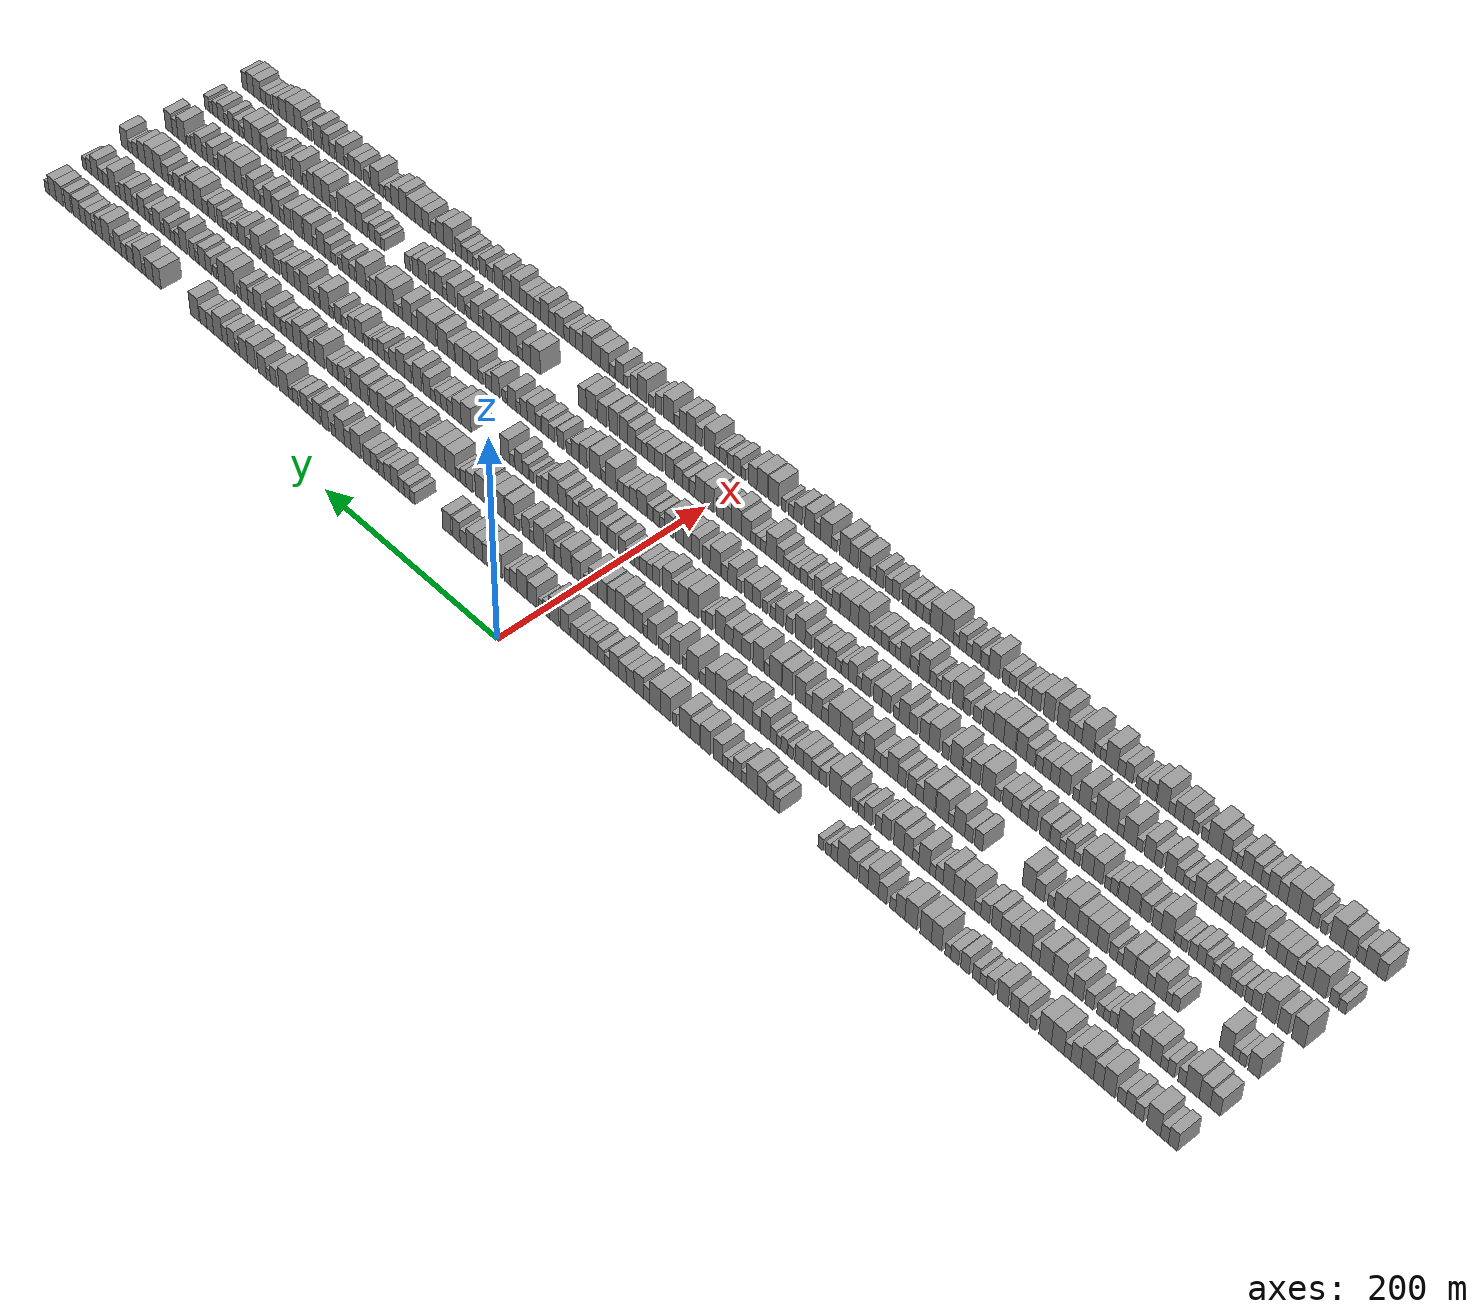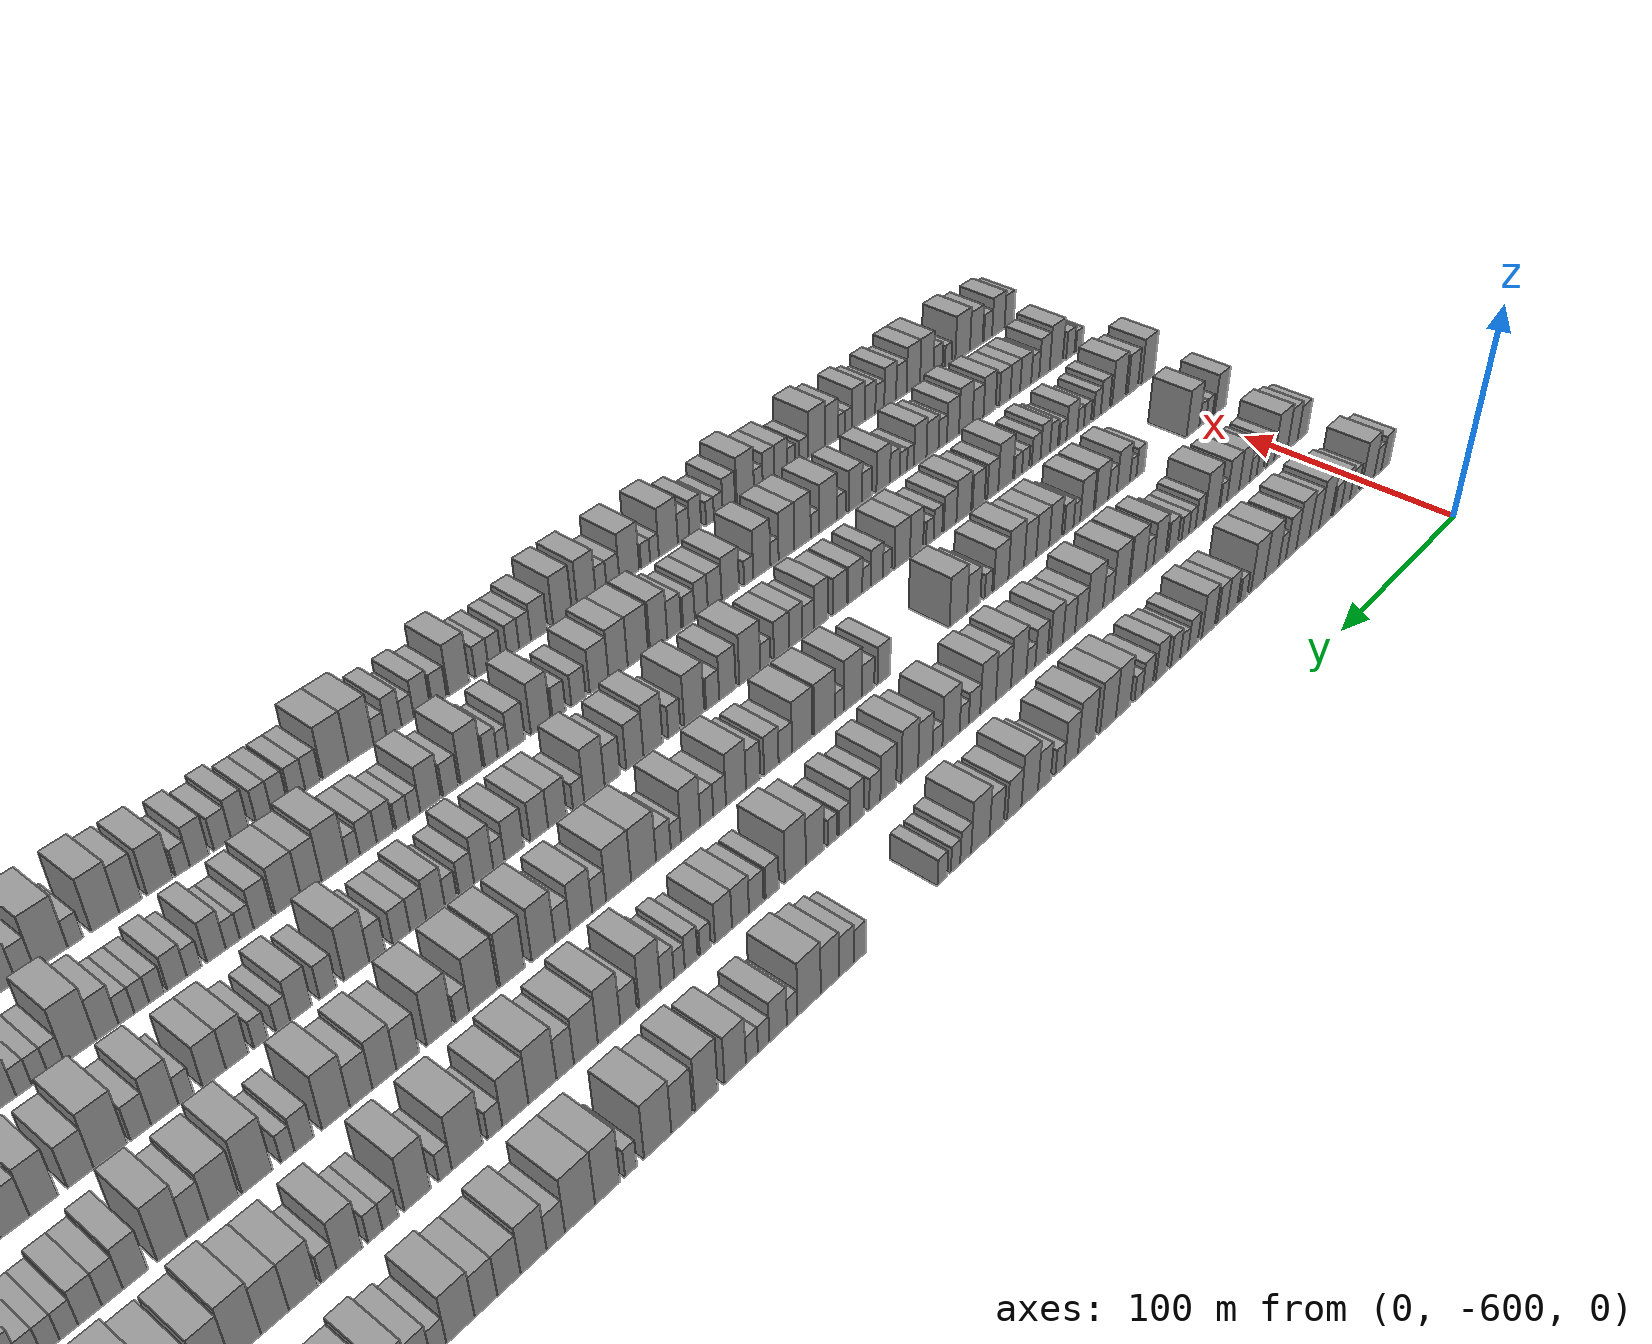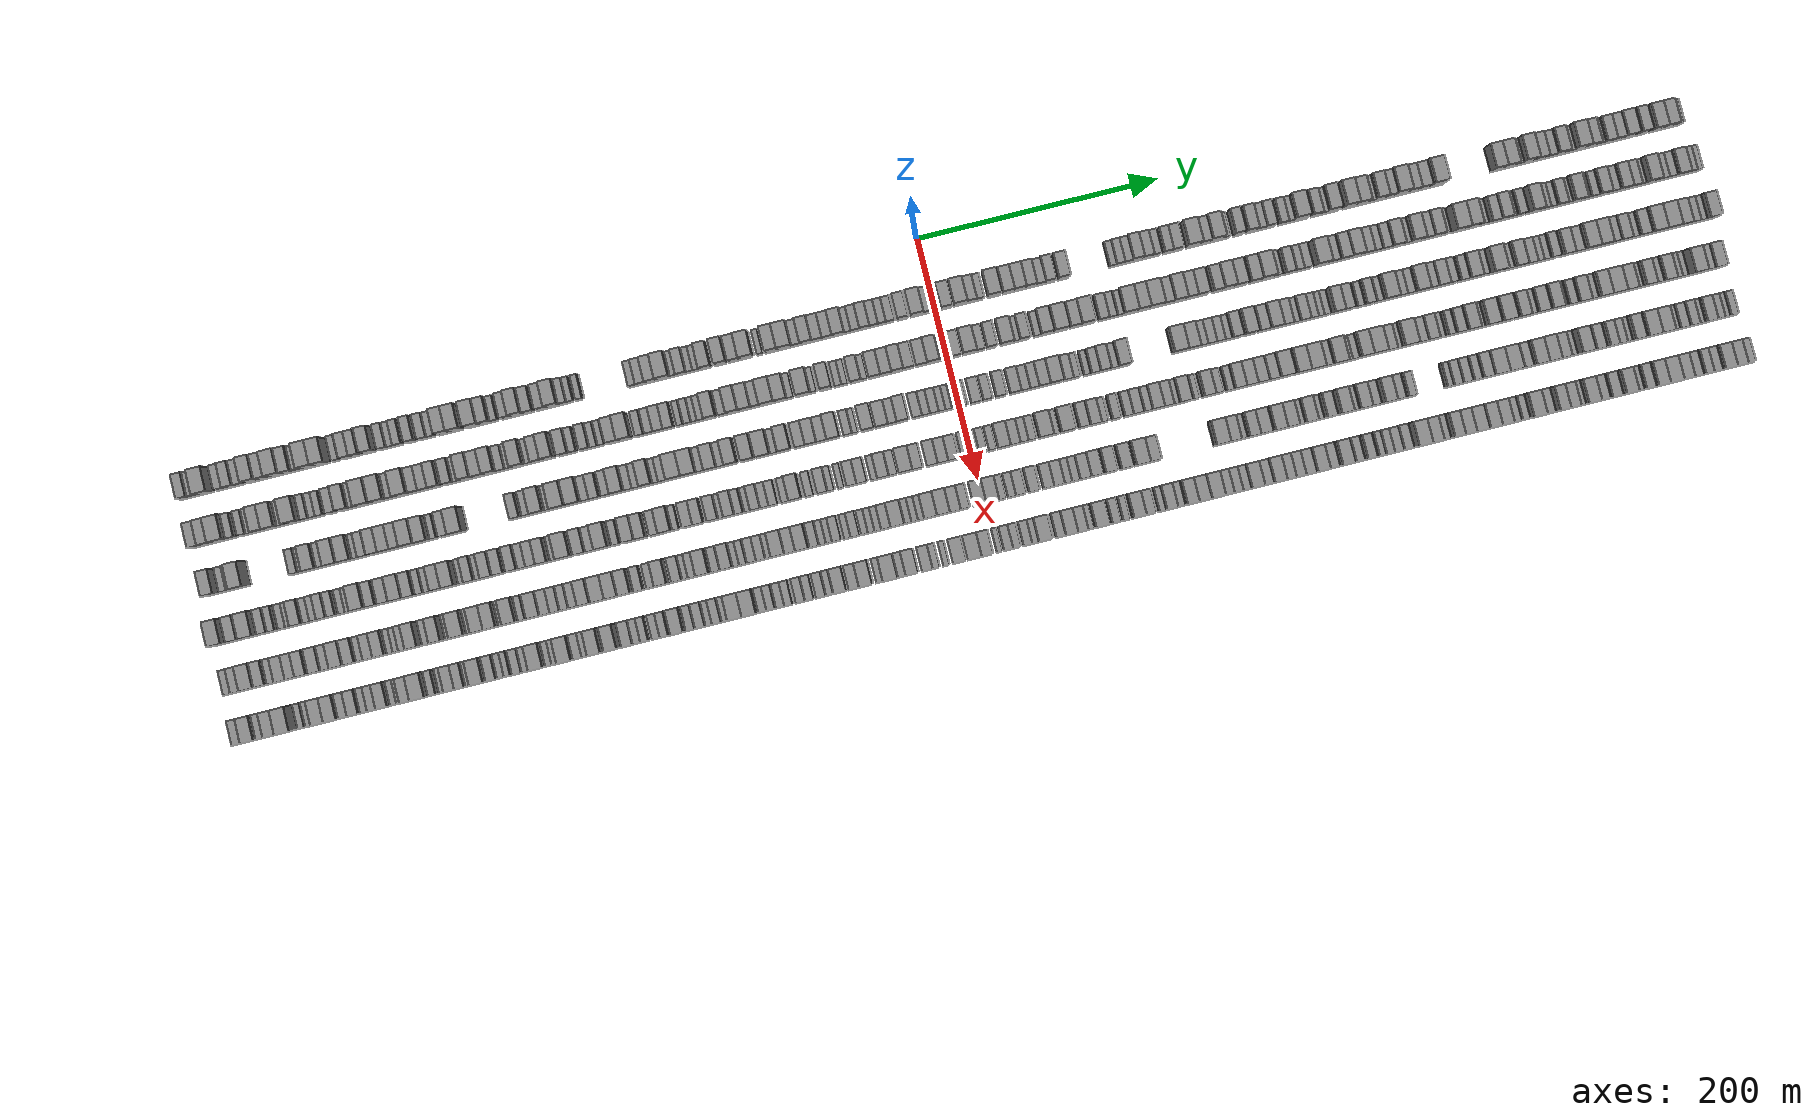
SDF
<sdf version="1.6">
 <world name="default">
  <scene>
   <sky><clouds><speed>12</speed></clouds></sky>
   <ambient>0.4 0.4 0.4 1</ambient>
   <background>0.7 0.7 0.7 1</background>
   <shadows>1</shadows>
  </scene>
  <gravity>0 0 -9.8066</gravity>
  <magnetic_field>6e-06 2.3e-05 -4.2e-05</magnetic_field>
  <physics default="0" name="default_physics" type="ode">
   <ode>
    <solver>
     <type>quick</type>
     <iters>10</iters>
     <sor>1.0</sor>
     <use_dynamic_moi_rescaling>0</use_dynamic_moi_rescaling>
    </solver>
    <constraints>
     <cfm>0</cfm>
     <erp>0.2</erp>
     <contact_max_correcting_vel>100</contact_max_correcting_vel>
     <contact_surface_layer>0.001</contact_surface_layer>
    </constraints>
   </ode>
   <max_step_size>0.004</max_step_size>
   <real_time_factor>1</real_time_factor>
   <real_time_update_rate>250</real_time_update_rate>
  </physics>
  <light name="sun" type="directional">
   <pose>0 0 10 0 0 0</pose>
   <diffuse>0.8 0.8 0.8 1</diffuse>
   <specular>0.2 0.2 0.2 1</specular>
   <attenuation>
    <range>1000</range>
    <constant>0.9</constant>
    <linear>0.01</linear>
    <quadratic>0.001</quadratic>
   </attenuation>
   <direction>-0.5 0.1 -0.9</direction>
  </light>
  <model name="building_1">
   <static>1</static>
   <pose>50.0000 -616.0534 0 0.000000 0.000000 0.000000</pose>
   <link name="link">
    <pose>0 0 9.00 0 0 0</pose>
    <collision name="collision"><geometry><box><size>20.0000 7.8933 18.0000</size></box></geometry></collision>
    <visual name="visual">
     <cast_shadows>0</cast_shadows>
     <geometry><box><size>20.0000 7.8933 18.0000</size></box></geometry>
     <material>
      <script>
       <uri>model://grey_wall/materials/scripts</uri>
       <uri>model://grey_wall/materials/textures</uri>
       <name>vrc/grey_wall</name>
      </script>
     </material>
    </visual>
   </link>
  </model>
  <model name="building_2">
   <static>1</static>
   <pose>50.0000 -608.7491 0 0.000000 0.000000 0.000000</pose>
   <link name="link">
    <pose>0 0 7.50 0 0 0</pose>
    <collision name="collision"><geometry><box><size>20.0000 6.7152 15.0000</size></box></geometry></collision>
    <visual name="visual">
     <cast_shadows>0</cast_shadows>
     <geometry><box><size>20.0000 6.7152 15.0000</size></box></geometry>
     <material>
      <script>
       <uri>model://grey_wall/materials/scripts</uri>
       <uri>model://grey_wall/materials/textures</uri>
       <name>vrc/grey_wall</name>
      </script>
     </material>
    </visual>
   </link>
  </model>
  <model name="building_3">
   <static>1</static>
   <pose>50.0000 -599.4543 0 0.000000 0.000000 0.000000</pose>
   <link name="link">
    <pose>0 0 12.00 0 0 0</pose>
    <collision name="collision"><geometry><box><size>20.0000 11.8744 24.0000</size></box></geometry></collision>
    <visual name="visual">
     <cast_shadows>0</cast_shadows>
     <geometry><box><size>20.0000 11.8744 24.0000</size></box></geometry>
     <material>
      <script>
       <uri>model://grey_wall/materials/scripts</uri>
       <uri>model://grey_wall/materials/textures</uri>
       <name>vrc/grey_wall</name>
      </script>
     </material>
    </visual>
   </link>
  </model>
  <model name="building_4">
   <static>1</static>
   <pose>50.0000 -586.7873 0 0.000000 0.000000 0.000000</pose>
   <link name="link">
    <pose>0 0 7.50 0 0 0</pose>
    <collision name="collision"><geometry><box><size>20.0000 7.4596 15.0000</size></box></geometry></collision>
    <visual name="visual">
     <cast_shadows>0</cast_shadows>
     <geometry><box><size>20.0000 7.4596 15.0000</size></box></geometry>
     <material>
      <script>
       <uri>model://grey_wall/materials/scripts</uri>
       <uri>model://grey_wall/materials/textures</uri>
       <name>vrc/grey_wall</name>
      </script>
     </material>
    </visual>
   </link>
  </model>
  <model name="building_5">
   <static>1</static>
   <pose>50.0000 -579.0176 0 0.000000 0.000000 0.000000</pose>
   <link name="link">
    <pose>0 0 9.00 0 0 0</pose>
    <collision name="collision"><geometry><box><size>20.0000 8.0798 18.0000</size></box></geometry></collision>
    <visual name="visual">
     <cast_shadows>0</cast_shadows>
     <geometry><box><size>20.0000 8.0798 18.0000</size></box></geometry>
     <material>
      <script>
       <uri>model://grey_wall/materials/scripts</uri>
       <uri>model://grey_wall/materials/textures</uri>
       <name>vrc/grey_wall</name>
      </script>
     </material>
    </visual>
   </link>
  </model>
  <model name="building_6">
   <static>1</static>
   <pose>50.0000 -571.4903 0 0.000000 0.000000 0.000000</pose>
   <link name="link">
    <pose>0 0 7.50 0 0 0</pose>
    <collision name="collision"><geometry><box><size>20.0000 6.9748 15.0000</size></box></geometry></collision>
    <visual name="visual">
     <cast_shadows>0</cast_shadows>
     <geometry><box><size>20.0000 6.9748 15.0000</size></box></geometry>
     <material>
      <script>
       <uri>model://grey_wall/materials/scripts</uri>
       <uri>model://grey_wall/materials/textures</uri>
       <name>vrc/grey_wall</name>
      </script>
     </material>
    </visual>
   </link>
  </model>
  <model name="building_7">
   <static>1</static>
   <pose>50.0000 -560.8347 0 0.000000 0.000000 0.000000</pose>
   <link name="link">
    <pose>0 0 12.00 0 0 0</pose>
    <collision name="collision"><geometry><box><size>20.0000 10.3364 24.0000</size></box></geometry></collision>
    <visual name="visual">
     <cast_shadows>0</cast_shadows>
     <geometry><box><size>20.0000 10.3364 24.0000</size></box></geometry>
     <material>
      <script>
       <uri>model://grey_wall/materials/scripts</uri>
       <uri>model://grey_wall/materials/textures</uri>
       <name>vrc/grey_wall</name>
      </script>
     </material>
    </visual>
   </link>
  </model>
  <model name="building_8">
   <static>1</static>
   <pose>50.0000 -551.4327 0 0.000000 0.000000 0.000000</pose>
   <link name="link">
    <pose>0 0 10.50 0 0 0</pose>
    <collision name="collision"><geometry><box><size>20.0000 8.4676 21.0000</size></box></geometry></collision>
    <visual name="visual">
     <cast_shadows>0</cast_shadows>
     <geometry><box><size>20.0000 8.4676 21.0000</size></box></geometry>
     <material>
      <script>
       <uri>model://grey_wall/materials/scripts</uri>
       <uri>model://grey_wall/materials/textures</uri>
       <name>vrc/grey_wall</name>
      </script>
     </material>
    </visual>
   </link>
  </model>
  <model name="building_9">
   <static>1</static>
   <pose>50.0000 -541.5499 0 0.000000 0.000000 0.000000</pose>
   <link name="link">
    <pose>0 0 12.00 0 0 0</pose>
    <collision name="collision"><geometry><box><size>20.0000 11.2979 24.0000</size></box></geometry></collision>
    <visual name="visual">
     <cast_shadows>0</cast_shadows>
     <geometry><box><size>20.0000 11.2979 24.0000</size></box></geometry>
     <material>
      <script>
       <uri>model://grey_wall/materials/scripts</uri>
       <uri>model://grey_wall/materials/textures</uri>
       <name>vrc/grey_wall</name>
      </script>
     </material>
    </visual>
   </link>
  </model>
  <model name="building_10">
   <static>1</static>
   <pose>50.0000 -531.5156 0 0.000000 0.000000 0.000000</pose>
   <link name="link">
    <pose>0 0 10.50 0 0 0</pose>
    <collision name="collision"><geometry><box><size>20.0000 8.7708 21.0000</size></box></geometry></collision>
    <visual name="visual">
     <cast_shadows>0</cast_shadows>
     <geometry><box><size>20.0000 8.7708 21.0000</size></box></geometry>
     <material>
      <script>
       <uri>model://grey_wall/materials/scripts</uri>
       <uri>model://grey_wall/materials/textures</uri>
       <name>vrc/grey_wall</name>
      </script>
     </material>
    </visual>
   </link>
  </model>
  <model name="building_11">
   <static>1</static>
   <pose>50.0000 -524.1173 0 0.000000 0.000000 0.000000</pose>
   <link name="link">
    <pose>0 0 7.50 0 0 0</pose>
    <collision name="collision"><geometry><box><size>20.0000 6.0257 15.0000</size></box></geometry></collision>
    <visual name="visual">
     <cast_shadows>0</cast_shadows>
     <geometry><box><size>20.0000 6.0257 15.0000</size></box></geometry>
     <material>
      <script>
       <uri>model://grey_wall/materials/scripts</uri>
       <uri>model://grey_wall/materials/textures</uri>
       <name>vrc/grey_wall</name>
      </script>
     </material>
    </visual>
   </link>
  </model>
  <model name="building_12">
   <static>1</static>
   <pose>50.0000 -515.4164 0 0.000000 0.000000 0.000000</pose>
   <link name="link">
    <pose>0 0 12.00 0 0 0</pose>
    <collision name="collision"><geometry><box><size>20.0000 11.3762 24.0000</size></box></geometry></collision>
    <visual name="visual">
     <cast_shadows>0</cast_shadows>
     <geometry><box><size>20.0000 11.3762 24.0000</size></box></geometry>
     <material>
      <script>
       <uri>model://grey_wall/materials/scripts</uri>
       <uri>model://grey_wall/materials/textures</uri>
       <name>vrc/grey_wall</name>
      </script>
     </material>
    </visual>
   </link>
  </model>
  <model name="building_13">
   <static>1</static>
   <pose>50.0000 -504.2278 0 0.000000 0.000000 0.000000</pose>
   <link name="link">
    <pose>0 0 12.00 0 0 0</pose>
    <collision name="collision"><geometry><box><size>20.0000 11.0009 24.0000</size></box></geometry></collision>
    <visual name="visual">
     <cast_shadows>0</cast_shadows>
     <geometry><box><size>20.0000 11.0009 24.0000</size></box></geometry>
     <material>
      <script>
       <uri>model://grey_wall/materials/scripts</uri>
       <uri>model://grey_wall/materials/textures</uri>
       <name>vrc/grey_wall</name>
      </script>
     </material>
    </visual>
   </link>
  </model>
  <model name="building_14">
   <static>1</static>
   <pose>50.0000 -492.8610 0 0.000000 0.000000 0.000000</pose>
   <link name="link">
    <pose>0 0 6.00 0 0 0</pose>
    <collision name="collision"><geometry><box><size>20.0000 5.7326 12.0000</size></box></geometry></collision>
    <visual name="visual">
     <cast_shadows>0</cast_shadows>
     <geometry><box><size>20.0000 5.7326 12.0000</size></box></geometry>
     <material>
      <script>
       <uri>model://grey_wall/materials/scripts</uri>
       <uri>model://grey_wall/materials/textures</uri>
       <name>vrc/grey_wall</name>
      </script>
     </material>
    </visual>
   </link>
  </model>
  <model name="building_15">
   <static>1</static>
   <pose>50.0000 -483.9732 0 0.000000 0.000000 0.000000</pose>
   <link name="link">
    <pose>0 0 9.00 0 0 0</pose>
    <collision name="collision"><geometry><box><size>20.0000 8.0430 18.0000</size></box></geometry></collision>
    <visual name="visual">
     <cast_shadows>0</cast_shadows>
     <geometry><box><size>20.0000 8.0430 18.0000</size></box></geometry>
     <material>
      <script>
       <uri>model://grey_wall/materials/scripts</uri>
       <uri>model://grey_wall/materials/textures</uri>
       <name>vrc/grey_wall</name>
      </script>
     </material>
    </visual>
   </link>
  </model>
  <model name="building_16">
   <static>1</static>
   <pose>50.0000 -476.2704 0 0.000000 0.000000 0.000000</pose>
   <link name="link">
    <pose>0 0 9.00 0 0 0</pose>
    <collision name="collision"><geometry><box><size>20.0000 7.3626 18.0000</size></box></geometry></collision>
    <visual name="visual">
     <cast_shadows>0</cast_shadows>
     <geometry><box><size>20.0000 7.3626 18.0000</size></box></geometry>
     <material>
      <script>
       <uri>model://grey_wall/materials/scripts</uri>
       <uri>model://grey_wall/materials/textures</uri>
       <name>vrc/grey_wall</name>
      </script>
     </material>
    </visual>
   </link>
  </model>
  <model name="building_17">
   <static>1</static>
   <pose>50.0000 -465.6922 0 0.000000 0.000000 0.000000</pose>
   <link name="link">
    <pose>0 0 10.50 0 0 0</pose>
    <collision name="collision"><geometry><box><size>20.0000 9.7939 21.0000</size></box></geometry></collision>
    <visual name="visual">
     <cast_shadows>0</cast_shadows>
     <geometry><box><size>20.0000 9.7939 21.0000</size></box></geometry>
     <material>
      <script>
       <uri>model://grey_wall/materials/scripts</uri>
       <uri>model://grey_wall/materials/textures</uri>
       <name>vrc/grey_wall</name>
      </script>
     </material>
    </visual>
   </link>
  </model>
  <model name="building_18">
   <static>1</static>
   <pose>50.0000 -454.2180 0 0.000000 0.000000 0.000000</pose>
   <link name="link">
    <pose>0 0 7.50 0 0 0</pose>
    <collision name="collision"><geometry><box><size>20.0000 7.1545 15.0000</size></box></geometry></collision>
    <visual name="visual">
     <cast_shadows>0</cast_shadows>
     <geometry><box><size>20.0000 7.1545 15.0000</size></box></geometry>
     <material>
      <script>
       <uri>model://grey_wall/materials/scripts</uri>
       <uri>model://grey_wall/materials/textures</uri>
       <name>vrc/grey_wall</name>
      </script>
     </material>
    </visual>
   </link>
  </model>
  <model name="building_19">
   <static>1</static>
   <pose>50.0000 -447.7025 0 0.000000 0.000000 0.000000</pose>
   <link name="link">
    <pose>0 0 6.00 0 0 0</pose>
    <collision name="collision"><geometry><box><size>20.0000 5.8765 12.0000</size></box></geometry></collision>
    <visual name="visual">
     <cast_shadows>0</cast_shadows>
     <geometry><box><size>20.0000 5.8765 12.0000</size></box></geometry>
     <material>
      <script>
       <uri>model://grey_wall/materials/scripts</uri>
       <uri>model://grey_wall/materials/textures</uri>
       <name>vrc/grey_wall</name>
      </script>
     </material>
    </visual>
   </link>
  </model>
  <model name="building_20">
   <static>1</static>
   <pose>50.0000 -441.4092 0 0.000000 0.000000 0.000000</pose>
   <link name="link">
    <pose>0 0 7.50 0 0 0</pose>
    <collision name="collision"><geometry><box><size>20.0000 6.7101 15.0000</size></box></geometry></collision>
    <visual name="visual">
     <cast_shadows>0</cast_shadows>
     <geometry><box><size>20.0000 6.7101 15.0000</size></box></geometry>
     <material>
      <script>
       <uri>model://grey_wall/materials/scripts</uri>
       <uri>model://grey_wall/materials/textures</uri>
       <name>vrc/grey_wall</name>
      </script>
     </material>
    </visual>
   </link>
  </model>
  <model name="building_21">
   <static>1</static>
   <pose>50.0000 -431.1350 0 0.000000 0.000000 0.000000</pose>
   <link name="link">
    <pose>0 0 9.00 0 0 0</pose>
    <collision name="collision"><geometry><box><size>20.0000 7.8383 18.0000</size></box></geometry></collision>
    <visual name="visual">
     <cast_shadows>0</cast_shadows>
     <geometry><box><size>20.0000 7.8383 18.0000</size></box></geometry>
     <material>
      <script>
       <uri>model://grey_wall/materials/scripts</uri>
       <uri>model://grey_wall/materials/textures</uri>
       <name>vrc/grey_wall</name>
      </script>
     </material>
    </visual>
   </link>
  </model>
  <model name="building_22">
   <static>1</static>
   <pose>50.0000 -421.5041 0 0.000000 0.000000 0.000000</pose>
   <link name="link">
    <pose>0 0 7.50 0 0 0</pose>
    <collision name="collision"><geometry><box><size>20.0000 7.4234 15.0000</size></box></geometry></collision>
    <visual name="visual">
     <cast_shadows>0</cast_shadows>
     <geometry><box><size>20.0000 7.4234 15.0000</size></box></geometry>
     <material>
      <script>
       <uri>model://grey_wall/materials/scripts</uri>
       <uri>model://grey_wall/materials/textures</uri>
       <name>vrc/grey_wall</name>
      </script>
     </material>
    </visual>
   </link>
  </model>
  <model name="building_23">
   <static>1</static>
   <pose>50.0000 -415.0984 0 0.000000 0.000000 0.000000</pose>
   <link name="link">
    <pose>0 0 6.00 0 0 0</pose>
    <collision name="collision"><geometry><box><size>20.0000 5.3878 12.0000</size></box></geometry></collision>
    <visual name="visual">
     <cast_shadows>0</cast_shadows>
     <geometry><box><size>20.0000 5.3878 12.0000</size></box></geometry>
     <material>
      <script>
       <uri>model://grey_wall/materials/scripts</uri>
       <uri>model://grey_wall/materials/textures</uri>
       <name>vrc/grey_wall</name>
      </script>
     </material>
    </visual>
   </link>
  </model>
  <model name="building_24">
   <static>1</static>
   <pose>50.0000 -404.5170 0 0.000000 0.000000 0.000000</pose>
   <link name="link">
    <pose>0 0 12.00 0 0 0</pose>
    <collision name="collision"><geometry><box><size>20.0000 9.7752 24.0000</size></box></geometry></collision>
    <visual name="visual">
     <cast_shadows>0</cast_shadows>
     <geometry><box><size>20.0000 9.7752 24.0000</size></box></geometry>
     <material>
      <script>
       <uri>model://grey_wall/materials/scripts</uri>
       <uri>model://grey_wall/materials/textures</uri>
       <name>vrc/grey_wall</name>
      </script>
     </material>
    </visual>
   </link>
  </model>
  <model name="building_25">
   <static>1</static>
   <pose>50.0000 -394.3219 0 0.000000 0.000000 0.000000</pose>
   <link name="link">
    <pose>0 0 12.00 0 0 0</pose>
    <collision name="collision"><geometry><box><size>20.0000 10.6150 24.0000</size></box></geometry></collision>
    <visual name="visual">
     <cast_shadows>0</cast_shadows>
     <geometry><box><size>20.0000 10.6150 24.0000</size></box></geometry>
     <material>
      <script>
       <uri>model://grey_wall/materials/scripts</uri>
       <uri>model://grey_wall/materials/textures</uri>
       <name>vrc/grey_wall</name>
      </script>
     </material>
    </visual>
   </link>
  </model>
  <model name="building_26">
   <static>1</static>
   <pose>50.0000 -380.3475 0 0.000000 0.000000 0.000000</pose>
   <link name="link">
    <pose>0 0 12.00 0 0 0</pose>
    <collision name="collision"><geometry><box><size>20.0000 11.3338 24.0000</size></box></geometry></collision>
    <visual name="visual">
     <cast_shadows>0</cast_shadows>
     <geometry><box><size>20.0000 11.3338 24.0000</size></box></geometry>
     <material>
      <script>
       <uri>model://grey_wall/materials/scripts</uri>
       <uri>model://grey_wall/materials/textures</uri>
       <name>vrc/grey_wall</name>
      </script>
     </material>
    </visual>
   </link>
  </model>
  <model name="building_27">
   <static>1</static>
   <pose>50.0000 -370.3326 0 0.000000 0.000000 0.000000</pose>
   <link name="link">
    <pose>0 0 10.50 0 0 0</pose>
    <collision name="collision"><geometry><box><size>20.0000 8.6959 21.0000</size></box></geometry></collision>
    <visual name="visual">
     <cast_shadows>0</cast_shadows>
     <geometry><box><size>20.0000 8.6959 21.0000</size></box></geometry>
     <material>
      <script>
       <uri>model://grey_wall/materials/scripts</uri>
       <uri>model://grey_wall/materials/textures</uri>
       <name>vrc/grey_wall</name>
      </script>
     </material>
    </visual>
   </link>
  </model>
  <model name="building_28">
   <static>1</static>
   <pose>50.0000 -363.1280 0 0.000000 0.000000 0.000000</pose>
   <link name="link">
    <pose>0 0 6.00 0 0 0</pose>
    <collision name="collision"><geometry><box><size>20.0000 5.7133 12.0000</size></box></geometry></collision>
    <visual name="visual">
     <cast_shadows>0</cast_shadows>
     <geometry><box><size>20.0000 5.7133 12.0000</size></box></geometry>
     <material>
      <script>
       <uri>model://grey_wall/materials/scripts</uri>
       <uri>model://grey_wall/materials/textures</uri>
       <name>vrc/grey_wall</name>
      </script>
     </material>
    </visual>
   </link>
  </model>
  <model name="building_29">
   <static>1</static>
   <pose>50.0000 -353.3051 0 0.000000 0.000000 0.000000</pose>
   <link name="link">
    <pose>0 0 9.00 0 0 0</pose>
    <collision name="collision"><geometry><box><size>20.0000 7.9326 18.0000</size></box></geometry></collision>
    <visual name="visual">
     <cast_shadows>0</cast_shadows>
     <geometry><box><size>20.0000 7.9326 18.0000</size></box></geometry>
     <material>
      <script>
       <uri>model://grey_wall/materials/scripts</uri>
       <uri>model://grey_wall/materials/textures</uri>
       <name>vrc/grey_wall</name>
      </script>
     </material>
    </visual>
   </link>
  </model>
  <model name="building_30">
   <static>1</static>
   <pose>50.0000 -344.2689 0 0.000000 0.000000 0.000000</pose>
   <link name="link">
    <pose>0 0 12.00 0 0 0</pose>
    <collision name="collision"><geometry><box><size>20.0000 10.1398 24.0000</size></box></geometry></collision>
    <visual name="visual">
     <cast_shadows>0</cast_shadows>
     <geometry><box><size>20.0000 10.1398 24.0000</size></box></geometry>
     <material>
      <script>
       <uri>model://grey_wall/materials/scripts</uri>
       <uri>model://grey_wall/materials/textures</uri>
       <name>vrc/grey_wall</name>
      </script>
     </material>
    </visual>
   </link>
  </model>
  <model name="building_31">
   <static>1</static>
   <pose>50.0000 -334.9038 0 0.000000 0.000000 0.000000</pose>
   <link name="link">
    <pose>0 0 9.00 0 0 0</pose>
    <collision name="collision"><geometry><box><size>20.0000 8.5902 18.0000</size></box></geometry></collision>
    <visual name="visual">
     <cast_shadows>0</cast_shadows>
     <geometry><box><size>20.0000 8.5902 18.0000</size></box></geometry>
     <material>
      <script>
       <uri>model://grey_wall/materials/scripts</uri>
       <uri>model://grey_wall/materials/textures</uri>
       <name>vrc/grey_wall</name>
      </script>
     </material>
    </visual>
   </link>
  </model>
  <model name="building_32">
   <static>1</static>
   <pose>50.0000 -324.4063 0 0.000000 0.000000 0.000000</pose>
   <link name="link">
    <pose>0 0 9.00 0 0 0</pose>
    <collision name="collision"><geometry><box><size>20.0000 8.4047 18.0000</size></box></geometry></collision>
    <visual name="visual">
     <cast_shadows>0</cast_shadows>
     <geometry><box><size>20.0000 8.4047 18.0000</size></box></geometry>
     <material>
      <script>
       <uri>model://grey_wall/materials/scripts</uri>
       <uri>model://grey_wall/materials/textures</uri>
       <name>vrc/grey_wall</name>
      </script>
     </material>
    </visual>
   </link>
  </model>
  <model name="building_33">
   <static>1</static>
   <pose>50.0000 -314.8949 0 0.000000 0.000000 0.000000</pose>
   <link name="link">
    <pose>0 0 12.00 0 0 0</pose>
    <collision name="collision"><geometry><box><size>20.0000 10.6181 24.0000</size></box></geometry></collision>
    <visual name="visual">
     <cast_shadows>0</cast_shadows>
     <geometry><box><size>20.0000 10.6181 24.0000</size></box></geometry>
     <material>
      <script>
       <uri>model://grey_wall/materials/scripts</uri>
       <uri>model://grey_wall/materials/textures</uri>
       <name>vrc/grey_wall</name>
      </script>
     </material>
    </visual>
   </link>
  </model>
  <model name="building_34">
   <static>1</static>
   <pose>50.0000 -306.4508 0 0.000000 0.000000 0.000000</pose>
   <link name="link">
    <pose>0 0 7.50 0 0 0</pose>
    <collision name="collision"><geometry><box><size>20.0000 6.2700 15.0000</size></box></geometry></collision>
    <visual name="visual">
     <cast_shadows>0</cast_shadows>
     <geometry><box><size>20.0000 6.2700 15.0000</size></box></geometry>
     <material>
      <script>
       <uri>model://grey_wall/materials/scripts</uri>
       <uri>model://grey_wall/materials/textures</uri>
       <name>vrc/grey_wall</name>
      </script>
     </material>
    </visual>
   </link>
  </model>
  <model name="building_35">
   <static>1</static>
   <pose>50.0000 -300.6897 0 0.000000 0.000000 0.000000</pose>
   <link name="link">
    <pose>0 0 6.00 0 0 0</pose>
    <collision name="collision"><geometry><box><size>20.0000 5.2523 12.0000</size></box></geometry></collision>
    <visual name="visual">
     <cast_shadows>0</cast_shadows>
     <geometry><box><size>20.0000 5.2523 12.0000</size></box></geometry>
     <material>
      <script>
       <uri>model://grey_wall/materials/scripts</uri>
       <uri>model://grey_wall/materials/textures</uri>
       <name>vrc/grey_wall</name>
      </script>
     </material>
    </visual>
   </link>
  </model>
  <model name="building_36">
   <static>1</static>
   <pose>50.0000 -293.3483 0 0.000000 0.000000 0.000000</pose>
   <link name="link">
    <pose>0 0 6.00 0 0 0</pose>
    <collision name="collision"><geometry><box><size>20.0000 5.4305 12.0000</size></box></geometry></collision>
    <visual name="visual">
     <cast_shadows>0</cast_shadows>
     <geometry><box><size>20.0000 5.4305 12.0000</size></box></geometry>
     <material>
      <script>
       <uri>model://grey_wall/materials/scripts</uri>
       <uri>model://grey_wall/materials/textures</uri>
       <name>vrc/grey_wall</name>
      </script>
     </material>
    </visual>
   </link>
  </model>
  <model name="building_37">
   <static>1</static>
   <pose>50.0000 -249.3242 0 0.000000 0.000000 0.000000</pose>
   <link name="link">
    <pose>0 0 7.50 0 0 0</pose>
    <collision name="collision"><geometry><box><size>20.0000 6.2059 15.0000</size></box></geometry></collision>
    <visual name="visual">
     <cast_shadows>0</cast_shadows>
     <geometry><box><size>20.0000 6.2059 15.0000</size></box></geometry>
     <material>
      <script>
       <uri>model://grey_wall/materials/scripts</uri>
       <uri>model://grey_wall/materials/textures</uri>
       <name>vrc/grey_wall</name>
      </script>
     </material>
    </visual>
   </link>
  </model>
  <model name="building_38">
   <static>1</static>
   <pose>50.0000 -242.4254 0 0.000000 0.000000 0.000000</pose>
   <link name="link">
    <pose>0 0 9.00 0 0 0</pose>
    <collision name="collision"><geometry><box><size>20.0000 7.5917 18.0000</size></box></geometry></collision>
    <visual name="visual">
     <cast_shadows>0</cast_shadows>
     <geometry><box><size>20.0000 7.5917 18.0000</size></box></geometry>
     <material>
      <script>
       <uri>model://grey_wall/materials/scripts</uri>
       <uri>model://grey_wall/materials/textures</uri>
       <name>vrc/grey_wall</name>
      </script>
     </material>
    </visual>
   </link>
  </model>
  <model name="building_39">
   <static>1</static>
   <pose>50.0000 -234.2030 0 0.000000 0.000000 0.000000</pose>
   <link name="link">
    <pose>0 0 10.50 0 0 0</pose>
    <collision name="collision"><geometry><box><size>20.0000 8.8531 21.0000</size></box></geometry></collision>
    <visual name="visual">
     <cast_shadows>0</cast_shadows>
     <geometry><box><size>20.0000 8.8531 21.0000</size></box></geometry>
     <material>
      <script>
       <uri>model://grey_wall/materials/scripts</uri>
       <uri>model://grey_wall/materials/textures</uri>
       <name>vrc/grey_wall</name>
      </script>
     </material>
    </visual>
   </link>
  </model>
  <model name="building_40">
   <static>1</static>
   <pose>50.0000 -224.1405 0 0.000000 0.000000 0.000000</pose>
   <link name="link">
    <pose>0 0 12.00 0 0 0</pose>
    <collision name="collision"><geometry><box><size>20.0000 11.2719 24.0000</size></box></geometry></collision>
    <visual name="visual">
     <cast_shadows>0</cast_shadows>
     <geometry><box><size>20.0000 11.2719 24.0000</size></box></geometry>
     <material>
      <script>
       <uri>model://grey_wall/materials/scripts</uri>
       <uri>model://grey_wall/materials/textures</uri>
       <name>vrc/grey_wall</name>
      </script>
     </material>
    </visual>
   </link>
  </model>
  <model name="building_41">
   <static>1</static>
   <pose>50.0000 -215.9789 0 0.000000 0.000000 0.000000</pose>
   <link name="link">
    <pose>0 0 6.00 0 0 0</pose>
    <collision name="collision"><geometry><box><size>20.0000 5.0512 12.0000</size></box></geometry></collision>
    <visual name="visual">
     <cast_shadows>0</cast_shadows>
     <geometry><box><size>20.0000 5.0512 12.0000</size></box></geometry>
     <material>
      <script>
       <uri>model://grey_wall/materials/scripts</uri>
       <uri>model://grey_wall/materials/textures</uri>
       <name>vrc/grey_wall</name>
      </script>
     </material>
    </visual>
   </link>
  </model>
  <model name="building_42">
   <static>1</static>
   <pose>50.0000 -209.3236 0 0.000000 0.000000 0.000000</pose>
   <link name="link">
    <pose>0 0 9.00 0 0 0</pose>
    <collision name="collision"><geometry><box><size>20.0000 8.2592 18.0000</size></box></geometry></collision>
    <visual name="visual">
     <cast_shadows>0</cast_shadows>
     <geometry><box><size>20.0000 8.2592 18.0000</size></box></geometry>
     <material>
      <script>
       <uri>model://grey_wall/materials/scripts</uri>
       <uri>model://grey_wall/materials/textures</uri>
       <name>vrc/grey_wall</name>
      </script>
     </material>
    </visual>
   </link>
  </model>
  <model name="building_43">
   <static>1</static>
   <pose>50.0000 -202.5598 0 0.000000 0.000000 0.000000</pose>
   <link name="link">
    <pose>0 0 6.00 0 0 0</pose>
    <collision name="collision"><geometry><box><size>20.0000 5.2686 12.0000</size></box></geometry></collision>
    <visual name="visual">
     <cast_shadows>0</cast_shadows>
     <geometry><box><size>20.0000 5.2686 12.0000</size></box></geometry>
     <material>
      <script>
       <uri>model://grey_wall/materials/scripts</uri>
       <uri>model://grey_wall/materials/textures</uri>
       <name>vrc/grey_wall</name>
      </script>
     </material>
    </visual>
   </link>
  </model>
  <model name="building_44">
   <static>1</static>
   <pose>50.0000 -197.1776 0 0.000000 0.000000 0.000000</pose>
   <link name="link">
    <pose>0 0 6.00 0 0 0</pose>
    <collision name="collision"><geometry><box><size>20.0000 5.4957 12.0000</size></box></geometry></collision>
    <visual name="visual">
     <cast_shadows>0</cast_shadows>
     <geometry><box><size>20.0000 5.4957 12.0000</size></box></geometry>
     <material>
      <script>
       <uri>model://grey_wall/materials/scripts</uri>
       <uri>model://grey_wall/materials/textures</uri>
       <name>vrc/grey_wall</name>
      </script>
     </material>
    </visual>
   </link>
  </model>
  <model name="building_45">
   <static>1</static>
   <pose>50.0000 -189.6013 0 0.000000 0.000000 0.000000</pose>
   <link name="link">
    <pose>0 0 10.50 0 0 0</pose>
    <collision name="collision"><geometry><box><size>20.0000 9.6570 21.0000</size></box></geometry></collision>
    <visual name="visual">
     <cast_shadows>0</cast_shadows>
     <geometry><box><size>20.0000 9.6570 21.0000</size></box></geometry>
     <material>
      <script>
       <uri>model://grey_wall/materials/scripts</uri>
       <uri>model://grey_wall/materials/textures</uri>
       <name>vrc/grey_wall</name>
      </script>
     </material>
    </visual>
   </link>
  </model>
  <model name="building_46">
   <static>1</static>
   <pose>50.0000 -176.7682 0 0.000000 0.000000 0.000000</pose>
   <link name="link">
    <pose>0 0 12.00 0 0 0</pose>
    <collision name="collision"><geometry><box><size>20.0000 10.0092 24.0000</size></box></geometry></collision>
    <visual name="visual">
     <cast_shadows>0</cast_shadows>
     <geometry><box><size>20.0000 10.0092 24.0000</size></box></geometry>
     <material>
      <script>
       <uri>model://grey_wall/materials/scripts</uri>
       <uri>model://grey_wall/materials/textures</uri>
       <name>vrc/grey_wall</name>
      </script>
     </material>
    </visual>
   </link>
  </model>
  <model name="building_47">
   <static>1</static>
   <pose>50.0000 -166.2296 0 0.000000 0.000000 0.000000</pose>
   <link name="link">
    <pose>0 0 10.50 0 0 0</pose>
    <collision name="collision"><geometry><box><size>20.0000 9.0681 21.0000</size></box></geometry></collision>
    <visual name="visual">
     <cast_shadows>0</cast_shadows>
     <geometry><box><size>20.0000 9.0681 21.0000</size></box></geometry>
     <material>
      <script>
       <uri>model://grey_wall/materials/scripts</uri>
       <uri>model://grey_wall/materials/textures</uri>
       <name>vrc/grey_wall</name>
      </script>
     </material>
    </visual>
   </link>
  </model>
  <model name="building_48">
   <static>1</static>
   <pose>50.0000 -155.9535 0 0.000000 0.000000 0.000000</pose>
   <link name="link">
    <pose>0 0 12.00 0 0 0</pose>
    <collision name="collision"><geometry><box><size>20.0000 11.4841 24.0000</size></box></geometry></collision>
    <visual name="visual">
     <cast_shadows>0</cast_shadows>
     <geometry><box><size>20.0000 11.4841 24.0000</size></box></geometry>
     <material>
      <script>
       <uri>model://grey_wall/materials/scripts</uri>
       <uri>model://grey_wall/materials/textures</uri>
       <name>vrc/grey_wall</name>
      </script>
     </material>
    </visual>
   </link>
  </model>
  <model name="building_49">
   <static>1</static>
   <pose>50.0000 -144.7946 0 0.000000 0.000000 0.000000</pose>
   <link name="link">
    <pose>0 0 6.00 0 0 0</pose>
    <collision name="collision"><geometry><box><size>20.0000 4.8336 12.0000</size></box></geometry></collision>
    <visual name="visual">
     <cast_shadows>0</cast_shadows>
     <geometry><box><size>20.0000 4.8336 12.0000</size></box></geometry>
     <material>
      <script>
       <uri>model://grey_wall/materials/scripts</uri>
       <uri>model://grey_wall/materials/textures</uri>
       <name>vrc/grey_wall</name>
      </script>
     </material>
    </visual>
   </link>
  </model>
  <model name="building_50">
   <static>1</static>
   <pose>50.0000 -135.3790 0 0.000000 0.000000 0.000000</pose>
   <link name="link">
    <pose>0 0 12.00 0 0 0</pose>
    <collision name="collision"><geometry><box><size>20.0000 9.9977 24.0000</size></box></geometry></collision>
    <visual name="visual">
     <cast_shadows>0</cast_shadows>
     <geometry><box><size>20.0000 9.9977 24.0000</size></box></geometry>
     <material>
      <script>
       <uri>model://grey_wall/materials/scripts</uri>
       <uri>model://grey_wall/materials/textures</uri>
       <name>vrc/grey_wall</name>
      </script>
     </material>
    </visual>
   </link>
  </model>
  <model name="building_51">
   <static>1</static>
   <pose>50.0000 -124.5223 0 0.000000 0.000000 0.000000</pose>
   <link name="link">
    <pose>0 0 12.00 0 0 0</pose>
    <collision name="collision"><geometry><box><size>20.0000 11.7156 24.0000</size></box></geometry></collision>
    <visual name="visual">
     <cast_shadows>0</cast_shadows>
     <geometry><box><size>20.0000 11.7156 24.0000</size></box></geometry>
     <material>
      <script>
       <uri>model://grey_wall/materials/scripts</uri>
       <uri>model://grey_wall/materials/textures</uri>
       <name>vrc/grey_wall</name>
      </script>
     </material>
    </visual>
   </link>
  </model>
  <model name="building_52">
   <static>1</static>
   <pose>50.0000 -115.1281 0 0.000000 0.000000 0.000000</pose>
   <link name="link">
    <pose>0 0 7.50 0 0 0</pose>
    <collision name="collision"><geometry><box><size>20.0000 7.0728 15.0000</size></box></geometry></collision>
    <visual name="visual">
     <cast_shadows>0</cast_shadows>
     <geometry><box><size>20.0000 7.0728 15.0000</size></box></geometry>
     <material>
      <script>
       <uri>model://grey_wall/materials/scripts</uri>
       <uri>model://grey_wall/materials/textures</uri>
       <name>vrc/grey_wall</name>
      </script>
     </material>
    </visual>
   </link>
  </model>
  <model name="building_53">
   <static>1</static>
   <pose>50.0000 -106.7316 0 0.000000 0.000000 0.000000</pose>
   <link name="link">
    <pose>0 0 10.50 0 0 0</pose>
    <collision name="collision"><geometry><box><size>20.0000 9.7201 21.0000</size></box></geometry></collision>
    <visual name="visual">
     <cast_shadows>0</cast_shadows>
     <geometry><box><size>20.0000 9.7201 21.0000</size></box></geometry>
     <material>
      <script>
       <uri>model://grey_wall/materials/scripts</uri>
       <uri>model://grey_wall/materials/textures</uri>
       <name>vrc/grey_wall</name>
      </script>
     </material>
    </visual>
   </link>
  </model>
  <model name="building_54">
   <static>1</static>
   <pose>50.0000 -97.6066 0 0.000000 0.000000 0.000000</pose>
   <link name="link">
    <pose>0 0 9.00 0 0 0</pose>
    <collision name="collision"><geometry><box><size>20.0000 8.5299 18.0000</size></box></geometry></collision>
    <visual name="visual">
     <cast_shadows>0</cast_shadows>
     <geometry><box><size>20.0000 8.5299 18.0000</size></box></geometry>
     <material>
      <script>
       <uri>model://grey_wall/materials/scripts</uri>
       <uri>model://grey_wall/materials/textures</uri>
       <name>vrc/grey_wall</name>
      </script>
     </material>
    </visual>
   </link>
  </model>
  <model name="building_55">
   <static>1</static>
   <pose>50.0000 -89.2613 0 0.000000 0.000000 0.000000</pose>
   <link name="link">
    <pose>0 0 9.00 0 0 0</pose>
    <collision name="collision"><geometry><box><size>20.0000 8.1607 18.0000</size></box></geometry></collision>
    <visual name="visual">
     <cast_shadows>0</cast_shadows>
     <geometry><box><size>20.0000 8.1607 18.0000</size></box></geometry>
     <material>
      <script>
       <uri>model://grey_wall/materials/scripts</uri>
       <uri>model://grey_wall/materials/textures</uri>
       <name>vrc/grey_wall</name>
      </script>
     </material>
    </visual>
   </link>
  </model>
  <model name="building_56">
   <static>1</static>
   <pose>50.0000 -80.1946 0 0.000000 0.000000 0.000000</pose>
   <link name="link">
    <pose>0 0 10.50 0 0 0</pose>
    <collision name="collision"><geometry><box><size>20.0000 9.9728 21.0000</size></box></geometry></collision>
    <visual name="visual">
     <cast_shadows>0</cast_shadows>
     <geometry><box><size>20.0000 9.9728 21.0000</size></box></geometry>
     <material>
      <script>
       <uri>model://grey_wall/materials/scripts</uri>
       <uri>model://grey_wall/materials/textures</uri>
       <name>vrc/grey_wall</name>
      </script>
     </material>
    </visual>
   </link>
  </model>
  <model name="building_57">
   <static>1</static>
   <pose>50.0000 -72.5156 0 0.000000 0.000000 0.000000</pose>
   <link name="link">
    <pose>0 0 6.00 0 0 0</pose>
    <collision name="collision"><geometry><box><size>20.0000 5.3850 12.0000</size></box></geometry></collision>
    <visual name="visual">
     <cast_shadows>0</cast_shadows>
     <geometry><box><size>20.0000 5.3850 12.0000</size></box></geometry>
     <material>
      <script>
       <uri>model://grey_wall/materials/scripts</uri>
       <uri>model://grey_wall/materials/textures</uri>
       <name>vrc/grey_wall</name>
      </script>
     </material>
    </visual>
   </link>
  </model>
  <model name="building_58">
   <static>1</static>
   <pose>50.0000 -66.1630 0 0.000000 0.000000 0.000000</pose>
   <link name="link">
    <pose>0 0 7.50 0 0 0</pose>
    <collision name="collision"><geometry><box><size>20.0000 7.3204 15.0000</size></box></geometry></collision>
    <visual name="visual">
     <cast_shadows>0</cast_shadows>
     <geometry><box><size>20.0000 7.3204 15.0000</size></box></geometry>
     <material>
      <script>
       <uri>model://grey_wall/materials/scripts</uri>
       <uri>model://grey_wall/materials/textures</uri>
       <name>vrc/grey_wall</name>
      </script>
     </material>
    </visual>
   </link>
  </model>
  <model name="building_59">
   <static>1</static>
   <pose>50.0000 -58.4191 0 0.000000 0.000000 0.000000</pose>
   <link name="link">
    <pose>0 0 9.00 0 0 0</pose>
    <collision name="collision"><geometry><box><size>20.0000 8.1674 18.0000</size></box></geometry></collision>
    <visual name="visual">
     <cast_shadows>0</cast_shadows>
     <geometry><box><size>20.0000 8.1674 18.0000</size></box></geometry>
     <material>
      <script>
       <uri>model://grey_wall/materials/scripts</uri>
       <uri>model://grey_wall/materials/textures</uri>
       <name>vrc/grey_wall</name>
      </script>
     </material>
    </visual>
   </link>
  </model>
  <model name="building_60">
   <static>1</static>
   <pose>50.0000 -50.8502 0 0.000000 0.000000 0.000000</pose>
   <link name="link">
    <pose>0 0 7.50 0 0 0</pose>
    <collision name="collision"><geometry><box><size>20.0000 6.9702 15.0000</size></box></geometry></collision>
    <visual name="visual">
     <cast_shadows>0</cast_shadows>
     <geometry><box><size>20.0000 6.9702 15.0000</size></box></geometry>
     <material>
      <script>
       <uri>model://grey_wall/materials/scripts</uri>
       <uri>model://grey_wall/materials/textures</uri>
       <name>vrc/grey_wall</name>
      </script>
     </material>
    </visual>
   </link>
  </model>
  <model name="building_61">
   <static>1</static>
   <pose>50.0000 -44.0706 0 0.000000 0.000000 0.000000</pose>
   <link name="link">
    <pose>0 0 7.50 0 0 0</pose>
    <collision name="collision"><geometry><box><size>20.0000 6.5891 15.0000</size></box></geometry></collision>
    <visual name="visual">
     <cast_shadows>0</cast_shadows>
     <geometry><box><size>20.0000 6.5891 15.0000</size></box></geometry>
     <material>
      <script>
       <uri>model://grey_wall/materials/scripts</uri>
       <uri>model://grey_wall/materials/textures</uri>
       <name>vrc/grey_wall</name>
      </script>
     </material>
    </visual>
   </link>
  </model>
  <model name="building_62">
   <static>1</static>
   <pose>50.0000 -37.1609 0 0.000000 0.000000 0.000000</pose>
   <link name="link">
    <pose>0 0 7.50 0 0 0</pose>
    <collision name="collision"><geometry><box><size>20.0000 7.2303 15.0000</size></box></geometry></collision>
    <visual name="visual">
     <cast_shadows>0</cast_shadows>
     <geometry><box><size>20.0000 7.2303 15.0000</size></box></geometry>
     <material>
      <script>
       <uri>model://grey_wall/materials/scripts</uri>
       <uri>model://grey_wall/materials/textures</uri>
       <name>vrc/grey_wall</name>
      </script>
     </material>
    </visual>
   </link>
  </model>
  <model name="building_63">
   <static>1</static>
   <pose>50.0000 -27.0163 0 0.000000 0.000000 0.000000</pose>
   <link name="link">
    <pose>0 0 10.50 0 0 0</pose>
    <collision name="collision"><geometry><box><size>20.0000 9.0587 21.0000</size></box></geometry></collision>
    <visual name="visual">
     <cast_shadows>0</cast_shadows>
     <geometry><box><size>20.0000 9.0587 21.0000</size></box></geometry>
     <material>
      <script>
       <uri>model://grey_wall/materials/scripts</uri>
       <uri>model://grey_wall/materials/textures</uri>
       <name>vrc/grey_wall</name>
      </script>
     </material>
    </visual>
   </link>
  </model>
  <model name="building_64">
   <static>1</static>
   <pose>50.0000 -15.0868 0 0.000000 0.000000 0.000000</pose>
   <link name="link">
    <pose>0 0 12.00 0 0 0</pose>
    <collision name="collision"><geometry><box><size>20.0000 10.8004 24.0000</size></box></geometry></collision>
    <visual name="visual">
     <cast_shadows>0</cast_shadows>
     <geometry><box><size>20.0000 10.8004 24.0000</size></box></geometry>
     <material>
      <script>
       <uri>model://grey_wall/materials/scripts</uri>
       <uri>model://grey_wall/materials/textures</uri>
       <name>vrc/grey_wall</name>
      </script>
     </material>
    </visual>
   </link>
  </model>
  <model name="building_65">
   <static>1</static>
   <pose>50.0000 -6.0806 0 0.000000 0.000000 0.000000</pose>
   <link name="link">
    <pose>0 0 7.50 0 0 0</pose>
    <collision name="collision"><geometry><box><size>20.0000 7.2119 15.0000</size></box></geometry></collision>
    <visual name="visual">
     <cast_shadows>0</cast_shadows>
     <geometry><box><size>20.0000 7.2119 15.0000</size></box></geometry>
     <material>
      <script>
       <uri>model://grey_wall/materials/scripts</uri>
       <uri>model://grey_wall/materials/textures</uri>
       <name>vrc/grey_wall</name>
      </script>
     </material>
    </visual>
   </link>
  </model>
  <model name="building_66">
   <static>1</static>
   <pose>50.0000 -0.0146 0 0.000000 0.000000 0.000000</pose>
   <link name="link">
    <pose>0 0 6.00 0 0 0</pose>
    <collision name="collision"><geometry><box><size>20.0000 4.9202 12.0000</size></box></geometry></collision>
    <visual name="visual">
     <cast_shadows>0</cast_shadows>
     <geometry><box><size>20.0000 4.9202 12.0000</size></box></geometry>
     <material>
      <script>
       <uri>model://grey_wall/materials/scripts</uri>
       <uri>model://grey_wall/materials/textures</uri>
       <name>vrc/grey_wall</name>
      </script>
     </material>
    </visual>
   </link>
  </model>
  <model name="building_67">
   <static>1</static>
   <pose>50.0000 9.3892 0 0.000000 0.000000 0.000000</pose>
   <link name="link">
    <pose>0 0 10.50 0 0 0</pose>
    <collision name="collision"><geometry><box><size>20.0000 9.8873 21.0000</size></box></geometry></collision>
    <visual name="visual">
     <cast_shadows>0</cast_shadows>
     <geometry><box><size>20.0000 9.8873 21.0000</size></box></geometry>
     <material>
      <script>
       <uri>model://grey_wall/materials/scripts</uri>
       <uri>model://grey_wall/materials/textures</uri>
       <name>vrc/grey_wall</name>
      </script>
     </material>
    </visual>
   </link>
  </model>
  <model name="building_68">
   <static>1</static>
   <pose>50.0000 20.8231 0 0.000000 0.000000 0.000000</pose>
   <link name="link">
    <pose>0 0 12.00 0 0 0</pose>
    <collision name="collision"><geometry><box><size>20.0000 10.9804 24.0000</size></box></geometry></collision>
    <visual name="visual">
     <cast_shadows>0</cast_shadows>
     <geometry><box><size>20.0000 10.9804 24.0000</size></box></geometry>
     <material>
      <script>
       <uri>model://grey_wall/materials/scripts</uri>
       <uri>model://grey_wall/materials/textures</uri>
       <name>vrc/grey_wall</name>
      </script>
     </material>
    </visual>
   </link>
  </model>
  <model name="building_69">
   <static>1</static>
   <pose>50.0000 30.2630 0 0.000000 0.000000 0.000000</pose>
   <link name="link">
    <pose>0 0 9.00 0 0 0</pose>
    <collision name="collision"><geometry><box><size>20.0000 7.8994 18.0000</size></box></geometry></collision>
    <visual name="visual">
     <cast_shadows>0</cast_shadows>
     <geometry><box><size>20.0000 7.8994 18.0000</size></box></geometry>
     <material>
      <script>
       <uri>model://grey_wall/materials/scripts</uri>
       <uri>model://grey_wall/materials/textures</uri>
       <name>vrc/grey_wall</name>
      </script>
     </material>
    </visual>
   </link>
  </model>
  <model name="building_70">
   <static>1</static>
   <pose>50.0000 37.2250 0 0.000000 0.000000 0.000000</pose>
   <link name="link">
    <pose>0 0 7.50 0 0 0</pose>
    <collision name="collision"><geometry><box><size>20.0000 6.0246 15.0000</size></box></geometry></collision>
    <visual name="visual">
     <cast_shadows>0</cast_shadows>
     <geometry><box><size>20.0000 6.0246 15.0000</size></box></geometry>
     <material>
      <script>
       <uri>model://grey_wall/materials/scripts</uri>
       <uri>model://grey_wall/materials/textures</uri>
       <name>vrc/grey_wall</name>
      </script>
     </material>
    </visual>
   </link>
  </model>
  <model name="building_71">
   <static>1</static>
   <pose>50.0000 48.9919 0 0.000000 0.000000 0.000000</pose>
   <link name="link">
    <pose>0 0 12.00 0 0 0</pose>
    <collision name="collision"><geometry><box><size>20.0000 11.5092 24.0000</size></box></geometry></collision>
    <visual name="visual">
     <cast_shadows>0</cast_shadows>
     <geometry><box><size>20.0000 11.5092 24.0000</size></box></geometry>
     <material>
      <script>
       <uri>model://grey_wall/materials/scripts</uri>
       <uri>model://grey_wall/materials/textures</uri>
       <name>vrc/grey_wall</name>
      </script>
     </material>
    </visual>
   </link>
  </model>
  <model name="building_72">
   <static>1</static>
   <pose>50.0000 60.4584 0 0.000000 0.000000 0.000000</pose>
   <link name="link">
    <pose>0 0 10.50 0 0 0</pose>
    <collision name="collision"><geometry><box><size>20.0000 9.4237 21.0000</size></box></geometry></collision>
    <visual name="visual">
     <cast_shadows>0</cast_shadows>
     <geometry><box><size>20.0000 9.4237 21.0000</size></box></geometry>
     <material>
      <script>
       <uri>model://grey_wall/materials/scripts</uri>
       <uri>model://grey_wall/materials/textures</uri>
       <name>vrc/grey_wall</name>
      </script>
     </material>
    </visual>
   </link>
  </model>
  <model name="building_73">
   <static>1</static>
   <pose>50.0000 70.0473 0 0.000000 0.000000 0.000000</pose>
   <link name="link">
    <pose>0 0 10.50 0 0 0</pose>
    <collision name="collision"><geometry><box><size>20.0000 9.7540 21.0000</size></box></geometry></collision>
    <visual name="visual">
     <cast_shadows>0</cast_shadows>
     <geometry><box><size>20.0000 9.7540 21.0000</size></box></geometry>
     <material>
      <script>
       <uri>model://grey_wall/materials/scripts</uri>
       <uri>model://grey_wall/materials/textures</uri>
       <name>vrc/grey_wall</name>
      </script>
     </material>
    </visual>
   </link>
  </model>
  <model name="building_74">
   <static>1</static>
   <pose>50.0000 79.2702 0 0.000000 0.000000 0.000000</pose>
   <link name="link">
    <pose>0 0 10.50 0 0 0</pose>
    <collision name="collision"><geometry><box><size>20.0000 8.6919 21.0000</size></box></geometry></collision>
    <visual name="visual">
     <cast_shadows>0</cast_shadows>
     <geometry><box><size>20.0000 8.6919 21.0000</size></box></geometry>
     <material>
      <script>
       <uri>model://grey_wall/materials/scripts</uri>
       <uri>model://grey_wall/materials/textures</uri>
       <name>vrc/grey_wall</name>
      </script>
     </material>
    </visual>
   </link>
  </model>
  <model name="building_75">
   <static>1</static>
   <pose>50.0000 87.3554 0 0.000000 0.000000 0.000000</pose>
   <link name="link">
    <pose>0 0 7.50 0 0 0</pose>
    <collision name="collision"><geometry><box><size>20.0000 7.4786 15.0000</size></box></geometry></collision>
    <visual name="visual">
     <cast_shadows>0</cast_shadows>
     <geometry><box><size>20.0000 7.4786 15.0000</size></box></geometry>
     <material>
      <script>
       <uri>model://grey_wall/materials/scripts</uri>
       <uri>model://grey_wall/materials/textures</uri>
       <name>vrc/grey_wall</name>
      </script>
     </material>
    </visual>
   </link>
  </model>
  <model name="building_76">
   <static>1</static>
   <pose>50.0000 95.3238 0 0.000000 0.000000 0.000000</pose>
   <link name="link">
    <pose>0 0 10.50 0 0 0</pose>
    <collision name="collision"><geometry><box><size>20.0000 8.4582 21.0000</size></box></geometry></collision>
    <visual name="visual">
     <cast_shadows>0</cast_shadows>
     <geometry><box><size>20.0000 8.4582 21.0000</size></box></geometry>
     <material>
      <script>
       <uri>model://grey_wall/materials/scripts</uri>
       <uri>model://grey_wall/materials/textures</uri>
       <name>vrc/grey_wall</name>
      </script>
     </material>
    </visual>
   </link>
  </model>
  <model name="building_77">
   <static>1</static>
   <pose>50.0000 106.3644 0 0.000000 0.000000 0.000000</pose>
   <link name="link">
    <pose>0 0 10.50 0 0 0</pose>
    <collision name="collision"><geometry><box><size>20.0000 9.6230 21.0000</size></box></geometry></collision>
    <visual name="visual">
     <cast_shadows>0</cast_shadows>
     <geometry><box><size>20.0000 9.6230 21.0000</size></box></geometry>
     <material>
      <script>
       <uri>model://grey_wall/materials/scripts</uri>
       <uri>model://grey_wall/materials/textures</uri>
       <name>vrc/grey_wall</name>
      </script>
     </material>
    </visual>
   </link>
  </model>
  <model name="building_78">
   <static>1</static>
   <pose>50.0000 146.7828 0 0.000000 0.000000 0.000000</pose>
   <link name="link">
    <pose>0 0 6.00 0 0 0</pose>
    <collision name="collision"><geometry><box><size>20.0000 5.7379 12.0000</size></box></geometry></collision>
    <visual name="visual">
     <cast_shadows>0</cast_shadows>
     <geometry><box><size>20.0000 5.7379 12.0000</size></box></geometry>
     <material>
      <script>
       <uri>model://grey_wall/materials/scripts</uri>
       <uri>model://grey_wall/materials/textures</uri>
       <name>vrc/grey_wall</name>
      </script>
     </material>
    </visual>
   </link>
  </model>
  <model name="building_79">
   <static>1</static>
   <pose>50.0000 153.0316 0 0.000000 0.000000 0.000000</pose>
   <link name="link">
    <pose>0 0 7.50 0 0 0</pose>
    <collision name="collision"><geometry><box><size>20.0000 6.7597 15.0000</size></box></geometry></collision>
    <visual name="visual">
     <cast_shadows>0</cast_shadows>
     <geometry><box><size>20.0000 6.7597 15.0000</size></box></geometry>
     <material>
      <script>
       <uri>model://grey_wall/materials/scripts</uri>
       <uri>model://grey_wall/materials/textures</uri>
       <name>vrc/grey_wall</name>
      </script>
     </material>
    </visual>
   </link>
  </model>
  <model name="building_80">
   <static>1</static>
   <pose>50.0000 159.7763 0 0.000000 0.000000 0.000000</pose>
   <link name="link">
    <pose>0 0 7.50 0 0 0</pose>
    <collision name="collision"><geometry><box><size>20.0000 6.7298 15.0000</size></box></geometry></collision>
    <visual name="visual">
     <cast_shadows>0</cast_shadows>
     <geometry><box><size>20.0000 6.7298 15.0000</size></box></geometry>
     <material>
      <script>
       <uri>model://grey_wall/materials/scripts</uri>
       <uri>model://grey_wall/materials/textures</uri>
       <name>vrc/grey_wall</name>
      </script>
     </material>
    </visual>
   </link>
  </model>
  <model name="building_81">
   <static>1</static>
   <pose>50.0000 167.5691 0 0.000000 0.000000 0.000000</pose>
   <link name="link">
    <pose>0 0 10.50 0 0 0</pose>
    <collision name="collision"><geometry><box><size>20.0000 8.8558 21.0000</size></box></geometry></collision>
    <visual name="visual">
     <cast_shadows>0</cast_shadows>
     <geometry><box><size>20.0000 8.8558 21.0000</size></box></geometry>
     <material>
      <script>
       <uri>model://grey_wall/materials/scripts</uri>
       <uri>model://grey_wall/materials/textures</uri>
       <name>vrc/grey_wall</name>
      </script>
     </material>
    </visual>
   </link>
  </model>
  <model name="building_82">
   <static>1</static>
   <pose>50.0000 176.1334 0 0.000000 0.000000 0.000000</pose>
   <link name="link">
    <pose>0 0 9.00 0 0 0</pose>
    <collision name="collision"><geometry><box><size>20.0000 8.2728 18.0000</size></box></geometry></collision>
    <visual name="visual">
     <cast_shadows>0</cast_shadows>
     <geometry><box><size>20.0000 8.2728 18.0000</size></box></geometry>
     <material>
      <script>
       <uri>model://grey_wall/materials/scripts</uri>
       <uri>model://grey_wall/materials/textures</uri>
       <name>vrc/grey_wall</name>
      </script>
     </material>
    </visual>
   </link>
  </model>
  <model name="building_83">
   <static>1</static>
   <pose>50.0000 183.6065 0 0.000000 0.000000 0.000000</pose>
   <link name="link">
    <pose>0 0 7.50 0 0 0</pose>
    <collision name="collision"><geometry><box><size>20.0000 6.6735 15.0000</size></box></geometry></collision>
    <visual name="visual">
     <cast_shadows>0</cast_shadows>
     <geometry><box><size>20.0000 6.6735 15.0000</size></box></geometry>
     <material>
      <script>
       <uri>model://grey_wall/materials/scripts</uri>
       <uri>model://grey_wall/materials/textures</uri>
       <name>vrc/grey_wall</name>
      </script>
     </material>
    </visual>
   </link>
  </model>
  <model name="building_84">
   <static>1</static>
   <pose>50.0000 192.5898 0 0.000000 0.000000 0.000000</pose>
   <link name="link">
    <pose>0 0 9.00 0 0 0</pose>
    <collision name="collision"><geometry><box><size>20.0000 7.2932 18.0000</size></box></geometry></collision>
    <visual name="visual">
     <cast_shadows>0</cast_shadows>
     <geometry><box><size>20.0000 7.2932 18.0000</size></box></geometry>
     <material>
      <script>
       <uri>model://grey_wall/materials/scripts</uri>
       <uri>model://grey_wall/materials/textures</uri>
       <name>vrc/grey_wall</name>
      </script>
     </material>
    </visual>
   </link>
  </model>
  <model name="building_85">
   <static>1</static>
   <pose>50.0000 200.6770 0 0.000000 0.000000 0.000000</pose>
   <link name="link">
    <pose>0 0 9.00 0 0 0</pose>
    <collision name="collision"><geometry><box><size>20.0000 8.8813 18.0000</size></box></geometry></collision>
    <visual name="visual">
     <cast_shadows>0</cast_shadows>
     <geometry><box><size>20.0000 8.8813 18.0000</size></box></geometry>
     <material>
      <script>
       <uri>model://grey_wall/materials/scripts</uri>
       <uri>model://grey_wall/materials/textures</uri>
       <name>vrc/grey_wall</name>
      </script>
     </material>
    </visual>
   </link>
  </model>
  <model name="building_86">
   <static>1</static>
   <pose>50.0000 214.0583 0 0.000000 0.000000 0.000000</pose>
   <link name="link">
    <pose>0 0 12.00 0 0 0</pose>
    <collision name="collision"><geometry><box><size>20.0000 11.8813 24.0000</size></box></geometry></collision>
    <visual name="visual">
     <cast_shadows>0</cast_shadows>
     <geometry><box><size>20.0000 11.8813 24.0000</size></box></geometry>
     <material>
      <script>
       <uri>model://grey_wall/materials/scripts</uri>
       <uri>model://grey_wall/materials/textures</uri>
       <name>vrc/grey_wall</name>
      </script>
     </material>
    </visual>
   </link>
  </model>
  <model name="building_87">
   <static>1</static>
   <pose>50.0000 224.1031 0 0.000000 0.000000 0.000000</pose>
   <link name="link">
    <pose>0 0 9.00 0 0 0</pose>
    <collision name="collision"><geometry><box><size>20.0000 8.2083 18.0000</size></box></geometry></collision>
    <visual name="visual">
     <cast_shadows>0</cast_shadows>
     <geometry><box><size>20.0000 8.2083 18.0000</size></box></geometry>
     <material>
      <script>
       <uri>model://grey_wall/materials/scripts</uri>
       <uri>model://grey_wall/materials/textures</uri>
       <name>vrc/grey_wall</name>
      </script>
     </material>
    </visual>
   </link>
  </model>
  <model name="building_88">
   <static>1</static>
   <pose>50.0000 233.6721 0 0.000000 0.000000 0.000000</pose>
   <link name="link">
    <pose>0 0 12.00 0 0 0</pose>
    <collision name="collision"><geometry><box><size>20.0000 10.9296 24.0000</size></box></geometry></collision>
    <visual name="visual">
     <cast_shadows>0</cast_shadows>
     <geometry><box><size>20.0000 10.9296 24.0000</size></box></geometry>
     <material>
      <script>
       <uri>model://grey_wall/materials/scripts</uri>
       <uri>model://grey_wall/materials/textures</uri>
       <name>vrc/grey_wall</name>
      </script>
     </material>
    </visual>
   </link>
  </model>
  <model name="building_89">
   <static>1</static>
   <pose>50.0000 241.6085 0 0.000000 0.000000 0.000000</pose>
   <link name="link">
    <pose>0 0 6.00 0 0 0</pose>
    <collision name="collision"><geometry><box><size>20.0000 4.9433 12.0000</size></box></geometry></collision>
    <visual name="visual">
     <cast_shadows>0</cast_shadows>
     <geometry><box><size>20.0000 4.9433 12.0000</size></box></geometry>
     <material>
      <script>
       <uri>model://grey_wall/materials/scripts</uri>
       <uri>model://grey_wall/materials/textures</uri>
       <name>vrc/grey_wall</name>
      </script>
     </material>
    </visual>
   </link>
  </model>
  <model name="building_90">
   <static>1</static>
   <pose>50.0000 251.3328 0 0.000000 0.000000 0.000000</pose>
   <link name="link">
    <pose>0 0 10.50 0 0 0</pose>
    <collision name="collision"><geometry><box><size>20.0000 8.5052 21.0000</size></box></geometry></collision>
    <visual name="visual">
     <cast_shadows>0</cast_shadows>
     <geometry><box><size>20.0000 8.5052 21.0000</size></box></geometry>
     <material>
      <script>
       <uri>model://grey_wall/materials/scripts</uri>
       <uri>model://grey_wall/materials/textures</uri>
       <name>vrc/grey_wall</name>
      </script>
     </material>
    </visual>
   </link>
  </model>
  <model name="building_91">
   <static>1</static>
   <pose>50.0000 262.0378 0 0.000000 0.000000 0.000000</pose>
   <link name="link">
    <pose>0 0 10.50 0 0 0</pose>
    <collision name="collision"><geometry><box><size>20.0000 8.9047 21.0000</size></box></geometry></collision>
    <visual name="visual">
     <cast_shadows>0</cast_shadows>
     <geometry><box><size>20.0000 8.9047 21.0000</size></box></geometry>
     <material>
      <script>
       <uri>model://grey_wall/materials/scripts</uri>
       <uri>model://grey_wall/materials/textures</uri>
       <name>vrc/grey_wall</name>
      </script>
     </material>
    </visual>
   </link>
  </model>
  <model name="building_92">
   <static>1</static>
   <pose>50.0000 270.0559 0 0.000000 0.000000 0.000000</pose>
   <link name="link">
    <pose>0 0 7.50 0 0 0</pose>
    <collision name="collision"><geometry><box><size>20.0000 7.1315 15.0000</size></box></geometry></collision>
    <visual name="visual">
     <cast_shadows>0</cast_shadows>
     <geometry><box><size>20.0000 7.1315 15.0000</size></box></geometry>
     <material>
      <script>
       <uri>model://grey_wall/materials/scripts</uri>
       <uri>model://grey_wall/materials/textures</uri>
       <name>vrc/grey_wall</name>
      </script>
     </material>
    </visual>
   </link>
  </model>
  <model name="building_93">
   <static>1</static>
   <pose>50.0000 277.7575 0 0.000000 0.000000 0.000000</pose>
   <link name="link">
    <pose>0 0 9.00 0 0 0</pose>
    <collision name="collision"><geometry><box><size>20.0000 8.2718 18.0000</size></box></geometry></collision>
    <visual name="visual">
     <cast_shadows>0</cast_shadows>
     <geometry><box><size>20.0000 8.2718 18.0000</size></box></geometry>
     <material>
      <script>
       <uri>model://grey_wall/materials/scripts</uri>
       <uri>model://grey_wall/materials/textures</uri>
       <name>vrc/grey_wall</name>
      </script>
     </material>
    </visual>
   </link>
  </model>
  <model name="building_94">
   <static>1</static>
   <pose>50.0000 288.3734 0 0.000000 0.000000 0.000000</pose>
   <link name="link">
    <pose>0 0 7.50 0 0 0</pose>
    <collision name="collision"><geometry><box><size>20.0000 6.9598 15.0000</size></box></geometry></collision>
    <visual name="visual">
     <cast_shadows>0</cast_shadows>
     <geometry><box><size>20.0000 6.9598 15.0000</size></box></geometry>
     <material>
      <script>
       <uri>model://grey_wall/materials/scripts</uri>
       <uri>model://grey_wall/materials/textures</uri>
       <name>vrc/grey_wall</name>
      </script>
     </material>
    </visual>
   </link>
  </model>
  <model name="building_95">
   <static>1</static>
   <pose>50.0000 294.5528 0 0.000000 0.000000 0.000000</pose>
   <link name="link">
    <pose>0 0 6.00 0 0 0</pose>
    <collision name="collision"><geometry><box><size>20.0000 5.3990 12.0000</size></box></geometry></collision>
    <visual name="visual">
     <cast_shadows>0</cast_shadows>
     <geometry><box><size>20.0000 5.3990 12.0000</size></box></geometry>
     <material>
      <script>
       <uri>model://grey_wall/materials/scripts</uri>
       <uri>model://grey_wall/materials/textures</uri>
       <name>vrc/grey_wall</name>
      </script>
     </material>
    </visual>
   </link>
  </model>
  <model name="building_96">
   <static>1</static>
   <pose>50.0000 303.1798 0 0.000000 0.000000 0.000000</pose>
   <link name="link">
    <pose>0 0 12.00 0 0 0</pose>
    <collision name="collision"><geometry><box><size>20.0000 11.8550 24.0000</size></box></geometry></collision>
    <visual name="visual">
     <cast_shadows>0</cast_shadows>
     <geometry><box><size>20.0000 11.8550 24.0000</size></box></geometry>
     <material>
      <script>
       <uri>model://grey_wall/materials/scripts</uri>
       <uri>model://grey_wall/materials/textures</uri>
       <name>vrc/grey_wall</name>
      </script>
     </material>
    </visual>
   </link>
  </model>
  <model name="building_97">
   <static>1</static>
   <pose>50.0000 316.0882 0 0.000000 0.000000 0.000000</pose>
   <link name="link">
    <pose>0 0 9.00 0 0 0</pose>
    <collision name="collision"><geometry><box><size>20.0000 7.9619 18.0000</size></box></geometry></collision>
    <visual name="visual">
     <cast_shadows>0</cast_shadows>
     <geometry><box><size>20.0000 7.9619 18.0000</size></box></geometry>
     <material>
      <script>
       <uri>model://grey_wall/materials/scripts</uri>
       <uri>model://grey_wall/materials/textures</uri>
       <name>vrc/grey_wall</name>
      </script>
     </material>
    </visual>
   </link>
  </model>
  <model name="building_98">
   <static>1</static>
   <pose>50.0000 322.5999 0 0.000000 0.000000 0.000000</pose>
   <link name="link">
    <pose>0 0 6.00 0 0 0</pose>
    <collision name="collision"><geometry><box><size>20.0000 5.0614 12.0000</size></box></geometry></collision>
    <visual name="visual">
     <cast_shadows>0</cast_shadows>
     <geometry><box><size>20.0000 5.0614 12.0000</size></box></geometry>
     <material>
      <script>
       <uri>model://grey_wall/materials/scripts</uri>
       <uri>model://grey_wall/materials/textures</uri>
       <name>vrc/grey_wall</name>
      </script>
     </material>
    </visual>
   </link>
  </model>
  <model name="building_99">
   <static>1</static>
   <pose>50.0000 330.3303 0 0.000000 0.000000 0.000000</pose>
   <link name="link">
    <pose>0 0 10.50 0 0 0</pose>
    <collision name="collision"><geometry><box><size>20.0000 10.3994 21.0000</size></box></geometry></collision>
    <visual name="visual">
     <cast_shadows>0</cast_shadows>
     <geometry><box><size>20.0000 10.3994 21.0000</size></box></geometry>
     <material>
      <script>
       <uri>model://grey_wall/materials/scripts</uri>
       <uri>model://grey_wall/materials/textures</uri>
       <name>vrc/grey_wall</name>
      </script>
     </material>
    </visual>
   </link>
  </model>
  <model name="building_100">
   <static>1</static>
   <pose>50.0000 343.8499 0 0.000000 0.000000 0.000000</pose>
   <link name="link">
    <pose>0 0 12.00 0 0 0</pose>
    <collision name="collision"><geometry><box><size>20.0000 10.6398 24.0000</size></box></geometry></collision>
    <visual name="visual">
     <cast_shadows>0</cast_shadows>
     <geometry><box><size>20.0000 10.6398 24.0000</size></box></geometry>
     <material>
      <script>
       <uri>model://grey_wall/materials/scripts</uri>
       <uri>model://grey_wall/materials/textures</uri>
       <name>vrc/grey_wall</name>
      </script>
     </material>
    </visual>
   </link>
  </model>
  <model name="building_101">
   <static>1</static>
   <pose>50.0000 354.2996 0 0.000000 0.000000 0.000000</pose>
   <link name="link">
    <pose>0 0 10.50 0 0 0</pose>
    <collision name="collision"><geometry><box><size>20.0000 10.2597 21.0000</size></box></geometry></collision>
    <visual name="visual">
     <cast_shadows>0</cast_shadows>
     <geometry><box><size>20.0000 10.2597 21.0000</size></box></geometry>
     <material>
      <script>
       <uri>model://grey_wall/materials/scripts</uri>
       <uri>model://grey_wall/materials/textures</uri>
       <name>vrc/grey_wall</name>
      </script>
     </material>
    </visual>
   </link>
  </model>
  <model name="building_102">
   <static>1</static>
   <pose>50.0000 362.0785 0 0.000000 0.000000 0.000000</pose>
   <link name="link">
    <pose>0 0 6.00 0 0 0</pose>
    <collision name="collision"><geometry><box><size>20.0000 5.2979 12.0000</size></box></geometry></collision>
    <visual name="visual">
     <cast_shadows>0</cast_shadows>
     <geometry><box><size>20.0000 5.2979 12.0000</size></box></geometry>
     <material>
      <script>
       <uri>model://grey_wall/materials/scripts</uri>
       <uri>model://grey_wall/materials/textures</uri>
       <name>vrc/grey_wall</name>
      </script>
     </material>
    </visual>
   </link>
  </model>
  <model name="building_103">
   <static>1</static>
   <pose>50.0000 369.4188 0 0.000000 0.000000 0.000000</pose>
   <link name="link">
    <pose>0 0 10.50 0 0 0</pose>
    <collision name="collision"><geometry><box><size>20.0000 9.3828 21.0000</size></box></geometry></collision>
    <visual name="visual">
     <cast_shadows>0</cast_shadows>
     <geometry><box><size>20.0000 9.3828 21.0000</size></box></geometry>
     <material>
      <script>
       <uri>model://grey_wall/materials/scripts</uri>
       <uri>model://grey_wall/materials/textures</uri>
       <name>vrc/grey_wall</name>
      </script>
     </material>
    </visual>
   </link>
  </model>
  <model name="building_104">
   <static>1</static>
   <pose>50.0000 377.7836 0 0.000000 0.000000 0.000000</pose>
   <link name="link">
    <pose>0 0 9.00 0 0 0</pose>
    <collision name="collision"><geometry><box><size>20.0000 7.3469 18.0000</size></box></geometry></collision>
    <visual name="visual">
     <cast_shadows>0</cast_shadows>
     <geometry><box><size>20.0000 7.3469 18.0000</size></box></geometry>
     <material>
      <script>
       <uri>model://grey_wall/materials/scripts</uri>
       <uri>model://grey_wall/materials/textures</uri>
       <name>vrc/grey_wall</name>
      </script>
     </material>
    </visual>
   </link>
  </model>
  <model name="building_105">
   <static>1</static>
   <pose>50.0000 387.1549 0 0.000000 0.000000 0.000000</pose>
   <link name="link">
    <pose>0 0 12.00 0 0 0</pose>
    <collision name="collision"><geometry><box><size>20.0000 11.3957 24.0000</size></box></geometry></collision>
    <visual name="visual">
     <cast_shadows>0</cast_shadows>
     <geometry><box><size>20.0000 11.3957 24.0000</size></box></geometry>
     <material>
      <script>
       <uri>model://grey_wall/materials/scripts</uri>
       <uri>model://grey_wall/materials/textures</uri>
       <name>vrc/grey_wall</name>
      </script>
     </material>
    </visual>
   </link>
  </model>
  <model name="building_106">
   <static>1</static>
   <pose>50.0000 397.1742 0 0.000000 0.000000 0.000000</pose>
   <link name="link">
    <pose>0 0 9.00 0 0 0</pose>
    <collision name="collision"><geometry><box><size>20.0000 8.6430 18.0000</size></box></geometry></collision>
    <visual name="visual">
     <cast_shadows>0</cast_shadows>
     <geometry><box><size>20.0000 8.6430 18.0000</size></box></geometry>
     <material>
      <script>
       <uri>model://grey_wall/materials/scripts</uri>
       <uri>model://grey_wall/materials/textures</uri>
       <name>vrc/grey_wall</name>
      </script>
     </material>
    </visual>
   </link>
  </model>
  <model name="building_107">
   <static>1</static>
   <pose>50.0000 405.9339 0 0.000000 0.000000 0.000000</pose>
   <link name="link">
    <pose>0 0 9.00 0 0 0</pose>
    <collision name="collision"><geometry><box><size>20.0000 8.8763 18.0000</size></box></geometry></collision>
    <visual name="visual">
     <cast_shadows>0</cast_shadows>
     <geometry><box><size>20.0000 8.8763 18.0000</size></box></geometry>
     <material>
      <script>
       <uri>model://grey_wall/materials/scripts</uri>
       <uri>model://grey_wall/materials/textures</uri>
       <name>vrc/grey_wall</name>
      </script>
     </material>
    </visual>
   </link>
  </model>
  <model name="building_108">
   <static>1</static>
   <pose>50.0000 417.1902 0 0.000000 0.000000 0.000000</pose>
   <link name="link">
    <pose>0 0 12.00 0 0 0</pose>
    <collision name="collision"><geometry><box><size>20.0000 11.6362 24.0000</size></box></geometry></collision>
    <visual name="visual">
     <cast_shadows>0</cast_shadows>
     <geometry><box><size>20.0000 11.6362 24.0000</size></box></geometry>
     <material>
      <script>
       <uri>model://grey_wall/materials/scripts</uri>
       <uri>model://grey_wall/materials/textures</uri>
       <name>vrc/grey_wall</name>
      </script>
     </material>
    </visual>
   </link>
  </model>
  <model name="building_109">
   <static>1</static>
   <pose>50.0000 466.7922 0 0.000000 0.000000 0.000000</pose>
   <link name="link">
    <pose>0 0 10.50 0 0 0</pose>
    <collision name="collision"><geometry><box><size>20.0000 9.8560 21.0000</size></box></geometry></collision>
    <visual name="visual">
     <cast_shadows>0</cast_shadows>
     <geometry><box><size>20.0000 9.8560 21.0000</size></box></geometry>
     <material>
      <script>
       <uri>model://grey_wall/materials/scripts</uri>
       <uri>model://grey_wall/materials/textures</uri>
       <name>vrc/grey_wall</name>
      </script>
     </material>
    </visual>
   </link>
  </model>
  <model name="building_110">
   <static>1</static>
   <pose>50.0000 476.8614 0 0.000000 0.000000 0.000000</pose>
   <link name="link">
    <pose>0 0 10.50 0 0 0</pose>
    <collision name="collision"><geometry><box><size>20.0000 10.2824 21.0000</size></box></geometry></collision>
    <visual name="visual">
     <cast_shadows>0</cast_shadows>
     <geometry><box><size>20.0000 10.2824 21.0000</size></box></geometry>
     <material>
      <script>
       <uri>model://grey_wall/materials/scripts</uri>
       <uri>model://grey_wall/materials/textures</uri>
       <name>vrc/grey_wall</name>
      </script>
     </material>
    </visual>
   </link>
  </model>
  <model name="building_111">
   <static>1</static>
   <pose>50.0000 484.5039 0 0.000000 0.000000 0.000000</pose>
   <link name="link">
    <pose>0 0 6.00 0 0 0</pose>
    <collision name="collision"><geometry><box><size>20.0000 5.0026 12.0000</size></box></geometry></collision>
    <visual name="visual">
     <cast_shadows>0</cast_shadows>
     <geometry><box><size>20.0000 5.0026 12.0000</size></box></geometry>
     <material>
      <script>
       <uri>model://grey_wall/materials/scripts</uri>
       <uri>model://grey_wall/materials/textures</uri>
       <name>vrc/grey_wall</name>
      </script>
     </material>
    </visual>
   </link>
  </model>
  <model name="building_112">
   <static>1</static>
   <pose>50.0000 492.2201 0 0.000000 0.000000 0.000000</pose>
   <link name="link">
    <pose>0 0 12.00 0 0 0</pose>
    <collision name="collision"><geometry><box><size>20.0000 10.4298 24.0000</size></box></geometry></collision>
    <visual name="visual">
     <cast_shadows>0</cast_shadows>
     <geometry><box><size>20.0000 10.4298 24.0000</size></box></geometry>
     <material>
      <script>
       <uri>model://grey_wall/materials/scripts</uri>
       <uri>model://grey_wall/materials/textures</uri>
       <name>vrc/grey_wall</name>
      </script>
     </material>
    </visual>
   </link>
  </model>
  <model name="building_113">
   <static>1</static>
   <pose>50.0000 502.7301 0 0.000000 0.000000 0.000000</pose>
   <link name="link">
    <pose>0 0 9.00 0 0 0</pose>
    <collision name="collision"><geometry><box><size>20.0000 8.5904 18.0000</size></box></geometry></collision>
    <visual name="visual">
     <cast_shadows>0</cast_shadows>
     <geometry><box><size>20.0000 8.5904 18.0000</size></box></geometry>
     <material>
      <script>
       <uri>model://grey_wall/materials/scripts</uri>
       <uri>model://grey_wall/materials/textures</uri>
       <name>vrc/grey_wall</name>
      </script>
     </material>
    </visual>
   </link>
  </model>
  <model name="building_114">
   <static>1</static>
   <pose>50.0000 511.2852 0 0.000000 0.000000 0.000000</pose>
   <link name="link">
    <pose>0 0 7.50 0 0 0</pose>
    <collision name="collision"><geometry><box><size>20.0000 6.5196 15.0000</size></box></geometry></collision>
    <visual name="visual">
     <cast_shadows>0</cast_shadows>
     <geometry><box><size>20.0000 6.5196 15.0000</size></box></geometry>
     <material>
      <script>
       <uri>model://grey_wall/materials/scripts</uri>
       <uri>model://grey_wall/materials/textures</uri>
       <name>vrc/grey_wall</name>
      </script>
     </material>
    </visual>
   </link>
  </model>
  <model name="building_115">
   <static>1</static>
   <pose>50.0000 519.3262 0 0.000000 0.000000 0.000000</pose>
   <link name="link">
    <pose>0 0 10.50 0 0 0</pose>
    <collision name="collision"><geometry><box><size>20.0000 9.5626 21.0000</size></box></geometry></collision>
    <visual name="visual">
     <cast_shadows>0</cast_shadows>
     <geometry><box><size>20.0000 9.5626 21.0000</size></box></geometry>
     <material>
      <script>
       <uri>model://grey_wall/materials/scripts</uri>
       <uri>model://grey_wall/materials/textures</uri>
       <name>vrc/grey_wall</name>
      </script>
     </material>
    </visual>
   </link>
  </model>
  <model name="building_116">
   <static>1</static>
   <pose>50.0000 526.9733 0 0.000000 0.000000 0.000000</pose>
   <link name="link">
    <pose>0 0 6.00 0 0 0</pose>
    <collision name="collision"><geometry><box><size>20.0000 5.7315 12.0000</size></box></geometry></collision>
    <visual name="visual">
     <cast_shadows>0</cast_shadows>
     <geometry><box><size>20.0000 5.7315 12.0000</size></box></geometry>
     <material>
      <script>
       <uri>model://grey_wall/materials/scripts</uri>
       <uri>model://grey_wall/materials/textures</uri>
       <name>vrc/grey_wall</name>
      </script>
     </material>
    </visual>
   </link>
  </model>
  <model name="building_117">
   <static>1</static>
   <pose>50.0000 535.3043 0 0.000000 0.000000 0.000000</pose>
   <link name="link">
    <pose>0 0 12.00 0 0 0</pose>
    <collision name="collision"><geometry><box><size>20.0000 10.9306 24.0000</size></box></geometry></collision>
    <visual name="visual">
     <cast_shadows>0</cast_shadows>
     <geometry><box><size>20.0000 10.9306 24.0000</size></box></geometry>
     <material>
      <script>
       <uri>model://grey_wall/materials/scripts</uri>
       <uri>model://grey_wall/materials/textures</uri>
       <name>vrc/grey_wall</name>
      </script>
     </material>
    </visual>
   </link>
  </model>
  <model name="building_118">
   <static>1</static>
   <pose>50.0000 545.1106 0 0.000000 0.000000 0.000000</pose>
   <link name="link">
    <pose>0 0 10.50 0 0 0</pose>
    <collision name="collision"><geometry><box><size>20.0000 8.6820 21.0000</size></box></geometry></collision>
    <visual name="visual">
     <cast_shadows>0</cast_shadows>
     <geometry><box><size>20.0000 8.6820 21.0000</size></box></geometry>
     <material>
      <script>
       <uri>model://grey_wall/materials/scripts</uri>
       <uri>model://grey_wall/materials/textures</uri>
       <name>vrc/grey_wall</name>
      </script>
     </material>
    </visual>
   </link>
  </model>
  <model name="building_119">
   <static>1</static>
   <pose>50.0000 552.1535 0 0.000000 0.000000 0.000000</pose>
   <link name="link">
    <pose>0 0 6.00 0 0 0</pose>
    <collision name="collision"><geometry><box><size>20.0000 5.4037 12.0000</size></box></geometry></collision>
    <visual name="visual">
     <cast_shadows>0</cast_shadows>
     <geometry><box><size>20.0000 5.4037 12.0000</size></box></geometry>
     <material>
      <script>
       <uri>model://grey_wall/materials/scripts</uri>
       <uri>model://grey_wall/materials/textures</uri>
       <name>vrc/grey_wall</name>
      </script>
     </material>
    </visual>
   </link>
  </model>
  <model name="building_120">
   <static>1</static>
   <pose>50.0000 559.0353 0 0.000000 0.000000 0.000000</pose>
   <link name="link">
    <pose>0 0 9.00 0 0 0</pose>
    <collision name="collision"><geometry><box><size>20.0000 8.3599 18.0000</size></box></geometry></collision>
    <visual name="visual">
     <cast_shadows>0</cast_shadows>
     <geometry><box><size>20.0000 8.3599 18.0000</size></box></geometry>
     <material>
      <script>
       <uri>model://grey_wall/materials/scripts</uri>
       <uri>model://grey_wall/materials/textures</uri>
       <name>vrc/grey_wall</name>
      </script>
     </material>
    </visual>
   </link>
  </model>
  <model name="building_121">
   <static>1</static>
   <pose>50.0000 567.1533 0 0.000000 0.000000 0.000000</pose>
   <link name="link">
    <pose>0 0 9.00 0 0 0</pose>
    <collision name="collision"><geometry><box><size>20.0000 7.8762 18.0000</size></box></geometry></collision>
    <visual name="visual">
     <cast_shadows>0</cast_shadows>
     <geometry><box><size>20.0000 7.8762 18.0000</size></box></geometry>
     <material>
      <script>
       <uri>model://grey_wall/materials/scripts</uri>
       <uri>model://grey_wall/materials/textures</uri>
       <name>vrc/grey_wall</name>
      </script>
     </material>
    </visual>
   </link>
  </model>
  <model name="building_122">
   <static>1</static>
   <pose>50.0000 576.2360 0 0.000000 0.000000 0.000000</pose>
   <link name="link">
    <pose>0 0 10.50 0 0 0</pose>
    <collision name="collision"><geometry><box><size>20.0000 10.2893 21.0000</size></box></geometry></collision>
    <visual name="visual">
     <cast_shadows>0</cast_shadows>
     <geometry><box><size>20.0000 10.2893 21.0000</size></box></geometry>
     <material>
      <script>
       <uri>model://grey_wall/materials/scripts</uri>
       <uri>model://grey_wall/materials/textures</uri>
       <name>vrc/grey_wall</name>
      </script>
     </material>
    </visual>
   </link>
  </model>
  <model name="building_123">
   <static>1</static>
   <pose>50.0000 587.6496 0 0.000000 0.000000 0.000000</pose>
   <link name="link">
    <pose>0 0 10.50 0 0 0</pose>
    <collision name="collision"><geometry><box><size>20.0000 8.5380 21.0000</size></box></geometry></collision>
    <visual name="visual">
     <cast_shadows>0</cast_shadows>
     <geometry><box><size>20.0000 8.5380 21.0000</size></box></geometry>
     <material>
      <script>
       <uri>model://grey_wall/materials/scripts</uri>
       <uri>model://grey_wall/materials/textures</uri>
       <name>vrc/grey_wall</name>
      </script>
     </material>
    </visual>
   </link>
  </model>
  <model name="building_124">
   <static>1</static>
   <pose>50.0000 599.9868 0 0.000000 0.000000 0.000000</pose>
   <link name="link">
    <pose>0 0 10.50 0 0 0</pose>
    <collision name="collision"><geometry><box><size>20.0000 10.1363 21.0000</size></box></geometry></collision>
    <visual name="visual">
     <cast_shadows>0</cast_shadows>
     <geometry><box><size>20.0000 10.1363 21.0000</size></box></geometry>
     <material>
      <script>
       <uri>model://grey_wall/materials/scripts</uri>
       <uri>model://grey_wall/materials/textures</uri>
       <name>vrc/grey_wall</name>
      </script>
     </material>
    </visual>
   </link>
  </model>
  <model name="building_125">
   <static>1</static>
   <pose>50.0000 609.7550 0 0.000000 0.000000 0.000000</pose>
   <link name="link">
    <pose>0 0 10.50 0 0 0</pose>
    <collision name="collision"><geometry><box><size>20.0000 9.4000 21.0000</size></box></geometry></collision>
    <visual name="visual">
     <cast_shadows>0</cast_shadows>
     <geometry><box><size>20.0000 9.4000 21.0000</size></box></geometry>
     <material>
      <script>
       <uri>model://grey_wall/materials/scripts</uri>
       <uri>model://grey_wall/materials/textures</uri>
       <name>vrc/grey_wall</name>
      </script>
     </material>
    </visual>
   </link>
  </model>
  <model name="building_126">
   <static>1</static>
   <pose>50.0000 617.4449 0 0.000000 0.000000 0.000000</pose>
   <link name="link">
    <pose>0 0 6.00 0 0 0</pose>
    <collision name="collision"><geometry><box><size>20.0000 5.9799 12.0000</size></box></geometry></collision>
    <visual name="visual">
     <cast_shadows>0</cast_shadows>
     <geometry><box><size>20.0000 5.9799 12.0000</size></box></geometry>
     <material>
      <script>
       <uri>model://grey_wall/materials/scripts</uri>
       <uri>model://grey_wall/materials/textures</uri>
       <name>vrc/grey_wall</name>
      </script>
     </material>
    </visual>
   </link>
  </model>
  <model name="building_127">
   <static>1</static>
   <pose>90.0000 -615.5241 0 0.000000 0.000000 0.000000</pose>
   <link name="link">
    <pose>0 0 9.00 0 0 0</pose>
    <collision name="collision"><geometry><box><size>20.0000 8.9518 18.0000</size></box></geometry></collision>
    <visual name="visual">
     <cast_shadows>0</cast_shadows>
     <geometry><box><size>20.0000 8.9518 18.0000</size></box></geometry>
     <material>
      <script>
       <uri>model://grey_wall/materials/scripts</uri>
       <uri>model://grey_wall/materials/textures</uri>
       <name>vrc/grey_wall</name>
      </script>
     </material>
    </visual>
   </link>
  </model>
  <model name="building_128">
   <static>1</static>
   <pose>90.0000 -606.3839 0 0.000000 0.000000 0.000000</pose>
   <link name="link">
    <pose>0 0 10.50 0 0 0</pose>
    <collision name="collision"><geometry><box><size>20.0000 9.3287 21.0000</size></box></geometry></collision>
    <visual name="visual">
     <cast_shadows>0</cast_shadows>
     <geometry><box><size>20.0000 9.3287 21.0000</size></box></geometry>
     <material>
      <script>
       <uri>model://grey_wall/materials/scripts</uri>
       <uri>model://grey_wall/materials/textures</uri>
       <name>vrc/grey_wall</name>
      </script>
     </material>
    </visual>
   </link>
  </model>
  <model name="building_129">
   <static>1</static>
   <pose>90.0000 -595.7800 0 0.000000 0.000000 0.000000</pose>
   <link name="link">
    <pose>0 0 12.00 0 0 0</pose>
    <collision name="collision"><geometry><box><size>20.0000 11.8791 24.0000</size></box></geometry></collision>
    <visual name="visual">
     <cast_shadows>0</cast_shadows>
     <geometry><box><size>20.0000 11.8791 24.0000</size></box></geometry>
     <material>
      <script>
       <uri>model://grey_wall/materials/scripts</uri>
       <uri>model://grey_wall/materials/textures</uri>
       <name>vrc/grey_wall</name>
      </script>
     </material>
    </visual>
   </link>
  </model>
  <model name="building_130">
   <static>1</static>
   <pose>90.0000 -586.6207 0 0.000000 0.000000 0.000000</pose>
   <link name="link">
    <pose>0 0 7.50 0 0 0</pose>
    <collision name="collision"><geometry><box><size>20.0000 6.4397 15.0000</size></box></geometry></collision>
    <visual name="visual">
     <cast_shadows>0</cast_shadows>
     <geometry><box><size>20.0000 6.4397 15.0000</size></box></geometry>
     <material>
      <script>
       <uri>model://grey_wall/materials/scripts</uri>
       <uri>model://grey_wall/materials/textures</uri>
       <name>vrc/grey_wall</name>
      </script>
     </material>
    </visual>
   </link>
  </model>
  <model name="building_131">
   <static>1</static>
   <pose>90.0000 -577.3490 0 0.000000 0.000000 0.000000</pose>
   <link name="link">
    <pose>0 0 7.50 0 0 0</pose>
    <collision name="collision"><geometry><box><size>20.0000 6.1038 15.0000</size></box></geometry></collision>
    <visual name="visual">
     <cast_shadows>0</cast_shadows>
     <geometry><box><size>20.0000 6.1038 15.0000</size></box></geometry>
     <material>
      <script>
       <uri>model://grey_wall/materials/scripts</uri>
       <uri>model://grey_wall/materials/textures</uri>
       <name>vrc/grey_wall</name>
      </script>
     </material>
    </visual>
   </link>
  </model>
  <model name="building_132">
   <static>1</static>
   <pose>90.0000 -571.3215 0 0.000000 0.000000 0.000000</pose>
   <link name="link">
    <pose>0 0 6.00 0 0 0</pose>
    <collision name="collision"><geometry><box><size>20.0000 5.9512 12.0000</size></box></geometry></collision>
    <visual name="visual">
     <cast_shadows>0</cast_shadows>
     <geometry><box><size>20.0000 5.9512 12.0000</size></box></geometry>
     <material>
      <script>
       <uri>model://grey_wall/materials/scripts</uri>
       <uri>model://grey_wall/materials/textures</uri>
       <name>vrc/grey_wall</name>
      </script>
     </material>
    </visual>
   </link>
  </model>
  <model name="building_133">
   <static>1</static>
   <pose>90.0000 -563.7918 0 0.000000 0.000000 0.000000</pose>
   <link name="link">
    <pose>0 0 10.50 0 0 0</pose>
    <collision name="collision"><geometry><box><size>20.0000 9.1081 21.0000</size></box></geometry></collision>
    <visual name="visual">
     <cast_shadows>0</cast_shadows>
     <geometry><box><size>20.0000 9.1081 21.0000</size></box></geometry>
     <material>
      <script>
       <uri>model://grey_wall/materials/scripts</uri>
       <uri>model://grey_wall/materials/textures</uri>
       <name>vrc/grey_wall</name>
      </script>
     </material>
    </visual>
   </link>
  </model>
  <model name="building_134">
   <static>1</static>
   <pose>90.0000 -554.0971 0 0.000000 0.000000 0.000000</pose>
   <link name="link">
    <pose>0 0 10.50 0 0 0</pose>
    <collision name="collision"><geometry><box><size>20.0000 10.2813 21.0000</size></box></geometry></collision>
    <visual name="visual">
     <cast_shadows>0</cast_shadows>
     <geometry><box><size>20.0000 10.2813 21.0000</size></box></geometry>
     <material>
      <script>
       <uri>model://grey_wall/materials/scripts</uri>
       <uri>model://grey_wall/materials/textures</uri>
       <name>vrc/grey_wall</name>
      </script>
     </material>
    </visual>
   </link>
  </model>
  <model name="building_135">
   <static>1</static>
   <pose>90.0000 -546.1212 0 0.000000 0.000000 0.000000</pose>
   <link name="link">
    <pose>0 0 6.00 0 0 0</pose>
    <collision name="collision"><geometry><box><size>20.0000 5.6704 12.0000</size></box></geometry></collision>
    <visual name="visual">
     <cast_shadows>0</cast_shadows>
     <geometry><box><size>20.0000 5.6704 12.0000</size></box></geometry>
     <material>
      <script>
       <uri>model://grey_wall/materials/scripts</uri>
       <uri>model://grey_wall/materials/textures</uri>
       <name>vrc/grey_wall</name>
      </script>
     </material>
    </visual>
   </link>
  </model>
  <model name="building_136">
   <static>1</static>
   <pose>90.0000 -536.3071 0 0.000000 0.000000 0.000000</pose>
   <link name="link">
    <pose>0 0 12.00 0 0 0</pose>
    <collision name="collision"><geometry><box><size>20.0000 11.9578 24.0000</size></box></geometry></collision>
    <visual name="visual">
     <cast_shadows>0</cast_shadows>
     <geometry><box><size>20.0000 11.9578 24.0000</size></box></geometry>
     <material>
      <script>
       <uri>model://grey_wall/materials/scripts</uri>
       <uri>model://grey_wall/materials/textures</uri>
       <name>vrc/grey_wall</name>
      </script>
     </material>
    </visual>
   </link>
  </model>
  <model name="building_137">
   <static>1</static>
   <pose>90.0000 -526.3053 0 0.000000 0.000000 0.000000</pose>
   <link name="link">
    <pose>0 0 7.50 0 0 0</pose>
    <collision name="collision"><geometry><box><size>20.0000 6.0459 15.0000</size></box></geometry></collision>
    <visual name="visual">
     <cast_shadows>0</cast_shadows>
     <geometry><box><size>20.0000 6.0459 15.0000</size></box></geometry>
     <material>
      <script>
       <uri>model://grey_wall/materials/scripts</uri>
       <uri>model://grey_wall/materials/textures</uri>
       <name>vrc/grey_wall</name>
      </script>
     </material>
    </visual>
   </link>
  </model>
  <model name="building_138">
   <static>1</static>
   <pose>90.0000 -520.5895 0 0.000000 0.000000 0.000000</pose>
   <link name="link">
    <pose>0 0 6.00 0 0 0</pose>
    <collision name="collision"><geometry><box><size>20.0000 5.3857 12.0000</size></box></geometry></collision>
    <visual name="visual">
     <cast_shadows>0</cast_shadows>
     <geometry><box><size>20.0000 5.3857 12.0000</size></box></geometry>
     <material>
      <script>
       <uri>model://grey_wall/materials/scripts</uri>
       <uri>model://grey_wall/materials/textures</uri>
       <name>vrc/grey_wall</name>
      </script>
     </material>
    </visual>
   </link>
  </model>
  <model name="building_139">
   <static>1</static>
   <pose>90.0000 -514.9855 0 0.000000 0.000000 0.000000</pose>
   <link name="link">
    <pose>0 0 6.00 0 0 0</pose>
    <collision name="collision"><geometry><box><size>20.0000 5.8223 12.0000</size></box></geometry></collision>
    <visual name="visual">
     <cast_shadows>0</cast_shadows>
     <geometry><box><size>20.0000 5.8223 12.0000</size></box></geometry>
     <material>
      <script>
       <uri>model://grey_wall/materials/scripts</uri>
       <uri>model://grey_wall/materials/textures</uri>
       <name>vrc/grey_wall</name>
      </script>
     </material>
    </visual>
   </link>
  </model>
  <model name="building_140">
   <static>1</static>
   <pose>90.0000 -505.3310 0 0.000000 0.000000 0.000000</pose>
   <link name="link">
    <pose>0 0 7.50 0 0 0</pose>
    <collision name="collision"><geometry><box><size>20.0000 7.4866 15.0000</size></box></geometry></collision>
    <visual name="visual">
     <cast_shadows>0</cast_shadows>
     <geometry><box><size>20.0000 7.4866 15.0000</size></box></geometry>
     <material>
      <script>
       <uri>model://grey_wall/materials/scripts</uri>
       <uri>model://grey_wall/materials/textures</uri>
       <name>vrc/grey_wall</name>
      </script>
     </material>
    </visual>
   </link>
  </model>
  <model name="building_141">
   <static>1</static>
   <pose>90.0000 -494.8805 0 0.000000 0.000000 0.000000</pose>
   <link name="link">
    <pose>0 0 10.50 0 0 0</pose>
    <collision name="collision"><geometry><box><size>20.0000 9.4144 21.0000</size></box></geometry></collision>
    <visual name="visual">
     <cast_shadows>0</cast_shadows>
     <geometry><box><size>20.0000 9.4144 21.0000</size></box></geometry>
     <material>
      <script>
       <uri>model://grey_wall/materials/scripts</uri>
       <uri>model://grey_wall/materials/textures</uri>
       <name>vrc/grey_wall</name>
      </script>
     </material>
    </visual>
   </link>
  </model>
  <model name="building_142">
   <static>1</static>
   <pose>90.0000 -487.1313 0 0.000000 0.000000 0.000000</pose>
   <link name="link">
    <pose>0 0 7.50 0 0 0</pose>
    <collision name="collision"><geometry><box><size>20.0000 6.0840 15.0000</size></box></geometry></collision>
    <visual name="visual">
     <cast_shadows>0</cast_shadows>
     <geometry><box><size>20.0000 6.0840 15.0000</size></box></geometry>
     <material>
      <script>
       <uri>model://grey_wall/materials/scripts</uri>
       <uri>model://grey_wall/materials/textures</uri>
       <name>vrc/grey_wall</name>
      </script>
     </material>
    </visual>
   </link>
  </model>
  <model name="building_143">
   <static>1</static>
   <pose>90.0000 -478.2230 0 0.000000 0.000000 0.000000</pose>
   <link name="link">
    <pose>0 0 12.00 0 0 0</pose>
    <collision name="collision"><geometry><box><size>20.0000 11.7326 24.0000</size></box></geometry></collision>
    <visual name="visual">
     <cast_shadows>0</cast_shadows>
     <geometry><box><size>20.0000 11.7326 24.0000</size></box></geometry>
     <material>
      <script>
       <uri>model://grey_wall/materials/scripts</uri>
       <uri>model://grey_wall/materials/textures</uri>
       <name>vrc/grey_wall</name>
      </script>
     </material>
    </visual>
   </link>
  </model>
  <model name="building_144">
   <static>1</static>
   <pose>90.0000 -465.7295 0 0.000000 0.000000 0.000000</pose>
   <link name="link">
    <pose>0 0 12.00 0 0 0</pose>
    <collision name="collision"><geometry><box><size>20.0000 11.2543 24.0000</size></box></geometry></collision>
    <visual name="visual">
     <cast_shadows>0</cast_shadows>
     <geometry><box><size>20.0000 11.2543 24.0000</size></box></geometry>
     <material>
      <script>
       <uri>model://grey_wall/materials/scripts</uri>
       <uri>model://grey_wall/materials/textures</uri>
       <name>vrc/grey_wall</name>
      </script>
     </material>
    </visual>
   </link>
  </model>
  <model name="building_145">
   <static>1</static>
   <pose>90.0000 -456.4521 0 0.000000 0.000000 0.000000</pose>
   <link name="link">
    <pose>0 0 7.50 0 0 0</pose>
    <collision name="collision"><geometry><box><size>20.0000 7.3006 15.0000</size></box></geometry></collision>
    <visual name="visual">
     <cast_shadows>0</cast_shadows>
     <geometry><box><size>20.0000 7.3006 15.0000</size></box></geometry>
     <material>
      <script>
       <uri>model://grey_wall/materials/scripts</uri>
       <uri>model://grey_wall/materials/textures</uri>
       <name>vrc/grey_wall</name>
      </script>
     </material>
    </visual>
   </link>
  </model>
  <model name="building_146">
   <static>1</static>
   <pose>90.0000 -446.9369 0 0.000000 0.000000 0.000000</pose>
   <link name="link">
    <pose>0 0 12.00 0 0 0</pose>
    <collision name="collision"><geometry><box><size>20.0000 11.7297 24.0000</size></box></geometry></collision>
    <visual name="visual">
     <cast_shadows>0</cast_shadows>
     <geometry><box><size>20.0000 11.7297 24.0000</size></box></geometry>
     <material>
      <script>
       <uri>model://grey_wall/materials/scripts</uri>
       <uri>model://grey_wall/materials/textures</uri>
       <name>vrc/grey_wall</name>
      </script>
     </material>
    </visual>
   </link>
  </model>
  <model name="building_147">
   <static>1</static>
   <pose>90.0000 -436.9981 0 0.000000 0.000000 0.000000</pose>
   <link name="link">
    <pose>0 0 9.00 0 0 0</pose>
    <collision name="collision"><geometry><box><size>20.0000 8.1479 18.0000</size></box></geometry></collision>
    <visual name="visual">
     <cast_shadows>0</cast_shadows>
     <geometry><box><size>20.0000 8.1479 18.0000</size></box></geometry>
     <material>
      <script>
       <uri>model://grey_wall/materials/scripts</uri>
       <uri>model://grey_wall/materials/textures</uri>
       <name>vrc/grey_wall</name>
      </script>
     </material>
    </visual>
   </link>
  </model>
  <model name="building_148">
   <static>1</static>
   <pose>90.0000 -428.6732 0 0.000000 0.000000 0.000000</pose>
   <link name="link">
    <pose>0 0 9.00 0 0 0</pose>
    <collision name="collision"><geometry><box><size>20.0000 8.5019 18.0000</size></box></geometry></collision>
    <visual name="visual">
     <cast_shadows>0</cast_shadows>
     <geometry><box><size>20.0000 8.5019 18.0000</size></box></geometry>
     <material>
      <script>
       <uri>model://grey_wall/materials/scripts</uri>
       <uri>model://grey_wall/materials/textures</uri>
       <name>vrc/grey_wall</name>
      </script>
     </material>
    </visual>
   </link>
  </model>
  <model name="building_149">
   <static>1</static>
   <pose>90.0000 -420.1610 0 0.000000 0.000000 0.000000</pose>
   <link name="link">
    <pose>0 0 10.50 0 0 0</pose>
    <collision name="collision"><geometry><box><size>20.0000 8.5224 21.0000</size></box></geometry></collision>
    <visual name="visual">
     <cast_shadows>0</cast_shadows>
     <geometry><box><size>20.0000 8.5224 21.0000</size></box></geometry>
     <material>
      <script>
       <uri>model://grey_wall/materials/scripts</uri>
       <uri>model://grey_wall/materials/textures</uri>
       <name>vrc/grey_wall</name>
      </script>
     </material>
    </visual>
   </link>
  </model>
  <model name="building_150">
   <static>1</static>
   <pose>90.0000 -409.8453 0 0.000000 0.000000 0.000000</pose>
   <link name="link">
    <pose>0 0 9.00 0 0 0</pose>
    <collision name="collision"><geometry><box><size>20.0000 8.1091 18.0000</size></box></geometry></collision>
    <visual name="visual">
     <cast_shadows>0</cast_shadows>
     <geometry><box><size>20.0000 8.1091 18.0000</size></box></geometry>
     <material>
      <script>
       <uri>model://grey_wall/materials/scripts</uri>
       <uri>model://grey_wall/materials/textures</uri>
       <name>vrc/grey_wall</name>
      </script>
     </material>
    </visual>
   </link>
  </model>
  <model name="building_151">
   <static>1</static>
   <pose>90.0000 -402.8060 0 0.000000 0.000000 0.000000</pose>
   <link name="link">
    <pose>0 0 6.00 0 0 0</pose>
    <collision name="collision"><geometry><box><size>20.0000 5.9694 12.0000</size></box></geometry></collision>
    <visual name="visual">
     <cast_shadows>0</cast_shadows>
     <geometry><box><size>20.0000 5.9694 12.0000</size></box></geometry>
     <material>
      <script>
       <uri>model://grey_wall/materials/scripts</uri>
       <uri>model://grey_wall/materials/textures</uri>
       <name>vrc/grey_wall</name>
      </script>
     </material>
    </visual>
   </link>
  </model>
  <model name="building_152">
   <static>1</static>
   <pose>90.0000 -394.8087 0 0.000000 0.000000 0.000000</pose>
   <link name="link">
    <pose>0 0 12.00 0 0 0</pose>
    <collision name="collision"><geometry><box><size>20.0000 10.0251 24.0000</size></box></geometry></collision>
    <visual name="visual">
     <cast_shadows>0</cast_shadows>
     <geometry><box><size>20.0000 10.0251 24.0000</size></box></geometry>
     <material>
      <script>
       <uri>model://grey_wall/materials/scripts</uri>
       <uri>model://grey_wall/materials/textures</uri>
       <name>vrc/grey_wall</name>
      </script>
     </material>
    </visual>
   </link>
  </model>
  <model name="building_153">
   <static>1</static>
   <pose>90.0000 -384.9043 0 0.000000 0.000000 0.000000</pose>
   <link name="link">
    <pose>0 0 10.50 0 0 0</pose>
    <collision name="collision"><geometry><box><size>20.0000 9.7839 21.0000</size></box></geometry></collision>
    <visual name="visual">
     <cast_shadows>0</cast_shadows>
     <geometry><box><size>20.0000 9.7839 21.0000</size></box></geometry>
     <material>
      <script>
       <uri>model://grey_wall/materials/scripts</uri>
       <uri>model://grey_wall/materials/textures</uri>
       <name>vrc/grey_wall</name>
      </script>
     </material>
    </visual>
   </link>
  </model>
  <model name="building_154">
   <static>1</static>
   <pose>90.0000 -375.1030 0 0.000000 0.000000 0.000000</pose>
   <link name="link">
    <pose>0 0 12.00 0 0 0</pose>
    <collision name="collision"><geometry><box><size>20.0000 9.8186 24.0000</size></box></geometry></collision>
    <visual name="visual">
     <cast_shadows>0</cast_shadows>
     <geometry><box><size>20.0000 9.8186 24.0000</size></box></geometry>
     <material>
      <script>
       <uri>model://grey_wall/materials/scripts</uri>
       <uri>model://grey_wall/materials/textures</uri>
       <name>vrc/grey_wall</name>
      </script>
     </material>
    </visual>
   </link>
  </model>
  <model name="building_155">
   <static>1</static>
   <pose>90.0000 -366.6122 0 0.000000 0.000000 0.000000</pose>
   <link name="link">
    <pose>0 0 7.50 0 0 0</pose>
    <collision name="collision"><geometry><box><size>20.0000 7.1632 15.0000</size></box></geometry></collision>
    <visual name="visual">
     <cast_shadows>0</cast_shadows>
     <geometry><box><size>20.0000 7.1632 15.0000</size></box></geometry>
     <material>
      <script>
       <uri>model://grey_wall/materials/scripts</uri>
       <uri>model://grey_wall/materials/textures</uri>
       <name>vrc/grey_wall</name>
      </script>
     </material>
    </visual>
   </link>
  </model>
  <model name="building_156">
   <static>1</static>
   <pose>90.0000 -360.2390 0 0.000000 0.000000 0.000000</pose>
   <link name="link">
    <pose>0 0 6.00 0 0 0</pose>
    <collision name="collision"><geometry><box><size>20.0000 5.5831 12.0000</size></box></geometry></collision>
    <visual name="visual">
     <cast_shadows>0</cast_shadows>
     <geometry><box><size>20.0000 5.5831 12.0000</size></box></geometry>
     <material>
      <script>
       <uri>model://grey_wall/materials/scripts</uri>
       <uri>model://grey_wall/materials/textures</uri>
       <name>vrc/grey_wall</name>
      </script>
     </material>
    </visual>
   </link>
  </model>
  <model name="building_157">
   <static>1</static>
   <pose>90.0000 -352.2044 0 0.000000 0.000000 0.000000</pose>
   <link name="link">
    <pose>0 0 12.00 0 0 0</pose>
    <collision name="collision"><geometry><box><size>20.0000 10.4861 24.0000</size></box></geometry></collision>
    <visual name="visual">
     <cast_shadows>0</cast_shadows>
     <geometry><box><size>20.0000 10.4861 24.0000</size></box></geometry>
     <material>
      <script>
       <uri>model://grey_wall/materials/scripts</uri>
       <uri>model://grey_wall/materials/textures</uri>
       <name>vrc/grey_wall</name>
      </script>
     </material>
    </visual>
   </link>
  </model>
  <model name="building_158">
   <static>1</static>
   <pose>90.0000 -343.9725 0 0.000000 0.000000 0.000000</pose>
   <link name="link">
    <pose>0 0 6.00 0 0 0</pose>
    <collision name="collision"><geometry><box><size>20.0000 5.9776 12.0000</size></box></geometry></collision>
    <visual name="visual">
     <cast_shadows>0</cast_shadows>
     <geometry><box><size>20.0000 5.9776 12.0000</size></box></geometry>
     <material>
      <script>
       <uri>model://grey_wall/materials/scripts</uri>
       <uri>model://grey_wall/materials/textures</uri>
       <name>vrc/grey_wall</name>
      </script>
     </material>
    </visual>
   </link>
  </model>
  <model name="building_159">
   <static>1</static>
   <pose>90.0000 -336.7639 0 0.000000 0.000000 0.000000</pose>
   <link name="link">
    <pose>0 0 10.50 0 0 0</pose>
    <collision name="collision"><geometry><box><size>20.0000 8.4398 21.0000</size></box></geometry></collision>
    <visual name="visual">
     <cast_shadows>0</cast_shadows>
     <geometry><box><size>20.0000 8.4398 21.0000</size></box></geometry>
     <material>
      <script>
       <uri>model://grey_wall/materials/scripts</uri>
       <uri>model://grey_wall/materials/textures</uri>
       <name>vrc/grey_wall</name>
      </script>
     </material>
    </visual>
   </link>
  </model>
  <model name="building_160">
   <static>1</static>
   <pose>90.0000 -327.6644 0 0.000000 0.000000 0.000000</pose>
   <link name="link">
    <pose>0 0 12.00 0 0 0</pose>
    <collision name="collision"><geometry><box><size>20.0000 9.7591 24.0000</size></box></geometry></collision>
    <visual name="visual">
     <cast_shadows>0</cast_shadows>
     <geometry><box><size>20.0000 9.7591 24.0000</size></box></geometry>
     <material>
      <script>
       <uri>model://grey_wall/materials/scripts</uri>
       <uri>model://grey_wall/materials/textures</uri>
       <name>vrc/grey_wall</name>
      </script>
     </material>
    </visual>
   </link>
  </model>
  <model name="building_161">
   <static>1</static>
   <pose>90.0000 -315.3187 0 0.000000 0.000000 0.000000</pose>
   <link name="link">
    <pose>0 0 10.50 0 0 0</pose>
    <collision name="collision"><geometry><box><size>20.0000 8.9324 21.0000</size></box></geometry></collision>
    <visual name="visual">
     <cast_shadows>0</cast_shadows>
     <geometry><box><size>20.0000 8.9324 21.0000</size></box></geometry>
     <material>
      <script>
       <uri>model://grey_wall/materials/scripts</uri>
       <uri>model://grey_wall/materials/textures</uri>
       <name>vrc/grey_wall</name>
      </script>
     </material>
    </visual>
   </link>
  </model>
  <model name="building_162">
   <static>1</static>
   <pose>90.0000 -307.7284 0 0.000000 0.000000 0.000000</pose>
   <link name="link">
    <pose>0 0 7.50 0 0 0</pose>
    <collision name="collision"><geometry><box><size>20.0000 6.2482 15.0000</size></box></geometry></collision>
    <visual name="visual">
     <cast_shadows>0</cast_shadows>
     <geometry><box><size>20.0000 6.2482 15.0000</size></box></geometry>
     <material>
      <script>
       <uri>model://grey_wall/materials/scripts</uri>
       <uri>model://grey_wall/materials/textures</uri>
       <name>vrc/grey_wall</name>
      </script>
     </material>
    </visual>
   </link>
  </model>
  <model name="building_163">
   <static>1</static>
   <pose>90.0000 -297.7498 0 0.000000 0.000000 0.000000</pose>
   <link name="link">
    <pose>0 0 9.00 0 0 0</pose>
    <collision name="collision"><geometry><box><size>20.0000 7.7090 18.0000</size></box></geometry></collision>
    <visual name="visual">
     <cast_shadows>0</cast_shadows>
     <geometry><box><size>20.0000 7.7090 18.0000</size></box></geometry>
     <material>
      <script>
       <uri>model://grey_wall/materials/scripts</uri>
       <uri>model://grey_wall/materials/textures</uri>
       <name>vrc/grey_wall</name>
      </script>
     </material>
    </visual>
   </link>
  </model>
  <model name="building_164">
   <static>1</static>
   <pose>90.0000 -291.0226 0 0.000000 0.000000 0.000000</pose>
   <link name="link">
    <pose>0 0 6.00 0 0 0</pose>
    <collision name="collision"><geometry><box><size>20.0000 5.7454 12.0000</size></box></geometry></collision>
    <visual name="visual">
     <cast_shadows>0</cast_shadows>
     <geometry><box><size>20.0000 5.7454 12.0000</size></box></geometry>
     <material>
      <script>
       <uri>model://grey_wall/materials/scripts</uri>
       <uri>model://grey_wall/materials/textures</uri>
       <name>vrc/grey_wall</name>
      </script>
     </material>
    </visual>
   </link>
  </model>
  <model name="building_165">
   <static>1</static>
   <pose>90.0000 -284.6252 0 0.000000 0.000000 0.000000</pose>
   <link name="link">
    <pose>0 0 6.00 0 0 0</pose>
    <collision name="collision"><geometry><box><size>20.0000 5.0494 12.0000</size></box></geometry></collision>
    <visual name="visual">
     <cast_shadows>0</cast_shadows>
     <geometry><box><size>20.0000 5.0494 12.0000</size></box></geometry>
     <material>
      <script>
       <uri>model://grey_wall/materials/scripts</uri>
       <uri>model://grey_wall/materials/textures</uri>
       <name>vrc/grey_wall</name>
      </script>
     </material>
    </visual>
   </link>
  </model>
  <model name="building_166">
   <static>1</static>
   <pose>90.0000 -275.2436 0 0.000000 0.000000 0.000000</pose>
   <link name="link">
    <pose>0 0 10.50 0 0 0</pose>
    <collision name="collision"><geometry><box><size>20.0000 9.7137 21.0000</size></box></geometry></collision>
    <visual name="visual">
     <cast_shadows>0</cast_shadows>
     <geometry><box><size>20.0000 9.7137 21.0000</size></box></geometry>
     <material>
      <script>
       <uri>model://grey_wall/materials/scripts</uri>
       <uri>model://grey_wall/materials/textures</uri>
       <name>vrc/grey_wall</name>
      </script>
     </material>
    </visual>
   </link>
  </model>
  <model name="building_167">
   <static>1</static>
   <pose>90.0000 -264.9118 0 0.000000 0.000000 0.000000</pose>
   <link name="link">
    <pose>0 0 12.00 0 0 0</pose>
    <collision name="collision"><geometry><box><size>20.0000 10.9500 24.0000</size></box></geometry></collision>
    <visual name="visual">
     <cast_shadows>0</cast_shadows>
     <geometry><box><size>20.0000 10.9500 24.0000</size></box></geometry>
     <material>
      <script>
       <uri>model://grey_wall/materials/scripts</uri>
       <uri>model://grey_wall/materials/textures</uri>
       <name>vrc/grey_wall</name>
      </script>
     </material>
    </visual>
   </link>
  </model>
  <model name="building_168">
   <static>1</static>
   <pose>90.0000 -253.0680 0 0.000000 0.000000 0.000000</pose>
   <link name="link">
    <pose>0 0 7.50 0 0 0</pose>
    <collision name="collision"><geometry><box><size>20.0000 6.7375 15.0000</size></box></geometry></collision>
    <visual name="visual">
     <cast_shadows>0</cast_shadows>
     <geometry><box><size>20.0000 6.7375 15.0000</size></box></geometry>
     <material>
      <script>
       <uri>model://grey_wall/materials/scripts</uri>
       <uri>model://grey_wall/materials/textures</uri>
       <name>vrc/grey_wall</name>
      </script>
     </material>
    </visual>
   </link>
  </model>
  <model name="building_169">
   <static>1</static>
   <pose>90.0000 -245.0744 0 0.000000 0.000000 0.000000</pose>
   <link name="link">
    <pose>0 0 7.50 0 0 0</pose>
    <collision name="collision"><geometry><box><size>20.0000 7.2498 15.0000</size></box></geometry></collision>
    <visual name="visual">
     <cast_shadows>0</cast_shadows>
     <geometry><box><size>20.0000 7.2498 15.0000</size></box></geometry>
     <material>
      <script>
       <uri>model://grey_wall/materials/scripts</uri>
       <uri>model://grey_wall/materials/textures</uri>
       <name>vrc/grey_wall</name>
      </script>
     </material>
    </visual>
   </link>
  </model>
  <model name="building_170">
   <static>1</static>
   <pose>90.0000 -237.2805 0 0.000000 0.000000 0.000000</pose>
   <link name="link">
    <pose>0 0 9.00 0 0 0</pose>
    <collision name="collision"><geometry><box><size>20.0000 8.3379 18.0000</size></box></geometry></collision>
    <visual name="visual">
     <cast_shadows>0</cast_shadows>
     <geometry><box><size>20.0000 8.3379 18.0000</size></box></geometry>
     <material>
      <script>
       <uri>model://grey_wall/materials/scripts</uri>
       <uri>model://grey_wall/materials/textures</uri>
       <name>vrc/grey_wall</name>
      </script>
     </material>
    </visual>
   </link>
  </model>
  <model name="building_171">
   <static>1</static>
   <pose>90.0000 -228.9978 0 0.000000 0.000000 0.000000</pose>
   <link name="link">
    <pose>0 0 9.00 0 0 0</pose>
    <collision name="collision"><geometry><box><size>20.0000 8.2273 18.0000</size></box></geometry></collision>
    <visual name="visual">
     <cast_shadows>0</cast_shadows>
     <geometry><box><size>20.0000 8.2273 18.0000</size></box></geometry>
     <material>
      <script>
       <uri>model://grey_wall/materials/scripts</uri>
       <uri>model://grey_wall/materials/textures</uri>
       <name>vrc/grey_wall</name>
      </script>
     </material>
    </visual>
   </link>
  </model>
  <model name="building_172">
   <static>1</static>
   <pose>90.0000 -220.3013 0 0.000000 0.000000 0.000000</pose>
   <link name="link">
    <pose>0 0 6.00 0 0 0</pose>
    <collision name="collision"><geometry><box><size>20.0000 5.1658 12.0000</size></box></geometry></collision>
    <visual name="visual">
     <cast_shadows>0</cast_shadows>
     <geometry><box><size>20.0000 5.1658 12.0000</size></box></geometry>
     <material>
      <script>
       <uri>model://grey_wall/materials/scripts</uri>
       <uri>model://grey_wall/materials/textures</uri>
       <name>vrc/grey_wall</name>
      </script>
     </material>
    </visual>
   </link>
  </model>
  <model name="building_173">
   <static>1</static>
   <pose>90.0000 -213.6722 0 0.000000 0.000000 0.000000</pose>
   <link name="link">
    <pose>0 0 7.50 0 0 0</pose>
    <collision name="collision"><geometry><box><size>20.0000 6.0923 15.0000</size></box></geometry></collision>
    <visual name="visual">
     <cast_shadows>0</cast_shadows>
     <geometry><box><size>20.0000 6.0923 15.0000</size></box></geometry>
     <material>
      <script>
       <uri>model://grey_wall/materials/scripts</uri>
       <uri>model://grey_wall/materials/textures</uri>
       <name>vrc/grey_wall</name>
      </script>
     </material>
    </visual>
   </link>
  </model>
  <model name="building_174">
   <static>1</static>
   <pose>90.0000 -208.1745 0 0.000000 0.000000 0.000000</pose>
   <link name="link">
    <pose>0 0 6.00 0 0 0</pose>
    <collision name="collision"><geometry><box><size>20.0000 4.9032 12.0000</size></box></geometry></collision>
    <visual name="visual">
     <cast_shadows>0</cast_shadows>
     <geometry><box><size>20.0000 4.9032 12.0000</size></box></geometry>
     <material>
      <script>
       <uri>model://grey_wall/materials/scripts</uri>
       <uri>model://grey_wall/materials/textures</uri>
       <name>vrc/grey_wall</name>
      </script>
     </material>
    </visual>
   </link>
  </model>
  <model name="building_175">
   <static>1</static>
   <pose>90.0000 -202.6202 0 0.000000 0.000000 0.000000</pose>
   <link name="link">
    <pose>0 0 7.50 0 0 0</pose>
    <collision name="collision"><geometry><box><size>20.0000 6.2054 15.0000</size></box></geometry></collision>
    <visual name="visual">
     <cast_shadows>0</cast_shadows>
     <geometry><box><size>20.0000 6.2054 15.0000</size></box></geometry>
     <material>
      <script>
       <uri>model://grey_wall/materials/scripts</uri>
       <uri>model://grey_wall/materials/textures</uri>
       <name>vrc/grey_wall</name>
      </script>
     </material>
    </visual>
   </link>
  </model>
  <model name="building_176">
   <static>1</static>
   <pose>90.0000 -194.6989 0 0.000000 0.000000 0.000000</pose>
   <link name="link">
    <pose>0 0 12.00 0 0 0</pose>
    <collision name="collision"><geometry><box><size>20.0000 9.6372 24.0000</size></box></geometry></collision>
    <visual name="visual">
     <cast_shadows>0</cast_shadows>
     <geometry><box><size>20.0000 9.6372 24.0000</size></box></geometry>
     <material>
      <script>
       <uri>model://grey_wall/materials/scripts</uri>
       <uri>model://grey_wall/materials/textures</uri>
       <name>vrc/grey_wall</name>
      </script>
     </material>
    </visual>
   </link>
  </model>
  <model name="building_177">
   <static>1</static>
   <pose>90.0000 -185.2163 0 0.000000 0.000000 0.000000</pose>
   <link name="link">
    <pose>0 0 7.50 0 0 0</pose>
    <collision name="collision"><geometry><box><size>20.0000 7.3279 15.0000</size></box></geometry></collision>
    <visual name="visual">
     <cast_shadows>0</cast_shadows>
     <geometry><box><size>20.0000 7.3279 15.0000</size></box></geometry>
     <material>
      <script>
       <uri>model://grey_wall/materials/scripts</uri>
       <uri>model://grey_wall/materials/textures</uri>
       <name>vrc/grey_wall</name>
      </script>
     </material>
    </visual>
   </link>
  </model>
  <model name="building_178">
   <static>1</static>
   <pose>90.0000 -176.6533 0 0.000000 0.000000 0.000000</pose>
   <link name="link">
    <pose>0 0 12.00 0 0 0</pose>
    <collision name="collision"><geometry><box><size>20.0000 9.7980 24.0000</size></box></geometry></collision>
    <visual name="visual">
     <cast_shadows>0</cast_shadows>
     <geometry><box><size>20.0000 9.7980 24.0000</size></box></geometry>
     <material>
      <script>
       <uri>model://grey_wall/materials/scripts</uri>
       <uri>model://grey_wall/materials/textures</uri>
       <name>vrc/grey_wall</name>
      </script>
     </material>
    </visual>
   </link>
  </model>
  <model name="building_179">
   <static>1</static>
   <pose>90.0000 -166.6942 0 0.000000 0.000000 0.000000</pose>
   <link name="link">
    <pose>0 0 10.50 0 0 0</pose>
    <collision name="collision"><geometry><box><size>20.0000 10.1203 21.0000</size></box></geometry></collision>
    <visual name="visual">
     <cast_shadows>0</cast_shadows>
     <geometry><box><size>20.0000 10.1203 21.0000</size></box></geometry>
     <material>
      <script>
       <uri>model://grey_wall/materials/scripts</uri>
       <uri>model://grey_wall/materials/textures</uri>
       <name>vrc/grey_wall</name>
      </script>
     </material>
    </visual>
   </link>
  </model>
  <model name="building_180">
   <static>1</static>
   <pose>90.0000 -157.9879 0 0.000000 0.000000 0.000000</pose>
   <link name="link">
    <pose>0 0 9.00 0 0 0</pose>
    <collision name="collision"><geometry><box><size>20.0000 7.2924 18.0000</size></box></geometry></collision>
    <visual name="visual">
     <cast_shadows>0</cast_shadows>
     <geometry><box><size>20.0000 7.2924 18.0000</size></box></geometry>
     <material>
      <script>
       <uri>model://grey_wall/materials/scripts</uri>
       <uri>model://grey_wall/materials/textures</uri>
       <name>vrc/grey_wall</name>
      </script>
     </material>
    </visual>
   </link>
  </model>
  <model name="building_181">
   <static>1</static>
   <pose>90.0000 -148.5981 0 0.000000 0.000000 0.000000</pose>
   <link name="link">
    <pose>0 0 12.00 0 0 0</pose>
    <collision name="collision"><geometry><box><size>20.0000 11.4873 24.0000</size></box></geometry></collision>
    <visual name="visual">
     <cast_shadows>0</cast_shadows>
     <geometry><box><size>20.0000 11.4873 24.0000</size></box></geometry>
     <material>
      <script>
       <uri>model://grey_wall/materials/scripts</uri>
       <uri>model://grey_wall/materials/textures</uri>
       <name>vrc/grey_wall</name>
      </script>
     </material>
    </visual>
   </link>
  </model>
  <model name="building_182">
   <static>1</static>
   <pose>90.0000 -137.6364 0 0.000000 0.000000 0.000000</pose>
   <link name="link">
    <pose>0 0 10.50 0 0 0</pose>
    <collision name="collision"><geometry><box><size>20.0000 10.4361 21.0000</size></box></geometry></collision>
    <visual name="visual">
     <cast_shadows>0</cast_shadows>
     <geometry><box><size>20.0000 10.4361 21.0000</size></box></geometry>
     <material>
      <script>
       <uri>model://grey_wall/materials/scripts</uri>
       <uri>model://grey_wall/materials/textures</uri>
       <name>vrc/grey_wall</name>
      </script>
     </material>
    </visual>
   </link>
  </model>
  <model name="building_183">
   <static>1</static>
   <pose>90.0000 -129.5683 0 0.000000 0.000000 0.000000</pose>
   <link name="link">
    <pose>0 0 6.00 0 0 0</pose>
    <collision name="collision"><geometry><box><size>20.0000 5.7002 12.0000</size></box></geometry></collision>
    <visual name="visual">
     <cast_shadows>0</cast_shadows>
     <geometry><box><size>20.0000 5.7002 12.0000</size></box></geometry>
     <material>
      <script>
       <uri>model://grey_wall/materials/scripts</uri>
       <uri>model://grey_wall/materials/textures</uri>
       <name>vrc/grey_wall</name>
      </script>
     </material>
    </visual>
   </link>
  </model>
  <model name="building_184">
   <static>1</static>
   <pose>90.0000 -118.8099 0 0.000000 0.000000 0.000000</pose>
   <link name="link">
    <pose>0 0 12.00 0 0 0</pose>
    <collision name="collision"><geometry><box><size>20.0000 11.8165 24.0000</size></box></geometry></collision>
    <visual name="visual">
     <cast_shadows>0</cast_shadows>
     <geometry><box><size>20.0000 11.8165 24.0000</size></box></geometry>
     <material>
      <script>
       <uri>model://grey_wall/materials/scripts</uri>
       <uri>model://grey_wall/materials/textures</uri>
       <name>vrc/grey_wall</name>
      </script>
     </material>
    </visual>
   </link>
  </model>
  <model name="building_185">
   <static>1</static>
   <pose>90.0000 -110.4300 0 0.000000 0.000000 0.000000</pose>
   <link name="link">
    <pose>0 0 6.00 0 0 0</pose>
    <collision name="collision"><geometry><box><size>20.0000 4.9433 12.0000</size></box></geometry></collision>
    <visual name="visual">
     <cast_shadows>0</cast_shadows>
     <geometry><box><size>20.0000 4.9433 12.0000</size></box></geometry>
     <material>
      <script>
       <uri>model://grey_wall/materials/scripts</uri>
       <uri>model://grey_wall/materials/textures</uri>
       <name>vrc/grey_wall</name>
      </script>
     </material>
    </visual>
   </link>
  </model>
  <model name="building_186">
   <static>1</static>
   <pose>90.0000 -100.1006 0 0.000000 0.000000 0.000000</pose>
   <link name="link">
    <pose>0 0 12.00 0 0 0</pose>
    <collision name="collision"><geometry><box><size>20.0000 9.7156 24.0000</size></box></geometry></collision>
    <visual name="visual">
     <cast_shadows>0</cast_shadows>
     <geometry><box><size>20.0000 9.7156 24.0000</size></box></geometry>
     <material>
      <script>
       <uri>model://grey_wall/materials/scripts</uri>
       <uri>model://grey_wall/materials/textures</uri>
       <name>vrc/grey_wall</name>
      </script>
     </material>
    </visual>
   </link>
  </model>
  <model name="building_187">
   <static>1</static>
   <pose>90.0000 -90.3222 0 0.000000 0.000000 0.000000</pose>
   <link name="link">
    <pose>0 0 6.00 0 0 0</pose>
    <collision name="collision"><geometry><box><size>20.0000 5.8412 12.0000</size></box></geometry></collision>
    <visual name="visual">
     <cast_shadows>0</cast_shadows>
     <geometry><box><size>20.0000 5.8412 12.0000</size></box></geometry>
     <material>
      <script>
       <uri>model://grey_wall/materials/scripts</uri>
       <uri>model://grey_wall/materials/textures</uri>
       <name>vrc/grey_wall</name>
      </script>
     </material>
    </visual>
   </link>
  </model>
  <model name="building_188">
   <static>1</static>
   <pose>90.0000 -84.8176 0 0.000000 0.000000 0.000000</pose>
   <link name="link">
    <pose>0 0 6.00 0 0 0</pose>
    <collision name="collision"><geometry><box><size>20.0000 5.1679 12.0000</size></box></geometry></collision>
    <visual name="visual">
     <cast_shadows>0</cast_shadows>
     <geometry><box><size>20.0000 5.1679 12.0000</size></box></geometry>
     <material>
      <script>
       <uri>model://grey_wall/materials/scripts</uri>
       <uri>model://grey_wall/materials/textures</uri>
       <name>vrc/grey_wall</name>
      </script>
     </material>
    </visual>
   </link>
  </model>
  <model name="building_189">
   <static>1</static>
   <pose>90.0000 -75.7755 0 0.000000 0.000000 0.000000</pose>
   <link name="link">
    <pose>0 0 10.50 0 0 0</pose>
    <collision name="collision"><geometry><box><size>20.0000 8.9164 21.0000</size></box></geometry></collision>
    <visual name="visual">
     <cast_shadows>0</cast_shadows>
     <geometry><box><size>20.0000 8.9164 21.0000</size></box></geometry>
     <material>
      <script>
       <uri>model://grey_wall/materials/scripts</uri>
       <uri>model://grey_wall/materials/textures</uri>
       <name>vrc/grey_wall</name>
      </script>
     </material>
    </visual>
   </link>
  </model>
  <model name="building_190">
   <static>1</static>
   <pose>90.0000 -68.6545 0 0.000000 0.000000 0.000000</pose>
   <link name="link">
    <pose>0 0 6.00 0 0 0</pose>
    <collision name="collision"><geometry><box><size>20.0000 5.3256 12.0000</size></box></geometry></collision>
    <visual name="visual">
     <cast_shadows>0</cast_shadows>
     <geometry><box><size>20.0000 5.3256 12.0000</size></box></geometry>
     <material>
      <script>
       <uri>model://grey_wall/materials/scripts</uri>
       <uri>model://grey_wall/materials/textures</uri>
       <name>vrc/grey_wall</name>
      </script>
     </material>
    </visual>
   </link>
  </model>
  <model name="building_191">
   <static>1</static>
   <pose>90.0000 -60.1124 0 0.000000 0.000000 0.000000</pose>
   <link name="link">
    <pose>0 0 10.50 0 0 0</pose>
    <collision name="collision"><geometry><box><size>20.0000 9.7586 21.0000</size></box></geometry></collision>
    <visual name="visual">
     <cast_shadows>0</cast_shadows>
     <geometry><box><size>20.0000 9.7586 21.0000</size></box></geometry>
     <material>
      <script>
       <uri>model://grey_wall/materials/scripts</uri>
       <uri>model://grey_wall/materials/textures</uri>
       <name>vrc/grey_wall</name>
      </script>
     </material>
    </visual>
   </link>
  </model>
  <model name="building_192">
   <static>1</static>
   <pose>90.0000 -50.6637 0 0.000000 0.000000 0.000000</pose>
   <link name="link">
    <pose>0 0 10.50 0 0 0</pose>
    <collision name="collision"><geometry><box><size>20.0000 9.1388 21.0000</size></box></geometry></collision>
    <visual name="visual">
     <cast_shadows>0</cast_shadows>
     <geometry><box><size>20.0000 9.1388 21.0000</size></box></geometry>
     <material>
      <script>
       <uri>model://grey_wall/materials/scripts</uri>
       <uri>model://grey_wall/materials/textures</uri>
       <name>vrc/grey_wall</name>
      </script>
     </material>
    </visual>
   </link>
  </model>
  <model name="building_193">
   <static>1</static>
   <pose>90.0000 -41.1767 0 0.000000 0.000000 0.000000</pose>
   <link name="link">
    <pose>0 0 12.00 0 0 0</pose>
    <collision name="collision"><geometry><box><size>20.0000 9.8351 24.0000</size></box></geometry></collision>
    <visual name="visual">
     <cast_shadows>0</cast_shadows>
     <geometry><box><size>20.0000 9.8351 24.0000</size></box></geometry>
     <material>
      <script>
       <uri>model://grey_wall/materials/scripts</uri>
       <uri>model://grey_wall/materials/textures</uri>
       <name>vrc/grey_wall</name>
      </script>
     </material>
    </visual>
   </link>
  </model>
  <model name="building_194">
   <static>1</static>
   <pose>90.0000 -31.7213 0 0.000000 0.000000 0.000000</pose>
   <link name="link">
    <pose>0 0 10.50 0 0 0</pose>
    <collision name="collision"><geometry><box><size>20.0000 9.0758 21.0000</size></box></geometry></collision>
    <visual name="visual">
     <cast_shadows>0</cast_shadows>
     <geometry><box><size>20.0000 9.0758 21.0000</size></box></geometry>
     <material>
      <script>
       <uri>model://grey_wall/materials/scripts</uri>
       <uri>model://grey_wall/materials/textures</uri>
       <name>vrc/grey_wall</name>
      </script>
     </material>
    </visual>
   </link>
  </model>
  <model name="building_195">
   <static>1</static>
   <pose>90.0000 -21.4404 0 0.000000 0.000000 0.000000</pose>
   <link name="link">
    <pose>0 0 10.50 0 0 0</pose>
    <collision name="collision"><geometry><box><size>20.0000 9.4860 21.0000</size></box></geometry></collision>
    <visual name="visual">
     <cast_shadows>0</cast_shadows>
     <geometry><box><size>20.0000 9.4860 21.0000</size></box></geometry>
     <material>
      <script>
       <uri>model://grey_wall/materials/scripts</uri>
       <uri>model://grey_wall/materials/textures</uri>
       <name>vrc/grey_wall</name>
      </script>
     </material>
    </visual>
   </link>
  </model>
  <model name="building_196">
   <static>1</static>
   <pose>90.0000 -11.6598 0 0.000000 0.000000 0.000000</pose>
   <link name="link">
    <pose>0 0 12.00 0 0 0</pose>
    <collision name="collision"><geometry><box><size>20.0000 10.0751 24.0000</size></box></geometry></collision>
    <visual name="visual">
     <cast_shadows>0</cast_shadows>
     <geometry><box><size>20.0000 10.0751 24.0000</size></box></geometry>
     <material>
      <script>
       <uri>model://grey_wall/materials/scripts</uri>
       <uri>model://grey_wall/materials/textures</uri>
       <name>vrc/grey_wall</name>
      </script>
     </material>
    </visual>
   </link>
  </model>
  <model name="building_197">
   <static>1</static>
   <pose>90.0000 -3.8159 0 0.000000 0.000000 0.000000</pose>
   <link name="link">
    <pose>0 0 6.00 0 0 0</pose>
    <collision name="collision"><geometry><box><size>20.0000 5.6127 12.0000</size></box></geometry></collision>
    <visual name="visual">
     <cast_shadows>0</cast_shadows>
     <geometry><box><size>20.0000 5.6127 12.0000</size></box></geometry>
     <material>
      <script>
       <uri>model://grey_wall/materials/scripts</uri>
       <uri>model://grey_wall/materials/textures</uri>
       <name>vrc/grey_wall</name>
      </script>
     </material>
    </visual>
   </link>
  </model>
  <model name="building_198">
   <static>1</static>
   <pose>90.0000 6.9094 0 0.000000 0.000000 0.000000</pose>
   <link name="link">
    <pose>0 0 10.50 0 0 0</pose>
    <collision name="collision"><geometry><box><size>20.0000 9.8378 21.0000</size></box></geometry></collision>
    <visual name="visual">
     <cast_shadows>0</cast_shadows>
     <geometry><box><size>20.0000 9.8378 21.0000</size></box></geometry>
     <material>
      <script>
       <uri>model://grey_wall/materials/scripts</uri>
       <uri>model://grey_wall/materials/textures</uri>
       <name>vrc/grey_wall</name>
      </script>
     </material>
    </visual>
   </link>
  </model>
  <model name="building_199">
   <static>1</static>
   <pose>90.0000 18.4628 0 0.000000 0.000000 0.000000</pose>
   <link name="link">
    <pose>0 0 12.00 0 0 0</pose>
    <collision name="collision"><geometry><box><size>20.0000 11.2691 24.0000</size></box></geometry></collision>
    <visual name="visual">
     <cast_shadows>0</cast_shadows>
     <geometry><box><size>20.0000 11.2691 24.0000</size></box></geometry>
     <material>
      <script>
       <uri>model://grey_wall/materials/scripts</uri>
       <uri>model://grey_wall/materials/textures</uri>
       <name>vrc/grey_wall</name>
      </script>
     </material>
    </visual>
   </link>
  </model>
  <model name="building_200">
   <static>1</static>
   <pose>90.0000 27.7453 0 0.000000 0.000000 0.000000</pose>
   <link name="link">
    <pose>0 0 9.00 0 0 0</pose>
    <collision name="collision"><geometry><box><size>20.0000 7.2960 18.0000</size></box></geometry></collision>
    <visual name="visual">
     <cast_shadows>0</cast_shadows>
     <geometry><box><size>20.0000 7.2960 18.0000</size></box></geometry>
     <material>
      <script>
       <uri>model://grey_wall/materials/scripts</uri>
       <uri>model://grey_wall/materials/textures</uri>
       <name>vrc/grey_wall</name>
      </script>
     </material>
    </visual>
   </link>
  </model>
  <model name="building_201">
   <static>1</static>
   <pose>90.0000 36.6252 0 0.000000 0.000000 0.000000</pose>
   <link name="link">
    <pose>0 0 10.50 0 0 0</pose>
    <collision name="collision"><geometry><box><size>20.0000 8.4638 21.0000</size></box></geometry></collision>
    <visual name="visual">
     <cast_shadows>0</cast_shadows>
     <geometry><box><size>20.0000 8.4638 21.0000</size></box></geometry>
     <material>
      <script>
       <uri>model://grey_wall/materials/scripts</uri>
       <uri>model://grey_wall/materials/textures</uri>
       <name>vrc/grey_wall</name>
      </script>
     </material>
    </visual>
   </link>
  </model>
  <model name="building_202">
   <static>1</static>
   <pose>90.0000 49.2745 0 0.000000 0.000000 0.000000</pose>
   <link name="link">
    <pose>0 0 12.00 0 0 0</pose>
    <collision name="collision"><geometry><box><size>20.0000 10.8349 24.0000</size></box></geometry></collision>
    <visual name="visual">
     <cast_shadows>0</cast_shadows>
     <geometry><box><size>20.0000 10.8349 24.0000</size></box></geometry>
     <material>
      <script>
       <uri>model://grey_wall/materials/scripts</uri>
       <uri>model://grey_wall/materials/textures</uri>
       <name>vrc/grey_wall</name>
      </script>
     </material>
    </visual>
   </link>
  </model>
  <model name="building_203">
   <static>1</static>
   <pose>90.0000 57.2523 0 0.000000 0.000000 0.000000</pose>
   <link name="link">
    <pose>0 0 6.00 0 0 0</pose>
    <collision name="collision"><geometry><box><size>20.0000 5.1207 12.0000</size></box></geometry></collision>
    <visual name="visual">
     <cast_shadows>0</cast_shadows>
     <geometry><box><size>20.0000 5.1207 12.0000</size></box></geometry>
     <material>
      <script>
       <uri>model://grey_wall/materials/scripts</uri>
       <uri>model://grey_wall/materials/textures</uri>
       <name>vrc/grey_wall</name>
      </script>
     </material>
    </visual>
   </link>
  </model>
  <model name="building_204">
   <static>1</static>
   <pose>90.0000 64.0309 0 0.000000 0.000000 0.000000</pose>
   <link name="link">
    <pose>0 0 10.50 0 0 0</pose>
    <collision name="collision"><geometry><box><size>20.0000 8.4365 21.0000</size></box></geometry></collision>
    <visual name="visual">
     <cast_shadows>0</cast_shadows>
     <geometry><box><size>20.0000 8.4365 21.0000</size></box></geometry>
     <material>
      <script>
       <uri>model://grey_wall/materials/scripts</uri>
       <uri>model://grey_wall/materials/textures</uri>
       <name>vrc/grey_wall</name>
      </script>
     </material>
    </visual>
   </link>
  </model>
  <model name="building_205">
   <static>1</static>
   <pose>90.0000 74.1475 0 0.000000 0.000000 0.000000</pose>
   <link name="link">
    <pose>0 0 6.00 0 0 0</pose>
    <collision name="collision"><geometry><box><size>20.0000 5.7967 12.0000</size></box></geometry></collision>
    <visual name="visual">
     <cast_shadows>0</cast_shadows>
     <geometry><box><size>20.0000 5.7967 12.0000</size></box></geometry>
     <material>
      <script>
       <uri>model://grey_wall/materials/scripts</uri>
       <uri>model://grey_wall/materials/textures</uri>
       <name>vrc/grey_wall</name>
      </script>
     </material>
    </visual>
   </link>
  </model>
  <model name="building_206">
   <static>1</static>
   <pose>90.0000 82.1912 0 0.000000 0.000000 0.000000</pose>
   <link name="link">
    <pose>0 0 12.00 0 0 0</pose>
    <collision name="collision"><geometry><box><size>20.0000 10.2907 24.0000</size></box></geometry></collision>
    <visual name="visual">
     <cast_shadows>0</cast_shadows>
     <geometry><box><size>20.0000 10.2907 24.0000</size></box></geometry>
     <material>
      <script>
       <uri>model://grey_wall/materials/scripts</uri>
       <uri>model://grey_wall/materials/textures</uri>
       <name>vrc/grey_wall</name>
      </script>
     </material>
    </visual>
   </link>
  </model>
  <model name="building_207">
   <static>1</static>
   <pose>90.0000 94.3012 0 0.000000 0.000000 0.000000</pose>
   <link name="link">
    <pose>0 0 12.00 0 0 0</pose>
    <collision name="collision"><geometry><box><size>20.0000 11.9292 24.0000</size></box></geometry></collision>
    <visual name="visual">
     <cast_shadows>0</cast_shadows>
     <geometry><box><size>20.0000 11.9292 24.0000</size></box></geometry>
     <material>
      <script>
       <uri>model://grey_wall/materials/scripts</uri>
       <uri>model://grey_wall/materials/textures</uri>
       <name>vrc/grey_wall</name>
      </script>
     </material>
    </visual>
   </link>
  </model>
  <model name="building_208">
   <static>1</static>
   <pose>90.0000 105.8437 0 0.000000 0.000000 0.000000</pose>
   <link name="link">
    <pose>0 0 10.50 0 0 0</pose>
    <collision name="collision"><geometry><box><size>20.0000 9.1558 21.0000</size></box></geometry></collision>
    <visual name="visual">
     <cast_shadows>0</cast_shadows>
     <geometry><box><size>20.0000 9.1558 21.0000</size></box></geometry>
     <material>
      <script>
       <uri>model://grey_wall/materials/scripts</uri>
       <uri>model://grey_wall/materials/textures</uri>
       <name>vrc/grey_wall</name>
      </script>
     </material>
    </visual>
   </link>
  </model>
  <model name="building_209">
   <static>1</static>
   <pose>90.0000 116.1678 0 0.000000 0.000000 0.000000</pose>
   <link name="link">
    <pose>0 0 12.00 0 0 0</pose>
    <collision name="collision"><geometry><box><size>20.0000 11.4924 24.0000</size></box></geometry></collision>
    <visual name="visual">
     <cast_shadows>0</cast_shadows>
     <geometry><box><size>20.0000 11.4924 24.0000</size></box></geometry>
     <material>
      <script>
       <uri>model://grey_wall/materials/scripts</uri>
       <uri>model://grey_wall/materials/textures</uri>
       <name>vrc/grey_wall</name>
      </script>
     </material>
    </visual>
   </link>
  </model>
  <model name="building_210">
   <static>1</static>
   <pose>90.0000 128.9895 0 0.000000 0.000000 0.000000</pose>
   <link name="link">
    <pose>0 0 9.00 0 0 0</pose>
    <collision name="collision"><geometry><box><size>20.0000 8.1509 18.0000</size></box></geometry></collision>
    <visual name="visual">
     <cast_shadows>0</cast_shadows>
     <geometry><box><size>20.0000 8.1509 18.0000</size></box></geometry>
     <material>
      <script>
       <uri>model://grey_wall/materials/scripts</uri>
       <uri>model://grey_wall/materials/textures</uri>
       <name>vrc/grey_wall</name>
      </script>
     </material>
    </visual>
   </link>
  </model>
  <model name="building_211">
   <static>1</static>
   <pose>90.0000 136.3260 0 0.000000 0.000000 0.000000</pose>
   <link name="link">
    <pose>0 0 7.50 0 0 0</pose>
    <collision name="collision"><geometry><box><size>20.0000 6.5221 15.0000</size></box></geometry></collision>
    <visual name="visual">
     <cast_shadows>0</cast_shadows>
     <geometry><box><size>20.0000 6.5221 15.0000</size></box></geometry>
     <material>
      <script>
       <uri>model://grey_wall/materials/scripts</uri>
       <uri>model://grey_wall/materials/textures</uri>
       <name>vrc/grey_wall</name>
      </script>
     </material>
    </visual>
   </link>
  </model>
  <model name="building_212">
   <static>1</static>
   <pose>90.0000 143.0487 0 0.000000 0.000000 0.000000</pose>
   <link name="link">
    <pose>0 0 6.00 0 0 0</pose>
    <collision name="collision"><geometry><box><size>20.0000 4.9234 12.0000</size></box></geometry></collision>
    <visual name="visual">
     <cast_shadows>0</cast_shadows>
     <geometry><box><size>20.0000 4.9234 12.0000</size></box></geometry>
     <material>
      <script>
       <uri>model://grey_wall/materials/scripts</uri>
       <uri>model://grey_wall/materials/textures</uri>
       <name>vrc/grey_wall</name>
      </script>
     </material>
    </visual>
   </link>
  </model>
  <model name="building_213">
   <static>1</static>
   <pose>90.0000 151.4051 0 0.000000 0.000000 0.000000</pose>
   <link name="link">
    <pose>0 0 12.00 0 0 0</pose>
    <collision name="collision"><geometry><box><size>20.0000 11.7893 24.0000</size></box></geometry></collision>
    <visual name="visual">
     <cast_shadows>0</cast_shadows>
     <geometry><box><size>20.0000 11.7893 24.0000</size></box></geometry>
     <material>
      <script>
       <uri>model://grey_wall/materials/scripts</uri>
       <uri>model://grey_wall/materials/textures</uri>
       <name>vrc/grey_wall</name>
      </script>
     </material>
    </visual>
   </link>
  </model>
  <model name="building_214">
   <static>1</static>
   <pose>90.0000 162.1543 0 0.000000 0.000000 0.000000</pose>
   <link name="link">
    <pose>0 0 12.00 0 0 0</pose>
    <collision name="collision"><geometry><box><size>20.0000 9.7090 24.0000</size></box></geometry></collision>
    <visual name="visual">
     <cast_shadows>0</cast_shadows>
     <geometry><box><size>20.0000 9.7090 24.0000</size></box></geometry>
     <material>
      <script>
       <uri>model://grey_wall/materials/scripts</uri>
       <uri>model://grey_wall/materials/textures</uri>
       <name>vrc/grey_wall</name>
      </script>
     </material>
    </visual>
   </link>
  </model>
  <model name="building_215">
   <static>1</static>
   <pose>90.0000 172.9302 0 0.000000 0.000000 0.000000</pose>
   <link name="link">
    <pose>0 0 12.00 0 0 0</pose>
    <collision name="collision"><geometry><box><size>20.0000 11.8429 24.0000</size></box></geometry></collision>
    <visual name="visual">
     <cast_shadows>0</cast_shadows>
     <geometry><box><size>20.0000 11.8429 24.0000</size></box></geometry>
     <material>
      <script>
       <uri>model://grey_wall/materials/scripts</uri>
       <uri>model://grey_wall/materials/textures</uri>
       <name>vrc/grey_wall</name>
      </script>
     </material>
    </visual>
   </link>
  </model>
  <model name="building_216">
   <static>1</static>
   <pose>90.0000 182.9841 0 0.000000 0.000000 0.000000</pose>
   <link name="link">
    <pose>0 0 9.00 0 0 0</pose>
    <collision name="collision"><geometry><box><size>20.0000 8.2648 18.0000</size></box></geometry></collision>
    <visual name="visual">
     <cast_shadows>0</cast_shadows>
     <geometry><box><size>20.0000 8.2648 18.0000</size></box></geometry>
     <material>
      <script>
       <uri>model://grey_wall/materials/scripts</uri>
       <uri>model://grey_wall/materials/textures</uri>
       <name>vrc/grey_wall</name>
      </script>
     </material>
    </visual>
   </link>
  </model>
  <model name="building_217">
   <static>1</static>
   <pose>90.0000 192.2296 0 0.000000 0.000000 0.000000</pose>
   <link name="link">
    <pose>0 0 12.00 0 0 0</pose>
    <collision name="collision"><geometry><box><size>20.0000 10.2263 24.0000</size></box></geometry></collision>
    <visual name="visual">
     <cast_shadows>0</cast_shadows>
     <geometry><box><size>20.0000 10.2263 24.0000</size></box></geometry>
     <material>
      <script>
       <uri>model://grey_wall/materials/scripts</uri>
       <uri>model://grey_wall/materials/textures</uri>
       <name>vrc/grey_wall</name>
      </script>
     </material>
    </visual>
   </link>
  </model>
  <model name="building_218">
   <static>1</static>
   <pose>90.0000 201.7228 0 0.000000 0.000000 0.000000</pose>
   <link name="link">
    <pose>0 0 10.50 0 0 0</pose>
    <collision name="collision"><geometry><box><size>20.0000 8.7600 21.0000</size></box></geometry></collision>
    <visual name="visual">
     <cast_shadows>0</cast_shadows>
     <geometry><box><size>20.0000 8.7600 21.0000</size></box></geometry>
     <material>
      <script>
       <uri>model://grey_wall/materials/scripts</uri>
       <uri>model://grey_wall/materials/textures</uri>
       <name>vrc/grey_wall</name>
      </script>
     </material>
    </visual>
   </link>
  </model>
  <model name="building_219">
   <static>1</static>
   <pose>90.0000 211.0180 0 0.000000 0.000000 0.000000</pose>
   <link name="link">
    <pose>0 0 10.50 0 0 0</pose>
    <collision name="collision"><geometry><box><size>20.0000 9.8304 21.0000</size></box></geometry></collision>
    <visual name="visual">
     <cast_shadows>0</cast_shadows>
     <geometry><box><size>20.0000 9.8304 21.0000</size></box></geometry>
     <material>
      <script>
       <uri>model://grey_wall/materials/scripts</uri>
       <uri>model://grey_wall/materials/textures</uri>
       <name>vrc/grey_wall</name>
      </script>
     </material>
    </visual>
   </link>
  </model>
  <model name="building_220">
   <static>1</static>
   <pose>90.0000 223.3432 0 0.000000 0.000000 0.000000</pose>
   <link name="link">
    <pose>0 0 10.50 0 0 0</pose>
    <collision name="collision"><geometry><box><size>20.0000 8.8202 21.0000</size></box></geometry></collision>
    <visual name="visual">
     <cast_shadows>0</cast_shadows>
     <geometry><box><size>20.0000 8.8202 21.0000</size></box></geometry>
     <material>
      <script>
       <uri>model://grey_wall/materials/scripts</uri>
       <uri>model://grey_wall/materials/textures</uri>
       <name>vrc/grey_wall</name>
      </script>
     </material>
    </visual>
   </link>
  </model>
  <model name="building_221">
   <static>1</static>
   <pose>90.0000 232.7690 0 0.000000 0.000000 0.000000</pose>
   <link name="link">
    <pose>0 0 12.00 0 0 0</pose>
    <collision name="collision"><geometry><box><size>20.0000 10.0313 24.0000</size></box></geometry></collision>
    <visual name="visual">
     <cast_shadows>0</cast_shadows>
     <geometry><box><size>20.0000 10.0313 24.0000</size></box></geometry>
     <material>
      <script>
       <uri>model://grey_wall/materials/scripts</uri>
       <uri>model://grey_wall/materials/textures</uri>
       <name>vrc/grey_wall</name>
      </script>
     </material>
    </visual>
   </link>
  </model>
  <model name="building_222">
   <static>1</static>
   <pose>90.0000 242.7585 0 0.000000 0.000000 0.000000</pose>
   <link name="link">
    <pose>0 0 10.50 0 0 0</pose>
    <collision name="collision"><geometry><box><size>20.0000 9.9477 21.0000</size></box></geometry></collision>
    <visual name="visual">
     <cast_shadows>0</cast_shadows>
     <geometry><box><size>20.0000 9.9477 21.0000</size></box></geometry>
     <material>
      <script>
       <uri>model://grey_wall/materials/scripts</uri>
       <uri>model://grey_wall/materials/textures</uri>
       <name>vrc/grey_wall</name>
      </script>
     </material>
    </visual>
   </link>
  </model>
  <model name="building_223">
   <static>1</static>
   <pose>90.0000 254.5749 0 0.000000 0.000000 0.000000</pose>
   <link name="link">
    <pose>0 0 10.50 0 0 0</pose>
    <collision name="collision"><geometry><box><size>20.0000 9.6851 21.0000</size></box></geometry></collision>
    <visual name="visual">
     <cast_shadows>0</cast_shadows>
     <geometry><box><size>20.0000 9.6851 21.0000</size></box></geometry>
     <material>
      <script>
       <uri>model://grey_wall/materials/scripts</uri>
       <uri>model://grey_wall/materials/textures</uri>
       <name>vrc/grey_wall</name>
      </script>
     </material>
    </visual>
   </link>
  </model>
  <model name="building_224">
   <static>1</static>
   <pose>90.0000 265.0969 0 0.000000 0.000000 0.000000</pose>
   <link name="link">
    <pose>0 0 12.00 0 0 0</pose>
    <collision name="collision"><geometry><box><size>20.0000 11.3589 24.0000</size></box></geometry></collision>
    <visual name="visual">
     <cast_shadows>0</cast_shadows>
     <geometry><box><size>20.0000 11.3589 24.0000</size></box></geometry>
     <material>
      <script>
       <uri>model://grey_wall/materials/scripts</uri>
       <uri>model://grey_wall/materials/textures</uri>
       <name>vrc/grey_wall</name>
      </script>
     </material>
    </visual>
   </link>
  </model>
  <model name="building_225">
   <static>1</static>
   <pose>90.0000 273.7621 0 0.000000 0.000000 0.000000</pose>
   <link name="link">
    <pose>0 0 6.00 0 0 0</pose>
    <collision name="collision"><geometry><box><size>20.0000 5.9714 12.0000</size></box></geometry></collision>
    <visual name="visual">
     <cast_shadows>0</cast_shadows>
     <geometry><box><size>20.0000 5.9714 12.0000</size></box></geometry>
     <material>
      <script>
       <uri>model://grey_wall/materials/scripts</uri>
       <uri>model://grey_wall/materials/textures</uri>
       <name>vrc/grey_wall</name>
      </script>
     </material>
    </visual>
   </link>
  </model>
  <model name="building_226">
   <static>1</static>
   <pose>90.0000 282.8038 0 0.000000 0.000000 0.000000</pose>
   <link name="link">
    <pose>0 0 9.00 0 0 0</pose>
    <collision name="collision"><geometry><box><size>20.0000 8.1119 18.0000</size></box></geometry></collision>
    <visual name="visual">
     <cast_shadows>0</cast_shadows>
     <geometry><box><size>20.0000 8.1119 18.0000</size></box></geometry>
     <material>
      <script>
       <uri>model://grey_wall/materials/scripts</uri>
       <uri>model://grey_wall/materials/textures</uri>
       <name>vrc/grey_wall</name>
      </script>
     </material>
    </visual>
   </link>
  </model>
  <model name="building_227">
   <static>1</static>
   <pose>90.0000 290.9614 0 0.000000 0.000000 0.000000</pose>
   <link name="link">
    <pose>0 0 7.50 0 0 0</pose>
    <collision name="collision"><geometry><box><size>20.0000 6.2033 15.0000</size></box></geometry></collision>
    <visual name="visual">
     <cast_shadows>0</cast_shadows>
     <geometry><box><size>20.0000 6.2033 15.0000</size></box></geometry>
     <material>
      <script>
       <uri>model://grey_wall/materials/scripts</uri>
       <uri>model://grey_wall/materials/textures</uri>
       <name>vrc/grey_wall</name>
      </script>
     </material>
    </visual>
   </link>
  </model>
  <model name="building_228">
   <static>1</static>
   <pose>90.0000 297.5944 0 0.000000 0.000000 0.000000</pose>
   <link name="link">
    <pose>0 0 7.50 0 0 0</pose>
    <collision name="collision"><geometry><box><size>20.0000 7.0626 15.0000</size></box></geometry></collision>
    <visual name="visual">
     <cast_shadows>0</cast_shadows>
     <geometry><box><size>20.0000 7.0626 15.0000</size></box></geometry>
     <material>
      <script>
       <uri>model://grey_wall/materials/scripts</uri>
       <uri>model://grey_wall/materials/textures</uri>
       <name>vrc/grey_wall</name>
      </script>
     </material>
    </visual>
   </link>
  </model>
  <model name="building_229">
   <static>1</static>
   <pose>90.0000 310.0366 0 0.000000 0.000000 0.000000</pose>
   <link name="link">
    <pose>0 0 12.00 0 0 0</pose>
    <collision name="collision"><geometry><box><size>20.0000 11.8219 24.0000</size></box></geometry></collision>
    <visual name="visual">
     <cast_shadows>0</cast_shadows>
     <geometry><box><size>20.0000 11.8219 24.0000</size></box></geometry>
     <material>
      <script>
       <uri>model://grey_wall/materials/scripts</uri>
       <uri>model://grey_wall/materials/textures</uri>
       <name>vrc/grey_wall</name>
      </script>
     </material>
    </visual>
   </link>
  </model>
  <model name="building_230">
   <static>1</static>
   <pose>90.0000 319.6495 0 0.000000 0.000000 0.000000</pose>
   <link name="link">
    <pose>0 0 9.00 0 0 0</pose>
    <collision name="collision"><geometry><box><size>20.0000 7.4039 18.0000</size></box></geometry></collision>
    <visual name="visual">
     <cast_shadows>0</cast_shadows>
     <geometry><box><size>20.0000 7.4039 18.0000</size></box></geometry>
     <material>
      <script>
       <uri>model://grey_wall/materials/scripts</uri>
       <uri>model://grey_wall/materials/textures</uri>
       <name>vrc/grey_wall</name>
      </script>
     </material>
    </visual>
   </link>
  </model>
  <model name="building_231">
   <static>1</static>
   <pose>90.0000 328.8360 0 0.000000 0.000000 0.000000</pose>
   <link name="link">
    <pose>0 0 10.50 0 0 0</pose>
    <collision name="collision"><geometry><box><size>20.0000 8.9690 21.0000</size></box></geometry></collision>
    <visual name="visual">
     <cast_shadows>0</cast_shadows>
     <geometry><box><size>20.0000 8.9690 21.0000</size></box></geometry>
     <material>
      <script>
       <uri>model://grey_wall/materials/scripts</uri>
       <uri>model://grey_wall/materials/textures</uri>
       <name>vrc/grey_wall</name>
      </script>
     </material>
    </visual>
   </link>
  </model>
  <model name="building_232">
   <static>1</static>
   <pose>90.0000 338.4058 0 0.000000 0.000000 0.000000</pose>
   <link name="link">
    <pose>0 0 12.00 0 0 0</pose>
    <collision name="collision"><geometry><box><size>20.0000 10.1706 24.0000</size></box></geometry></collision>
    <visual name="visual">
     <cast_shadows>0</cast_shadows>
     <geometry><box><size>20.0000 10.1706 24.0000</size></box></geometry>
     <material>
      <script>
       <uri>model://grey_wall/materials/scripts</uri>
       <uri>model://grey_wall/materials/textures</uri>
       <name>vrc/grey_wall</name>
      </script>
     </material>
    </visual>
   </link>
  </model>
  <model name="building_233">
   <static>1</static>
   <pose>90.0000 347.7431 0 0.000000 0.000000 0.000000</pose>
   <link name="link">
    <pose>0 0 9.00 0 0 0</pose>
    <collision name="collision"><geometry><box><size>20.0000 8.5040 18.0000</size></box></geometry></collision>
    <visual name="visual">
     <cast_shadows>0</cast_shadows>
     <geometry><box><size>20.0000 8.5040 18.0000</size></box></geometry>
     <material>
      <script>
       <uri>model://grey_wall/materials/scripts</uri>
       <uri>model://grey_wall/materials/textures</uri>
       <name>vrc/grey_wall</name>
      </script>
     </material>
    </visual>
   </link>
  </model>
  <model name="building_234">
   <static>1</static>
   <pose>90.0000 355.3225 0 0.000000 0.000000 0.000000</pose>
   <link name="link">
    <pose>0 0 7.50 0 0 0</pose>
    <collision name="collision"><geometry><box><size>20.0000 6.6549 15.0000</size></box></geometry></collision>
    <visual name="visual">
     <cast_shadows>0</cast_shadows>
     <geometry><box><size>20.0000 6.6549 15.0000</size></box></geometry>
     <material>
      <script>
       <uri>model://grey_wall/materials/scripts</uri>
       <uri>model://grey_wall/materials/textures</uri>
       <name>vrc/grey_wall</name>
      </script>
     </material>
    </visual>
   </link>
  </model>
  <model name="building_235">
   <static>1</static>
   <pose>90.0000 363.3416 0 0.000000 0.000000 0.000000</pose>
   <link name="link">
    <pose>0 0 7.50 0 0 0</pose>
    <collision name="collision"><geometry><box><size>20.0000 7.3833 15.0000</size></box></geometry></collision>
    <visual name="visual">
     <cast_shadows>0</cast_shadows>
     <geometry><box><size>20.0000 7.3833 15.0000</size></box></geometry>
     <material>
      <script>
       <uri>model://grey_wall/materials/scripts</uri>
       <uri>model://grey_wall/materials/textures</uri>
       <name>vrc/grey_wall</name>
      </script>
     </material>
    </visual>
   </link>
  </model>
  <model name="building_236">
   <static>1</static>
   <pose>90.0000 371.9631 0 0.000000 0.000000 0.000000</pose>
   <link name="link">
    <pose>0 0 10.50 0 0 0</pose>
    <collision name="collision"><geometry><box><size>20.0000 9.8597 21.0000</size></box></geometry></collision>
    <visual name="visual">
     <cast_shadows>0</cast_shadows>
     <geometry><box><size>20.0000 9.8597 21.0000</size></box></geometry>
     <material>
      <script>
       <uri>model://grey_wall/materials/scripts</uri>
       <uri>model://grey_wall/materials/textures</uri>
       <name>vrc/grey_wall</name>
      </script>
     </material>
    </visual>
   </link>
  </model>
  <model name="building_237">
   <static>1</static>
   <pose>90.0000 380.4570 0 0.000000 0.000000 0.000000</pose>
   <link name="link">
    <pose>0 0 6.00 0 0 0</pose>
    <collision name="collision"><geometry><box><size>20.0000 5.1281 12.0000</size></box></geometry></collision>
    <visual name="visual">
     <cast_shadows>0</cast_shadows>
     <geometry><box><size>20.0000 5.1281 12.0000</size></box></geometry>
     <material>
      <script>
       <uri>model://grey_wall/materials/scripts</uri>
       <uri>model://grey_wall/materials/textures</uri>
       <name>vrc/grey_wall</name>
      </script>
     </material>
    </visual>
   </link>
  </model>
  <model name="building_238">
   <static>1</static>
   <pose>90.0000 388.1406 0 0.000000 0.000000 0.000000</pose>
   <link name="link">
    <pose>0 0 12.00 0 0 0</pose>
    <collision name="collision"><geometry><box><size>20.0000 10.2392 24.0000</size></box></geometry></collision>
    <visual name="visual">
     <cast_shadows>0</cast_shadows>
     <geometry><box><size>20.0000 10.2392 24.0000</size></box></geometry>
     <material>
      <script>
       <uri>model://grey_wall/materials/scripts</uri>
       <uri>model://grey_wall/materials/textures</uri>
       <name>vrc/grey_wall</name>
      </script>
     </material>
    </visual>
   </link>
  </model>
  <model name="building_239">
   <static>1</static>
   <pose>90.0000 397.2187 0 0.000000 0.000000 0.000000</pose>
   <link name="link">
    <pose>0 0 9.00 0 0 0</pose>
    <collision name="collision"><geometry><box><size>20.0000 7.9169 18.0000</size></box></geometry></collision>
    <visual name="visual">
     <cast_shadows>0</cast_shadows>
     <geometry><box><size>20.0000 7.9169 18.0000</size></box></geometry>
     <material>
      <script>
       <uri>model://grey_wall/materials/scripts</uri>
       <uri>model://grey_wall/materials/textures</uri>
       <name>vrc/grey_wall</name>
      </script>
     </material>
    </visual>
   </link>
  </model>
  <model name="building_240">
   <static>1</static>
   <pose>90.0000 405.7554 0 0.000000 0.000000 0.000000</pose>
   <link name="link">
    <pose>0 0 10.50 0 0 0</pose>
    <collision name="collision"><geometry><box><size>20.0000 9.1564 21.0000</size></box></geometry></collision>
    <visual name="visual">
     <cast_shadows>0</cast_shadows>
     <geometry><box><size>20.0000 9.1564 21.0000</size></box></geometry>
     <material>
      <script>
       <uri>model://grey_wall/materials/scripts</uri>
       <uri>model://grey_wall/materials/textures</uri>
       <name>vrc/grey_wall</name>
      </script>
     </material>
    </visual>
   </link>
  </model>
  <model name="building_241">
   <static>1</static>
   <pose>90.0000 412.9227 0 0.000000 0.000000 0.000000</pose>
   <link name="link">
    <pose>0 0 6.00 0 0 0</pose>
    <collision name="collision"><geometry><box><size>20.0000 5.1781 12.0000</size></box></geometry></collision>
    <visual name="visual">
     <cast_shadows>0</cast_shadows>
     <geometry><box><size>20.0000 5.1781 12.0000</size></box></geometry>
     <material>
      <script>
       <uri>model://grey_wall/materials/scripts</uri>
       <uri>model://grey_wall/materials/textures</uri>
       <name>vrc/grey_wall</name>
      </script>
     </material>
    </visual>
   </link>
  </model>
  <model name="building_242">
   <static>1</static>
   <pose>90.0000 424.4047 0 0.000000 0.000000 0.000000</pose>
   <link name="link">
    <pose>0 0 12.00 0 0 0</pose>
    <collision name="collision"><geometry><box><size>20.0000 11.7859 24.0000</size></box></geometry></collision>
    <visual name="visual">
     <cast_shadows>0</cast_shadows>
     <geometry><box><size>20.0000 11.7859 24.0000</size></box></geometry>
     <material>
      <script>
       <uri>model://grey_wall/materials/scripts</uri>
       <uri>model://grey_wall/materials/textures</uri>
       <name>vrc/grey_wall</name>
      </script>
     </material>
    </visual>
   </link>
  </model>
  <model name="building_243">
   <static>1</static>
   <pose>90.0000 435.2303 0 0.000000 0.000000 0.000000</pose>
   <link name="link">
    <pose>0 0 12.00 0 0 0</pose>
    <collision name="collision"><geometry><box><size>20.0000 9.8653 24.0000</size></box></geometry></collision>
    <visual name="visual">
     <cast_shadows>0</cast_shadows>
     <geometry><box><size>20.0000 9.8653 24.0000</size></box></geometry>
     <material>
      <script>
       <uri>model://grey_wall/materials/scripts</uri>
       <uri>model://grey_wall/materials/textures</uri>
       <name>vrc/grey_wall</name>
      </script>
     </material>
    </visual>
   </link>
  </model>
  <model name="building_244">
   <static>1</static>
   <pose>90.0000 444.5867 0 0.000000 0.000000 0.000000</pose>
   <link name="link">
    <pose>0 0 6.00 0 0 0</pose>
    <collision name="collision"><geometry><box><size>20.0000 4.8476 12.0000</size></box></geometry></collision>
    <visual name="visual">
     <cast_shadows>0</cast_shadows>
     <geometry><box><size>20.0000 4.8476 12.0000</size></box></geometry>
     <material>
      <script>
       <uri>model://grey_wall/materials/scripts</uri>
       <uri>model://grey_wall/materials/textures</uri>
       <name>vrc/grey_wall</name>
      </script>
     </material>
    </visual>
   </link>
  </model>
  <model name="building_245">
   <static>1</static>
   <pose>90.0000 452.9289 0 0.000000 0.000000 0.000000</pose>
   <link name="link">
    <pose>0 0 9.00 0 0 0</pose>
    <collision name="collision"><geometry><box><size>20.0000 7.8367 18.0000</size></box></geometry></collision>
    <visual name="visual">
     <cast_shadows>0</cast_shadows>
     <geometry><box><size>20.0000 7.8367 18.0000</size></box></geometry>
     <material>
      <script>
       <uri>model://grey_wall/materials/scripts</uri>
       <uri>model://grey_wall/materials/textures</uri>
       <name>vrc/grey_wall</name>
      </script>
     </material>
    </visual>
   </link>
  </model>
  <model name="building_246">
   <static>1</static>
   <pose>90.0000 461.4424 0 0.000000 0.000000 0.000000</pose>
   <link name="link">
    <pose>0 0 10.50 0 0 0</pose>
    <collision name="collision"><geometry><box><size>20.0000 9.1904 21.0000</size></box></geometry></collision>
    <visual name="visual">
     <cast_shadows>0</cast_shadows>
     <geometry><box><size>20.0000 9.1904 21.0000</size></box></geometry>
     <material>
      <script>
       <uri>model://grey_wall/materials/scripts</uri>
       <uri>model://grey_wall/materials/textures</uri>
       <name>vrc/grey_wall</name>
      </script>
     </material>
    </visual>
   </link>
  </model>
  <model name="building_247">
   <static>1</static>
   <pose>90.0000 468.4825 0 0.000000 0.000000 0.000000</pose>
   <link name="link">
    <pose>0 0 6.00 0 0 0</pose>
    <collision name="collision"><geometry><box><size>20.0000 4.8897 12.0000</size></box></geometry></collision>
    <visual name="visual">
     <cast_shadows>0</cast_shadows>
     <geometry><box><size>20.0000 4.8897 12.0000</size></box></geometry>
     <material>
      <script>
       <uri>model://grey_wall/materials/scripts</uri>
       <uri>model://grey_wall/materials/textures</uri>
       <name>vrc/grey_wall</name>
      </script>
     </material>
    </visual>
   </link>
  </model>
  <model name="building_248">
   <static>1</static>
   <pose>90.0000 474.5832 0 0.000000 0.000000 0.000000</pose>
   <link name="link">
    <pose>0 0 9.00 0 0 0</pose>
    <collision name="collision"><geometry><box><size>20.0000 7.3118 18.0000</size></box></geometry></collision>
    <visual name="visual">
     <cast_shadows>0</cast_shadows>
     <geometry><box><size>20.0000 7.3118 18.0000</size></box></geometry>
     <material>
      <script>
       <uri>model://grey_wall/materials/scripts</uri>
       <uri>model://grey_wall/materials/textures</uri>
       <name>vrc/grey_wall</name>
      </script>
     </material>
    </visual>
   </link>
  </model>
  <model name="building_249">
   <static>1</static>
   <pose>90.0000 486.2250 0 0.000000 0.000000 0.000000</pose>
   <link name="link">
    <pose>0 0 12.00 0 0 0</pose>
    <collision name="collision"><geometry><box><size>20.0000 9.9717 24.0000</size></box></geometry></collision>
    <visual name="visual">
     <cast_shadows>0</cast_shadows>
     <geometry><box><size>20.0000 9.9717 24.0000</size></box></geometry>
     <material>
      <script>
       <uri>model://grey_wall/materials/scripts</uri>
       <uri>model://grey_wall/materials/textures</uri>
       <name>vrc/grey_wall</name>
      </script>
     </material>
    </visual>
   </link>
  </model>
  <model name="building_250">
   <static>1</static>
   <pose>90.0000 494.5533 0 0.000000 0.000000 0.000000</pose>
   <link name="link">
    <pose>0 0 7.50 0 0 0</pose>
    <collision name="collision"><geometry><box><size>20.0000 6.6850 15.0000</size></box></geometry></collision>
    <visual name="visual">
     <cast_shadows>0</cast_shadows>
     <geometry><box><size>20.0000 6.6850 15.0000</size></box></geometry>
     <material>
      <script>
       <uri>model://grey_wall/materials/scripts</uri>
       <uri>model://grey_wall/materials/textures</uri>
       <name>vrc/grey_wall</name>
      </script>
     </material>
    </visual>
   </link>
  </model>
  <model name="building_251">
   <static>1</static>
   <pose>90.0000 500.8529 0 0.000000 0.000000 0.000000</pose>
   <link name="link">
    <pose>0 0 6.00 0 0 0</pose>
    <collision name="collision"><geometry><box><size>20.0000 5.9141 12.0000</size></box></geometry></collision>
    <visual name="visual">
     <cast_shadows>0</cast_shadows>
     <geometry><box><size>20.0000 5.9141 12.0000</size></box></geometry>
     <material>
      <script>
       <uri>model://grey_wall/materials/scripts</uri>
       <uri>model://grey_wall/materials/textures</uri>
       <name>vrc/grey_wall</name>
      </script>
     </material>
    </visual>
   </link>
  </model>
  <model name="building_252">
   <static>1</static>
   <pose>90.0000 507.8101 0 0.000000 0.000000 0.000000</pose>
   <link name="link">
    <pose>0 0 9.00 0 0 0</pose>
    <collision name="collision"><geometry><box><size>20.0000 8.0003 18.0000</size></box></geometry></collision>
    <visual name="visual">
     <cast_shadows>0</cast_shadows>
     <geometry><box><size>20.0000 8.0003 18.0000</size></box></geometry>
     <material>
      <script>
       <uri>model://grey_wall/materials/scripts</uri>
       <uri>model://grey_wall/materials/textures</uri>
       <name>vrc/grey_wall</name>
      </script>
     </material>
    </visual>
   </link>
  </model>
  <model name="building_253">
   <static>1</static>
   <pose>90.0000 514.2389 0 0.000000 0.000000 0.000000</pose>
   <link name="link">
    <pose>0 0 6.00 0 0 0</pose>
    <collision name="collision"><geometry><box><size>20.0000 4.8574 12.0000</size></box></geometry></collision>
    <visual name="visual">
     <cast_shadows>0</cast_shadows>
     <geometry><box><size>20.0000 4.8574 12.0000</size></box></geometry>
     <material>
      <script>
       <uri>model://grey_wall/materials/scripts</uri>
       <uri>model://grey_wall/materials/textures</uri>
       <name>vrc/grey_wall</name>
      </script>
     </material>
    </visual>
   </link>
  </model>
  <model name="building_254">
   <static>1</static>
   <pose>90.0000 521.7883 0 0.000000 0.000000 0.000000</pose>
   <link name="link">
    <pose>0 0 10.50 0 0 0</pose>
    <collision name="collision"><geometry><box><size>20.0000 10.2414 21.0000</size></box></geometry></collision>
    <visual name="visual">
     <cast_shadows>0</cast_shadows>
     <geometry><box><size>20.0000 10.2414 21.0000</size></box></geometry>
     <material>
      <script>
       <uri>model://grey_wall/materials/scripts</uri>
       <uri>model://grey_wall/materials/textures</uri>
       <name>vrc/grey_wall</name>
      </script>
     </material>
    </visual>
   </link>
  </model>
  <model name="building_255">
   <static>1</static>
   <pose>90.0000 529.4108 0 0.000000 0.000000 0.000000</pose>
   <link name="link">
    <pose>0 0 6.00 0 0 0</pose>
    <collision name="collision"><geometry><box><size>20.0000 5.0036 12.0000</size></box></geometry></collision>
    <visual name="visual">
     <cast_shadows>0</cast_shadows>
     <geometry><box><size>20.0000 5.0036 12.0000</size></box></geometry>
     <material>
      <script>
       <uri>model://grey_wall/materials/scripts</uri>
       <uri>model://grey_wall/materials/textures</uri>
       <name>vrc/grey_wall</name>
      </script>
     </material>
    </visual>
   </link>
  </model>
  <model name="building_256">
   <static>1</static>
   <pose>90.0000 535.0986 0 0.000000 0.000000 0.000000</pose>
   <link name="link">
    <pose>0 0 7.50 0 0 0</pose>
    <collision name="collision"><geometry><box><size>20.0000 6.3720 15.0000</size></box></geometry></collision>
    <visual name="visual">
     <cast_shadows>0</cast_shadows>
     <geometry><box><size>20.0000 6.3720 15.0000</size></box></geometry>
     <material>
      <script>
       <uri>model://grey_wall/materials/scripts</uri>
       <uri>model://grey_wall/materials/textures</uri>
       <name>vrc/grey_wall</name>
      </script>
     </material>
    </visual>
   </link>
  </model>
  <model name="building_257">
   <static>1</static>
   <pose>90.0000 542.8212 0 0.000000 0.000000 0.000000</pose>
   <link name="link">
    <pose>0 0 10.50 0 0 0</pose>
    <collision name="collision"><geometry><box><size>20.0000 9.0731 21.0000</size></box></geometry></collision>
    <visual name="visual">
     <cast_shadows>0</cast_shadows>
     <geometry><box><size>20.0000 9.0731 21.0000</size></box></geometry>
     <material>
      <script>
       <uri>model://grey_wall/materials/scripts</uri>
       <uri>model://grey_wall/materials/textures</uri>
       <name>vrc/grey_wall</name>
      </script>
     </material>
    </visual>
   </link>
  </model>
  <model name="building_258">
   <static>1</static>
   <pose>90.0000 551.9077 0 0.000000 0.000000 0.000000</pose>
   <link name="link">
    <pose>0 0 7.50 0 0 0</pose>
    <collision name="collision"><geometry><box><size>20.0000 7.1000 15.0000</size></box></geometry></collision>
    <visual name="visual">
     <cast_shadows>0</cast_shadows>
     <geometry><box><size>20.0000 7.1000 15.0000</size></box></geometry>
     <material>
      <script>
       <uri>model://grey_wall/materials/scripts</uri>
       <uri>model://grey_wall/materials/textures</uri>
       <name>vrc/grey_wall</name>
      </script>
     </material>
    </visual>
   </link>
  </model>
  <model name="building_259">
   <static>1</static>
   <pose>90.0000 559.9899 0 0.000000 0.000000 0.000000</pose>
   <link name="link">
    <pose>0 0 10.50 0 0 0</pose>
    <collision name="collision"><geometry><box><size>20.0000 9.0643 21.0000</size></box></geometry></collision>
    <visual name="visual">
     <cast_shadows>0</cast_shadows>
     <geometry><box><size>20.0000 9.0643 21.0000</size></box></geometry>
     <material>
      <script>
       <uri>model://grey_wall/materials/scripts</uri>
       <uri>model://grey_wall/materials/textures</uri>
       <name>vrc/grey_wall</name>
      </script>
     </material>
    </visual>
   </link>
  </model>
  <model name="building_260">
   <static>1</static>
   <pose>90.0000 568.5949 0 0.000000 0.000000 0.000000</pose>
   <link name="link">
    <pose>0 0 9.00 0 0 0</pose>
    <collision name="collision"><geometry><box><size>20.0000 8.1458 18.0000</size></box></geometry></collision>
    <visual name="visual">
     <cast_shadows>0</cast_shadows>
     <geometry><box><size>20.0000 8.1458 18.0000</size></box></geometry>
     <material>
      <script>
       <uri>model://grey_wall/materials/scripts</uri>
       <uri>model://grey_wall/materials/textures</uri>
       <name>vrc/grey_wall</name>
      </script>
     </material>
    </visual>
   </link>
  </model>
  <model name="building_261">
   <static>1</static>
   <pose>90.0000 575.2746 0 0.000000 0.000000 0.000000</pose>
   <link name="link">
    <pose>0 0 6.00 0 0 0</pose>
    <collision name="collision"><geometry><box><size>20.0000 5.2136 12.0000</size></box></geometry></collision>
    <visual name="visual">
     <cast_shadows>0</cast_shadows>
     <geometry><box><size>20.0000 5.2136 12.0000</size></box></geometry>
     <material>
      <script>
       <uri>model://grey_wall/materials/scripts</uri>
       <uri>model://grey_wall/materials/textures</uri>
       <name>vrc/grey_wall</name>
      </script>
     </material>
    </visual>
   </link>
  </model>
  <model name="building_262">
   <static>1</static>
   <pose>90.0000 582.9206 0 0.000000 0.000000 0.000000</pose>
   <link name="link">
    <pose>0 0 12.00 0 0 0</pose>
    <collision name="collision"><geometry><box><size>20.0000 10.0784 24.0000</size></box></geometry></collision>
    <visual name="visual">
     <cast_shadows>0</cast_shadows>
     <geometry><box><size>20.0000 10.0784 24.0000</size></box></geometry>
     <material>
      <script>
       <uri>model://grey_wall/materials/scripts</uri>
       <uri>model://grey_wall/materials/textures</uri>
       <name>vrc/grey_wall</name>
      </script>
     </material>
    </visual>
   </link>
  </model>
  <model name="building_263">
   <static>1</static>
   <pose>90.0000 592.5752 0 0.000000 0.000000 0.000000</pose>
   <link name="link">
    <pose>0 0 7.50 0 0 0</pose>
    <collision name="collision"><geometry><box><size>20.0000 7.2308 15.0000</size></box></geometry></collision>
    <visual name="visual">
     <cast_shadows>0</cast_shadows>
     <geometry><box><size>20.0000 7.2308 15.0000</size></box></geometry>
     <material>
      <script>
       <uri>model://grey_wall/materials/scripts</uri>
       <uri>model://grey_wall/materials/textures</uri>
       <name>vrc/grey_wall</name>
      </script>
     </material>
    </visual>
   </link>
  </model>
  <model name="building_264">
   <static>1</static>
   <pose>90.0000 599.4547 0 0.000000 0.000000 0.000000</pose>
   <link name="link">
    <pose>0 0 7.50 0 0 0</pose>
    <collision name="collision"><geometry><box><size>20.0000 6.5281 15.0000</size></box></geometry></collision>
    <visual name="visual">
     <cast_shadows>0</cast_shadows>
     <geometry><box><size>20.0000 6.5281 15.0000</size></box></geometry>
     <material>
      <script>
       <uri>model://grey_wall/materials/scripts</uri>
       <uri>model://grey_wall/materials/textures</uri>
       <name>vrc/grey_wall</name>
      </script>
     </material>
    </visual>
   </link>
  </model>
  <model name="building_265">
   <static>1</static>
   <pose>90.0000 607.5825 0 0.000000 0.000000 0.000000</pose>
   <link name="link">
    <pose>0 0 10.50 0 0 0</pose>
    <collision name="collision"><geometry><box><size>20.0000 9.7274 21.0000</size></box></geometry></collision>
    <visual name="visual">
     <cast_shadows>0</cast_shadows>
     <geometry><box><size>20.0000 9.7274 21.0000</size></box></geometry>
     <material>
      <script>
       <uri>model://grey_wall/materials/scripts</uri>
       <uri>model://grey_wall/materials/textures</uri>
       <name>vrc/grey_wall</name>
      </script>
     </material>
    </visual>
   </link>
  </model>
  <model name="building_266">
   <static>1</static>
   <pose>90.0000 615.8366 0 0.000000 0.000000 0.000000</pose>
   <link name="link">
    <pose>0 0 7.50 0 0 0</pose>
    <collision name="collision"><geometry><box><size>20.0000 6.7807 15.0000</size></box></geometry></collision>
    <visual name="visual">
     <cast_shadows>0</cast_shadows>
     <geometry><box><size>20.0000 6.7807 15.0000</size></box></geometry>
     <material>
      <script>
       <uri>model://grey_wall/materials/scripts</uri>
       <uri>model://grey_wall/materials/textures</uri>
       <name>vrc/grey_wall</name>
      </script>
     </material>
    </visual>
   </link>
  </model>
  <model name="building_267">
   <static>1</static>
   <pose>90.0000 622.0566 0 0.000000 0.000000 0.000000</pose>
   <link name="link">
    <pose>0 0 6.00 0 0 0</pose>
    <collision name="collision"><geometry><box><size>20.0000 5.6593 12.0000</size></box></geometry></collision>
    <visual name="visual">
     <cast_shadows>0</cast_shadows>
     <geometry><box><size>20.0000 5.6593 12.0000</size></box></geometry>
     <material>
      <script>
       <uri>model://grey_wall/materials/scripts</uri>
       <uri>model://grey_wall/materials/textures</uri>
       <name>vrc/grey_wall</name>
      </script>
     </material>
    </visual>
   </link>
  </model>
  <model name="building_268">
   <static>1</static>
   <pose>130.0000 -612.1270 0 0.000000 0.000000 0.000000</pose>
   <link name="link">
    <pose>0 0 10.50 0 0 0</pose>
    <collision name="collision"><geometry><box><size>20.0000 9.7460 21.0000</size></box></geometry></collision>
    <visual name="visual">
     <cast_shadows>0</cast_shadows>
     <geometry><box><size>20.0000 9.7460 21.0000</size></box></geometry>
     <material>
      <script>
       <uri>model://grey_wall/materials/scripts</uri>
       <uri>model://grey_wall/materials/textures</uri>
       <name>vrc/grey_wall</name>
      </script>
     </material>
    </visual>
   </link>
  </model>
  <model name="building_269">
   <static>1</static>
   <pose>130.0000 -602.3771 0 0.000000 0.000000 0.000000</pose>
   <link name="link">
    <pose>0 0 6.00 0 0 0</pose>
    <collision name="collision"><geometry><box><size>20.0000 5.7539 12.0000</size></box></geometry></collision>
    <visual name="visual">
     <cast_shadows>0</cast_shadows>
     <geometry><box><size>20.0000 5.7539 12.0000</size></box></geometry>
     <material>
      <script>
       <uri>model://grey_wall/materials/scripts</uri>
       <uri>model://grey_wall/materials/textures</uri>
       <name>vrc/grey_wall</name>
      </script>
     </material>
    </visual>
   </link>
  </model>
  <model name="building_270">
   <static>1</static>
   <pose>130.0000 -596.6017 0 0.000000 0.000000 0.000000</pose>
   <link name="link">
    <pose>0 0 6.00 0 0 0</pose>
    <collision name="collision"><geometry><box><size>20.0000 5.7967 12.0000</size></box></geometry></collision>
    <visual name="visual">
     <cast_shadows>0</cast_shadows>
     <geometry><box><size>20.0000 5.7967 12.0000</size></box></geometry>
     <material>
      <script>
       <uri>model://grey_wall/materials/scripts</uri>
       <uri>model://grey_wall/materials/textures</uri>
       <name>vrc/grey_wall</name>
      </script>
     </material>
    </visual>
   </link>
  </model>
  <model name="building_271">
   <static>1</static>
   <pose>130.0000 -588.2075 0 0.000000 0.000000 0.000000</pose>
   <link name="link">
    <pose>0 0 12.00 0 0 0</pose>
    <collision name="collision"><geometry><box><size>20.0000 10.9918 24.0000</size></box></geometry></collision>
    <visual name="visual">
     <cast_shadows>0</cast_shadows>
     <geometry><box><size>20.0000 10.9918 24.0000</size></box></geometry>
     <material>
      <script>
       <uri>model://grey_wall/materials/scripts</uri>
       <uri>model://grey_wall/materials/textures</uri>
       <name>vrc/grey_wall</name>
      </script>
     </material>
    </visual>
   </link>
  </model>
  <model name="building_272">
   <static>1</static>
   <pose>130.0000 -544.0731 0 0.000000 0.000000 0.000000</pose>
   <link name="link">
    <pose>0 0 7.50 0 0 0</pose>
    <collision name="collision"><geometry><box><size>20.0000 6.4256 15.0000</size></box></geometry></collision>
    <visual name="visual">
     <cast_shadows>0</cast_shadows>
     <geometry><box><size>20.0000 6.4256 15.0000</size></box></geometry>
     <material>
      <script>
       <uri>model://grey_wall/materials/scripts</uri>
       <uri>model://grey_wall/materials/textures</uri>
       <name>vrc/grey_wall</name>
      </script>
     </material>
    </visual>
   </link>
  </model>
  <model name="building_273">
   <static>1</static>
   <pose>130.0000 -538.2454 0 0.000000 0.000000 0.000000</pose>
   <link name="link">
    <pose>0 0 6.00 0 0 0</pose>
    <collision name="collision"><geometry><box><size>20.0000 5.2299 12.0000</size></box></geometry></collision>
    <visual name="visual">
     <cast_shadows>0</cast_shadows>
     <geometry><box><size>20.0000 5.2299 12.0000</size></box></geometry>
     <material>
      <script>
       <uri>model://grey_wall/materials/scripts</uri>
       <uri>model://grey_wall/materials/textures</uri>
       <name>vrc/grey_wall</name>
      </script>
     </material>
    </visual>
   </link>
  </model>
  <model name="building_274">
   <static>1</static>
   <pose>130.0000 -530.4458 0 0.000000 0.000000 0.000000</pose>
   <link name="link">
    <pose>0 0 10.50 0 0 0</pose>
    <collision name="collision"><geometry><box><size>20.0000 10.3692 21.0000</size></box></geometry></collision>
    <visual name="visual">
     <cast_shadows>0</cast_shadows>
     <geometry><box><size>20.0000 10.3692 21.0000</size></box></geometry>
     <material>
      <script>
       <uri>model://grey_wall/materials/scripts</uri>
       <uri>model://grey_wall/materials/textures</uri>
       <name>vrc/grey_wall</name>
      </script>
     </material>
    </visual>
   </link>
  </model>
  <model name="building_275">
   <static>1</static>
   <pose>130.0000 -521.9580 0 0.000000 0.000000 0.000000</pose>
   <link name="link">
    <pose>0 0 7.50 0 0 0</pose>
    <collision name="collision"><geometry><box><size>20.0000 6.6066 15.0000</size></box></geometry></collision>
    <visual name="visual">
     <cast_shadows>0</cast_shadows>
     <geometry><box><size>20.0000 6.6066 15.0000</size></box></geometry>
     <material>
      <script>
       <uri>model://grey_wall/materials/scripts</uri>
       <uri>model://grey_wall/materials/textures</uri>
       <name>vrc/grey_wall</name>
      </script>
     </material>
    </visual>
   </link>
  </model>
  <model name="building_276">
   <static>1</static>
   <pose>130.0000 -513.4637 0 0.000000 0.000000 0.000000</pose>
   <link name="link">
    <pose>0 0 10.50 0 0 0</pose>
    <collision name="collision"><geometry><box><size>20.0000 10.3819 21.0000</size></box></geometry></collision>
    <visual name="visual">
     <cast_shadows>0</cast_shadows>
     <geometry><box><size>20.0000 10.3819 21.0000</size></box></geometry>
     <material>
      <script>
       <uri>model://grey_wall/materials/scripts</uri>
       <uri>model://grey_wall/materials/textures</uri>
       <name>vrc/grey_wall</name>
      </script>
     </material>
    </visual>
   </link>
  </model>
  <model name="building_277">
   <static>1</static>
   <pose>130.0000 -502.1205 0 0.000000 0.000000 0.000000</pose>
   <link name="link">
    <pose>0 0 10.50 0 0 0</pose>
    <collision name="collision"><geometry><box><size>20.0000 10.3047 21.0000</size></box></geometry></collision>
    <visual name="visual">
     <cast_shadows>0</cast_shadows>
     <geometry><box><size>20.0000 10.3047 21.0000</size></box></geometry>
     <material>
      <script>
       <uri>model://grey_wall/materials/scripts</uri>
       <uri>model://grey_wall/materials/textures</uri>
       <name>vrc/grey_wall</name>
      </script>
     </material>
    </visual>
   </link>
  </model>
  <model name="building_278">
   <static>1</static>
   <pose>130.0000 -494.4860 0 0.000000 0.000000 0.000000</pose>
   <link name="link">
    <pose>0 0 6.00 0 0 0</pose>
    <collision name="collision"><geometry><box><size>20.0000 4.9641 12.0000</size></box></geometry></collision>
    <visual name="visual">
     <cast_shadows>0</cast_shadows>
     <geometry><box><size>20.0000 4.9641 12.0000</size></box></geometry>
     <material>
      <script>
       <uri>model://grey_wall/materials/scripts</uri>
       <uri>model://grey_wall/materials/textures</uri>
       <name>vrc/grey_wall</name>
      </script>
     </material>
    </visual>
   </link>
  </model>
  <model name="building_279">
   <static>1</static>
   <pose>130.0000 -488.5637 0 0.000000 0.000000 0.000000</pose>
   <link name="link">
    <pose>0 0 7.50 0 0 0</pose>
    <collision name="collision"><geometry><box><size>20.0000 6.8806 15.0000</size></box></geometry></collision>
    <visual name="visual">
     <cast_shadows>0</cast_shadows>
     <geometry><box><size>20.0000 6.8806 15.0000</size></box></geometry>
     <material>
      <script>
       <uri>model://grey_wall/materials/scripts</uri>
       <uri>model://grey_wall/materials/textures</uri>
       <name>vrc/grey_wall</name>
      </script>
     </material>
    </visual>
   </link>
  </model>
  <model name="building_280">
   <static>1</static>
   <pose>130.0000 -478.5686 0 0.000000 0.000000 0.000000</pose>
   <link name="link">
    <pose>0 0 10.50 0 0 0</pose>
    <collision name="collision"><geometry><box><size>20.0000 9.1095 21.0000</size></box></geometry></collision>
    <visual name="visual">
     <cast_shadows>0</cast_shadows>
     <geometry><box><size>20.0000 9.1095 21.0000</size></box></geometry>
     <material>
      <script>
       <uri>model://grey_wall/materials/scripts</uri>
       <uri>model://grey_wall/materials/textures</uri>
       <name>vrc/grey_wall</name>
      </script>
     </material>
    </visual>
   </link>
  </model>
  <model name="building_281">
   <static>1</static>
   <pose>130.0000 -469.3165 0 0.000000 0.000000 0.000000</pose>
   <link name="link">
    <pose>0 0 10.50 0 0 0</pose>
    <collision name="collision"><geometry><box><size>20.0000 9.3947 21.0000</size></box></geometry></collision>
    <visual name="visual">
     <cast_shadows>0</cast_shadows>
     <geometry><box><size>20.0000 9.3947 21.0000</size></box></geometry>
     <material>
      <script>
       <uri>model://grey_wall/materials/scripts</uri>
       <uri>model://grey_wall/materials/textures</uri>
       <name>vrc/grey_wall</name>
      </script>
     </material>
    </visual>
   </link>
  </model>
  <model name="building_282">
   <static>1</static>
   <pose>130.0000 -460.3309 0 0.000000 0.000000 0.000000</pose>
   <link name="link">
    <pose>0 0 10.50 0 0 0</pose>
    <collision name="collision"><geometry><box><size>20.0000 8.5766 21.0000</size></box></geometry></collision>
    <visual name="visual">
     <cast_shadows>0</cast_shadows>
     <geometry><box><size>20.0000 8.5766 21.0000</size></box></geometry>
     <material>
      <script>
       <uri>model://grey_wall/materials/scripts</uri>
       <uri>model://grey_wall/materials/textures</uri>
       <name>vrc/grey_wall</name>
      </script>
     </material>
    </visual>
   </link>
  </model>
  <model name="building_283">
   <static>1</static>
   <pose>130.0000 -450.5161 0 0.000000 0.000000 0.000000</pose>
   <link name="link">
    <pose>0 0 12.00 0 0 0</pose>
    <collision name="collision"><geometry><box><size>20.0000 11.0530 24.0000</size></box></geometry></collision>
    <visual name="visual">
     <cast_shadows>0</cast_shadows>
     <geometry><box><size>20.0000 11.0530 24.0000</size></box></geometry>
     <material>
      <script>
       <uri>model://grey_wall/materials/scripts</uri>
       <uri>model://grey_wall/materials/textures</uri>
       <name>vrc/grey_wall</name>
      </script>
     </material>
    </visual>
   </link>
  </model>
  <model name="building_284">
   <static>1</static>
   <pose>130.0000 -439.8883 0 0.000000 0.000000 0.000000</pose>
   <link name="link">
    <pose>0 0 10.50 0 0 0</pose>
    <collision name="collision"><geometry><box><size>20.0000 10.2027 21.0000</size></box></geometry></collision>
    <visual name="visual">
     <cast_shadows>0</cast_shadows>
     <geometry><box><size>20.0000 10.2027 21.0000</size></box></geometry>
     <material>
      <script>
       <uri>model://grey_wall/materials/scripts</uri>
       <uri>model://grey_wall/materials/textures</uri>
       <name>vrc/grey_wall</name>
      </script>
     </material>
    </visual>
   </link>
  </model>
  <model name="building_285">
   <static>1</static>
   <pose>130.0000 -431.2606 0 0.000000 0.000000 0.000000</pose>
   <link name="link">
    <pose>0 0 6.00 0 0 0</pose>
    <collision name="collision"><geometry><box><size>20.0000 5.0526 12.0000</size></box></geometry></collision>
    <visual name="visual">
     <cast_shadows>0</cast_shadows>
     <geometry><box><size>20.0000 5.0526 12.0000</size></box></geometry>
     <material>
      <script>
       <uri>model://grey_wall/materials/scripts</uri>
       <uri>model://grey_wall/materials/textures</uri>
       <name>vrc/grey_wall</name>
      </script>
     </material>
    </visual>
   </link>
  </model>
  <model name="building_286">
   <static>1</static>
   <pose>130.0000 -421.3273 0 0.000000 0.000000 0.000000</pose>
   <link name="link">
    <pose>0 0 9.00 0 0 0</pose>
    <collision name="collision"><geometry><box><size>20.0000 8.8140 18.0000</size></box></geometry></collision>
    <visual name="visual">
     <cast_shadows>0</cast_shadows>
     <geometry><box><size>20.0000 8.8140 18.0000</size></box></geometry>
     <material>
      <script>
       <uri>model://grey_wall/materials/scripts</uri>
       <uri>model://grey_wall/materials/textures</uri>
       <name>vrc/grey_wall</name>
      </script>
     </material>
    </visual>
   </link>
  </model>
  <model name="building_287">
   <static>1</static>
   <pose>130.0000 -411.1081 0 0.000000 0.000000 0.000000</pose>
   <link name="link">
    <pose>0 0 12.00 0 0 0</pose>
    <collision name="collision"><geometry><box><size>20.0000 11.6244 24.0000</size></box></geometry></collision>
    <visual name="visual">
     <cast_shadows>0</cast_shadows>
     <geometry><box><size>20.0000 11.6244 24.0000</size></box></geometry>
     <material>
      <script>
       <uri>model://grey_wall/materials/scripts</uri>
       <uri>model://grey_wall/materials/textures</uri>
       <name>vrc/grey_wall</name>
      </script>
     </material>
    </visual>
   </link>
  </model>
  <model name="building_288">
   <static>1</static>
   <pose>130.0000 -363.8670 0 0.000000 0.000000 0.000000</pose>
   <link name="link">
    <pose>0 0 9.00 0 0 0</pose>
    <collision name="collision"><geometry><box><size>20.0000 7.6193 18.0000</size></box></geometry></collision>
    <visual name="visual">
     <cast_shadows>0</cast_shadows>
     <geometry><box><size>20.0000 7.6193 18.0000</size></box></geometry>
     <material>
      <script>
       <uri>model://grey_wall/materials/scripts</uri>
       <uri>model://grey_wall/materials/textures</uri>
       <name>vrc/grey_wall</name>
      </script>
     </material>
    </visual>
   </link>
  </model>
  <model name="building_289">
   <static>1</static>
   <pose>130.0000 -354.3891 0 0.000000 0.000000 0.000000</pose>
   <link name="link">
    <pose>0 0 7.50 0 0 0</pose>
    <collision name="collision"><geometry><box><size>20.0000 7.3364 15.0000</size></box></geometry></collision>
    <visual name="visual">
     <cast_shadows>0</cast_shadows>
     <geometry><box><size>20.0000 7.3364 15.0000</size></box></geometry>
     <material>
      <script>
       <uri>model://grey_wall/materials/scripts</uri>
       <uri>model://grey_wall/materials/textures</uri>
       <name>vrc/grey_wall</name>
      </script>
     </material>
    </visual>
   </link>
  </model>
  <model name="building_290">
   <static>1</static>
   <pose>130.0000 -345.4301 0 0.000000 0.000000 0.000000</pose>
   <link name="link">
    <pose>0 0 12.00 0 0 0</pose>
    <collision name="collision"><geometry><box><size>20.0000 10.5818 24.0000</size></box></geometry></collision>
    <visual name="visual">
     <cast_shadows>0</cast_shadows>
     <geometry><box><size>20.0000 10.5818 24.0000</size></box></geometry>
     <material>
      <script>
       <uri>model://grey_wall/materials/scripts</uri>
       <uri>model://grey_wall/materials/textures</uri>
       <name>vrc/grey_wall</name>
      </script>
     </material>
    </visual>
   </link>
  </model>
  <model name="building_291">
   <static>1</static>
   <pose>130.0000 -337.4104 0 0.000000 0.000000 0.000000</pose>
   <link name="link">
    <pose>0 0 6.00 0 0 0</pose>
    <collision name="collision"><geometry><box><size>20.0000 5.4574 12.0000</size></box></geometry></collision>
    <visual name="visual">
     <cast_shadows>0</cast_shadows>
     <geometry><box><size>20.0000 5.4574 12.0000</size></box></geometry>
     <material>
      <script>
       <uri>model://grey_wall/materials/scripts</uri>
       <uri>model://grey_wall/materials/textures</uri>
       <name>vrc/grey_wall</name>
      </script>
     </material>
    </visual>
   </link>
  </model>
  <model name="building_292">
   <static>1</static>
   <pose>130.0000 -328.7265 0 0.000000 0.000000 0.000000</pose>
   <link name="link">
    <pose>0 0 12.00 0 0 0</pose>
    <collision name="collision"><geometry><box><size>20.0000 11.9105 24.0000</size></box></geometry></collision>
    <visual name="visual">
     <cast_shadows>0</cast_shadows>
     <geometry><box><size>20.0000 11.9105 24.0000</size></box></geometry>
     <material>
      <script>
       <uri>model://grey_wall/materials/scripts</uri>
       <uri>model://grey_wall/materials/textures</uri>
       <name>vrc/grey_wall</name>
      </script>
     </material>
    </visual>
   </link>
  </model>
  <model name="building_293">
   <static>1</static>
   <pose>130.0000 -316.1208 0 0.000000 0.000000 0.000000</pose>
   <link name="link">
    <pose>0 0 12.00 0 0 0</pose>
    <collision name="collision"><geometry><box><size>20.0000 11.3008 24.0000</size></box></geometry></collision>
    <visual name="visual">
     <cast_shadows>0</cast_shadows>
     <geometry><box><size>20.0000 11.3008 24.0000</size></box></geometry>
     <material>
      <script>
       <uri>model://grey_wall/materials/scripts</uri>
       <uri>model://grey_wall/materials/textures</uri>
       <name>vrc/grey_wall</name>
      </script>
     </material>
    </visual>
   </link>
  </model>
  <model name="building_294">
   <static>1</static>
   <pose>130.0000 -306.7456 0 0.000000 0.000000 0.000000</pose>
   <link name="link">
    <pose>0 0 7.50 0 0 0</pose>
    <collision name="collision"><geometry><box><size>20.0000 7.4498 15.0000</size></box></geometry></collision>
    <visual name="visual">
     <cast_shadows>0</cast_shadows>
     <geometry><box><size>20.0000 7.4498 15.0000</size></box></geometry>
     <material>
      <script>
       <uri>model://grey_wall/materials/scripts</uri>
       <uri>model://grey_wall/materials/textures</uri>
       <name>vrc/grey_wall</name>
      </script>
     </material>
    </visual>
   </link>
  </model>
  <model name="building_295">
   <static>1</static>
   <pose>130.0000 -299.0761 0 0.000000 0.000000 0.000000</pose>
   <link name="link">
    <pose>0 0 9.00 0 0 0</pose>
    <collision name="collision"><geometry><box><size>20.0000 7.8892 18.0000</size></box></geometry></collision>
    <visual name="visual">
     <cast_shadows>0</cast_shadows>
     <geometry><box><size>20.0000 7.8892 18.0000</size></box></geometry>
     <material>
      <script>
       <uri>model://grey_wall/materials/scripts</uri>
       <uri>model://grey_wall/materials/textures</uri>
       <name>vrc/grey_wall</name>
      </script>
     </material>
    </visual>
   </link>
  </model>
  <model name="building_296">
   <static>1</static>
   <pose>130.0000 -289.2991 0 0.000000 0.000000 0.000000</pose>
   <link name="link">
    <pose>0 0 9.00 0 0 0</pose>
    <collision name="collision"><geometry><box><size>20.0000 7.6648 18.0000</size></box></geometry></collision>
    <visual name="visual">
     <cast_shadows>0</cast_shadows>
     <geometry><box><size>20.0000 7.6648 18.0000</size></box></geometry>
     <material>
      <script>
       <uri>model://grey_wall/materials/scripts</uri>
       <uri>model://grey_wall/materials/textures</uri>
       <name>vrc/grey_wall</name>
      </script>
     </material>
    </visual>
   </link>
  </model>
  <model name="building_297">
   <static>1</static>
   <pose>130.0000 -280.2208 0 0.000000 0.000000 0.000000</pose>
   <link name="link">
    <pose>0 0 12.00 0 0 0</pose>
    <collision name="collision"><geometry><box><size>20.0000 10.4917 24.0000</size></box></geometry></collision>
    <visual name="visual">
     <cast_shadows>0</cast_shadows>
     <geometry><box><size>20.0000 10.4917 24.0000</size></box></geometry>
     <material>
      <script>
       <uri>model://grey_wall/materials/scripts</uri>
       <uri>model://grey_wall/materials/textures</uri>
       <name>vrc/grey_wall</name>
      </script>
     </material>
    </visual>
   </link>
  </model>
  <model name="building_298">
   <static>1</static>
   <pose>130.0000 -271.6885 0 0.000000 0.000000 0.000000</pose>
   <link name="link">
    <pose>0 0 7.50 0 0 0</pose>
    <collision name="collision"><geometry><box><size>20.0000 6.5730 15.0000</size></box></geometry></collision>
    <visual name="visual">
     <cast_shadows>0</cast_shadows>
     <geometry><box><size>20.0000 6.5730 15.0000</size></box></geometry>
     <material>
      <script>
       <uri>model://grey_wall/materials/scripts</uri>
       <uri>model://grey_wall/materials/textures</uri>
       <name>vrc/grey_wall</name>
      </script>
     </material>
    </visual>
   </link>
  </model>
  <model name="building_299">
   <static>1</static>
   <pose>130.0000 -265.0830 0 0.000000 0.000000 0.000000</pose>
   <link name="link">
    <pose>0 0 7.50 0 0 0</pose>
    <collision name="collision"><geometry><box><size>20.0000 6.6380 15.0000</size></box></geometry></collision>
    <visual name="visual">
     <cast_shadows>0</cast_shadows>
     <geometry><box><size>20.0000 6.6380 15.0000</size></box></geometry>
     <material>
      <script>
       <uri>model://grey_wall/materials/scripts</uri>
       <uri>model://grey_wall/materials/textures</uri>
       <name>vrc/grey_wall</name>
      </script>
     </material>
    </visual>
   </link>
  </model>
  <model name="building_300">
   <static>1</static>
   <pose>130.0000 -256.8879 0 0.000000 0.000000 0.000000</pose>
   <link name="link">
    <pose>0 0 12.00 0 0 0</pose>
    <collision name="collision"><geometry><box><size>20.0000 9.7523 24.0000</size></box></geometry></collision>
    <visual name="visual">
     <cast_shadows>0</cast_shadows>
     <geometry><box><size>20.0000 9.7523 24.0000</size></box></geometry>
     <material>
      <script>
       <uri>model://grey_wall/materials/scripts</uri>
       <uri>model://grey_wall/materials/textures</uri>
       <name>vrc/grey_wall</name>
      </script>
     </material>
    </visual>
   </link>
  </model>
  <model name="building_301">
   <static>1</static>
   <pose>130.0000 -249.4728 0 0.000000 0.000000 0.000000</pose>
   <link name="link">
    <pose>0 0 6.00 0 0 0</pose>
    <collision name="collision"><geometry><box><size>20.0000 5.0778 12.0000</size></box></geometry></collision>
    <visual name="visual">
     <cast_shadows>0</cast_shadows>
     <geometry><box><size>20.0000 5.0778 12.0000</size></box></geometry>
     <material>
      <script>
       <uri>model://grey_wall/materials/scripts</uri>
       <uri>model://grey_wall/materials/textures</uri>
       <name>vrc/grey_wall</name>
      </script>
     </material>
    </visual>
   </link>
  </model>
  <model name="building_302">
   <static>1</static>
   <pose>130.0000 -243.3318 0 0.000000 0.000000 0.000000</pose>
   <link name="link">
    <pose>0 0 7.50 0 0 0</pose>
    <collision name="collision"><geometry><box><size>20.0000 7.2042 15.0000</size></box></geometry></collision>
    <visual name="visual">
     <cast_shadows>0</cast_shadows>
     <geometry><box><size>20.0000 7.2042 15.0000</size></box></geometry>
     <material>
      <script>
       <uri>model://grey_wall/materials/scripts</uri>
       <uri>model://grey_wall/materials/textures</uri>
       <name>vrc/grey_wall</name>
      </script>
     </material>
    </visual>
   </link>
  </model>
  <model name="building_303">
   <static>1</static>
   <pose>130.0000 -233.7345 0 0.000000 0.000000 0.000000</pose>
   <link name="link">
    <pose>0 0 12.00 0 0 0</pose>
    <collision name="collision"><geometry><box><size>20.0000 11.9905 24.0000</size></box></geometry></collision>
    <visual name="visual">
     <cast_shadows>0</cast_shadows>
     <geometry><box><size>20.0000 11.9905 24.0000</size></box></geometry>
     <material>
      <script>
       <uri>model://grey_wall/materials/scripts</uri>
       <uri>model://grey_wall/materials/textures</uri>
       <name>vrc/grey_wall</name>
      </script>
     </material>
    </visual>
   </link>
  </model>
  <model name="building_304">
   <static>1</static>
   <pose>130.0000 -221.8408 0 0.000000 0.000000 0.000000</pose>
   <link name="link">
    <pose>0 0 12.00 0 0 0</pose>
    <collision name="collision"><geometry><box><size>20.0000 11.7968 24.0000</size></box></geometry></collision>
    <visual name="visual">
     <cast_shadows>0</cast_shadows>
     <geometry><box><size>20.0000 11.7968 24.0000</size></box></geometry>
     <material>
      <script>
       <uri>model://grey_wall/materials/scripts</uri>
       <uri>model://grey_wall/materials/textures</uri>
       <name>vrc/grey_wall</name>
      </script>
     </material>
    </visual>
   </link>
  </model>
  <model name="building_305">
   <static>1</static>
   <pose>130.0000 -212.6809 0 0.000000 0.000000 0.000000</pose>
   <link name="link">
    <pose>0 0 7.50 0 0 0</pose>
    <collision name="collision"><geometry><box><size>20.0000 6.5230 15.0000</size></box></geometry></collision>
    <visual name="visual">
     <cast_shadows>0</cast_shadows>
     <geometry><box><size>20.0000 6.5230 15.0000</size></box></geometry>
     <material>
      <script>
       <uri>model://grey_wall/materials/scripts</uri>
       <uri>model://grey_wall/materials/textures</uri>
       <name>vrc/grey_wall</name>
      </script>
     </material>
    </visual>
   </link>
  </model>
  <model name="building_306">
   <static>1</static>
   <pose>130.0000 -204.3752 0 0.000000 0.000000 0.000000</pose>
   <link name="link">
    <pose>0 0 10.50 0 0 0</pose>
    <collision name="collision"><geometry><box><size>20.0000 10.0885 21.0000</size></box></geometry></collision>
    <visual name="visual">
     <cast_shadows>0</cast_shadows>
     <geometry><box><size>20.0000 10.0885 21.0000</size></box></geometry>
     <material>
      <script>
       <uri>model://grey_wall/materials/scripts</uri>
       <uri>model://grey_wall/materials/textures</uri>
       <name>vrc/grey_wall</name>
      </script>
     </material>
    </visual>
   </link>
  </model>
  <model name="building_307">
   <static>1</static>
   <pose>130.0000 -195.9762 0 0.000000 0.000000 0.000000</pose>
   <link name="link">
    <pose>0 0 7.50 0 0 0</pose>
    <collision name="collision"><geometry><box><size>20.0000 6.7095 15.0000</size></box></geometry></collision>
    <visual name="visual">
     <cast_shadows>0</cast_shadows>
     <geometry><box><size>20.0000 6.7095 15.0000</size></box></geometry>
     <material>
      <script>
       <uri>model://grey_wall/materials/scripts</uri>
       <uri>model://grey_wall/materials/textures</uri>
       <name>vrc/grey_wall</name>
      </script>
     </material>
    </visual>
   </link>
  </model>
  <model name="building_308">
   <static>1</static>
   <pose>130.0000 -187.4628 0 0.000000 0.000000 0.000000</pose>
   <link name="link">
    <pose>0 0 12.00 0 0 0</pose>
    <collision name="collision"><geometry><box><size>20.0000 10.3174 24.0000</size></box></geometry></collision>
    <visual name="visual">
     <cast_shadows>0</cast_shadows>
     <geometry><box><size>20.0000 10.3174 24.0000</size></box></geometry>
     <material>
      <script>
       <uri>model://grey_wall/materials/scripts</uri>
       <uri>model://grey_wall/materials/textures</uri>
       <name>vrc/grey_wall</name>
      </script>
     </material>
    </visual>
   </link>
  </model>
  <model name="building_309">
   <static>1</static>
   <pose>130.0000 -173.9732 0 0.000000 0.000000 0.000000</pose>
   <link name="link">
    <pose>0 0 12.00 0 0 0</pose>
    <collision name="collision"><geometry><box><size>20.0000 10.6619 24.0000</size></box></geometry></collision>
    <visual name="visual">
     <cast_shadows>0</cast_shadows>
     <geometry><box><size>20.0000 10.6619 24.0000</size></box></geometry>
     <material>
      <script>
       <uri>model://grey_wall/materials/scripts</uri>
       <uri>model://grey_wall/materials/textures</uri>
       <name>vrc/grey_wall</name>
      </script>
     </material>
    </visual>
   </link>
  </model>
  <model name="building_310">
   <static>1</static>
   <pose>130.0000 -161.6548 0 0.000000 0.000000 0.000000</pose>
   <link name="link">
    <pose>0 0 12.00 0 0 0</pose>
    <collision name="collision"><geometry><box><size>20.0000 11.9749 24.0000</size></box></geometry></collision>
    <visual name="visual">
     <cast_shadows>0</cast_shadows>
     <geometry><box><size>20.0000 11.9749 24.0000</size></box></geometry>
     <material>
      <script>
       <uri>model://grey_wall/materials/scripts</uri>
       <uri>model://grey_wall/materials/textures</uri>
       <name>vrc/grey_wall</name>
      </script>
     </material>
    </visual>
   </link>
  </model>
  <model name="building_311">
   <static>1</static>
   <pose>130.0000 -152.8914 0 0.000000 0.000000 0.000000</pose>
   <link name="link">
    <pose>0 0 6.00 0 0 0</pose>
    <collision name="collision"><geometry><box><size>20.0000 5.5519 12.0000</size></box></geometry></collision>
    <visual name="visual">
     <cast_shadows>0</cast_shadows>
     <geometry><box><size>20.0000 5.5519 12.0000</size></box></geometry>
     <material>
      <script>
       <uri>model://grey_wall/materials/scripts</uri>
       <uri>model://grey_wall/materials/textures</uri>
       <name>vrc/grey_wall</name>
      </script>
     </material>
    </visual>
   </link>
  </model>
  <model name="building_312">
   <static>1</static>
   <pose>130.0000 -143.7987 0 0.000000 0.000000 0.000000</pose>
   <link name="link">
    <pose>0 0 12.00 0 0 0</pose>
    <collision name="collision"><geometry><box><size>20.0000 10.6335 24.0000</size></box></geometry></collision>
    <visual name="visual">
     <cast_shadows>0</cast_shadows>
     <geometry><box><size>20.0000 10.6335 24.0000</size></box></geometry>
     <material>
      <script>
       <uri>model://grey_wall/materials/scripts</uri>
       <uri>model://grey_wall/materials/textures</uri>
       <name>vrc/grey_wall</name>
      </script>
     </material>
    </visual>
   </link>
  </model>
  <model name="building_313">
   <static>1</static>
   <pose>130.0000 -131.0709 0 0.000000 0.000000 0.000000</pose>
   <link name="link">
    <pose>0 0 9.00 0 0 0</pose>
    <collision name="collision"><geometry><box><size>20.0000 8.8222 18.0000</size></box></geometry></collision>
    <visual name="visual">
     <cast_shadows>0</cast_shadows>
     <geometry><box><size>20.0000 8.8222 18.0000</size></box></geometry>
     <material>
      <script>
       <uri>model://grey_wall/materials/scripts</uri>
       <uri>model://grey_wall/materials/textures</uri>
       <name>vrc/grey_wall</name>
      </script>
     </material>
    </visual>
   </link>
  </model>
  <model name="building_314">
   <static>1</static>
   <pose>130.0000 -122.0285 0 0.000000 0.000000 0.000000</pose>
   <link name="link">
    <pose>0 0 10.50 0 0 0</pose>
    <collision name="collision"><geometry><box><size>20.0000 9.2626 21.0000</size></box></geometry></collision>
    <visual name="visual">
     <cast_shadows>0</cast_shadows>
     <geometry><box><size>20.0000 9.2626 21.0000</size></box></geometry>
     <material>
      <script>
       <uri>model://grey_wall/materials/scripts</uri>
       <uri>model://grey_wall/materials/textures</uri>
       <name>vrc/grey_wall</name>
      </script>
     </material>
    </visual>
   </link>
  </model>
  <model name="building_315">
   <static>1</static>
   <pose>130.0000 -113.1105 0 0.000000 0.000000 0.000000</pose>
   <link name="link">
    <pose>0 0 9.00 0 0 0</pose>
    <collision name="collision"><geometry><box><size>20.0000 8.5734 18.0000</size></box></geometry></collision>
    <visual name="visual">
     <cast_shadows>0</cast_shadows>
     <geometry><box><size>20.0000 8.5734 18.0000</size></box></geometry>
     <material>
      <script>
       <uri>model://grey_wall/materials/scripts</uri>
       <uri>model://grey_wall/materials/textures</uri>
       <name>vrc/grey_wall</name>
      </script>
     </material>
    </visual>
   </link>
  </model>
  <model name="building_316">
   <static>1</static>
   <pose>130.0000 -103.6690 0 0.000000 0.000000 0.000000</pose>
   <link name="link">
    <pose>0 0 12.00 0 0 0</pose>
    <collision name="collision"><geometry><box><size>20.0000 10.3096 24.0000</size></box></geometry></collision>
    <visual name="visual">
     <cast_shadows>0</cast_shadows>
     <geometry><box><size>20.0000 10.3096 24.0000</size></box></geometry>
     <material>
      <script>
       <uri>model://grey_wall/materials/scripts</uri>
       <uri>model://grey_wall/materials/textures</uri>
       <name>vrc/grey_wall</name>
      </script>
     </material>
    </visual>
   </link>
  </model>
  <model name="building_317">
   <static>1</static>
   <pose>130.0000 -92.0567 0 0.000000 0.000000 0.000000</pose>
   <link name="link">
    <pose>0 0 7.50 0 0 0</pose>
    <collision name="collision"><geometry><box><size>20.0000 6.9150 15.0000</size></box></geometry></collision>
    <visual name="visual">
     <cast_shadows>0</cast_shadows>
     <geometry><box><size>20.0000 6.9150 15.0000</size></box></geometry>
     <material>
      <script>
       <uri>model://grey_wall/materials/scripts</uri>
       <uri>model://grey_wall/materials/textures</uri>
       <name>vrc/grey_wall</name>
      </script>
     </material>
    </visual>
   </link>
  </model>
  <model name="building_318">
   <static>1</static>
   <pose>130.0000 -86.1786 0 0.000000 0.000000 0.000000</pose>
   <link name="link">
    <pose>0 0 6.00 0 0 0</pose>
    <collision name="collision"><geometry><box><size>20.0000 4.8413 12.0000</size></box></geometry></collision>
    <visual name="visual">
     <cast_shadows>0</cast_shadows>
     <geometry><box><size>20.0000 4.8413 12.0000</size></box></geometry>
     <material>
      <script>
       <uri>model://grey_wall/materials/scripts</uri>
       <uri>model://grey_wall/materials/textures</uri>
       <name>vrc/grey_wall</name>
      </script>
     </material>
    </visual>
   </link>
  </model>
  <model name="building_319">
   <static>1</static>
   <pose>130.0000 -75.4687 0 0.000000 0.000000 0.000000</pose>
   <link name="link">
    <pose>0 0 12.00 0 0 0</pose>
    <collision name="collision"><geometry><box><size>20.0000 10.5785 24.0000</size></box></geometry></collision>
    <visual name="visual">
     <cast_shadows>0</cast_shadows>
     <geometry><box><size>20.0000 10.5785 24.0000</size></box></geometry>
     <material>
      <script>
       <uri>model://grey_wall/materials/scripts</uri>
       <uri>model://grey_wall/materials/textures</uri>
       <name>vrc/grey_wall</name>
      </script>
     </material>
    </visual>
   </link>
  </model>
  <model name="building_320">
   <static>1</static>
   <pose>130.0000 -63.9977 0 0.000000 0.000000 0.000000</pose>
   <link name="link">
    <pose>0 0 10.50 0 0 0</pose>
    <collision name="collision"><geometry><box><size>20.0000 10.3634 21.0000</size></box></geometry></collision>
    <visual name="visual">
     <cast_shadows>0</cast_shadows>
     <geometry><box><size>20.0000 10.3634 21.0000</size></box></geometry>
     <material>
      <script>
       <uri>model://grey_wall/materials/scripts</uri>
       <uri>model://grey_wall/materials/textures</uri>
       <name>vrc/grey_wall</name>
      </script>
     </material>
    </visual>
   </link>
  </model>
  <model name="building_321">
   <static>1</static>
   <pose>130.0000 -55.2068 0 0.000000 0.000000 0.000000</pose>
   <link name="link">
    <pose>0 0 9.00 0 0 0</pose>
    <collision name="collision"><geometry><box><size>20.0000 7.2185 18.0000</size></box></geometry></collision>
    <visual name="visual">
     <cast_shadows>0</cast_shadows>
     <geometry><box><size>20.0000 7.2185 18.0000</size></box></geometry>
     <material>
      <script>
       <uri>model://grey_wall/materials/scripts</uri>
       <uri>model://grey_wall/materials/textures</uri>
       <name>vrc/grey_wall</name>
      </script>
     </material>
    </visual>
   </link>
  </model>
  <model name="building_322">
   <static>1</static>
   <pose>130.0000 -46.7938 0 0.000000 0.000000 0.000000</pose>
   <link name="link">
    <pose>0 0 12.00 0 0 0</pose>
    <collision name="collision"><geometry><box><size>20.0000 9.6073 24.0000</size></box></geometry></collision>
    <visual name="visual">
     <cast_shadows>0</cast_shadows>
     <geometry><box><size>20.0000 9.6073 24.0000</size></box></geometry>
     <material>
      <script>
       <uri>model://grey_wall/materials/scripts</uri>
       <uri>model://grey_wall/materials/textures</uri>
       <name>vrc/grey_wall</name>
      </script>
     </material>
    </visual>
   </link>
  </model>
  <model name="building_323">
   <static>1</static>
   <pose>130.0000 -35.0329 0 0.000000 0.000000 0.000000</pose>
   <link name="link">
    <pose>0 0 9.00 0 0 0</pose>
    <collision name="collision"><geometry><box><size>20.0000 7.9145 18.0000</size></box></geometry></collision>
    <visual name="visual">
     <cast_shadows>0</cast_shadows>
     <geometry><box><size>20.0000 7.9145 18.0000</size></box></geometry>
     <material>
      <script>
       <uri>model://grey_wall/materials/scripts</uri>
       <uri>model://grey_wall/materials/textures</uri>
       <name>vrc/grey_wall</name>
      </script>
     </material>
    </visual>
   </link>
  </model>
  <model name="building_324">
   <static>1</static>
   <pose>130.0000 -27.8001 0 0.000000 0.000000 0.000000</pose>
   <link name="link">
    <pose>0 0 7.50 0 0 0</pose>
    <collision name="collision"><geometry><box><size>20.0000 6.5511 15.0000</size></box></geometry></collision>
    <visual name="visual">
     <cast_shadows>0</cast_shadows>
     <geometry><box><size>20.0000 6.5511 15.0000</size></box></geometry>
     <material>
      <script>
       <uri>model://grey_wall/materials/scripts</uri>
       <uri>model://grey_wall/materials/textures</uri>
       <name>vrc/grey_wall</name>
      </script>
     </material>
    </visual>
   </link>
  </model>
  <model name="building_325">
   <static>1</static>
   <pose>130.0000 -20.8818 0 0.000000 0.000000 0.000000</pose>
   <link name="link">
    <pose>0 0 7.50 0 0 0</pose>
    <collision name="collision"><geometry><box><size>20.0000 7.2855 15.0000</size></box></geometry></collision>
    <visual name="visual">
     <cast_shadows>0</cast_shadows>
     <geometry><box><size>20.0000 7.2855 15.0000</size></box></geometry>
     <material>
      <script>
       <uri>model://grey_wall/materials/scripts</uri>
       <uri>model://grey_wall/materials/textures</uri>
       <name>vrc/grey_wall</name>
      </script>
     </material>
    </visual>
   </link>
  </model>
  <model name="building_326">
   <static>1</static>
   <pose>130.0000 -14.4613 0 0.000000 0.000000 0.000000</pose>
   <link name="link">
    <pose>0 0 6.00 0 0 0</pose>
    <collision name="collision"><geometry><box><size>20.0000 5.5555 12.0000</size></box></geometry></collision>
    <visual name="visual">
     <cast_shadows>0</cast_shadows>
     <geometry><box><size>20.0000 5.5555 12.0000</size></box></geometry>
     <material>
      <script>
       <uri>model://grey_wall/materials/scripts</uri>
       <uri>model://grey_wall/materials/textures</uri>
       <name>vrc/grey_wall</name>
      </script>
     </material>
    </visual>
   </link>
  </model>
  <model name="building_327">
   <static>1</static>
   <pose>130.0000 -9.0461 0 0.000000 0.000000 0.000000</pose>
   <link name="link">
    <pose>0 0 6.00 0 0 0</pose>
    <collision name="collision"><geometry><box><size>20.0000 5.2749 12.0000</size></box></geometry></collision>
    <visual name="visual">
     <cast_shadows>0</cast_shadows>
     <geometry><box><size>20.0000 5.2749 12.0000</size></box></geometry>
     <material>
      <script>
       <uri>model://grey_wall/materials/scripts</uri>
       <uri>model://grey_wall/materials/textures</uri>
       <name>vrc/grey_wall</name>
      </script>
     </material>
    </visual>
   </link>
  </model>
  <model name="building_328">
   <static>1</static>
   <pose>130.0000 -3.6886 0 0.000000 0.000000 0.000000</pose>
   <link name="link">
    <pose>0 0 6.00 0 0 0</pose>
    <collision name="collision"><geometry><box><size>20.0000 5.4401 12.0000</size></box></geometry></collision>
    <visual name="visual">
     <cast_shadows>0</cast_shadows>
     <geometry><box><size>20.0000 5.4401 12.0000</size></box></geometry>
     <material>
      <script>
       <uri>model://grey_wall/materials/scripts</uri>
       <uri>model://grey_wall/materials/textures</uri>
       <name>vrc/grey_wall</name>
      </script>
     </material>
    </visual>
   </link>
  </model>
  <model name="building_329">
   <static>1</static>
   <pose>130.0000 2.7324 0 0.000000 0.000000 0.000000</pose>
   <link name="link">
    <pose>0 0 9.00 0 0 0</pose>
    <collision name="collision"><geometry><box><size>20.0000 7.4018 18.0000</size></box></geometry></collision>
    <visual name="visual">
     <cast_shadows>0</cast_shadows>
     <geometry><box><size>20.0000 7.4018 18.0000</size></box></geometry>
     <material>
      <script>
       <uri>model://grey_wall/materials/scripts</uri>
       <uri>model://grey_wall/materials/textures</uri>
       <name>vrc/grey_wall</name>
      </script>
     </material>
    </visual>
   </link>
  </model>
  <model name="building_330">
   <static>1</static>
   <pose>130.0000 13.8859 0 0.000000 0.000000 0.000000</pose>
   <link name="link">
    <pose>0 0 9.00 0 0 0</pose>
    <collision name="collision"><geometry><box><size>20.0000 8.9053 18.0000</size></box></geometry></collision>
    <visual name="visual">
     <cast_shadows>0</cast_shadows>
     <geometry><box><size>20.0000 8.9053 18.0000</size></box></geometry>
     <material>
      <script>
       <uri>model://grey_wall/materials/scripts</uri>
       <uri>model://grey_wall/materials/textures</uri>
       <name>vrc/grey_wall</name>
      </script>
     </material>
    </visual>
   </link>
  </model>
  <model name="building_331">
   <static>1</static>
   <pose>130.0000 23.1066 0 0.000000 0.000000 0.000000</pose>
   <link name="link">
    <pose>0 0 9.00 0 0 0</pose>
    <collision name="collision"><geometry><box><size>20.0000 7.5360 18.0000</size></box></geometry></collision>
    <visual name="visual">
     <cast_shadows>0</cast_shadows>
     <geometry><box><size>20.0000 7.5360 18.0000</size></box></geometry>
     <material>
      <script>
       <uri>model://grey_wall/materials/scripts</uri>
       <uri>model://grey_wall/materials/textures</uri>
       <name>vrc/grey_wall</name>
      </script>
     </material>
    </visual>
   </link>
  </model>
  <model name="building_332">
   <static>1</static>
   <pose>130.0000 34.2023 0 0.000000 0.000000 0.000000</pose>
   <link name="link">
    <pose>0 0 10.50 0 0 0</pose>
    <collision name="collision"><geometry><box><size>20.0000 8.6555 21.0000</size></box></geometry></collision>
    <visual name="visual">
     <cast_shadows>0</cast_shadows>
     <geometry><box><size>20.0000 8.6555 21.0000</size></box></geometry>
     <material>
      <script>
       <uri>model://grey_wall/materials/scripts</uri>
       <uri>model://grey_wall/materials/textures</uri>
       <name>vrc/grey_wall</name>
      </script>
     </material>
    </visual>
   </link>
  </model>
  <model name="building_333">
   <static>1</static>
   <pose>130.0000 46.0071 0 0.000000 0.000000 0.000000</pose>
   <link name="link">
    <pose>0 0 10.50 0 0 0</pose>
    <collision name="collision"><geometry><box><size>20.0000 8.9540 21.0000</size></box></geometry></collision>
    <visual name="visual">
     <cast_shadows>0</cast_shadows>
     <geometry><box><size>20.0000 8.9540 21.0000</size></box></geometry>
     <material>
      <script>
       <uri>model://grey_wall/materials/scripts</uri>
       <uri>model://grey_wall/materials/textures</uri>
       <name>vrc/grey_wall</name>
      </script>
     </material>
    </visual>
   </link>
  </model>
  <model name="building_334">
   <static>1</static>
   <pose>130.0000 54.2222 0 0.000000 0.000000 0.000000</pose>
   <link name="link">
    <pose>0 0 7.50 0 0 0</pose>
    <collision name="collision"><geometry><box><size>20.0000 7.4762 15.0000</size></box></geometry></collision>
    <visual name="visual">
     <cast_shadows>0</cast_shadows>
     <geometry><box><size>20.0000 7.4762 15.0000</size></box></geometry>
     <material>
      <script>
       <uri>model://grey_wall/materials/scripts</uri>
       <uri>model://grey_wall/materials/textures</uri>
       <name>vrc/grey_wall</name>
      </script>
     </material>
    </visual>
   </link>
  </model>
  <model name="building_335">
   <static>1</static>
   <pose>130.0000 61.5689 0 0.000000 0.000000 0.000000</pose>
   <link name="link">
    <pose>0 0 9.00 0 0 0</pose>
    <collision name="collision"><geometry><box><size>20.0000 7.2172 18.0000</size></box></geometry></collision>
    <visual name="visual">
     <cast_shadows>0</cast_shadows>
     <geometry><box><size>20.0000 7.2172 18.0000</size></box></geometry>
     <material>
      <script>
       <uri>model://grey_wall/materials/scripts</uri>
       <uri>model://grey_wall/materials/textures</uri>
       <name>vrc/grey_wall</name>
      </script>
     </material>
    </visual>
   </link>
  </model>
  <model name="building_336">
   <static>1</static>
   <pose>130.0000 69.7749 0 0.000000 0.000000 0.000000</pose>
   <link name="link">
    <pose>0 0 10.50 0 0 0</pose>
    <collision name="collision"><geometry><box><size>20.0000 9.1948 21.0000</size></box></geometry></collision>
    <visual name="visual">
     <cast_shadows>0</cast_shadows>
     <geometry><box><size>20.0000 9.1948 21.0000</size></box></geometry>
     <material>
      <script>
       <uri>model://grey_wall/materials/scripts</uri>
       <uri>model://grey_wall/materials/textures</uri>
       <name>vrc/grey_wall</name>
      </script>
     </material>
    </visual>
   </link>
  </model>
  <model name="building_337">
   <static>1</static>
   <pose>130.0000 79.8302 0 0.000000 0.000000 0.000000</pose>
   <link name="link">
    <pose>0 0 12.00 0 0 0</pose>
    <collision name="collision"><geometry><box><size>20.0000 10.9158 24.0000</size></box></geometry></collision>
    <visual name="visual">
     <cast_shadows>0</cast_shadows>
     <geometry><box><size>20.0000 10.9158 24.0000</size></box></geometry>
     <material>
      <script>
       <uri>model://grey_wall/materials/scripts</uri>
       <uri>model://grey_wall/materials/textures</uri>
       <name>vrc/grey_wall</name>
      </script>
     </material>
    </visual>
   </link>
  </model>
  <model name="building_338">
   <static>1</static>
   <pose>130.0000 89.9811 0 0.000000 0.000000 0.000000</pose>
   <link name="link">
    <pose>0 0 7.50 0 0 0</pose>
    <collision name="collision"><geometry><box><size>20.0000 7.3860 15.0000</size></box></geometry></collision>
    <visual name="visual">
     <cast_shadows>0</cast_shadows>
     <geometry><box><size>20.0000 7.3860 15.0000</size></box></geometry>
     <material>
      <script>
       <uri>model://grey_wall/materials/scripts</uri>
       <uri>model://grey_wall/materials/textures</uri>
       <name>vrc/grey_wall</name>
      </script>
     </material>
    </visual>
   </link>
  </model>
  <model name="building_339">
   <static>1</static>
   <pose>130.0000 96.5388 0 0.000000 0.000000 0.000000</pose>
   <link name="link">
    <pose>0 0 6.00 0 0 0</pose>
    <collision name="collision"><geometry><box><size>20.0000 5.7295 12.0000</size></box></geometry></collision>
    <visual name="visual">
     <cast_shadows>0</cast_shadows>
     <geometry><box><size>20.0000 5.7295 12.0000</size></box></geometry>
     <material>
      <script>
       <uri>model://grey_wall/materials/scripts</uri>
       <uri>model://grey_wall/materials/textures</uri>
       <name>vrc/grey_wall</name>
      </script>
     </material>
    </visual>
   </link>
  </model>
  <model name="building_340">
   <static>1</static>
   <pose>130.0000 104.9634 0 0.000000 0.000000 0.000000</pose>
   <link name="link">
    <pose>0 0 6.00 0 0 0</pose>
    <collision name="collision"><geometry><box><size>20.0000 5.1196 12.0000</size></box></geometry></collision>
    <visual name="visual">
     <cast_shadows>0</cast_shadows>
     <geometry><box><size>20.0000 5.1196 12.0000</size></box></geometry>
     <material>
      <script>
       <uri>model://grey_wall/materials/scripts</uri>
       <uri>model://grey_wall/materials/textures</uri>
       <name>vrc/grey_wall</name>
      </script>
     </material>
    </visual>
   </link>
  </model>
  <model name="building_341">
   <static>1</static>
   <pose>130.0000 112.0715 0 0.000000 0.000000 0.000000</pose>
   <link name="link">
    <pose>0 0 7.50 0 0 0</pose>
    <collision name="collision"><geometry><box><size>20.0000 7.0966 15.0000</size></box></geometry></collision>
    <visual name="visual">
     <cast_shadows>0</cast_shadows>
     <geometry><box><size>20.0000 7.0966 15.0000</size></box></geometry>
     <material>
      <script>
       <uri>model://grey_wall/materials/scripts</uri>
       <uri>model://grey_wall/materials/textures</uri>
       <name>vrc/grey_wall</name>
      </script>
     </material>
    </visual>
   </link>
  </model>
  <model name="building_342">
   <static>1</static>
   <pose>130.0000 119.8862 0 0.000000 0.000000 0.000000</pose>
   <link name="link">
    <pose>0 0 10.50 0 0 0</pose>
    <collision name="collision"><geometry><box><size>20.0000 8.5328 21.0000</size></box></geometry></collision>
    <visual name="visual">
     <cast_shadows>0</cast_shadows>
     <geometry><box><size>20.0000 8.5328 21.0000</size></box></geometry>
     <material>
      <script>
       <uri>model://grey_wall/materials/scripts</uri>
       <uri>model://grey_wall/materials/textures</uri>
       <name>vrc/grey_wall</name>
      </script>
     </material>
    </visual>
   </link>
  </model>
  <model name="building_343">
   <static>1</static>
   <pose>130.0000 127.9580 0 0.000000 0.000000 0.000000</pose>
   <link name="link">
    <pose>0 0 6.00 0 0 0</pose>
    <collision name="collision"><geometry><box><size>20.0000 5.6109 12.0000</size></box></geometry></collision>
    <visual name="visual">
     <cast_shadows>0</cast_shadows>
     <geometry><box><size>20.0000 5.6109 12.0000</size></box></geometry>
     <material>
      <script>
       <uri>model://grey_wall/materials/scripts</uri>
       <uri>model://grey_wall/materials/textures</uri>
       <name>vrc/grey_wall</name>
      </script>
     </material>
    </visual>
   </link>
  </model>
  <model name="building_344">
   <static>1</static>
   <pose>130.0000 135.8191 0 0.000000 0.000000 0.000000</pose>
   <link name="link">
    <pose>0 0 12.00 0 0 0</pose>
    <collision name="collision"><geometry><box><size>20.0000 10.1113 24.0000</size></box></geometry></collision>
    <visual name="visual">
     <cast_shadows>0</cast_shadows>
     <geometry><box><size>20.0000 10.1113 24.0000</size></box></geometry>
     <material>
      <script>
       <uri>model://grey_wall/materials/scripts</uri>
       <uri>model://grey_wall/materials/textures</uri>
       <name>vrc/grey_wall</name>
      </script>
     </material>
    </visual>
   </link>
  </model>
  <model name="building_345">
   <static>1</static>
   <pose>130.0000 181.6448 0 0.000000 0.000000 0.000000</pose>
   <link name="link">
    <pose>0 0 12.00 0 0 0</pose>
    <collision name="collision"><geometry><box><size>20.0000 11.8467 24.0000</size></box></geometry></collision>
    <visual name="visual">
     <cast_shadows>0</cast_shadows>
     <geometry><box><size>20.0000 11.8467 24.0000</size></box></geometry>
     <material>
      <script>
       <uri>model://grey_wall/materials/scripts</uri>
       <uri>model://grey_wall/materials/textures</uri>
       <name>vrc/grey_wall</name>
      </script>
     </material>
    </visual>
   </link>
  </model>
  <model name="building_346">
   <static>1</static>
   <pose>130.0000 192.6522 0 0.000000 0.000000 0.000000</pose>
   <link name="link">
    <pose>0 0 10.50 0 0 0</pose>
    <collision name="collision"><geometry><box><size>20.0000 10.1682 21.0000</size></box></geometry></collision>
    <visual name="visual">
     <cast_shadows>0</cast_shadows>
     <geometry><box><size>20.0000 10.1682 21.0000</size></box></geometry>
     <material>
      <script>
       <uri>model://grey_wall/materials/scripts</uri>
       <uri>model://grey_wall/materials/textures</uri>
       <name>vrc/grey_wall</name>
      </script>
     </material>
    </visual>
   </link>
  </model>
  <model name="building_347">
   <static>1</static>
   <pose>130.0000 200.9521 0 0.000000 0.000000 0.000000</pose>
   <link name="link">
    <pose>0 0 7.50 0 0 0</pose>
    <collision name="collision"><geometry><box><size>20.0000 6.4316 15.0000</size></box></geometry></collision>
    <visual name="visual">
     <cast_shadows>0</cast_shadows>
     <geometry><box><size>20.0000 6.4316 15.0000</size></box></geometry>
     <material>
      <script>
       <uri>model://grey_wall/materials/scripts</uri>
       <uri>model://grey_wall/materials/textures</uri>
       <name>vrc/grey_wall</name>
      </script>
     </material>
    </visual>
   </link>
  </model>
  <model name="building_348">
   <static>1</static>
   <pose>130.0000 207.8884 0 0.000000 0.000000 0.000000</pose>
   <link name="link">
    <pose>0 0 7.50 0 0 0</pose>
    <collision name="collision"><geometry><box><size>20.0000 7.4409 15.0000</size></box></geometry></collision>
    <visual name="visual">
     <cast_shadows>0</cast_shadows>
     <geometry><box><size>20.0000 7.4409 15.0000</size></box></geometry>
     <material>
      <script>
       <uri>model://grey_wall/materials/scripts</uri>
       <uri>model://grey_wall/materials/textures</uri>
       <name>vrc/grey_wall</name>
      </script>
     </material>
    </visual>
   </link>
  </model>
  <model name="building_349">
   <static>1</static>
   <pose>130.0000 215.1001 0 0.000000 0.000000 0.000000</pose>
   <link name="link">
    <pose>0 0 7.50 0 0 0</pose>
    <collision name="collision"><geometry><box><size>20.0000 6.9825 15.0000</size></box></geometry></collision>
    <visual name="visual">
     <cast_shadows>0</cast_shadows>
     <geometry><box><size>20.0000 6.9825 15.0000</size></box></geometry>
     <material>
      <script>
       <uri>model://grey_wall/materials/scripts</uri>
       <uri>model://grey_wall/materials/textures</uri>
       <name>vrc/grey_wall</name>
      </script>
     </material>
    </visual>
   </link>
  </model>
  <model name="building_350">
   <static>1</static>
   <pose>130.0000 221.4183 0 0.000000 0.000000 0.000000</pose>
   <link name="link">
    <pose>0 0 6.00 0 0 0</pose>
    <collision name="collision"><geometry><box><size>20.0000 5.6541 12.0000</size></box></geometry></collision>
    <visual name="visual">
     <cast_shadows>0</cast_shadows>
     <geometry><box><size>20.0000 5.6541 12.0000</size></box></geometry>
     <material>
      <script>
       <uri>model://grey_wall/materials/scripts</uri>
       <uri>model://grey_wall/materials/textures</uri>
       <name>vrc/grey_wall</name>
      </script>
     </material>
    </visual>
   </link>
  </model>
  <model name="building_351">
   <static>1</static>
   <pose>130.0000 228.5969 0 0.000000 0.000000 0.000000</pose>
   <link name="link">
    <pose>0 0 10.50 0 0 0</pose>
    <collision name="collision"><geometry><box><size>20.0000 8.7029 21.0000</size></box></geometry></collision>
    <visual name="visual">
     <cast_shadows>0</cast_shadows>
     <geometry><box><size>20.0000 8.7029 21.0000</size></box></geometry>
     <material>
      <script>
       <uri>model://grey_wall/materials/scripts</uri>
       <uri>model://grey_wall/materials/textures</uri>
       <name>vrc/grey_wall</name>
      </script>
     </material>
    </visual>
   </link>
  </model>
  <model name="building_352">
   <static>1</static>
   <pose>130.0000 240.1101 0 0.000000 0.000000 0.000000</pose>
   <link name="link">
    <pose>0 0 12.00 0 0 0</pose>
    <collision name="collision"><geometry><box><size>20.0000 10.3235 24.0000</size></box></geometry></collision>
    <visual name="visual">
     <cast_shadows>0</cast_shadows>
     <geometry><box><size>20.0000 10.3235 24.0000</size></box></geometry>
     <material>
      <script>
       <uri>model://grey_wall/materials/scripts</uri>
       <uri>model://grey_wall/materials/textures</uri>
       <name>vrc/grey_wall</name>
      </script>
     </material>
    </visual>
   </link>
  </model>
  <model name="building_353">
   <static>1</static>
   <pose>130.0000 251.4101 0 0.000000 0.000000 0.000000</pose>
   <link name="link">
    <pose>0 0 9.00 0 0 0</pose>
    <collision name="collision"><geometry><box><size>20.0000 8.2766 18.0000</size></box></geometry></collision>
    <visual name="visual">
     <cast_shadows>0</cast_shadows>
     <geometry><box><size>20.0000 8.2766 18.0000</size></box></geometry>
     <material>
      <script>
       <uri>model://grey_wall/materials/scripts</uri>
       <uri>model://grey_wall/materials/textures</uri>
       <name>vrc/grey_wall</name>
      </script>
     </material>
    </visual>
   </link>
  </model>
  <model name="building_354">
   <static>1</static>
   <pose>130.0000 260.6258 0 0.000000 0.000000 0.000000</pose>
   <link name="link">
    <pose>0 0 12.00 0 0 0</pose>
    <collision name="collision"><geometry><box><size>20.0000 10.1548 24.0000</size></box></geometry></collision>
    <visual name="visual">
     <cast_shadows>0</cast_shadows>
     <geometry><box><size>20.0000 10.1548 24.0000</size></box></geometry>
     <material>
      <script>
       <uri>model://grey_wall/materials/scripts</uri>
       <uri>model://grey_wall/materials/textures</uri>
       <name>vrc/grey_wall</name>
      </script>
     </material>
    </visual>
   </link>
  </model>
  <model name="building_355">
   <static>1</static>
   <pose>130.0000 270.1366 0 0.000000 0.000000 0.000000</pose>
   <link name="link">
    <pose>0 0 9.00 0 0 0</pose>
    <collision name="collision"><geometry><box><size>20.0000 8.8669 18.0000</size></box></geometry></collision>
    <visual name="visual">
     <cast_shadows>0</cast_shadows>
     <geometry><box><size>20.0000 8.8669 18.0000</size></box></geometry>
     <material>
      <script>
       <uri>model://grey_wall/materials/scripts</uri>
       <uri>model://grey_wall/materials/textures</uri>
       <name>vrc/grey_wall</name>
      </script>
     </material>
    </visual>
   </link>
  </model>
  <model name="building_356">
   <static>1</static>
   <pose>130.0000 277.5058 0 0.000000 0.000000 0.000000</pose>
   <link name="link">
    <pose>0 0 6.00 0 0 0</pose>
    <collision name="collision"><geometry><box><size>20.0000 5.8714 12.0000</size></box></geometry></collision>
    <visual name="visual">
     <cast_shadows>0</cast_shadows>
     <geometry><box><size>20.0000 5.8714 12.0000</size></box></geometry>
     <material>
      <script>
       <uri>model://grey_wall/materials/scripts</uri>
       <uri>model://grey_wall/materials/textures</uri>
       <name>vrc/grey_wall</name>
      </script>
     </material>
    </visual>
   </link>
  </model>
  <model name="building_357">
   <static>1</static>
   <pose>130.0000 284.5268 0 0.000000 0.000000 0.000000</pose>
   <link name="link">
    <pose>0 0 9.00 0 0 0</pose>
    <collision name="collision"><geometry><box><size>20.0000 8.1707 18.0000</size></box></geometry></collision>
    <visual name="visual">
     <cast_shadows>0</cast_shadows>
     <geometry><box><size>20.0000 8.1707 18.0000</size></box></geometry>
     <material>
      <script>
       <uri>model://grey_wall/materials/scripts</uri>
       <uri>model://grey_wall/materials/textures</uri>
       <name>vrc/grey_wall</name>
      </script>
     </material>
    </visual>
   </link>
  </model>
  <model name="building_358">
   <static>1</static>
   <pose>130.0000 291.8633 0 0.000000 0.000000 0.000000</pose>
   <link name="link">
    <pose>0 0 7.50 0 0 0</pose>
    <collision name="collision"><geometry><box><size>20.0000 6.5024 15.0000</size></box></geometry></collision>
    <visual name="visual">
     <cast_shadows>0</cast_shadows>
     <geometry><box><size>20.0000 6.5024 15.0000</size></box></geometry>
     <material>
      <script>
       <uri>model://grey_wall/materials/scripts</uri>
       <uri>model://grey_wall/materials/textures</uri>
       <name>vrc/grey_wall</name>
      </script>
     </material>
    </visual>
   </link>
  </model>
  <model name="building_359">
   <static>1</static>
   <pose>130.0000 297.7684 0 0.000000 0.000000 0.000000</pose>
   <link name="link">
    <pose>0 0 6.00 0 0 0</pose>
    <collision name="collision"><geometry><box><size>20.0000 5.3078 12.0000</size></box></geometry></collision>
    <visual name="visual">
     <cast_shadows>0</cast_shadows>
     <geometry><box><size>20.0000 5.3078 12.0000</size></box></geometry>
     <material>
      <script>
       <uri>model://grey_wall/materials/scripts</uri>
       <uri>model://grey_wall/materials/textures</uri>
       <name>vrc/grey_wall</name>
      </script>
     </material>
    </visual>
   </link>
  </model>
  <model name="building_360">
   <static>1</static>
   <pose>130.0000 303.1286 0 0.000000 0.000000 0.000000</pose>
   <link name="link">
    <pose>0 0 6.00 0 0 0</pose>
    <collision name="collision"><geometry><box><size>20.0000 5.4126 12.0000</size></box></geometry></collision>
    <visual name="visual">
     <cast_shadows>0</cast_shadows>
     <geometry><box><size>20.0000 5.4126 12.0000</size></box></geometry>
     <material>
      <script>
       <uri>model://grey_wall/materials/scripts</uri>
       <uri>model://grey_wall/materials/textures</uri>
       <name>vrc/grey_wall</name>
      </script>
     </material>
    </visual>
   </link>
  </model>
  <model name="building_361">
   <static>1</static>
   <pose>130.0000 312.1963 0 0.000000 0.000000 0.000000</pose>
   <link name="link">
    <pose>0 0 10.50 0 0 0</pose>
    <collision name="collision"><geometry><box><size>20.0000 8.7228 21.0000</size></box></geometry></collision>
    <visual name="visual">
     <cast_shadows>0</cast_shadows>
     <geometry><box><size>20.0000 8.7228 21.0000</size></box></geometry>
     <material>
      <script>
       <uri>model://grey_wall/materials/scripts</uri>
       <uri>model://grey_wall/materials/textures</uri>
       <name>vrc/grey_wall</name>
      </script>
     </material>
    </visual>
   </link>
  </model>
  <model name="building_362">
   <static>1</static>
   <pose>130.0000 320.8596 0 0.000000 0.000000 0.000000</pose>
   <link name="link">
    <pose>0 0 9.00 0 0 0</pose>
    <collision name="collision"><geometry><box><size>20.0000 8.6039 18.0000</size></box></geometry></collision>
    <visual name="visual">
     <cast_shadows>0</cast_shadows>
     <geometry><box><size>20.0000 8.6039 18.0000</size></box></geometry>
     <material>
      <script>
       <uri>model://grey_wall/materials/scripts</uri>
       <uri>model://grey_wall/materials/textures</uri>
       <name>vrc/grey_wall</name>
      </script>
     </material>
    </visual>
   </link>
  </model>
  <model name="building_363">
   <static>1</static>
   <pose>130.0000 330.9549 0 0.000000 0.000000 0.000000</pose>
   <link name="link">
    <pose>0 0 6.00 0 0 0</pose>
    <collision name="collision"><geometry><box><size>20.0000 5.5866 12.0000</size></box></geometry></collision>
    <visual name="visual">
     <cast_shadows>0</cast_shadows>
     <geometry><box><size>20.0000 5.5866 12.0000</size></box></geometry>
     <material>
      <script>
       <uri>model://grey_wall/materials/scripts</uri>
       <uri>model://grey_wall/materials/textures</uri>
       <name>vrc/grey_wall</name>
      </script>
     </material>
    </visual>
   </link>
  </model>
  <model name="building_364">
   <static>1</static>
   <pose>130.0000 338.5749 0 0.000000 0.000000 0.000000</pose>
   <link name="link">
    <pose>0 0 9.00 0 0 0</pose>
    <collision name="collision"><geometry><box><size>20.0000 7.6532 18.0000</size></box></geometry></collision>
    <visual name="visual">
     <cast_shadows>0</cast_shadows>
     <geometry><box><size>20.0000 7.6532 18.0000</size></box></geometry>
     <material>
      <script>
       <uri>model://grey_wall/materials/scripts</uri>
       <uri>model://grey_wall/materials/textures</uri>
       <name>vrc/grey_wall</name>
      </script>
     </material>
    </visual>
   </link>
  </model>
  <model name="building_365">
   <static>1</static>
   <pose>130.0000 346.9737 0 0.000000 0.000000 0.000000</pose>
   <link name="link">
    <pose>0 0 6.00 0 0 0</pose>
    <collision name="collision"><geometry><box><size>20.0000 5.1445 12.0000</size></box></geometry></collision>
    <visual name="visual">
     <cast_shadows>0</cast_shadows>
     <geometry><box><size>20.0000 5.1445 12.0000</size></box></geometry>
     <material>
      <script>
       <uri>model://grey_wall/materials/scripts</uri>
       <uri>model://grey_wall/materials/textures</uri>
       <name>vrc/grey_wall</name>
      </script>
     </material>
    </visual>
   </link>
  </model>
  <model name="building_366">
   <static>1</static>
   <pose>130.0000 355.1839 0 0.000000 0.000000 0.000000</pose>
   <link name="link">
    <pose>0 0 12.00 0 0 0</pose>
    <collision name="collision"><geometry><box><size>20.0000 11.2757 24.0000</size></box></geometry></collision>
    <visual name="visual">
     <cast_shadows>0</cast_shadows>
     <geometry><box><size>20.0000 11.2757 24.0000</size></box></geometry>
     <material>
      <script>
       <uri>model://grey_wall/materials/scripts</uri>
       <uri>model://grey_wall/materials/textures</uri>
       <name>vrc/grey_wall</name>
      </script>
     </material>
    </visual>
   </link>
  </model>
  <model name="building_367">
   <static>1</static>
   <pose>130.0000 365.3002 0 0.000000 0.000000 0.000000</pose>
   <link name="link">
    <pose>0 0 7.50 0 0 0</pose>
    <collision name="collision"><geometry><box><size>20.0000 6.9570 15.0000</size></box></geometry></collision>
    <visual name="visual">
     <cast_shadows>0</cast_shadows>
     <geometry><box><size>20.0000 6.9570 15.0000</size></box></geometry>
     <material>
      <script>
       <uri>model://grey_wall/materials/scripts</uri>
       <uri>model://grey_wall/materials/textures</uri>
       <name>vrc/grey_wall</name>
      </script>
     </material>
    </visual>
   </link>
  </model>
  <model name="building_368">
   <static>1</static>
   <pose>130.0000 372.0263 0 0.000000 0.000000 0.000000</pose>
   <link name="link">
    <pose>0 0 7.50 0 0 0</pose>
    <collision name="collision"><geometry><box><size>20.0000 6.4951 15.0000</size></box></geometry></collision>
    <visual name="visual">
     <cast_shadows>0</cast_shadows>
     <geometry><box><size>20.0000 6.4951 15.0000</size></box></geometry>
     <material>
      <script>
       <uri>model://grey_wall/materials/scripts</uri>
       <uri>model://grey_wall/materials/textures</uri>
       <name>vrc/grey_wall</name>
      </script>
     </material>
    </visual>
   </link>
  </model>
  <model name="building_369">
   <static>1</static>
   <pose>130.0000 380.6513 0 0.000000 0.000000 0.000000</pose>
   <link name="link">
    <pose>0 0 12.00 0 0 0</pose>
    <collision name="collision"><geometry><box><size>20.0000 10.7551 24.0000</size></box></geometry></collision>
    <visual name="visual">
     <cast_shadows>0</cast_shadows>
     <geometry><box><size>20.0000 10.7551 24.0000</size></box></geometry>
     <material>
      <script>
       <uri>model://grey_wall/materials/scripts</uri>
       <uri>model://grey_wall/materials/textures</uri>
       <name>vrc/grey_wall</name>
      </script>
     </material>
    </visual>
   </link>
  </model>
  <model name="building_370">
   <static>1</static>
   <pose>130.0000 389.9114 0 0.000000 0.000000 0.000000</pose>
   <link name="link">
    <pose>0 0 9.00 0 0 0</pose>
    <collision name="collision"><geometry><box><size>20.0000 7.7650 18.0000</size></box></geometry></collision>
    <visual name="visual">
     <cast_shadows>0</cast_shadows>
     <geometry><box><size>20.0000 7.7650 18.0000</size></box></geometry>
     <material>
      <script>
       <uri>model://grey_wall/materials/scripts</uri>
       <uri>model://grey_wall/materials/textures</uri>
       <name>vrc/grey_wall</name>
      </script>
     </material>
    </visual>
   </link>
  </model>
  <model name="building_371">
   <static>1</static>
   <pose>130.0000 398.3900 0 0.000000 0.000000 0.000000</pose>
   <link name="link">
    <pose>0 0 10.50 0 0 0</pose>
    <collision name="collision"><geometry><box><size>20.0000 9.1923 21.0000</size></box></geometry></collision>
    <visual name="visual">
     <cast_shadows>0</cast_shadows>
     <geometry><box><size>20.0000 9.1923 21.0000</size></box></geometry>
     <material>
      <script>
       <uri>model://grey_wall/materials/scripts</uri>
       <uri>model://grey_wall/materials/textures</uri>
       <name>vrc/grey_wall</name>
      </script>
     </material>
    </visual>
   </link>
  </model>
  <model name="building_372">
   <static>1</static>
   <pose>130.0000 406.6004 0 0.000000 0.000000 0.000000</pose>
   <link name="link">
    <pose>0 0 9.00 0 0 0</pose>
    <collision name="collision"><geometry><box><size>20.0000 7.2286 18.0000</size></box></geometry></collision>
    <visual name="visual">
     <cast_shadows>0</cast_shadows>
     <geometry><box><size>20.0000 7.2286 18.0000</size></box></geometry>
     <material>
      <script>
       <uri>model://grey_wall/materials/scripts</uri>
       <uri>model://grey_wall/materials/textures</uri>
       <name>vrc/grey_wall</name>
      </script>
     </material>
    </visual>
   </link>
  </model>
  <model name="building_373">
   <static>1</static>
   <pose>130.0000 416.6456 0 0.000000 0.000000 0.000000</pose>
   <link name="link">
    <pose>0 0 7.50 0 0 0</pose>
    <collision name="collision"><geometry><box><size>20.0000 6.8618 15.0000</size></box></geometry></collision>
    <visual name="visual">
     <cast_shadows>0</cast_shadows>
     <geometry><box><size>20.0000 6.8618 15.0000</size></box></geometry>
     <material>
      <script>
       <uri>model://grey_wall/materials/scripts</uri>
       <uri>model://grey_wall/materials/textures</uri>
       <name>vrc/grey_wall</name>
      </script>
     </material>
    </visual>
   </link>
  </model>
  <model name="building_374">
   <static>1</static>
   <pose>130.0000 425.1166 0 0.000000 0.000000 0.000000</pose>
   <link name="link">
    <pose>0 0 10.50 0 0 0</pose>
    <collision name="collision"><geometry><box><size>20.0000 10.0801 21.0000</size></box></geometry></collision>
    <visual name="visual">
     <cast_shadows>0</cast_shadows>
     <geometry><box><size>20.0000 10.0801 21.0000</size></box></geometry>
     <material>
      <script>
       <uri>model://grey_wall/materials/scripts</uri>
       <uri>model://grey_wall/materials/textures</uri>
       <name>vrc/grey_wall</name>
      </script>
     </material>
    </visual>
   </link>
  </model>
  <model name="building_375">
   <static>1</static>
   <pose>130.0000 433.3288 0 0.000000 0.000000 0.000000</pose>
   <link name="link">
    <pose>0 0 7.50 0 0 0</pose>
    <collision name="collision"><geometry><box><size>20.0000 6.3443 15.0000</size></box></geometry></collision>
    <visual name="visual">
     <cast_shadows>0</cast_shadows>
     <geometry><box><size>20.0000 6.3443 15.0000</size></box></geometry>
     <material>
      <script>
       <uri>model://grey_wall/materials/scripts</uri>
       <uri>model://grey_wall/materials/textures</uri>
       <name>vrc/grey_wall</name>
      </script>
     </material>
    </visual>
   </link>
  </model>
  <model name="building_376">
   <static>1</static>
   <pose>130.0000 444.2712 0 0.000000 0.000000 0.000000</pose>
   <link name="link">
    <pose>0 0 12.00 0 0 0</pose>
    <collision name="collision"><geometry><box><size>20.0000 11.5405 24.0000</size></box></geometry></collision>
    <visual name="visual">
     <cast_shadows>0</cast_shadows>
     <geometry><box><size>20.0000 11.5405 24.0000</size></box></geometry>
     <material>
      <script>
       <uri>model://grey_wall/materials/scripts</uri>
       <uri>model://grey_wall/materials/textures</uri>
       <name>vrc/grey_wall</name>
      </script>
     </material>
    </visual>
   </link>
  </model>
  <model name="building_377">
   <static>1</static>
   <pose>130.0000 454.8086 0 0.000000 0.000000 0.000000</pose>
   <link name="link">
    <pose>0 0 6.00 0 0 0</pose>
    <collision name="collision"><geometry><box><size>20.0000 5.5344 12.0000</size></box></geometry></collision>
    <visual name="visual">
     <cast_shadows>0</cast_shadows>
     <geometry><box><size>20.0000 5.5344 12.0000</size></box></geometry>
     <material>
      <script>
       <uri>model://grey_wall/materials/scripts</uri>
       <uri>model://grey_wall/materials/textures</uri>
       <name>vrc/grey_wall</name>
      </script>
     </material>
    </visual>
   </link>
  </model>
  <model name="building_378">
   <static>1</static>
   <pose>130.0000 462.3660 0 0.000000 0.000000 0.000000</pose>
   <link name="link">
    <pose>0 0 10.50 0 0 0</pose>
    <collision name="collision"><geometry><box><size>20.0000 9.5805 21.0000</size></box></geometry></collision>
    <visual name="visual">
     <cast_shadows>0</cast_shadows>
     <geometry><box><size>20.0000 9.5805 21.0000</size></box></geometry>
     <material>
      <script>
       <uri>model://grey_wall/materials/scripts</uri>
       <uri>model://grey_wall/materials/textures</uri>
       <name>vrc/grey_wall</name>
      </script>
     </material>
    </visual>
   </link>
  </model>
  <model name="building_379">
   <static>1</static>
   <pose>130.0000 472.8237 0 0.000000 0.000000 0.000000</pose>
   <link name="link">
    <pose>0 0 7.50 0 0 0</pose>
    <collision name="collision"><geometry><box><size>20.0000 7.3349 15.0000</size></box></geometry></collision>
    <visual name="visual">
     <cast_shadows>0</cast_shadows>
     <geometry><box><size>20.0000 7.3349 15.0000</size></box></geometry>
     <material>
      <script>
       <uri>model://grey_wall/materials/scripts</uri>
       <uri>model://grey_wall/materials/textures</uri>
       <name>vrc/grey_wall</name>
      </script>
     </material>
    </visual>
   </link>
  </model>
  <model name="building_380">
   <static>1</static>
   <pose>130.0000 479.4262 0 0.000000 0.000000 0.000000</pose>
   <link name="link">
    <pose>0 0 6.00 0 0 0</pose>
    <collision name="collision"><geometry><box><size>20.0000 5.8700 12.0000</size></box></geometry></collision>
    <visual name="visual">
     <cast_shadows>0</cast_shadows>
     <geometry><box><size>20.0000 5.8700 12.0000</size></box></geometry>
     <material>
      <script>
       <uri>model://grey_wall/materials/scripts</uri>
       <uri>model://grey_wall/materials/textures</uri>
       <name>vrc/grey_wall</name>
      </script>
     </material>
    </visual>
   </link>
  </model>
  <model name="building_381">
   <static>1</static>
   <pose>130.0000 485.0026 0 0.000000 0.000000 0.000000</pose>
   <link name="link">
    <pose>0 0 6.00 0 0 0</pose>
    <collision name="collision"><geometry><box><size>20.0000 5.2828 12.0000</size></box></geometry></collision>
    <visual name="visual">
     <cast_shadows>0</cast_shadows>
     <geometry><box><size>20.0000 5.2828 12.0000</size></box></geometry>
     <material>
      <script>
       <uri>model://grey_wall/materials/scripts</uri>
       <uri>model://grey_wall/materials/textures</uri>
       <name>vrc/grey_wall</name>
      </script>
     </material>
    </visual>
   </link>
  </model>
  <model name="building_382">
   <static>1</static>
   <pose>130.0000 491.3400 0 0.000000 0.000000 0.000000</pose>
   <link name="link">
    <pose>0 0 9.00 0 0 0</pose>
    <collision name="collision"><geometry><box><size>20.0000 7.3919 18.0000</size></box></geometry></collision>
    <visual name="visual">
     <cast_shadows>0</cast_shadows>
     <geometry><box><size>20.0000 7.3919 18.0000</size></box></geometry>
     <material>
      <script>
       <uri>model://grey_wall/materials/scripts</uri>
       <uri>model://grey_wall/materials/textures</uri>
       <name>vrc/grey_wall</name>
      </script>
     </material>
    </visual>
   </link>
  </model>
  <model name="building_383">
   <static>1</static>
   <pose>130.0000 502.4797 0 0.000000 0.000000 0.000000</pose>
   <link name="link">
    <pose>0 0 9.00 0 0 0</pose>
    <collision name="collision"><geometry><box><size>20.0000 8.8875 18.0000</size></box></geometry></collision>
    <visual name="visual">
     <cast_shadows>0</cast_shadows>
     <geometry><box><size>20.0000 8.8875 18.0000</size></box></geometry>
     <material>
      <script>
       <uri>model://grey_wall/materials/scripts</uri>
       <uri>model://grey_wall/materials/textures</uri>
       <name>vrc/grey_wall</name>
      </script>
     </material>
    </visual>
   </link>
  </model>
  <model name="building_384">
   <static>1</static>
   <pose>130.0000 511.6440 0 0.000000 0.000000 0.000000</pose>
   <link name="link">
    <pose>0 0 7.50 0 0 0</pose>
    <collision name="collision"><geometry><box><size>20.0000 7.4411 15.0000</size></box></geometry></collision>
    <visual name="visual">
     <cast_shadows>0</cast_shadows>
     <geometry><box><size>20.0000 7.4411 15.0000</size></box></geometry>
     <material>
      <script>
       <uri>model://grey_wall/materials/scripts</uri>
       <uri>model://grey_wall/materials/textures</uri>
       <name>vrc/grey_wall</name>
      </script>
     </material>
    </visual>
   </link>
  </model>
  <model name="building_385">
   <static>1</static>
   <pose>130.0000 520.8320 0 0.000000 0.000000 0.000000</pose>
   <link name="link">
    <pose>0 0 12.00 0 0 0</pose>
    <collision name="collision"><geometry><box><size>20.0000 10.9348 24.0000</size></box></geometry></collision>
    <visual name="visual">
     <cast_shadows>0</cast_shadows>
     <geometry><box><size>20.0000 10.9348 24.0000</size></box></geometry>
     <material>
      <script>
       <uri>model://grey_wall/materials/scripts</uri>
       <uri>model://grey_wall/materials/textures</uri>
       <name>vrc/grey_wall</name>
      </script>
     </material>
    </visual>
   </link>
  </model>
  <model name="building_386">
   <static>1</static>
   <pose>130.0000 531.3934 0 0.000000 0.000000 0.000000</pose>
   <link name="link">
    <pose>0 0 12.00 0 0 0</pose>
    <collision name="collision"><geometry><box><size>20.0000 10.1879 24.0000</size></box></geometry></collision>
    <visual name="visual">
     <cast_shadows>0</cast_shadows>
     <geometry><box><size>20.0000 10.1879 24.0000</size></box></geometry>
     <material>
      <script>
       <uri>model://grey_wall/materials/scripts</uri>
       <uri>model://grey_wall/materials/textures</uri>
       <name>vrc/grey_wall</name>
      </script>
     </material>
    </visual>
   </link>
  </model>
  <model name="building_387">
   <static>1</static>
   <pose>130.0000 540.5738 0 0.000000 0.000000 0.000000</pose>
   <link name="link">
    <pose>0 0 9.00 0 0 0</pose>
    <collision name="collision"><geometry><box><size>20.0000 8.1730 18.0000</size></box></geometry></collision>
    <visual name="visual">
     <cast_shadows>0</cast_shadows>
     <geometry><box><size>20.0000 8.1730 18.0000</size></box></geometry>
     <material>
      <script>
       <uri>model://grey_wall/materials/scripts</uri>
       <uri>model://grey_wall/materials/textures</uri>
       <name>vrc/grey_wall</name>
      </script>
     </material>
    </visual>
   </link>
  </model>
  <model name="building_388">
   <static>1</static>
   <pose>130.0000 549.9892 0 0.000000 0.000000 0.000000</pose>
   <link name="link">
    <pose>0 0 9.00 0 0 0</pose>
    <collision name="collision"><geometry><box><size>20.0000 8.6577 18.0000</size></box></geometry></collision>
    <visual name="visual">
     <cast_shadows>0</cast_shadows>
     <geometry><box><size>20.0000 8.6577 18.0000</size></box></geometry>
     <material>
      <script>
       <uri>model://grey_wall/materials/scripts</uri>
       <uri>model://grey_wall/materials/textures</uri>
       <name>vrc/grey_wall</name>
      </script>
     </material>
    </visual>
   </link>
  </model>
  <model name="building_389">
   <static>1</static>
   <pose>130.0000 558.7937 0 0.000000 0.000000 0.000000</pose>
   <link name="link">
    <pose>0 0 6.00 0 0 0</pose>
    <collision name="collision"><geometry><box><size>20.0000 4.9512 12.0000</size></box></geometry></collision>
    <visual name="visual">
     <cast_shadows>0</cast_shadows>
     <geometry><box><size>20.0000 4.9512 12.0000</size></box></geometry>
     <material>
      <script>
       <uri>model://grey_wall/materials/scripts</uri>
       <uri>model://grey_wall/materials/textures</uri>
       <name>vrc/grey_wall</name>
      </script>
     </material>
    </visual>
   </link>
  </model>
  <model name="building_390">
   <static>1</static>
   <pose>130.0000 565.6723 0 0.000000 0.000000 0.000000</pose>
   <link name="link">
    <pose>0 0 9.00 0 0 0</pose>
    <collision name="collision"><geometry><box><size>20.0000 8.8061 18.0000</size></box></geometry></collision>
    <visual name="visual">
     <cast_shadows>0</cast_shadows>
     <geometry><box><size>20.0000 8.8061 18.0000</size></box></geometry>
     <material>
      <script>
       <uri>model://grey_wall/materials/scripts</uri>
       <uri>model://grey_wall/materials/textures</uri>
       <name>vrc/grey_wall</name>
      </script>
     </material>
    </visual>
   </link>
  </model>
  <model name="building_391">
   <static>1</static>
   <pose>130.0000 575.7002 0 0.000000 0.000000 0.000000</pose>
   <link name="link">
    <pose>0 0 12.00 0 0 0</pose>
    <collision name="collision"><geometry><box><size>20.0000 11.2496 24.0000</size></box></geometry></collision>
    <visual name="visual">
     <cast_shadows>0</cast_shadows>
     <geometry><box><size>20.0000 11.2496 24.0000</size></box></geometry>
     <material>
      <script>
       <uri>model://grey_wall/materials/scripts</uri>
       <uri>model://grey_wall/materials/textures</uri>
       <name>vrc/grey_wall</name>
      </script>
     </material>
    </visual>
   </link>
  </model>
  <model name="building_392">
   <static>1</static>
   <pose>130.0000 587.2258 0 0.000000 0.000000 0.000000</pose>
   <link name="link">
    <pose>0 0 12.00 0 0 0</pose>
    <collision name="collision"><geometry><box><size>20.0000 11.8016 24.0000</size></box></geometry></collision>
    <visual name="visual">
     <cast_shadows>0</cast_shadows>
     <geometry><box><size>20.0000 11.8016 24.0000</size></box></geometry>
     <material>
      <script>
       <uri>model://grey_wall/materials/scripts</uri>
       <uri>model://grey_wall/materials/textures</uri>
       <name>vrc/grey_wall</name>
      </script>
     </material>
    </visual>
   </link>
  </model>
  <model name="building_393">
   <static>1</static>
   <pose>130.0000 598.0948 0 0.000000 0.000000 0.000000</pose>
   <link name="link">
    <pose>0 0 10.50 0 0 0</pose>
    <collision name="collision"><geometry><box><size>20.0000 9.9365 21.0000</size></box></geometry></collision>
    <visual name="visual">
     <cast_shadows>0</cast_shadows>
     <geometry><box><size>20.0000 9.9365 21.0000</size></box></geometry>
     <material>
      <script>
       <uri>model://grey_wall/materials/scripts</uri>
       <uri>model://grey_wall/materials/textures</uri>
       <name>vrc/grey_wall</name>
      </script>
     </material>
    </visual>
   </link>
  </model>
  <model name="building_394">
   <static>1</static>
   <pose>130.0000 607.6661 0 0.000000 0.000000 0.000000</pose>
   <link name="link">
    <pose>0 0 7.50 0 0 0</pose>
    <collision name="collision"><geometry><box><size>20.0000 7.2060 15.0000</size></box></geometry></collision>
    <visual name="visual">
     <cast_shadows>0</cast_shadows>
     <geometry><box><size>20.0000 7.2060 15.0000</size></box></geometry>
     <material>
      <script>
       <uri>model://grey_wall/materials/scripts</uri>
       <uri>model://grey_wall/materials/textures</uri>
       <name>vrc/grey_wall</name>
      </script>
     </material>
    </visual>
   </link>
  </model>
  <model name="building_395">
   <static>1</static>
   <pose>130.0000 614.2426 0 0.000000 0.000000 0.000000</pose>
   <link name="link">
    <pose>0 0 6.00 0 0 0</pose>
    <collision name="collision"><geometry><box><size>20.0000 5.9469 12.0000</size></box></geometry></collision>
    <visual name="visual">
     <cast_shadows>0</cast_shadows>
     <geometry><box><size>20.0000 5.9469 12.0000</size></box></geometry>
     <material>
      <script>
       <uri>model://grey_wall/materials/scripts</uri>
       <uri>model://grey_wall/materials/textures</uri>
       <name>vrc/grey_wall</name>
      </script>
     </material>
    </visual>
   </link>
  </model>
  <model name="building_396">
   <static>1</static>
   <pose>130.0000 622.1061 0 0.000000 0.000000 0.000000</pose>
   <link name="link">
    <pose>0 0 10.50 0 0 0</pose>
    <collision name="collision"><geometry><box><size>20.0000 9.7802 21.0000</size></box></geometry></collision>
    <visual name="visual">
     <cast_shadows>0</cast_shadows>
     <geometry><box><size>20.0000 9.7802 21.0000</size></box></geometry>
     <material>
      <script>
       <uri>model://grey_wall/materials/scripts</uri>
       <uri>model://grey_wall/materials/textures</uri>
       <name>vrc/grey_wall</name>
      </script>
     </material>
    </visual>
   </link>
  </model>
  <model name="building_397">
   <static>1</static>
   <pose>170.0000 -614.4564 0 0.000000 0.000000 0.000000</pose>
   <link name="link">
    <pose>0 0 12.00 0 0 0</pose>
    <collision name="collision"><geometry><box><size>20.0000 11.0872 24.0000</size></box></geometry></collision>
    <visual name="visual">
     <cast_shadows>0</cast_shadows>
     <geometry><box><size>20.0000 11.0872 24.0000</size></box></geometry>
     <material>
      <script>
       <uri>model://grey_wall/materials/scripts</uri>
       <uri>model://grey_wall/materials/textures</uri>
       <name>vrc/grey_wall</name>
      </script>
     </material>
    </visual>
   </link>
  </model>
  <model name="building_398">
   <static>1</static>
   <pose>170.0000 -601.4947 0 0.000000 0.000000 0.000000</pose>
   <link name="link">
    <pose>0 0 10.50 0 0 0</pose>
    <collision name="collision"><geometry><box><size>20.0000 8.8363 21.0000</size></box></geometry></collision>
    <visual name="visual">
     <cast_shadows>0</cast_shadows>
     <geometry><box><size>20.0000 8.8363 21.0000</size></box></geometry>
     <material>
      <script>
       <uri>model://grey_wall/materials/scripts</uri>
       <uri>model://grey_wall/materials/textures</uri>
       <name>vrc/grey_wall</name>
      </script>
     </material>
    </visual>
   </link>
  </model>
  <model name="building_399">
   <static>1</static>
   <pose>170.0000 -589.3943 0 0.000000 0.000000 0.000000</pose>
   <link name="link">
    <pose>0 0 12.00 0 0 0</pose>
    <collision name="collision"><geometry><box><size>20.0000 11.3645 24.0000</size></box></geometry></collision>
    <visual name="visual">
     <cast_shadows>0</cast_shadows>
     <geometry><box><size>20.0000 11.3645 24.0000</size></box></geometry>
     <material>
      <script>
       <uri>model://grey_wall/materials/scripts</uri>
       <uri>model://grey_wall/materials/textures</uri>
       <name>vrc/grey_wall</name>
      </script>
     </material>
    </visual>
   </link>
  </model>
  <model name="building_400">
   <static>1</static>
   <pose>170.0000 -578.0008 0 0.000000 0.000000 0.000000</pose>
   <link name="link">
    <pose>0 0 9.00 0 0 0</pose>
    <collision name="collision"><geometry><box><size>20.0000 7.4225 18.0000</size></box></geometry></collision>
    <visual name="visual">
     <cast_shadows>0</cast_shadows>
     <geometry><box><size>20.0000 7.4225 18.0000</size></box></geometry>
     <material>
      <script>
       <uri>model://grey_wall/materials/scripts</uri>
       <uri>model://grey_wall/materials/textures</uri>
       <name>vrc/grey_wall</name>
      </script>
     </material>
    </visual>
   </link>
  </model>
  <model name="building_401">
   <static>1</static>
   <pose>170.0000 -571.2800 0 0.000000 0.000000 0.000000</pose>
   <link name="link">
    <pose>0 0 7.50 0 0 0</pose>
    <collision name="collision"><geometry><box><size>20.0000 6.0192 15.0000</size></box></geometry></collision>
    <visual name="visual">
     <cast_shadows>0</cast_shadows>
     <geometry><box><size>20.0000 6.0192 15.0000</size></box></geometry>
     <material>
      <script>
       <uri>model://grey_wall/materials/scripts</uri>
       <uri>model://grey_wall/materials/textures</uri>
       <name>vrc/grey_wall</name>
      </script>
     </material>
    </visual>
   </link>
  </model>
  <model name="building_402">
   <static>1</static>
   <pose>170.0000 -563.3918 0 0.000000 0.000000 0.000000</pose>
   <link name="link">
    <pose>0 0 6.00 0 0 0</pose>
    <collision name="collision"><geometry><box><size>20.0000 5.7573 12.0000</size></box></geometry></collision>
    <visual name="visual">
     <cast_shadows>0</cast_shadows>
     <geometry><box><size>20.0000 5.7573 12.0000</size></box></geometry>
     <material>
      <script>
       <uri>model://grey_wall/materials/scripts</uri>
       <uri>model://grey_wall/materials/textures</uri>
       <name>vrc/grey_wall</name>
      </script>
     </material>
    </visual>
   </link>
  </model>
  <model name="building_403">
   <static>1</static>
   <pose>170.0000 -557.9150 0 0.000000 0.000000 0.000000</pose>
   <link name="link">
    <pose>0 0 6.00 0 0 0</pose>
    <collision name="collision"><geometry><box><size>20.0000 5.1961 12.0000</size></box></geometry></collision>
    <visual name="visual">
     <cast_shadows>0</cast_shadows>
     <geometry><box><size>20.0000 5.1961 12.0000</size></box></geometry>
     <material>
      <script>
       <uri>model://grey_wall/materials/scripts</uri>
       <uri>model://grey_wall/materials/textures</uri>
       <name>vrc/grey_wall</name>
      </script>
     </material>
    </visual>
   </link>
  </model>
  <model name="building_404">
   <static>1</static>
   <pose>170.0000 -550.8829 0 0.000000 0.000000 0.000000</pose>
   <link name="link">
    <pose>0 0 9.00 0 0 0</pose>
    <collision name="collision"><geometry><box><size>20.0000 8.8681 18.0000</size></box></geometry></collision>
    <visual name="visual">
     <cast_shadows>0</cast_shadows>
     <geometry><box><size>20.0000 8.8681 18.0000</size></box></geometry>
     <material>
      <script>
       <uri>model://grey_wall/materials/scripts</uri>
       <uri>model://grey_wall/materials/textures</uri>
       <name>vrc/grey_wall</name>
      </script>
     </material>
    </visual>
   </link>
  </model>
  <model name="building_405">
   <static>1</static>
   <pose>170.0000 -543.5947 0 0.000000 0.000000 0.000000</pose>
   <link name="link">
    <pose>0 0 6.00 0 0 0</pose>
    <collision name="collision"><geometry><box><size>20.0000 5.7083 12.0000</size></box></geometry></collision>
    <visual name="visual">
     <cast_shadows>0</cast_shadows>
     <geometry><box><size>20.0000 5.7083 12.0000</size></box></geometry>
     <material>
      <script>
       <uri>model://grey_wall/materials/scripts</uri>
       <uri>model://grey_wall/materials/textures</uri>
       <name>vrc/grey_wall</name>
      </script>
     </material>
    </visual>
   </link>
  </model>
  <model name="building_406">
   <static>1</static>
   <pose>170.0000 -536.6129 0 0.000000 0.000000 0.000000</pose>
   <link name="link">
    <pose>0 0 7.50 0 0 0</pose>
    <collision name="collision"><geometry><box><size>20.0000 6.2552 15.0000</size></box></geometry></collision>
    <visual name="visual">
     <cast_shadows>0</cast_shadows>
     <geometry><box><size>20.0000 6.2552 15.0000</size></box></geometry>
     <material>
      <script>
       <uri>model://grey_wall/materials/scripts</uri>
       <uri>model://grey_wall/materials/textures</uri>
       <name>vrc/grey_wall</name>
      </script>
     </material>
    </visual>
   </link>
  </model>
  <model name="building_407">
   <static>1</static>
   <pose>170.0000 -529.8429 0 0.000000 0.000000 0.000000</pose>
   <link name="link">
    <pose>0 0 9.00 0 0 0</pose>
    <collision name="collision"><geometry><box><size>20.0000 7.2847 18.0000</size></box></geometry></collision>
    <visual name="visual">
     <cast_shadows>0</cast_shadows>
     <geometry><box><size>20.0000 7.2847 18.0000</size></box></geometry>
     <material>
      <script>
       <uri>model://grey_wall/materials/scripts</uri>
       <uri>model://grey_wall/materials/textures</uri>
       <name>vrc/grey_wall</name>
      </script>
     </material>
    </visual>
   </link>
  </model>
  <model name="building_408">
   <static>1</static>
   <pose>170.0000 -522.7960 0 0.000000 0.000000 0.000000</pose>
   <link name="link">
    <pose>0 0 7.50 0 0 0</pose>
    <collision name="collision"><geometry><box><size>20.0000 6.8091 15.0000</size></box></geometry></collision>
    <visual name="visual">
     <cast_shadows>0</cast_shadows>
     <geometry><box><size>20.0000 6.8091 15.0000</size></box></geometry>
     <material>
      <script>
       <uri>model://grey_wall/materials/scripts</uri>
       <uri>model://grey_wall/materials/textures</uri>
       <name>vrc/grey_wall</name>
      </script>
     </material>
    </visual>
   </link>
  </model>
  <model name="building_409">
   <static>1</static>
   <pose>170.0000 -514.6942 0 0.000000 0.000000 0.000000</pose>
   <link name="link">
    <pose>0 0 6.00 0 0 0</pose>
    <collision name="collision"><geometry><box><size>20.0000 5.3947 12.0000</size></box></geometry></collision>
    <visual name="visual">
     <cast_shadows>0</cast_shadows>
     <geometry><box><size>20.0000 5.3947 12.0000</size></box></geometry>
     <material>
      <script>
       <uri>model://grey_wall/materials/scripts</uri>
       <uri>model://grey_wall/materials/textures</uri>
       <name>vrc/grey_wall</name>
      </script>
     </material>
    </visual>
   </link>
  </model>
  <model name="building_410">
   <static>1</static>
   <pose>170.0000 -509.0949 0 0.000000 0.000000 0.000000</pose>
   <link name="link">
    <pose>0 0 6.00 0 0 0</pose>
    <collision name="collision"><geometry><box><size>20.0000 5.8039 12.0000</size></box></geometry></collision>
    <visual name="visual">
     <cast_shadows>0</cast_shadows>
     <geometry><box><size>20.0000 5.8039 12.0000</size></box></geometry>
     <material>
      <script>
       <uri>model://grey_wall/materials/scripts</uri>
       <uri>model://grey_wall/materials/textures</uri>
       <name>vrc/grey_wall</name>
      </script>
     </material>
    </visual>
   </link>
  </model>
  <model name="building_411">
   <static>1</static>
   <pose>170.0000 -499.7130 0 0.000000 0.000000 0.000000</pose>
   <link name="link">
    <pose>0 0 12.00 0 0 0</pose>
    <collision name="collision"><geometry><box><size>20.0000 10.9599 24.0000</size></box></geometry></collision>
    <visual name="visual">
     <cast_shadows>0</cast_shadows>
     <geometry><box><size>20.0000 10.9599 24.0000</size></box></geometry>
     <material>
      <script>
       <uri>model://grey_wall/materials/scripts</uri>
       <uri>model://grey_wall/materials/textures</uri>
       <name>vrc/grey_wall</name>
      </script>
     </material>
    </visual>
   </link>
  </model>
  <model name="building_412">
   <static>1</static>
   <pose>170.0000 -490.2538 0 0.000000 0.000000 0.000000</pose>
   <link name="link">
    <pose>0 0 9.00 0 0 0</pose>
    <collision name="collision"><geometry><box><size>20.0000 7.9586 18.0000</size></box></geometry></collision>
    <visual name="visual">
     <cast_shadows>0</cast_shadows>
     <geometry><box><size>20.0000 7.9586 18.0000</size></box></geometry>
     <material>
      <script>
       <uri>model://grey_wall/materials/scripts</uri>
       <uri>model://grey_wall/materials/textures</uri>
       <name>vrc/grey_wall</name>
      </script>
     </material>
    </visual>
   </link>
  </model>
  <model name="building_413">
   <static>1</static>
   <pose>170.0000 -479.9017 0 0.000000 0.000000 0.000000</pose>
   <link name="link">
    <pose>0 0 9.00 0 0 0</pose>
    <collision name="collision"><geometry><box><size>20.0000 8.7455 18.0000</size></box></geometry></collision>
    <visual name="visual">
     <cast_shadows>0</cast_shadows>
     <geometry><box><size>20.0000 8.7455 18.0000</size></box></geometry>
     <material>
      <script>
       <uri>model://grey_wall/materials/scripts</uri>
       <uri>model://grey_wall/materials/textures</uri>
       <name>vrc/grey_wall</name>
      </script>
     </material>
    </visual>
   </link>
  </model>
  <model name="building_414">
   <static>1</static>
   <pose>170.0000 -469.3148 0 0.000000 0.000000 0.000000</pose>
   <link name="link">
    <pose>0 0 10.50 0 0 0</pose>
    <collision name="collision"><geometry><box><size>20.0000 10.4283 21.0000</size></box></geometry></collision>
    <visual name="visual">
     <cast_shadows>0</cast_shadows>
     <geometry><box><size>20.0000 10.4283 21.0000</size></box></geometry>
     <material>
      <script>
       <uri>model://grey_wall/materials/scripts</uri>
       <uri>model://grey_wall/materials/textures</uri>
       <name>vrc/grey_wall</name>
      </script>
     </material>
    </visual>
   </link>
  </model>
  <model name="building_415">
   <static>1</static>
   <pose>170.0000 -459.6818 0 0.000000 0.000000 0.000000</pose>
   <link name="link">
    <pose>0 0 9.00 0 0 0</pose>
    <collision name="collision"><geometry><box><size>20.0000 8.8376 18.0000</size></box></geometry></collision>
    <visual name="visual">
     <cast_shadows>0</cast_shadows>
     <geometry><box><size>20.0000 8.8376 18.0000</size></box></geometry>
     <material>
      <script>
       <uri>model://grey_wall/materials/scripts</uri>
       <uri>model://grey_wall/materials/textures</uri>
       <name>vrc/grey_wall</name>
      </script>
     </material>
    </visual>
   </link>
  </model>
  <model name="building_416">
   <static>1</static>
   <pose>170.0000 -451.2604 0 0.000000 0.000000 0.000000</pose>
   <link name="link">
    <pose>0 0 7.50 0 0 0</pose>
    <collision name="collision"><geometry><box><size>20.0000 6.0052 15.0000</size></box></geometry></collision>
    <visual name="visual">
     <cast_shadows>0</cast_shadows>
     <geometry><box><size>20.0000 6.0052 15.0000</size></box></geometry>
     <material>
      <script>
       <uri>model://grey_wall/materials/scripts</uri>
       <uri>model://grey_wall/materials/textures</uri>
       <name>vrc/grey_wall</name>
      </script>
     </material>
    </visual>
   </link>
  </model>
  <model name="building_417">
   <static>1</static>
   <pose>170.0000 -445.6560 0 0.000000 0.000000 0.000000</pose>
   <link name="link">
    <pose>0 0 6.00 0 0 0</pose>
    <collision name="collision"><geometry><box><size>20.0000 5.2037 12.0000</size></box></geometry></collision>
    <visual name="visual">
     <cast_shadows>0</cast_shadows>
     <geometry><box><size>20.0000 5.2037 12.0000</size></box></geometry>
     <material>
      <script>
       <uri>model://grey_wall/materials/scripts</uri>
       <uri>model://grey_wall/materials/textures</uri>
       <name>vrc/grey_wall</name>
      </script>
     </material>
    </visual>
   </link>
  </model>
  <model name="building_418">
   <static>1</static>
   <pose>170.0000 -436.6261 0 0.000000 0.000000 0.000000</pose>
   <link name="link">
    <pose>0 0 10.50 0 0 0</pose>
    <collision name="collision"><geometry><box><size>20.0000 8.8560 21.0000</size></box></geometry></collision>
    <visual name="visual">
     <cast_shadows>0</cast_shadows>
     <geometry><box><size>20.0000 8.8560 21.0000</size></box></geometry>
     <material>
      <script>
       <uri>model://grey_wall/materials/scripts</uri>
       <uri>model://grey_wall/materials/textures</uri>
       <name>vrc/grey_wall</name>
      </script>
     </material>
    </visual>
   </link>
  </model>
  <model name="building_419">
   <static>1</static>
   <pose>170.0000 -427.0350 0 0.000000 0.000000 0.000000</pose>
   <link name="link">
    <pose>0 0 10.50 0 0 0</pose>
    <collision name="collision"><geometry><box><size>20.0000 10.3263 21.0000</size></box></geometry></collision>
    <visual name="visual">
     <cast_shadows>0</cast_shadows>
     <geometry><box><size>20.0000 10.3263 21.0000</size></box></geometry>
     <material>
      <script>
       <uri>model://grey_wall/materials/scripts</uri>
       <uri>model://grey_wall/materials/textures</uri>
       <name>vrc/grey_wall</name>
      </script>
     </material>
    </visual>
   </link>
  </model>
  <model name="building_420">
   <static>1</static>
   <pose>170.0000 -417.1323 0 0.000000 0.000000 0.000000</pose>
   <link name="link">
    <pose>0 0 6.00 0 0 0</pose>
    <collision name="collision"><geometry><box><size>20.0000 5.4792 12.0000</size></box></geometry></collision>
    <visual name="visual">
     <cast_shadows>0</cast_shadows>
     <geometry><box><size>20.0000 5.4792 12.0000</size></box></geometry>
     <material>
      <script>
       <uri>model://grey_wall/materials/scripts</uri>
       <uri>model://grey_wall/materials/textures</uri>
       <name>vrc/grey_wall</name>
      </script>
     </material>
    </visual>
   </link>
  </model>
  <model name="building_421">
   <static>1</static>
   <pose>170.0000 -410.5099 0 0.000000 0.000000 0.000000</pose>
   <link name="link">
    <pose>0 0 9.00 0 0 0</pose>
    <collision name="collision"><geometry><box><size>20.0000 7.7656 18.0000</size></box></geometry></collision>
    <visual name="visual">
     <cast_shadows>0</cast_shadows>
     <geometry><box><size>20.0000 7.7656 18.0000</size></box></geometry>
     <material>
      <script>
       <uri>model://grey_wall/materials/scripts</uri>
       <uri>model://grey_wall/materials/textures</uri>
       <name>vrc/grey_wall</name>
      </script>
     </material>
    </visual>
   </link>
  </model>
  <model name="building_422">
   <static>1</static>
   <pose>170.0000 -403.8249 0 0.000000 0.000000 0.000000</pose>
   <link name="link">
    <pose>0 0 6.00 0 0 0</pose>
    <collision name="collision"><geometry><box><size>20.0000 5.6044 12.0000</size></box></geometry></collision>
    <visual name="visual">
     <cast_shadows>0</cast_shadows>
     <geometry><box><size>20.0000 5.6044 12.0000</size></box></geometry>
     <material>
      <script>
       <uri>model://grey_wall/materials/scripts</uri>
       <uri>model://grey_wall/materials/textures</uri>
       <name>vrc/grey_wall</name>
      </script>
     </material>
    </visual>
   </link>
  </model>
  <model name="building_423">
   <static>1</static>
   <pose>170.0000 -396.5882 0 0.000000 0.000000 0.000000</pose>
   <link name="link">
    <pose>0 0 9.00 0 0 0</pose>
    <collision name="collision"><geometry><box><size>20.0000 8.8691 18.0000</size></box></geometry></collision>
    <visual name="visual">
     <cast_shadows>0</cast_shadows>
     <geometry><box><size>20.0000 8.8691 18.0000</size></box></geometry>
     <material>
      <script>
       <uri>model://grey_wall/materials/scripts</uri>
       <uri>model://grey_wall/materials/textures</uri>
       <name>vrc/grey_wall</name>
      </script>
     </material>
    </visual>
   </link>
  </model>
  <model name="building_424">
   <static>1</static>
   <pose>170.0000 -386.8566 0 0.000000 0.000000 0.000000</pose>
   <link name="link">
    <pose>0 0 9.00 0 0 0</pose>
    <collision name="collision"><geometry><box><size>20.0000 8.5940 18.0000</size></box></geometry></collision>
    <visual name="visual">
     <cast_shadows>0</cast_shadows>
     <geometry><box><size>20.0000 8.5940 18.0000</size></box></geometry>
     <material>
      <script>
       <uri>model://grey_wall/materials/scripts</uri>
       <uri>model://grey_wall/materials/textures</uri>
       <name>vrc/grey_wall</name>
      </script>
     </material>
    </visual>
   </link>
  </model>
  <model name="building_425">
   <static>1</static>
   <pose>170.0000 -375.3419 0 0.000000 0.000000 0.000000</pose>
   <link name="link">
    <pose>0 0 10.50 0 0 0</pose>
    <collision name="collision"><geometry><box><size>20.0000 8.4355 21.0000</size></box></geometry></collision>
    <visual name="visual">
     <cast_shadows>0</cast_shadows>
     <geometry><box><size>20.0000 8.4355 21.0000</size></box></geometry>
     <material>
      <script>
       <uri>model://grey_wall/materials/scripts</uri>
       <uri>model://grey_wall/materials/textures</uri>
       <name>vrc/grey_wall</name>
      </script>
     </material>
    </visual>
   </link>
  </model>
  <model name="building_426">
   <static>1</static>
   <pose>170.0000 -367.5166 0 0.000000 0.000000 0.000000</pose>
   <link name="link">
    <pose>0 0 7.50 0 0 0</pose>
    <collision name="collision"><geometry><box><size>20.0000 7.2151 15.0000</size></box></geometry></collision>
    <visual name="visual">
     <cast_shadows>0</cast_shadows>
     <geometry><box><size>20.0000 7.2151 15.0000</size></box></geometry>
     <material>
      <script>
       <uri>model://grey_wall/materials/scripts</uri>
       <uri>model://grey_wall/materials/textures</uri>
       <name>vrc/grey_wall</name>
      </script>
     </material>
    </visual>
   </link>
  </model>
  <model name="building_427">
   <static>1</static>
   <pose>170.0000 -359.9571 0 0.000000 0.000000 0.000000</pose>
   <link name="link">
    <pose>0 0 9.00 0 0 0</pose>
    <collision name="collision"><geometry><box><size>20.0000 7.9039 18.0000</size></box></geometry></collision>
    <visual name="visual">
     <cast_shadows>0</cast_shadows>
     <geometry><box><size>20.0000 7.9039 18.0000</size></box></geometry>
     <material>
      <script>
       <uri>model://grey_wall/materials/scripts</uri>
       <uri>model://grey_wall/materials/textures</uri>
       <name>vrc/grey_wall</name>
      </script>
     </material>
    </visual>
   </link>
  </model>
  <model name="building_428">
   <static>1</static>
   <pose>170.0000 -351.5318 0 0.000000 0.000000 0.000000</pose>
   <link name="link">
    <pose>0 0 9.00 0 0 0</pose>
    <collision name="collision"><geometry><box><size>20.0000 8.9468 18.0000</size></box></geometry></collision>
    <visual name="visual">
     <cast_shadows>0</cast_shadows>
     <geometry><box><size>20.0000 8.9468 18.0000</size></box></geometry>
     <material>
      <script>
       <uri>model://grey_wall/materials/scripts</uri>
       <uri>model://grey_wall/materials/textures</uri>
       <name>vrc/grey_wall</name>
      </script>
     </material>
    </visual>
   </link>
  </model>
  <model name="building_429">
   <static>1</static>
   <pose>170.0000 -342.1052 0 0.000000 0.000000 0.000000</pose>
   <link name="link">
    <pose>0 0 6.00 0 0 0</pose>
    <collision name="collision"><geometry><box><size>20.0000 5.9064 12.0000</size></box></geometry></collision>
    <visual name="visual">
     <cast_shadows>0</cast_shadows>
     <geometry><box><size>20.0000 5.9064 12.0000</size></box></geometry>
     <material>
      <script>
       <uri>model://grey_wall/materials/scripts</uri>
       <uri>model://grey_wall/materials/textures</uri>
       <name>vrc/grey_wall</name>
      </script>
     </material>
    </visual>
   </link>
  </model>
  <model name="building_430">
   <static>1</static>
   <pose>170.0000 -333.1691 0 0.000000 0.000000 0.000000</pose>
   <link name="link">
    <pose>0 0 12.00 0 0 0</pose>
    <collision name="collision"><geometry><box><size>20.0000 11.9658 24.0000</size></box></geometry></collision>
    <visual name="visual">
     <cast_shadows>0</cast_shadows>
     <geometry><box><size>20.0000 11.9658 24.0000</size></box></geometry>
     <material>
      <script>
       <uri>model://grey_wall/materials/scripts</uri>
       <uri>model://grey_wall/materials/textures</uri>
       <name>vrc/grey_wall</name>
      </script>
     </material>
    </visual>
   </link>
  </model>
  <model name="building_431">
   <static>1</static>
   <pose>170.0000 -320.5697 0 0.000000 0.000000 0.000000</pose>
   <link name="link">
    <pose>0 0 10.50 0 0 0</pose>
    <collision name="collision"><geometry><box><size>20.0000 9.2330 21.0000</size></box></geometry></collision>
    <visual name="visual">
     <cast_shadows>0</cast_shadows>
     <geometry><box><size>20.0000 9.2330 21.0000</size></box></geometry>
     <material>
      <script>
       <uri>model://grey_wall/materials/scripts</uri>
       <uri>model://grey_wall/materials/textures</uri>
       <name>vrc/grey_wall</name>
      </script>
     </material>
    </visual>
   </link>
  </model>
  <model name="building_432">
   <static>1</static>
   <pose>170.0000 -312.3122 0 0.000000 0.000000 0.000000</pose>
   <link name="link">
    <pose>0 0 7.50 0 0 0</pose>
    <collision name="collision"><geometry><box><size>20.0000 7.2821 15.0000</size></box></geometry></collision>
    <visual name="visual">
     <cast_shadows>0</cast_shadows>
     <geometry><box><size>20.0000 7.2821 15.0000</size></box></geometry>
     <material>
      <script>
       <uri>model://grey_wall/materials/scripts</uri>
       <uri>model://grey_wall/materials/textures</uri>
       <name>vrc/grey_wall</name>
      </script>
     </material>
    </visual>
   </link>
  </model>
  <model name="building_433">
   <static>1</static>
   <pose>170.0000 -302.2268 0 0.000000 0.000000 0.000000</pose>
   <link name="link">
    <pose>0 0 12.00 0 0 0</pose>
    <collision name="collision"><geometry><box><size>20.0000 10.8887 24.0000</size></box></geometry></collision>
    <visual name="visual">
     <cast_shadows>0</cast_shadows>
     <geometry><box><size>20.0000 10.8887 24.0000</size></box></geometry>
     <material>
      <script>
       <uri>model://grey_wall/materials/scripts</uri>
       <uri>model://grey_wall/materials/textures</uri>
       <name>vrc/grey_wall</name>
      </script>
     </material>
    </visual>
   </link>
  </model>
  <model name="building_434">
   <static>1</static>
   <pose>170.0000 -291.5746 0 0.000000 0.000000 0.000000</pose>
   <link name="link">
    <pose>0 0 7.50 0 0 0</pose>
    <collision name="collision"><geometry><box><size>20.0000 6.4157 15.0000</size></box></geometry></collision>
    <visual name="visual">
     <cast_shadows>0</cast_shadows>
     <geometry><box><size>20.0000 6.4157 15.0000</size></box></geometry>
     <material>
      <script>
       <uri>model://grey_wall/materials/scripts</uri>
       <uri>model://grey_wall/materials/textures</uri>
       <name>vrc/grey_wall</name>
      </script>
     </material>
    </visual>
   </link>
  </model>
  <model name="building_435">
   <static>1</static>
   <pose>170.0000 -280.3802 0 0.000000 0.000000 0.000000</pose>
   <link name="link">
    <pose>0 0 12.00 0 0 0</pose>
    <collision name="collision"><geometry><box><size>20.0000 9.9731 24.0000</size></box></geometry></collision>
    <visual name="visual">
     <cast_shadows>0</cast_shadows>
     <geometry><box><size>20.0000 9.9731 24.0000</size></box></geometry>
     <material>
      <script>
       <uri>model://grey_wall/materials/scripts</uri>
       <uri>model://grey_wall/materials/textures</uri>
       <name>vrc/grey_wall</name>
      </script>
     </material>
    </visual>
   </link>
  </model>
  <model name="building_436">
   <static>1</static>
   <pose>170.0000 -270.9583 0 0.000000 0.000000 0.000000</pose>
   <link name="link">
    <pose>0 0 10.50 0 0 0</pose>
    <collision name="collision"><geometry><box><size>20.0000 8.8707 21.0000</size></box></geometry></collision>
    <visual name="visual">
     <cast_shadows>0</cast_shadows>
     <geometry><box><size>20.0000 8.8707 21.0000</size></box></geometry>
     <material>
      <script>
       <uri>model://grey_wall/materials/scripts</uri>
       <uri>model://grey_wall/materials/textures</uri>
       <name>vrc/grey_wall</name>
      </script>
     </material>
    </visual>
   </link>
  </model>
  <model name="building_437">
   <static>1</static>
   <pose>170.0000 -259.5938 0 0.000000 0.000000 0.000000</pose>
   <link name="link">
    <pose>0 0 9.00 0 0 0</pose>
    <collision name="collision"><geometry><box><size>20.0000 7.8583 18.0000</size></box></geometry></collision>
    <visual name="visual">
     <cast_shadows>0</cast_shadows>
     <geometry><box><size>20.0000 7.8583 18.0000</size></box></geometry>
     <material>
      <script>
       <uri>model://grey_wall/materials/scripts</uri>
       <uri>model://grey_wall/materials/textures</uri>
       <name>vrc/grey_wall</name>
      </script>
     </material>
    </visual>
   </link>
  </model>
  <model name="building_438">
   <static>1</static>
   <pose>170.0000 -250.6094 0 0.000000 0.000000 0.000000</pose>
   <link name="link">
    <pose>0 0 12.00 0 0 0</pose>
    <collision name="collision"><geometry><box><size>20.0000 10.1106 24.0000</size></box></geometry></collision>
    <visual name="visual">
     <cast_shadows>0</cast_shadows>
     <geometry><box><size>20.0000 10.1106 24.0000</size></box></geometry>
     <material>
      <script>
       <uri>model://grey_wall/materials/scripts</uri>
       <uri>model://grey_wall/materials/textures</uri>
       <name>vrc/grey_wall</name>
      </script>
     </material>
    </visual>
   </link>
  </model>
  <model name="building_439">
   <static>1</static>
   <pose>170.0000 -242.8257 0 0.000000 0.000000 0.000000</pose>
   <link name="link">
    <pose>0 0 6.00 0 0 0</pose>
    <collision name="collision"><geometry><box><size>20.0000 5.4569 12.0000</size></box></geometry></collision>
    <visual name="visual">
     <cast_shadows>0</cast_shadows>
     <geometry><box><size>20.0000 5.4569 12.0000</size></box></geometry>
     <material>
      <script>
       <uri>model://grey_wall/materials/scripts</uri>
       <uri>model://grey_wall/materials/textures</uri>
       <name>vrc/grey_wall</name>
      </script>
     </material>
    </visual>
   </link>
  </model>
  <model name="building_440">
   <static>1</static>
   <pose>170.0000 -232.6529 0 0.000000 0.000000 0.000000</pose>
   <link name="link">
    <pose>0 0 9.00 0 0 0</pose>
    <collision name="collision"><geometry><box><size>20.0000 8.8888 18.0000</size></box></geometry></collision>
    <visual name="visual">
     <cast_shadows>0</cast_shadows>
     <geometry><box><size>20.0000 8.8888 18.0000</size></box></geometry>
     <material>
      <script>
       <uri>model://grey_wall/materials/scripts</uri>
       <uri>model://grey_wall/materials/textures</uri>
       <name>vrc/grey_wall</name>
      </script>
     </material>
    </visual>
   </link>
  </model>
  <model name="building_441">
   <static>1</static>
   <pose>170.0000 -224.0159 0 0.000000 0.000000 0.000000</pose>
   <link name="link">
    <pose>0 0 9.00 0 0 0</pose>
    <collision name="collision"><geometry><box><size>20.0000 8.3853 18.0000</size></box></geometry></collision>
    <visual name="visual">
     <cast_shadows>0</cast_shadows>
     <geometry><box><size>20.0000 8.3853 18.0000</size></box></geometry>
     <material>
      <script>
       <uri>model://grey_wall/materials/scripts</uri>
       <uri>model://grey_wall/materials/textures</uri>
       <name>vrc/grey_wall</name>
      </script>
     </material>
    </visual>
   </link>
  </model>
  <model name="building_442">
   <static>1</static>
   <pose>170.0000 -212.3768 0 0.000000 0.000000 0.000000</pose>
   <link name="link">
    <pose>0 0 9.00 0 0 0</pose>
    <collision name="collision"><geometry><box><size>20.0000 8.8929 18.0000</size></box></geometry></collision>
    <visual name="visual">
     <cast_shadows>0</cast_shadows>
     <geometry><box><size>20.0000 8.8929 18.0000</size></box></geometry>
     <material>
      <script>
       <uri>model://grey_wall/materials/scripts</uri>
       <uri>model://grey_wall/materials/textures</uri>
       <name>vrc/grey_wall</name>
      </script>
     </material>
    </visual>
   </link>
  </model>
  <model name="building_443">
   <static>1</static>
   <pose>170.0000 -205.4015 0 0.000000 0.000000 0.000000</pose>
   <link name="link">
    <pose>0 0 6.00 0 0 0</pose>
    <collision name="collision"><geometry><box><size>20.0000 5.0578 12.0000</size></box></geometry></collision>
    <visual name="visual">
     <cast_shadows>0</cast_shadows>
     <geometry><box><size>20.0000 5.0578 12.0000</size></box></geometry>
     <material>
      <script>
       <uri>model://grey_wall/materials/scripts</uri>
       <uri>model://grey_wall/materials/textures</uri>
       <name>vrc/grey_wall</name>
      </script>
     </material>
    </visual>
   </link>
  </model>
  <model name="building_444">
   <static>1</static>
   <pose>170.0000 -198.5896 0 0.000000 0.000000 0.000000</pose>
   <link name="link">
    <pose>0 0 10.50 0 0 0</pose>
    <collision name="collision"><geometry><box><size>20.0000 8.5660 21.0000</size></box></geometry></collision>
    <visual name="visual">
     <cast_shadows>0</cast_shadows>
     <geometry><box><size>20.0000 8.5660 21.0000</size></box></geometry>
     <material>
      <script>
       <uri>model://grey_wall/materials/scripts</uri>
       <uri>model://grey_wall/materials/textures</uri>
       <name>vrc/grey_wall</name>
      </script>
     </material>
    </visual>
   </link>
  </model>
  <model name="building_445">
   <static>1</static>
   <pose>170.0000 -190.9585 0 0.000000 0.000000 0.000000</pose>
   <link name="link">
    <pose>0 0 7.50 0 0 0</pose>
    <collision name="collision"><geometry><box><size>20.0000 6.6962 15.0000</size></box></geometry></collision>
    <visual name="visual">
     <cast_shadows>0</cast_shadows>
     <geometry><box><size>20.0000 6.6962 15.0000</size></box></geometry>
     <material>
      <script>
       <uri>model://grey_wall/materials/scripts</uri>
       <uri>model://grey_wall/materials/textures</uri>
       <name>vrc/grey_wall</name>
      </script>
     </material>
    </visual>
   </link>
  </model>
  <model name="building_446">
   <static>1</static>
   <pose>170.0000 -183.9829 0 0.000000 0.000000 0.000000</pose>
   <link name="link">
    <pose>0 0 6.00 0 0 0</pose>
    <collision name="collision"><geometry><box><size>20.0000 5.2549 12.0000</size></box></geometry></collision>
    <visual name="visual">
     <cast_shadows>0</cast_shadows>
     <geometry><box><size>20.0000 5.2549 12.0000</size></box></geometry>
     <material>
      <script>
       <uri>model://grey_wall/materials/scripts</uri>
       <uri>model://grey_wall/materials/textures</uri>
       <name>vrc/grey_wall</name>
      </script>
     </material>
    </visual>
   </link>
  </model>
  <model name="building_447">
   <static>1</static>
   <pose>170.0000 -177.3479 0 0.000000 0.000000 0.000000</pose>
   <link name="link">
    <pose>0 0 9.00 0 0 0</pose>
    <collision name="collision"><geometry><box><size>20.0000 8.0151 18.0000</size></box></geometry></collision>
    <visual name="visual">
     <cast_shadows>0</cast_shadows>
     <geometry><box><size>20.0000 8.0151 18.0000</size></box></geometry>
     <material>
      <script>
       <uri>model://grey_wall/materials/scripts</uri>
       <uri>model://grey_wall/materials/textures</uri>
       <name>vrc/grey_wall</name>
      </script>
     </material>
    </visual>
   </link>
  </model>
  <model name="building_448">
   <static>1</static>
   <pose>170.0000 -169.9587 0 0.000000 0.000000 0.000000</pose>
   <link name="link">
    <pose>0 0 7.50 0 0 0</pose>
    <collision name="collision"><geometry><box><size>20.0000 6.7634 15.0000</size></box></geometry></collision>
    <visual name="visual">
     <cast_shadows>0</cast_shadows>
     <geometry><box><size>20.0000 6.7634 15.0000</size></box></geometry>
     <material>
      <script>
       <uri>model://grey_wall/materials/scripts</uri>
       <uri>model://grey_wall/materials/textures</uri>
       <name>vrc/grey_wall</name>
      </script>
     </material>
    </visual>
   </link>
  </model>
  <model name="building_449">
   <static>1</static>
   <pose>170.0000 -162.9077 0 0.000000 0.000000 0.000000</pose>
   <link name="link">
    <pose>0 0 7.50 0 0 0</pose>
    <collision name="collision"><geometry><box><size>20.0000 7.3386 15.0000</size></box></geometry></collision>
    <visual name="visual">
     <cast_shadows>0</cast_shadows>
     <geometry><box><size>20.0000 7.3386 15.0000</size></box></geometry>
     <material>
      <script>
       <uri>model://grey_wall/materials/scripts</uri>
       <uri>model://grey_wall/materials/textures</uri>
       <name>vrc/grey_wall</name>
      </script>
     </material>
    </visual>
   </link>
  </model>
  <model name="building_450">
   <static>1</static>
   <pose>170.0000 -152.9401 0 0.000000 0.000000 0.000000</pose>
   <link name="link">
    <pose>0 0 7.50 0 0 0</pose>
    <collision name="collision"><geometry><box><size>20.0000 6.5965 15.0000</size></box></geometry></collision>
    <visual name="visual">
     <cast_shadows>0</cast_shadows>
     <geometry><box><size>20.0000 6.5965 15.0000</size></box></geometry>
     <material>
      <script>
       <uri>model://grey_wall/materials/scripts</uri>
       <uri>model://grey_wall/materials/textures</uri>
       <name>vrc/grey_wall</name>
      </script>
     </material>
    </visual>
   </link>
  </model>
  <model name="building_451">
   <static>1</static>
   <pose>170.0000 -144.5695 0 0.000000 0.000000 0.000000</pose>
   <link name="link">
    <pose>0 0 12.00 0 0 0</pose>
    <collision name="collision"><geometry><box><size>20.0000 10.1448 24.0000</size></box></geometry></collision>
    <visual name="visual">
     <cast_shadows>0</cast_shadows>
     <geometry><box><size>20.0000 10.1448 24.0000</size></box></geometry>
     <material>
      <script>
       <uri>model://grey_wall/materials/scripts</uri>
       <uri>model://grey_wall/materials/textures</uri>
       <name>vrc/grey_wall</name>
      </script>
     </material>
    </visual>
   </link>
  </model>
  <model name="building_452">
   <static>1</static>
   <pose>170.0000 -133.1476 0 0.000000 0.000000 0.000000</pose>
   <link name="link">
    <pose>0 0 7.50 0 0 0</pose>
    <collision name="collision"><geometry><box><size>20.0000 6.6992 15.0000</size></box></geometry></collision>
    <visual name="visual">
     <cast_shadows>0</cast_shadows>
     <geometry><box><size>20.0000 6.6992 15.0000</size></box></geometry>
     <material>
      <script>
       <uri>model://grey_wall/materials/scripts</uri>
       <uri>model://grey_wall/materials/textures</uri>
       <name>vrc/grey_wall</name>
      </script>
     </material>
    </visual>
   </link>
  </model>
  <model name="building_453">
   <static>1</static>
   <pose>170.0000 -122.6183 0 0.000000 0.000000 0.000000</pose>
   <link name="link">
    <pose>0 0 9.00 0 0 0</pose>
    <collision name="collision"><geometry><box><size>20.0000 8.3593 18.0000</size></box></geometry></collision>
    <visual name="visual">
     <cast_shadows>0</cast_shadows>
     <geometry><box><size>20.0000 8.3593 18.0000</size></box></geometry>
     <material>
      <script>
       <uri>model://grey_wall/materials/scripts</uri>
       <uri>model://grey_wall/materials/textures</uri>
       <name>vrc/grey_wall</name>
      </script>
     </material>
    </visual>
   </link>
  </model>
  <model name="building_454">
   <static>1</static>
   <pose>170.0000 -115.7370 0 0.000000 0.000000 0.000000</pose>
   <link name="link">
    <pose>0 0 6.00 0 0 0</pose>
    <collision name="collision"><geometry><box><size>20.0000 5.4032 12.0000</size></box></geometry></collision>
    <visual name="visual">
     <cast_shadows>0</cast_shadows>
     <geometry><box><size>20.0000 5.4032 12.0000</size></box></geometry>
     <material>
      <script>
       <uri>model://grey_wall/materials/scripts</uri>
       <uri>model://grey_wall/materials/textures</uri>
       <name>vrc/grey_wall</name>
      </script>
     </material>
    </visual>
   </link>
  </model>
  <model name="building_455">
   <static>1</static>
   <pose>170.0000 -107.3978 0 0.000000 0.000000 0.000000</pose>
   <link name="link">
    <pose>0 0 6.00 0 0 0</pose>
    <collision name="collision"><geometry><box><size>20.0000 5.2753 12.0000</size></box></geometry></collision>
    <visual name="visual">
     <cast_shadows>0</cast_shadows>
     <geometry><box><size>20.0000 5.2753 12.0000</size></box></geometry>
     <material>
      <script>
       <uri>model://grey_wall/materials/scripts</uri>
       <uri>model://grey_wall/materials/textures</uri>
       <name>vrc/grey_wall</name>
      </script>
     </material>
    </visual>
   </link>
  </model>
  <model name="building_456">
   <static>1</static>
   <pose>170.0000 -98.6257 0 0.000000 0.000000 0.000000</pose>
   <link name="link">
    <pose>0 0 9.00 0 0 0</pose>
    <collision name="collision"><geometry><box><size>20.0000 8.2689 18.0000</size></box></geometry></collision>
    <visual name="visual">
     <cast_shadows>0</cast_shadows>
     <geometry><box><size>20.0000 8.2689 18.0000</size></box></geometry>
     <material>
      <script>
       <uri>model://grey_wall/materials/scripts</uri>
       <uri>model://grey_wall/materials/textures</uri>
       <name>vrc/grey_wall</name>
      </script>
     </material>
    </visual>
   </link>
  </model>
  <model name="building_457">
   <static>1</static>
   <pose>170.0000 -90.2598 0 0.000000 0.000000 0.000000</pose>
   <link name="link">
    <pose>0 0 9.00 0 0 0</pose>
    <collision name="collision"><geometry><box><size>20.0000 8.4630 18.0000</size></box></geometry></collision>
    <visual name="visual">
     <cast_shadows>0</cast_shadows>
     <geometry><box><size>20.0000 8.4630 18.0000</size></box></geometry>
     <material>
      <script>
       <uri>model://grey_wall/materials/scripts</uri>
       <uri>model://grey_wall/materials/textures</uri>
       <name>vrc/grey_wall</name>
      </script>
     </material>
    </visual>
   </link>
  </model>
  <model name="building_458">
   <static>1</static>
   <pose>170.0000 -80.3119 0 0.000000 0.000000 0.000000</pose>
   <link name="link">
    <pose>0 0 6.00 0 0 0</pose>
    <collision name="collision"><geometry><box><size>20.0000 5.4328 12.0000</size></box></geometry></collision>
    <visual name="visual">
     <cast_shadows>0</cast_shadows>
     <geometry><box><size>20.0000 5.4328 12.0000</size></box></geometry>
     <material>
      <script>
       <uri>model://grey_wall/materials/scripts</uri>
       <uri>model://grey_wall/materials/textures</uri>
       <name>vrc/grey_wall</name>
      </script>
     </material>
    </visual>
   </link>
  </model>
  <model name="building_459">
   <static>1</static>
   <pose>170.0000 -72.8380 0 0.000000 0.000000 0.000000</pose>
   <link name="link">
    <pose>0 0 10.50 0 0 0</pose>
    <collision name="collision"><geometry><box><size>20.0000 9.5152 21.0000</size></box></geometry></collision>
    <visual name="visual">
     <cast_shadows>0</cast_shadows>
     <geometry><box><size>20.0000 9.5152 21.0000</size></box></geometry>
     <material>
      <script>
       <uri>model://grey_wall/materials/scripts</uri>
       <uri>model://grey_wall/materials/textures</uri>
       <name>vrc/grey_wall</name>
      </script>
     </material>
    </visual>
   </link>
  </model>
  <model name="building_460">
   <static>1</static>
   <pose>170.0000 -64.5456 0 0.000000 0.000000 0.000000</pose>
   <link name="link">
    <pose>0 0 7.50 0 0 0</pose>
    <collision name="collision"><geometry><box><size>20.0000 7.0696 15.0000</size></box></geometry></collision>
    <visual name="visual">
     <cast_shadows>0</cast_shadows>
     <geometry><box><size>20.0000 7.0696 15.0000</size></box></geometry>
     <material>
      <script>
       <uri>model://grey_wall/materials/scripts</uri>
       <uri>model://grey_wall/materials/textures</uri>
       <name>vrc/grey_wall</name>
      </script>
     </material>
    </visual>
   </link>
  </model>
  <model name="building_461">
   <static>1</static>
   <pose>170.0000 -54.3948 0 0.000000 0.000000 0.000000</pose>
   <link name="link">
    <pose>0 0 12.00 0 0 0</pose>
    <collision name="collision"><geometry><box><size>20.0000 11.2319 24.0000</size></box></geometry></collision>
    <visual name="visual">
     <cast_shadows>0</cast_shadows>
     <geometry><box><size>20.0000 11.2319 24.0000</size></box></geometry>
     <material>
      <script>
       <uri>model://grey_wall/materials/scripts</uri>
       <uri>model://grey_wall/materials/textures</uri>
       <name>vrc/grey_wall</name>
      </script>
     </material>
    </visual>
   </link>
  </model>
  <model name="building_462">
   <static>1</static>
   <pose>170.0000 -44.4971 0 0.000000 0.000000 0.000000</pose>
   <link name="link">
    <pose>0 0 9.00 0 0 0</pose>
    <collision name="collision"><geometry><box><size>20.0000 8.5636 18.0000</size></box></geometry></collision>
    <visual name="visual">
     <cast_shadows>0</cast_shadows>
     <geometry><box><size>20.0000 8.5636 18.0000</size></box></geometry>
     <material>
      <script>
       <uri>model://grey_wall/materials/scripts</uri>
       <uri>model://grey_wall/materials/textures</uri>
       <name>vrc/grey_wall</name>
      </script>
     </material>
    </visual>
   </link>
  </model>
  <model name="building_463">
   <static>1</static>
   <pose>170.0000 -32.6959 0 0.000000 0.000000 0.000000</pose>
   <link name="link">
    <pose>0 0 10.50 0 0 0</pose>
    <collision name="collision"><geometry><box><size>20.0000 9.0387 21.0000</size></box></geometry></collision>
    <visual name="visual">
     <cast_shadows>0</cast_shadows>
     <geometry><box><size>20.0000 9.0387 21.0000</size></box></geometry>
     <material>
      <script>
       <uri>model://grey_wall/materials/scripts</uri>
       <uri>model://grey_wall/materials/textures</uri>
       <name>vrc/grey_wall</name>
      </script>
     </material>
    </visual>
   </link>
  </model>
  <model name="building_464">
   <static>1</static>
   <pose>170.0000 -23.8065 0 0.000000 0.000000 0.000000</pose>
   <link name="link">
    <pose>0 0 9.00 0 0 0</pose>
    <collision name="collision"><geometry><box><size>20.0000 8.7401 18.0000</size></box></geometry></collision>
    <visual name="visual">
     <cast_shadows>0</cast_shadows>
     <geometry><box><size>20.0000 8.7401 18.0000</size></box></geometry>
     <material>
      <script>
       <uri>model://grey_wall/materials/scripts</uri>
       <uri>model://grey_wall/materials/textures</uri>
       <name>vrc/grey_wall</name>
      </script>
     </material>
    </visual>
   </link>
  </model>
  <model name="building_465">
   <static>1</static>
   <pose>170.0000 -15.0543 0 0.000000 0.000000 0.000000</pose>
   <link name="link">
    <pose>0 0 9.00 0 0 0</pose>
    <collision name="collision"><geometry><box><size>20.0000 8.7643 18.0000</size></box></geometry></collision>
    <visual name="visual">
     <cast_shadows>0</cast_shadows>
     <geometry><box><size>20.0000 8.7643 18.0000</size></box></geometry>
     <material>
      <script>
       <uri>model://grey_wall/materials/scripts</uri>
       <uri>model://grey_wall/materials/textures</uri>
       <name>vrc/grey_wall</name>
      </script>
     </material>
    </visual>
   </link>
  </model>
  <model name="building_466">
   <static>1</static>
   <pose>170.0000 -3.9872 0 0.000000 0.000000 0.000000</pose>
   <link name="link">
    <pose>0 0 10.50 0 0 0</pose>
    <collision name="collision"><geometry><box><size>20.0000 9.3698 21.0000</size></box></geometry></collision>
    <visual name="visual">
     <cast_shadows>0</cast_shadows>
     <geometry><box><size>20.0000 9.3698 21.0000</size></box></geometry>
     <material>
      <script>
       <uri>model://grey_wall/materials/scripts</uri>
       <uri>model://grey_wall/materials/textures</uri>
       <name>vrc/grey_wall</name>
      </script>
     </material>
    </visual>
   </link>
  </model>
  <model name="building_467">
   <static>1</static>
   <pose>170.0000 3.3466 0 0.000000 0.000000 0.000000</pose>
   <link name="link">
    <pose>0 0 6.00 0 0 0</pose>
    <collision name="collision"><geometry><box><size>20.0000 5.2977 12.0000</size></box></geometry></collision>
    <visual name="visual">
     <cast_shadows>0</cast_shadows>
     <geometry><box><size>20.0000 5.2977 12.0000</size></box></geometry>
     <material>
      <script>
       <uri>model://grey_wall/materials/scripts</uri>
       <uri>model://grey_wall/materials/textures</uri>
       <name>vrc/grey_wall</name>
      </script>
     </material>
    </visual>
   </link>
  </model>
  <model name="building_468">
   <static>1</static>
   <pose>170.0000 9.4338 0 0.000000 0.000000 0.000000</pose>
   <link name="link">
    <pose>0 0 7.50 0 0 0</pose>
    <collision name="collision"><geometry><box><size>20.0000 6.8768 15.0000</size></box></geometry></collision>
    <visual name="visual">
     <cast_shadows>0</cast_shadows>
     <geometry><box><size>20.0000 6.8768 15.0000</size></box></geometry>
     <material>
      <script>
       <uri>model://grey_wall/materials/scripts</uri>
       <uri>model://grey_wall/materials/textures</uri>
       <name>vrc/grey_wall</name>
      </script>
     </material>
    </visual>
   </link>
  </model>
  <model name="building_469">
   <static>1</static>
   <pose>170.0000 17.0723 0 0.000000 0.000000 0.000000</pose>
   <link name="link">
    <pose>0 0 7.50 0 0 0</pose>
    <collision name="collision"><geometry><box><size>20.0000 6.4001 15.0000</size></box></geometry></collision>
    <visual name="visual">
     <cast_shadows>0</cast_shadows>
     <geometry><box><size>20.0000 6.4001 15.0000</size></box></geometry>
     <material>
      <script>
       <uri>model://grey_wall/materials/scripts</uri>
       <uri>model://grey_wall/materials/textures</uri>
       <name>vrc/grey_wall</name>
      </script>
     </material>
    </visual>
   </link>
  </model>
  <model name="building_470">
   <static>1</static>
   <pose>170.0000 26.4018 0 0.000000 0.000000 0.000000</pose>
   <link name="link">
    <pose>0 0 10.50 0 0 0</pose>
    <collision name="collision"><geometry><box><size>20.0000 10.2589 21.0000</size></box></geometry></collision>
    <visual name="visual">
     <cast_shadows>0</cast_shadows>
     <geometry><box><size>20.0000 10.2589 21.0000</size></box></geometry>
     <material>
      <script>
       <uri>model://grey_wall/materials/scripts</uri>
       <uri>model://grey_wall/materials/textures</uri>
       <name>vrc/grey_wall</name>
      </script>
     </material>
    </visual>
   </link>
  </model>
  <model name="building_471">
   <static>1</static>
   <pose>170.0000 35.6232 0 0.000000 0.000000 0.000000</pose>
   <link name="link">
    <pose>0 0 9.00 0 0 0</pose>
    <collision name="collision"><geometry><box><size>20.0000 8.1839 18.0000</size></box></geometry></collision>
    <visual name="visual">
     <cast_shadows>0</cast_shadows>
     <geometry><box><size>20.0000 8.1839 18.0000</size></box></geometry>
     <material>
      <script>
       <uri>model://grey_wall/materials/scripts</uri>
       <uri>model://grey_wall/materials/textures</uri>
       <name>vrc/grey_wall</name>
      </script>
     </material>
    </visual>
   </link>
  </model>
  <model name="building_472">
   <static>1</static>
   <pose>170.0000 43.0730 0 0.000000 0.000000 0.000000</pose>
   <link name="link">
    <pose>0 0 7.50 0 0 0</pose>
    <collision name="collision"><geometry><box><size>20.0000 6.7156 15.0000</size></box></geometry></collision>
    <visual name="visual">
     <cast_shadows>0</cast_shadows>
     <geometry><box><size>20.0000 6.7156 15.0000</size></box></geometry>
     <material>
      <script>
       <uri>model://grey_wall/materials/scripts</uri>
       <uri>model://grey_wall/materials/textures</uri>
       <name>vrc/grey_wall</name>
      </script>
     </material>
    </visual>
   </link>
  </model>
  <model name="building_473">
   <static>1</static>
   <pose>170.0000 49.7699 0 0.000000 0.000000 0.000000</pose>
   <link name="link">
    <pose>0 0 7.50 0 0 0</pose>
    <collision name="collision"><geometry><box><size>20.0000 6.6783 15.0000</size></box></geometry></collision>
    <visual name="visual">
     <cast_shadows>0</cast_shadows>
     <geometry><box><size>20.0000 6.6783 15.0000</size></box></geometry>
     <material>
      <script>
       <uri>model://grey_wall/materials/scripts</uri>
       <uri>model://grey_wall/materials/textures</uri>
       <name>vrc/grey_wall</name>
      </script>
     </material>
    </visual>
   </link>
  </model>
  <model name="building_474">
   <static>1</static>
   <pose>170.0000 60.9690 0 0.000000 0.000000 0.000000</pose>
   <link name="link">
    <pose>0 0 12.00 0 0 0</pose>
    <collision name="collision"><geometry><box><size>20.0000 11.7200 24.0000</size></box></geometry></collision>
    <visual name="visual">
     <cast_shadows>0</cast_shadows>
     <geometry><box><size>20.0000 11.7200 24.0000</size></box></geometry>
     <material>
      <script>
       <uri>model://grey_wall/materials/scripts</uri>
       <uri>model://grey_wall/materials/textures</uri>
       <name>vrc/grey_wall</name>
      </script>
     </material>
    </visual>
   </link>
  </model>
  <model name="building_475">
   <static>1</static>
   <pose>170.0000 69.4781 0 0.000000 0.000000 0.000000</pose>
   <link name="link">
    <pose>0 0 6.00 0 0 0</pose>
    <collision name="collision"><geometry><box><size>20.0000 5.2983 12.0000</size></box></geometry></collision>
    <visual name="visual">
     <cast_shadows>0</cast_shadows>
     <geometry><box><size>20.0000 5.2983 12.0000</size></box></geometry>
     <material>
      <script>
       <uri>model://grey_wall/materials/scripts</uri>
       <uri>model://grey_wall/materials/textures</uri>
       <name>vrc/grey_wall</name>
      </script>
     </material>
    </visual>
   </link>
  </model>
  <model name="building_476">
   <static>1</static>
   <pose>170.0000 79.0990 0 0.000000 0.000000 0.000000</pose>
   <link name="link">
    <pose>0 0 12.00 0 0 0</pose>
    <collision name="collision"><geometry><box><size>20.0000 11.9434 24.0000</size></box></geometry></collision>
    <visual name="visual">
     <cast_shadows>0</cast_shadows>
     <geometry><box><size>20.0000 11.9434 24.0000</size></box></geometry>
     <material>
      <script>
       <uri>model://grey_wall/materials/scripts</uri>
       <uri>model://grey_wall/materials/textures</uri>
       <name>vrc/grey_wall</name>
      </script>
     </material>
    </visual>
   </link>
  </model>
  <model name="building_477">
   <static>1</static>
   <pose>170.0000 92.2778 0 0.000000 0.000000 0.000000</pose>
   <link name="link">
    <pose>0 0 10.50 0 0 0</pose>
    <collision name="collision"><geometry><box><size>20.0000 8.4141 21.0000</size></box></geometry></collision>
    <visual name="visual">
     <cast_shadows>0</cast_shadows>
     <geometry><box><size>20.0000 8.4141 21.0000</size></box></geometry>
     <material>
      <script>
       <uri>model://grey_wall/materials/scripts</uri>
       <uri>model://grey_wall/materials/textures</uri>
       <name>vrc/grey_wall</name>
      </script>
     </material>
    </visual>
   </link>
  </model>
  <model name="building_478">
   <static>1</static>
   <pose>170.0000 101.8562 0 0.000000 0.000000 0.000000</pose>
   <link name="link">
    <pose>0 0 9.00 0 0 0</pose>
    <collision name="collision"><geometry><box><size>20.0000 8.7427 18.0000</size></box></geometry></collision>
    <visual name="visual">
     <cast_shadows>0</cast_shadows>
     <geometry><box><size>20.0000 8.7427 18.0000</size></box></geometry>
     <material>
      <script>
       <uri>model://grey_wall/materials/scripts</uri>
       <uri>model://grey_wall/materials/textures</uri>
       <name>vrc/grey_wall</name>
      </script>
     </material>
    </visual>
   </link>
  </model>
  <model name="building_479">
   <static>1</static>
   <pose>170.0000 109.2275 0 0.000000 0.000000 0.000000</pose>
   <link name="link">
    <pose>0 0 6.00 0 0 0</pose>
    <collision name="collision"><geometry><box><size>20.0000 5.9997 12.0000</size></box></geometry></collision>
    <visual name="visual">
     <cast_shadows>0</cast_shadows>
     <geometry><box><size>20.0000 5.9997 12.0000</size></box></geometry>
     <material>
      <script>
       <uri>model://grey_wall/materials/scripts</uri>
       <uri>model://grey_wall/materials/textures</uri>
       <name>vrc/grey_wall</name>
      </script>
     </material>
    </visual>
   </link>
  </model>
  <model name="building_480">
   <static>1</static>
   <pose>170.0000 118.8755 0 0.000000 0.000000 0.000000</pose>
   <link name="link">
    <pose>0 0 9.00 0 0 0</pose>
    <collision name="collision"><geometry><box><size>20.0000 7.2963 18.0000</size></box></geometry></collision>
    <visual name="visual">
     <cast_shadows>0</cast_shadows>
     <geometry><box><size>20.0000 7.2963 18.0000</size></box></geometry>
     <material>
      <script>
       <uri>model://grey_wall/materials/scripts</uri>
       <uri>model://grey_wall/materials/textures</uri>
       <name>vrc/grey_wall</name>
      </script>
     </material>
    </visual>
   </link>
  </model>
  <model name="building_481">
   <static>1</static>
   <pose>170.0000 129.0309 0 0.000000 0.000000 0.000000</pose>
   <link name="link">
    <pose>0 0 7.50 0 0 0</pose>
    <collision name="collision"><geometry><box><size>20.0000 7.0146 15.0000</size></box></geometry></collision>
    <visual name="visual">
     <cast_shadows>0</cast_shadows>
     <geometry><box><size>20.0000 7.0146 15.0000</size></box></geometry>
     <material>
      <script>
       <uri>model://grey_wall/materials/scripts</uri>
       <uri>model://grey_wall/materials/textures</uri>
       <name>vrc/grey_wall</name>
      </script>
     </material>
    </visual>
   </link>
  </model>
  <model name="building_482">
   <static>1</static>
   <pose>170.0000 136.6551 0 0.000000 0.000000 0.000000</pose>
   <link name="link">
    <pose>0 0 9.00 0 0 0</pose>
    <collision name="collision"><geometry><box><size>20.0000 8.2338 18.0000</size></box></geometry></collision>
    <visual name="visual">
     <cast_shadows>0</cast_shadows>
     <geometry><box><size>20.0000 8.2338 18.0000</size></box></geometry>
     <material>
      <script>
       <uri>model://grey_wall/materials/scripts</uri>
       <uri>model://grey_wall/materials/textures</uri>
       <name>vrc/grey_wall</name>
      </script>
     </material>
    </visual>
   </link>
  </model>
  <model name="building_483">
   <static>1</static>
   <pose>170.0000 144.8785 0 0.000000 0.000000 0.000000</pose>
   <link name="link">
    <pose>0 0 7.50 0 0 0</pose>
    <collision name="collision"><geometry><box><size>20.0000 6.2130 15.0000</size></box></geometry></collision>
    <visual name="visual">
     <cast_shadows>0</cast_shadows>
     <geometry><box><size>20.0000 6.2130 15.0000</size></box></geometry>
     <material>
      <script>
       <uri>model://grey_wall/materials/scripts</uri>
       <uri>model://grey_wall/materials/textures</uri>
       <name>vrc/grey_wall</name>
      </script>
     </material>
    </visual>
   </link>
  </model>
  <model name="building_484">
   <static>1</static>
   <pose>170.0000 152.7422 0 0.000000 0.000000 0.000000</pose>
   <link name="link">
    <pose>0 0 10.50 0 0 0</pose>
    <collision name="collision"><geometry><box><size>20.0000 9.5144 21.0000</size></box></geometry></collision>
    <visual name="visual">
     <cast_shadows>0</cast_shadows>
     <geometry><box><size>20.0000 9.5144 21.0000</size></box></geometry>
     <material>
      <script>
       <uri>model://grey_wall/materials/scripts</uri>
       <uri>model://grey_wall/materials/textures</uri>
       <name>vrc/grey_wall</name>
      </script>
     </material>
    </visual>
   </link>
  </model>
  <model name="building_485">
   <static>1</static>
   <pose>170.0000 161.5892 0 0.000000 0.000000 0.000000</pose>
   <link name="link">
    <pose>0 0 9.00 0 0 0</pose>
    <collision name="collision"><geometry><box><size>20.0000 8.1796 18.0000</size></box></geometry></collision>
    <visual name="visual">
     <cast_shadows>0</cast_shadows>
     <geometry><box><size>20.0000 8.1796 18.0000</size></box></geometry>
     <material>
      <script>
       <uri>model://grey_wall/materials/scripts</uri>
       <uri>model://grey_wall/materials/textures</uri>
       <name>vrc/grey_wall</name>
      </script>
     </material>
    </visual>
   </link>
  </model>
  <model name="building_486">
   <static>1</static>
   <pose>170.0000 168.1461 0 0.000000 0.000000 0.000000</pose>
   <link name="link">
    <pose>0 0 6.00 0 0 0</pose>
    <collision name="collision"><geometry><box><size>20.0000 4.9342 12.0000</size></box></geometry></collision>
    <visual name="visual">
     <cast_shadows>0</cast_shadows>
     <geometry><box><size>20.0000 4.9342 12.0000</size></box></geometry>
     <material>
      <script>
       <uri>model://grey_wall/materials/scripts</uri>
       <uri>model://grey_wall/materials/textures</uri>
       <name>vrc/grey_wall</name>
      </script>
     </material>
    </visual>
   </link>
  </model>
  <model name="building_487">
   <static>1</static>
   <pose>170.0000 175.5476 0 0.000000 0.000000 0.000000</pose>
   <link name="link">
    <pose>0 0 10.50 0 0 0</pose>
    <collision name="collision"><geometry><box><size>20.0000 9.8689 21.0000</size></box></geometry></collision>
    <visual name="visual">
     <cast_shadows>0</cast_shadows>
     <geometry><box><size>20.0000 9.8689 21.0000</size></box></geometry>
     <material>
      <script>
       <uri>model://grey_wall/materials/scripts</uri>
       <uri>model://grey_wall/materials/textures</uri>
       <name>vrc/grey_wall</name>
      </script>
     </material>
    </visual>
   </link>
  </model>
  <model name="building_488">
   <static>1</static>
   <pose>170.0000 184.8915 0 0.000000 0.000000 0.000000</pose>
   <link name="link">
    <pose>0 0 6.00 0 0 0</pose>
    <collision name="collision"><geometry><box><size>20.0000 4.8187 12.0000</size></box></geometry></collision>
    <visual name="visual">
     <cast_shadows>0</cast_shadows>
     <geometry><box><size>20.0000 4.8187 12.0000</size></box></geometry>
     <material>
      <script>
       <uri>model://grey_wall/materials/scripts</uri>
       <uri>model://grey_wall/materials/textures</uri>
       <name>vrc/grey_wall</name>
      </script>
     </material>
    </visual>
   </link>
  </model>
  <model name="building_489">
   <static>1</static>
   <pose>170.0000 194.9615 0 0.000000 0.000000 0.000000</pose>
   <link name="link">
    <pose>0 0 10.50 0 0 0</pose>
    <collision name="collision"><geometry><box><size>20.0000 9.3214 21.0000</size></box></geometry></collision>
    <visual name="visual">
     <cast_shadows>0</cast_shadows>
     <geometry><box><size>20.0000 9.3214 21.0000</size></box></geometry>
     <material>
      <script>
       <uri>model://grey_wall/materials/scripts</uri>
       <uri>model://grey_wall/materials/textures</uri>
       <name>vrc/grey_wall</name>
      </script>
     </material>
    </visual>
   </link>
  </model>
  <model name="building_490">
   <static>1</static>
   <pose>170.0000 203.2286 0 0.000000 0.000000 0.000000</pose>
   <link name="link">
    <pose>0 0 7.50 0 0 0</pose>
    <collision name="collision"><geometry><box><size>20.0000 7.2128 15.0000</size></box></geometry></collision>
    <visual name="visual">
     <cast_shadows>0</cast_shadows>
     <geometry><box><size>20.0000 7.2128 15.0000</size></box></geometry>
     <material>
      <script>
       <uri>model://grey_wall/materials/scripts</uri>
       <uri>model://grey_wall/materials/textures</uri>
       <name>vrc/grey_wall</name>
      </script>
     </material>
    </visual>
   </link>
  </model>
  <model name="building_491">
   <static>1</static>
   <pose>170.0000 212.7787 0 0.000000 0.000000 0.000000</pose>
   <link name="link">
    <pose>0 0 6.00 0 0 0</pose>
    <collision name="collision"><geometry><box><size>20.0000 5.8874 12.0000</size></box></geometry></collision>
    <visual name="visual">
     <cast_shadows>0</cast_shadows>
     <geometry><box><size>20.0000 5.8874 12.0000</size></box></geometry>
     <material>
      <script>
       <uri>model://grey_wall/materials/scripts</uri>
       <uri>model://grey_wall/materials/textures</uri>
       <name>vrc/grey_wall</name>
      </script>
     </material>
    </visual>
   </link>
  </model>
  <model name="building_492">
   <static>1</static>
   <pose>170.0000 220.3122 0 0.000000 0.000000 0.000000</pose>
   <link name="link">
    <pose>0 0 10.50 0 0 0</pose>
    <collision name="collision"><geometry><box><size>20.0000 9.1796 21.0000</size></box></geometry></collision>
    <visual name="visual">
     <cast_shadows>0</cast_shadows>
     <geometry><box><size>20.0000 9.1796 21.0000</size></box></geometry>
     <material>
      <script>
       <uri>model://grey_wall/materials/scripts</uri>
       <uri>model://grey_wall/materials/textures</uri>
       <name>vrc/grey_wall</name>
      </script>
     </material>
    </visual>
   </link>
  </model>
  <model name="building_493">
   <static>1</static>
   <pose>170.0000 229.5803 0 0.000000 0.000000 0.000000</pose>
   <link name="link">
    <pose>0 0 10.50 0 0 0</pose>
    <collision name="collision"><geometry><box><size>20.0000 9.3565 21.0000</size></box></geometry></collision>
    <visual name="visual">
     <cast_shadows>0</cast_shadows>
     <geometry><box><size>20.0000 9.3565 21.0000</size></box></geometry>
     <material>
      <script>
       <uri>model://grey_wall/materials/scripts</uri>
       <uri>model://grey_wall/materials/textures</uri>
       <name>vrc/grey_wall</name>
      </script>
     </material>
    </visual>
   </link>
  </model>
  <model name="building_494">
   <static>1</static>
   <pose>170.0000 238.8371 0 0.000000 0.000000 0.000000</pose>
   <link name="link">
    <pose>0 0 10.50 0 0 0</pose>
    <collision name="collision"><geometry><box><size>20.0000 9.1570 21.0000</size></box></geometry></collision>
    <visual name="visual">
     <cast_shadows>0</cast_shadows>
     <geometry><box><size>20.0000 9.1570 21.0000</size></box></geometry>
     <material>
      <script>
       <uri>model://grey_wall/materials/scripts</uri>
       <uri>model://grey_wall/materials/textures</uri>
       <name>vrc/grey_wall</name>
      </script>
     </material>
    </visual>
   </link>
  </model>
  <model name="building_495">
   <static>1</static>
   <pose>170.0000 248.6258 0 0.000000 0.000000 0.000000</pose>
   <link name="link">
    <pose>0 0 9.00 0 0 0</pose>
    <collision name="collision"><geometry><box><size>20.0000 8.4205 18.0000</size></box></geometry></collision>
    <visual name="visual">
     <cast_shadows>0</cast_shadows>
     <geometry><box><size>20.0000 8.4205 18.0000</size></box></geometry>
     <material>
      <script>
       <uri>model://grey_wall/materials/scripts</uri>
       <uri>model://grey_wall/materials/textures</uri>
       <name>vrc/grey_wall</name>
      </script>
     </material>
    </visual>
   </link>
  </model>
  <model name="building_496">
   <static>1</static>
   <pose>170.0000 258.7358 0 0.000000 0.000000 0.000000</pose>
   <link name="link">
    <pose>0 0 12.00 0 0 0</pose>
    <collision name="collision"><geometry><box><size>20.0000 11.7993 24.0000</size></box></geometry></collision>
    <visual name="visual">
     <cast_shadows>0</cast_shadows>
     <geometry><box><size>20.0000 11.7993 24.0000</size></box></geometry>
     <material>
      <script>
       <uri>model://grey_wall/materials/scripts</uri>
       <uri>model://grey_wall/materials/textures</uri>
       <name>vrc/grey_wall</name>
      </script>
     </material>
    </visual>
   </link>
  </model>
  <model name="building_497">
   <static>1</static>
   <pose>170.0000 272.0865 0 0.000000 0.000000 0.000000</pose>
   <link name="link">
    <pose>0 0 12.00 0 0 0</pose>
    <collision name="collision"><geometry><box><size>20.0000 10.9022 24.0000</size></box></geometry></collision>
    <visual name="visual">
     <cast_shadows>0</cast_shadows>
     <geometry><box><size>20.0000 10.9022 24.0000</size></box></geometry>
     <material>
      <script>
       <uri>model://grey_wall/materials/scripts</uri>
       <uri>model://grey_wall/materials/textures</uri>
       <name>vrc/grey_wall</name>
      </script>
     </material>
    </visual>
   </link>
  </model>
  <model name="building_498">
   <static>1</static>
   <pose>170.0000 283.5010 0 0.000000 0.000000 0.000000</pose>
   <link name="link">
    <pose>0 0 12.00 0 0 0</pose>
    <collision name="collision"><geometry><box><size>20.0000 11.9268 24.0000</size></box></geometry></collision>
    <visual name="visual">
     <cast_shadows>0</cast_shadows>
     <geometry><box><size>20.0000 11.9268 24.0000</size></box></geometry>
     <material>
      <script>
       <uri>model://grey_wall/materials/scripts</uri>
       <uri>model://grey_wall/materials/textures</uri>
       <name>vrc/grey_wall</name>
      </script>
     </material>
    </visual>
   </link>
  </model>
  <model name="building_499">
   <static>1</static>
   <pose>170.0000 293.1370 0 0.000000 0.000000 0.000000</pose>
   <link name="link">
    <pose>0 0 7.50 0 0 0</pose>
    <collision name="collision"><geometry><box><size>20.0000 7.3452 15.0000</size></box></geometry></collision>
    <visual name="visual">
     <cast_shadows>0</cast_shadows>
     <geometry><box><size>20.0000 7.3452 15.0000</size></box></geometry>
     <material>
      <script>
       <uri>model://grey_wall/materials/scripts</uri>
       <uri>model://grey_wall/materials/textures</uri>
       <name>vrc/grey_wall</name>
      </script>
     </material>
    </visual>
   </link>
  </model>
  <model name="building_500">
   <static>1</static>
   <pose>170.0000 302.5219 0 0.000000 0.000000 0.000000</pose>
   <link name="link">
    <pose>0 0 12.00 0 0 0</pose>
    <collision name="collision"><geometry><box><size>20.0000 11.4247 24.0000</size></box></geometry></collision>
    <visual name="visual">
     <cast_shadows>0</cast_shadows>
     <geometry><box><size>20.0000 11.4247 24.0000</size></box></geometry>
     <material>
      <script>
       <uri>model://grey_wall/materials/scripts</uri>
       <uri>model://grey_wall/materials/textures</uri>
       <name>vrc/grey_wall</name>
      </script>
     </material>
    </visual>
   </link>
  </model>
  <model name="building_501">
   <static>1</static>
   <pose>170.0000 310.7366 0 0.000000 0.000000 0.000000</pose>
   <link name="link">
    <pose>0 0 6.00 0 0 0</pose>
    <collision name="collision"><geometry><box><size>20.0000 5.0046 12.0000</size></box></geometry></collision>
    <visual name="visual">
     <cast_shadows>0</cast_shadows>
     <geometry><box><size>20.0000 5.0046 12.0000</size></box></geometry>
     <material>
      <script>
       <uri>model://grey_wall/materials/scripts</uri>
       <uri>model://grey_wall/materials/textures</uri>
       <name>vrc/grey_wall</name>
      </script>
     </material>
    </visual>
   </link>
  </model>
  <model name="building_502">
   <static>1</static>
   <pose>170.0000 316.0457 0 0.000000 0.000000 0.000000</pose>
   <link name="link">
    <pose>0 0 6.00 0 0 0</pose>
    <collision name="collision"><geometry><box><size>20.0000 5.6136 12.0000</size></box></geometry></collision>
    <visual name="visual">
     <cast_shadows>0</cast_shadows>
     <geometry><box><size>20.0000 5.6136 12.0000</size></box></geometry>
     <material>
      <script>
       <uri>model://grey_wall/materials/scripts</uri>
       <uri>model://grey_wall/materials/textures</uri>
       <name>vrc/grey_wall</name>
      </script>
     </material>
    </visual>
   </link>
  </model>
  <model name="building_503">
   <static>1</static>
   <pose>170.0000 323.8313 0 0.000000 0.000000 0.000000</pose>
   <link name="link">
    <pose>0 0 12.00 0 0 0</pose>
    <collision name="collision"><geometry><box><size>20.0000 9.9575 24.0000</size></box></geometry></collision>
    <visual name="visual">
     <cast_shadows>0</cast_shadows>
     <geometry><box><size>20.0000 9.9575 24.0000</size></box></geometry>
     <material>
      <script>
       <uri>model://grey_wall/materials/scripts</uri>
       <uri>model://grey_wall/materials/textures</uri>
       <name>vrc/grey_wall</name>
      </script>
     </material>
    </visual>
   </link>
  </model>
  <model name="building_504">
   <static>1</static>
   <pose>170.0000 334.6335 0 0.000000 0.000000 0.000000</pose>
   <link name="link">
    <pose>0 0 12.00 0 0 0</pose>
    <collision name="collision"><geometry><box><size>20.0000 11.6469 24.0000</size></box></geometry></collision>
    <visual name="visual">
     <cast_shadows>0</cast_shadows>
     <geometry><box><size>20.0000 11.6469 24.0000</size></box></geometry>
     <material>
      <script>
       <uri>model://grey_wall/materials/scripts</uri>
       <uri>model://grey_wall/materials/textures</uri>
       <name>vrc/grey_wall</name>
      </script>
     </material>
    </visual>
   </link>
  </model>
  <model name="building_505">
   <static>1</static>
   <pose>170.0000 344.7959 0 0.000000 0.000000 0.000000</pose>
   <link name="link">
    <pose>0 0 9.00 0 0 0</pose>
    <collision name="collision"><geometry><box><size>20.0000 8.6780 18.0000</size></box></geometry></collision>
    <visual name="visual">
     <cast_shadows>0</cast_shadows>
     <geometry><box><size>20.0000 8.6780 18.0000</size></box></geometry>
     <material>
      <script>
       <uri>model://grey_wall/materials/scripts</uri>
       <uri>model://grey_wall/materials/textures</uri>
       <name>vrc/grey_wall</name>
      </script>
     </material>
    </visual>
   </link>
  </model>
  <model name="building_506">
   <static>1</static>
   <pose>170.0000 351.6371 0 0.000000 0.000000 0.000000</pose>
   <link name="link">
    <pose>0 0 6.00 0 0 0</pose>
    <collision name="collision"><geometry><box><size>20.0000 5.0044 12.0000</size></box></geometry></collision>
    <visual name="visual">
     <cast_shadows>0</cast_shadows>
     <geometry><box><size>20.0000 5.0044 12.0000</size></box></geometry>
     <material>
      <script>
       <uri>model://grey_wall/materials/scripts</uri>
       <uri>model://grey_wall/materials/textures</uri>
       <name>vrc/grey_wall</name>
      </script>
     </material>
    </visual>
   </link>
  </model>
  <model name="building_507">
   <static>1</static>
   <pose>170.0000 360.0686 0 0.000000 0.000000 0.000000</pose>
   <link name="link">
    <pose>0 0 12.00 0 0 0</pose>
    <collision name="collision"><geometry><box><size>20.0000 11.8585 24.0000</size></box></geometry></collision>
    <visual name="visual">
     <cast_shadows>0</cast_shadows>
     <geometry><box><size>20.0000 11.8585 24.0000</size></box></geometry>
     <material>
      <script>
       <uri>model://grey_wall/materials/scripts</uri>
       <uri>model://grey_wall/materials/textures</uri>
       <name>vrc/grey_wall</name>
      </script>
     </material>
    </visual>
   </link>
  </model>
  <model name="building_508">
   <static>1</static>
   <pose>170.0000 371.6276 0 0.000000 0.000000 0.000000</pose>
   <link name="link">
    <pose>0 0 7.50 0 0 0</pose>
    <collision name="collision"><geometry><box><size>20.0000 7.2596 15.0000</size></box></geometry></collision>
    <visual name="visual">
     <cast_shadows>0</cast_shadows>
     <geometry><box><size>20.0000 7.2596 15.0000</size></box></geometry>
     <material>
      <script>
       <uri>model://grey_wall/materials/scripts</uri>
       <uri>model://grey_wall/materials/textures</uri>
       <name>vrc/grey_wall</name>
      </script>
     </material>
    </visual>
   </link>
  </model>
  <model name="building_509">
   <static>1</static>
   <pose>170.0000 379.6787 0 0.000000 0.000000 0.000000</pose>
   <link name="link">
    <pose>0 0 9.00 0 0 0</pose>
    <collision name="collision"><geometry><box><size>20.0000 8.8425 18.0000</size></box></geometry></collision>
    <visual name="visual">
     <cast_shadows>0</cast_shadows>
     <geometry><box><size>20.0000 8.8425 18.0000</size></box></geometry>
     <material>
      <script>
       <uri>model://grey_wall/materials/scripts</uri>
       <uri>model://grey_wall/materials/textures</uri>
       <name>vrc/grey_wall</name>
      </script>
     </material>
    </visual>
   </link>
  </model>
  <model name="building_510">
   <static>1</static>
   <pose>170.0000 386.9878 0 0.000000 0.000000 0.000000</pose>
   <link name="link">
    <pose>0 0 6.00 0 0 0</pose>
    <collision name="collision"><geometry><box><size>20.0000 5.7758 12.0000</size></box></geometry></collision>
    <visual name="visual">
     <cast_shadows>0</cast_shadows>
     <geometry><box><size>20.0000 5.7758 12.0000</size></box></geometry>
     <material>
      <script>
       <uri>model://grey_wall/materials/scripts</uri>
       <uri>model://grey_wall/materials/textures</uri>
       <name>vrc/grey_wall</name>
      </script>
     </material>
    </visual>
   </link>
  </model>
  <model name="building_511">
   <static>1</static>
   <pose>170.0000 395.7556 0 0.000000 0.000000 0.000000</pose>
   <link name="link">
    <pose>0 0 6.00 0 0 0</pose>
    <collision name="collision"><geometry><box><size>20.0000 5.7597 12.0000</size></box></geometry></collision>
    <visual name="visual">
     <cast_shadows>0</cast_shadows>
     <geometry><box><size>20.0000 5.7597 12.0000</size></box></geometry>
     <material>
      <script>
       <uri>model://grey_wall/materials/scripts</uri>
       <uri>model://grey_wall/materials/textures</uri>
       <name>vrc/grey_wall</name>
      </script>
     </material>
    </visual>
   </link>
  </model>
  <model name="building_512">
   <static>1</static>
   <pose>170.0000 402.6518 0 0.000000 0.000000 0.000000</pose>
   <link name="link">
    <pose>0 0 9.00 0 0 0</pose>
    <collision name="collision"><geometry><box><size>20.0000 8.0328 18.0000</size></box></geometry></collision>
    <visual name="visual">
     <cast_shadows>0</cast_shadows>
     <geometry><box><size>20.0000 8.0328 18.0000</size></box></geometry>
     <material>
      <script>
       <uri>model://grey_wall/materials/scripts</uri>
       <uri>model://grey_wall/materials/textures</uri>
       <name>vrc/grey_wall</name>
      </script>
     </material>
    </visual>
   </link>
  </model>
  <model name="building_513">
   <static>1</static>
   <pose>170.0000 411.6531 0 0.000000 0.000000 0.000000</pose>
   <link name="link">
    <pose>0 0 12.00 0 0 0</pose>
    <collision name="collision"><geometry><box><size>20.0000 9.9699 24.0000</size></box></geometry></collision>
    <visual name="visual">
     <cast_shadows>0</cast_shadows>
     <geometry><box><size>20.0000 9.9699 24.0000</size></box></geometry>
     <material>
      <script>
       <uri>model://grey_wall/materials/scripts</uri>
       <uri>model://grey_wall/materials/textures</uri>
       <name>vrc/grey_wall</name>
      </script>
     </material>
    </visual>
   </link>
  </model>
  <model name="building_514">
   <static>1</static>
   <pose>170.0000 419.5729 0 0.000000 0.000000 0.000000</pose>
   <link name="link">
    <pose>0 0 6.00 0 0 0</pose>
    <collision name="collision"><geometry><box><size>20.0000 5.8697 12.0000</size></box></geometry></collision>
    <visual name="visual">
     <cast_shadows>0</cast_shadows>
     <geometry><box><size>20.0000 5.8697 12.0000</size></box></geometry>
     <material>
      <script>
       <uri>model://grey_wall/materials/scripts</uri>
       <uri>model://grey_wall/materials/textures</uri>
       <name>vrc/grey_wall</name>
      </script>
     </material>
    </visual>
   </link>
  </model>
  <model name="building_515">
   <static>1</static>
   <pose>170.0000 427.9568 0 0.000000 0.000000 0.000000</pose>
   <link name="link">
    <pose>0 0 12.00 0 0 0</pose>
    <collision name="collision"><geometry><box><size>20.0000 10.8982 24.0000</size></box></geometry></collision>
    <visual name="visual">
     <cast_shadows>0</cast_shadows>
     <geometry><box><size>20.0000 10.8982 24.0000</size></box></geometry>
     <material>
      <script>
       <uri>model://grey_wall/materials/scripts</uri>
       <uri>model://grey_wall/materials/textures</uri>
       <name>vrc/grey_wall</name>
      </script>
     </material>
    </visual>
   </link>
  </model>
  <model name="building_516">
   <static>1</static>
   <pose>170.0000 441.2367 0 0.000000 0.000000 0.000000</pose>
   <link name="link">
    <pose>0 0 12.00 0 0 0</pose>
    <collision name="collision"><geometry><box><size>20.0000 11.6615 24.0000</size></box></geometry></collision>
    <visual name="visual">
     <cast_shadows>0</cast_shadows>
     <geometry><box><size>20.0000 11.6615 24.0000</size></box></geometry>
     <material>
      <script>
       <uri>model://grey_wall/materials/scripts</uri>
       <uri>model://grey_wall/materials/textures</uri>
       <name>vrc/grey_wall</name>
      </script>
     </material>
    </visual>
   </link>
  </model>
  <model name="building_517">
   <static>1</static>
   <pose>170.0000 454.5704 0 0.000000 0.000000 0.000000</pose>
   <link name="link">
    <pose>0 0 10.50 0 0 0</pose>
    <collision name="collision"><geometry><box><size>20.0000 9.0061 21.0000</size></box></geometry></collision>
    <visual name="visual">
     <cast_shadows>0</cast_shadows>
     <geometry><box><size>20.0000 9.0061 21.0000</size></box></geometry>
     <material>
      <script>
       <uri>model://grey_wall/materials/scripts</uri>
       <uri>model://grey_wall/materials/textures</uri>
       <name>vrc/grey_wall</name>
      </script>
     </material>
    </visual>
   </link>
  </model>
  <model name="building_518">
   <static>1</static>
   <pose>170.0000 462.1140 0 0.000000 0.000000 0.000000</pose>
   <link name="link">
    <pose>0 0 7.50 0 0 0</pose>
    <collision name="collision"><geometry><box><size>20.0000 6.0810 15.0000</size></box></geometry></collision>
    <visual name="visual">
     <cast_shadows>0</cast_shadows>
     <geometry><box><size>20.0000 6.0810 15.0000</size></box></geometry>
     <material>
      <script>
       <uri>model://grey_wall/materials/scripts</uri>
       <uri>model://grey_wall/materials/textures</uri>
       <name>vrc/grey_wall</name>
      </script>
     </material>
    </visual>
   </link>
  </model>
  <model name="building_519">
   <static>1</static>
   <pose>170.0000 470.0007 0 0.000000 0.000000 0.000000</pose>
   <link name="link">
    <pose>0 0 10.50 0 0 0</pose>
    <collision name="collision"><geometry><box><size>20.0000 9.6924 21.0000</size></box></geometry></collision>
    <visual name="visual">
     <cast_shadows>0</cast_shadows>
     <geometry><box><size>20.0000 9.6924 21.0000</size></box></geometry>
     <material>
      <script>
       <uri>model://grey_wall/materials/scripts</uri>
       <uri>model://grey_wall/materials/textures</uri>
       <name>vrc/grey_wall</name>
      </script>
     </material>
    </visual>
   </link>
  </model>
  <model name="building_520">
   <static>1</static>
   <pose>170.0000 480.7211 0 0.000000 0.000000 0.000000</pose>
   <link name="link">
    <pose>0 0 12.00 0 0 0</pose>
    <collision name="collision"><geometry><box><size>20.0000 9.7484 24.0000</size></box></geometry></collision>
    <visual name="visual">
     <cast_shadows>0</cast_shadows>
     <geometry><box><size>20.0000 9.7484 24.0000</size></box></geometry>
     <material>
      <script>
       <uri>model://grey_wall/materials/scripts</uri>
       <uri>model://grey_wall/materials/textures</uri>
       <name>vrc/grey_wall</name>
      </script>
     </material>
    </visual>
   </link>
  </model>
  <model name="building_521">
   <static>1</static>
   <pose>170.0000 488.3156 0 0.000000 0.000000 0.000000</pose>
   <link name="link">
    <pose>0 0 6.00 0 0 0</pose>
    <collision name="collision"><geometry><box><size>20.0000 5.4406 12.0000</size></box></geometry></collision>
    <visual name="visual">
     <cast_shadows>0</cast_shadows>
     <geometry><box><size>20.0000 5.4406 12.0000</size></box></geometry>
     <material>
      <script>
       <uri>model://grey_wall/materials/scripts</uri>
       <uri>model://grey_wall/materials/textures</uri>
       <name>vrc/grey_wall</name>
      </script>
     </material>
    </visual>
   </link>
  </model>
  <model name="building_522">
   <static>1</static>
   <pose>170.0000 495.4882 0 0.000000 0.000000 0.000000</pose>
   <link name="link">
    <pose>0 0 7.50 0 0 0</pose>
    <collision name="collision"><geometry><box><size>20.0000 6.9046 15.0000</size></box></geometry></collision>
    <visual name="visual">
     <cast_shadows>0</cast_shadows>
     <geometry><box><size>20.0000 6.9046 15.0000</size></box></geometry>
     <material>
      <script>
       <uri>model://grey_wall/materials/scripts</uri>
       <uri>model://grey_wall/materials/textures</uri>
       <name>vrc/grey_wall</name>
      </script>
     </material>
    </visual>
   </link>
  </model>
  <model name="building_523">
   <static>1</static>
   <pose>170.0000 503.7473 0 0.000000 0.000000 0.000000</pose>
   <link name="link">
    <pose>0 0 10.50 0 0 0</pose>
    <collision name="collision"><geometry><box><size>20.0000 9.6135 21.0000</size></box></geometry></collision>
    <visual name="visual">
     <cast_shadows>0</cast_shadows>
     <geometry><box><size>20.0000 9.6135 21.0000</size></box></geometry>
     <material>
      <script>
       <uri>model://grey_wall/materials/scripts</uri>
       <uri>model://grey_wall/materials/textures</uri>
       <name>vrc/grey_wall</name>
      </script>
     </material>
    </visual>
   </link>
  </model>
  <model name="building_524">
   <static>1</static>
   <pose>170.0000 511.9179 0 0.000000 0.000000 0.000000</pose>
   <link name="link">
    <pose>0 0 7.50 0 0 0</pose>
    <collision name="collision"><geometry><box><size>20.0000 6.7276 15.0000</size></box></geometry></collision>
    <visual name="visual">
     <cast_shadows>0</cast_shadows>
     <geometry><box><size>20.0000 6.7276 15.0000</size></box></geometry>
     <material>
      <script>
       <uri>model://grey_wall/materials/scripts</uri>
       <uri>model://grey_wall/materials/textures</uri>
       <name>vrc/grey_wall</name>
      </script>
     </material>
    </visual>
   </link>
  </model>
  <model name="building_525">
   <static>1</static>
   <pose>170.0000 520.2026 0 0.000000 0.000000 0.000000</pose>
   <link name="link">
    <pose>0 0 12.00 0 0 0</pose>
    <collision name="collision"><geometry><box><size>20.0000 9.8419 24.0000</size></box></geometry></collision>
    <visual name="visual">
     <cast_shadows>0</cast_shadows>
     <geometry><box><size>20.0000 9.8419 24.0000</size></box></geometry>
     <material>
      <script>
       <uri>model://grey_wall/materials/scripts</uri>
       <uri>model://grey_wall/materials/textures</uri>
       <name>vrc/grey_wall</name>
      </script>
     </material>
    </visual>
   </link>
  </model>
  <model name="building_526">
   <static>1</static>
   <pose>170.0000 530.9499 0 0.000000 0.000000 0.000000</pose>
   <link name="link">
    <pose>0 0 12.00 0 0 0</pose>
    <collision name="collision"><geometry><box><size>20.0000 11.6525 24.0000</size></box></geometry></collision>
    <visual name="visual">
     <cast_shadows>0</cast_shadows>
     <geometry><box><size>20.0000 11.6525 24.0000</size></box></geometry>
     <material>
      <script>
       <uri>model://grey_wall/materials/scripts</uri>
       <uri>model://grey_wall/materials/textures</uri>
       <name>vrc/grey_wall</name>
      </script>
     </material>
    </visual>
   </link>
  </model>
  <model name="building_527">
   <static>1</static>
   <pose>170.0000 541.9347 0 0.000000 0.000000 0.000000</pose>
   <link name="link">
    <pose>0 0 10.50 0 0 0</pose>
    <collision name="collision"><geometry><box><size>20.0000 10.3172 21.0000</size></box></geometry></collision>
    <visual name="visual">
     <cast_shadows>0</cast_shadows>
     <geometry><box><size>20.0000 10.3172 21.0000</size></box></geometry>
     <material>
      <script>
       <uri>model://grey_wall/materials/scripts</uri>
       <uri>model://grey_wall/materials/textures</uri>
       <name>vrc/grey_wall</name>
      </script>
     </material>
    </visual>
   </link>
  </model>
  <model name="building_528">
   <static>1</static>
   <pose>170.0000 550.7646 0 0.000000 0.000000 0.000000</pose>
   <link name="link">
    <pose>0 0 6.00 0 0 0</pose>
    <collision name="collision"><geometry><box><size>20.0000 5.3425 12.0000</size></box></geometry></collision>
    <visual name="visual">
     <cast_shadows>0</cast_shadows>
     <geometry><box><size>20.0000 5.3425 12.0000</size></box></geometry>
     <material>
      <script>
       <uri>model://grey_wall/materials/scripts</uri>
       <uri>model://grey_wall/materials/textures</uri>
       <name>vrc/grey_wall</name>
      </script>
     </material>
    </visual>
   </link>
  </model>
  <model name="building_529">
   <static>1</static>
   <pose>170.0000 557.9519 0 0.000000 0.000000 0.000000</pose>
   <link name="link">
    <pose>0 0 10.50 0 0 0</pose>
    <collision name="collision"><geometry><box><size>20.0000 9.0321 21.0000</size></box></geometry></collision>
    <visual name="visual">
     <cast_shadows>0</cast_shadows>
     <geometry><box><size>20.0000 9.0321 21.0000</size></box></geometry>
     <material>
      <script>
       <uri>model://grey_wall/materials/scripts</uri>
       <uri>model://grey_wall/materials/textures</uri>
       <name>vrc/grey_wall</name>
      </script>
     </material>
    </visual>
   </link>
  </model>
  <model name="building_530">
   <static>1</static>
   <pose>170.0000 565.9535 0 0.000000 0.000000 0.000000</pose>
   <link name="link">
    <pose>0 0 7.50 0 0 0</pose>
    <collision name="collision"><geometry><box><size>20.0000 6.9711 15.0000</size></box></geometry></collision>
    <visual name="visual">
     <cast_shadows>0</cast_shadows>
     <geometry><box><size>20.0000 6.9711 15.0000</size></box></geometry>
     <material>
      <script>
       <uri>model://grey_wall/materials/scripts</uri>
       <uri>model://grey_wall/materials/textures</uri>
       <name>vrc/grey_wall</name>
      </script>
     </material>
    </visual>
   </link>
  </model>
  <model name="building_531">
   <static>1</static>
   <pose>170.0000 574.1608 0 0.000000 0.000000 0.000000</pose>
   <link name="link">
    <pose>0 0 10.50 0 0 0</pose>
    <collision name="collision"><geometry><box><size>20.0000 9.4436 21.0000</size></box></geometry></collision>
    <visual name="visual">
     <cast_shadows>0</cast_shadows>
     <geometry><box><size>20.0000 9.4436 21.0000</size></box></geometry>
     <material>
      <script>
       <uri>model://grey_wall/materials/scripts</uri>
       <uri>model://grey_wall/materials/textures</uri>
       <name>vrc/grey_wall</name>
      </script>
     </material>
    </visual>
   </link>
  </model>
  <model name="building_532">
   <static>1</static>
   <pose>170.0000 581.9419 0 0.000000 0.000000 0.000000</pose>
   <link name="link">
    <pose>0 0 7.50 0 0 0</pose>
    <collision name="collision"><geometry><box><size>20.0000 6.1187 15.0000</size></box></geometry></collision>
    <visual name="visual">
     <cast_shadows>0</cast_shadows>
     <geometry><box><size>20.0000 6.1187 15.0000</size></box></geometry>
     <material>
      <script>
       <uri>model://grey_wall/materials/scripts</uri>
       <uri>model://grey_wall/materials/textures</uri>
       <name>vrc/grey_wall</name>
      </script>
     </material>
    </visual>
   </link>
  </model>
  <model name="building_533">
   <static>1</static>
   <pose>170.0000 587.8477 0 0.000000 0.000000 0.000000</pose>
   <link name="link">
    <pose>0 0 6.00 0 0 0</pose>
    <collision name="collision"><geometry><box><size>20.0000 5.6928 12.0000</size></box></geometry></collision>
    <visual name="visual">
     <cast_shadows>0</cast_shadows>
     <geometry><box><size>20.0000 5.6928 12.0000</size></box></geometry>
     <material>
      <script>
       <uri>model://grey_wall/materials/scripts</uri>
       <uri>model://grey_wall/materials/textures</uri>
       <name>vrc/grey_wall</name>
      </script>
     </material>
    </visual>
   </link>
  </model>
  <model name="building_534">
   <static>1</static>
   <pose>170.0000 597.9901 0 0.000000 0.000000 0.000000</pose>
   <link name="link">
    <pose>0 0 12.00 0 0 0</pose>
    <collision name="collision"><geometry><box><size>20.0000 10.5920 24.0000</size></box></geometry></collision>
    <visual name="visual">
     <cast_shadows>0</cast_shadows>
     <geometry><box><size>20.0000 10.5920 24.0000</size></box></geometry>
     <material>
      <script>
       <uri>model://grey_wall/materials/scripts</uri>
       <uri>model://grey_wall/materials/textures</uri>
       <name>vrc/grey_wall</name>
      </script>
     </material>
    </visual>
   </link>
  </model>
  <model name="building_535">
   <static>1</static>
   <pose>170.0000 607.0911 0 0.000000 0.000000 0.000000</pose>
   <link name="link">
    <pose>0 0 9.00 0 0 0</pose>
    <collision name="collision"><geometry><box><size>20.0000 7.6100 18.0000</size></box></geometry></collision>
    <visual name="visual">
     <cast_shadows>0</cast_shadows>
     <geometry><box><size>20.0000 7.6100 18.0000</size></box></geometry>
     <material>
      <script>
       <uri>model://grey_wall/materials/scripts</uri>
       <uri>model://grey_wall/materials/textures</uri>
       <name>vrc/grey_wall</name>
      </script>
     </material>
    </visual>
   </link>
  </model>
  <model name="building_536">
   <static>1</static>
   <pose>170.0000 615.6043 0 0.000000 0.000000 0.000000</pose>
   <link name="link">
    <pose>0 0 10.50 0 0 0</pose>
    <collision name="collision"><geometry><box><size>20.0000 9.4164 21.0000</size></box></geometry></collision>
    <visual name="visual">
     <cast_shadows>0</cast_shadows>
     <geometry><box><size>20.0000 9.4164 21.0000</size></box></geometry>
     <material>
      <script>
       <uri>model://grey_wall/materials/scripts</uri>
       <uri>model://grey_wall/materials/textures</uri>
       <name>vrc/grey_wall</name>
      </script>
     </material>
    </visual>
   </link>
  </model>
  <model name="building_537">
   <static>1</static>
   <pose>210.0000 -617.0647 0 0.000000 0.000000 0.000000</pose>
   <link name="link">
    <pose>0 0 6.00 0 0 0</pose>
    <collision name="collision"><geometry><box><size>20.0000 5.8706 12.0000</size></box></geometry></collision>
    <visual name="visual">
     <cast_shadows>0</cast_shadows>
     <geometry><box><size>20.0000 5.8706 12.0000</size></box></geometry>
     <material>
      <script>
       <uri>model://grey_wall/materials/scripts</uri>
       <uri>model://grey_wall/materials/textures</uri>
       <name>vrc/grey_wall</name>
      </script>
     </material>
    </visual>
   </link>
  </model>
  <model name="building_538">
   <static>1</static>
   <pose>210.0000 -609.6334 0 0.000000 0.000000 0.000000</pose>
   <link name="link">
    <pose>0 0 7.50 0 0 0</pose>
    <collision name="collision"><geometry><box><size>20.0000 6.9920 15.0000</size></box></geometry></collision>
    <visual name="visual">
     <cast_shadows>0</cast_shadows>
     <geometry><box><size>20.0000 6.9920 15.0000</size></box></geometry>
     <material>
      <script>
       <uri>model://grey_wall/materials/scripts</uri>
       <uri>model://grey_wall/materials/textures</uri>
       <name>vrc/grey_wall</name>
      </script>
     </material>
    </visual>
   </link>
  </model>
  <model name="building_539">
   <static>1</static>
   <pose>210.0000 -597.6401 0 0.000000 0.000000 0.000000</pose>
   <link name="link">
    <pose>0 0 12.00 0 0 0</pose>
    <collision name="collision"><geometry><box><size>20.0000 10.9945 24.0000</size></box></geometry></collision>
    <visual name="visual">
     <cast_shadows>0</cast_shadows>
     <geometry><box><size>20.0000 10.9945 24.0000</size></box></geometry>
     <material>
      <script>
       <uri>model://grey_wall/materials/scripts</uri>
       <uri>model://grey_wall/materials/textures</uri>
       <name>vrc/grey_wall</name>
      </script>
     </material>
    </visual>
   </link>
  </model>
  <model name="building_540">
   <static>1</static>
   <pose>210.0000 -587.8263 0 0.000000 0.000000 0.000000</pose>
   <link name="link">
    <pose>0 0 10.50 0 0 0</pose>
    <collision name="collision"><geometry><box><size>20.0000 8.6330 21.0000</size></box></geometry></collision>
    <visual name="visual">
     <cast_shadows>0</cast_shadows>
     <geometry><box><size>20.0000 8.6330 21.0000</size></box></geometry>
     <material>
      <script>
       <uri>model://grey_wall/materials/scripts</uri>
       <uri>model://grey_wall/materials/textures</uri>
       <name>vrc/grey_wall</name>
      </script>
     </material>
    </visual>
   </link>
  </model>
  <model name="building_541">
   <static>1</static>
   <pose>210.0000 -580.2278 0 0.000000 0.000000 0.000000</pose>
   <link name="link">
    <pose>0 0 7.50 0 0 0</pose>
    <collision name="collision"><geometry><box><size>20.0000 6.5640 15.0000</size></box></geometry></collision>
    <visual name="visual">
     <cast_shadows>0</cast_shadows>
     <geometry><box><size>20.0000 6.5640 15.0000</size></box></geometry>
     <material>
      <script>
       <uri>model://grey_wall/materials/scripts</uri>
       <uri>model://grey_wall/materials/textures</uri>
       <name>vrc/grey_wall</name>
      </script>
     </material>
    </visual>
   </link>
  </model>
  <model name="building_542">
   <static>1</static>
   <pose>210.0000 -572.4561 0 0.000000 0.000000 0.000000</pose>
   <link name="link">
    <pose>0 0 9.00 0 0 0</pose>
    <collision name="collision"><geometry><box><size>20.0000 8.9795 18.0000</size></box></geometry></collision>
    <visual name="visual">
     <cast_shadows>0</cast_shadows>
     <geometry><box><size>20.0000 8.9795 18.0000</size></box></geometry>
     <material>
      <script>
       <uri>model://grey_wall/materials/scripts</uri>
       <uri>model://grey_wall/materials/textures</uri>
       <name>vrc/grey_wall</name>
      </script>
     </material>
    </visual>
   </link>
  </model>
  <model name="building_543">
   <static>1</static>
   <pose>210.0000 -564.0490 0 0.000000 0.000000 0.000000</pose>
   <link name="link">
    <pose>0 0 9.00 0 0 0</pose>
    <collision name="collision"><geometry><box><size>20.0000 7.8347 18.0000</size></box></geometry></collision>
    <visual name="visual">
     <cast_shadows>0</cast_shadows>
     <geometry><box><size>20.0000 7.8347 18.0000</size></box></geometry>
     <material>
      <script>
       <uri>model://grey_wall/materials/scripts</uri>
       <uri>model://grey_wall/materials/textures</uri>
       <name>vrc/grey_wall</name>
      </script>
     </material>
    </visual>
   </link>
  </model>
  <model name="building_544">
   <static>1</static>
   <pose>210.0000 -555.7658 0 0.000000 0.000000 0.000000</pose>
   <link name="link">
    <pose>0 0 9.00 0 0 0</pose>
    <collision name="collision"><geometry><box><size>20.0000 8.7315 18.0000</size></box></geometry></collision>
    <visual name="visual">
     <cast_shadows>0</cast_shadows>
     <geometry><box><size>20.0000 8.7315 18.0000</size></box></geometry>
     <material>
      <script>
       <uri>model://grey_wall/materials/scripts</uri>
       <uri>model://grey_wall/materials/textures</uri>
       <name>vrc/grey_wall</name>
      </script>
     </material>
    </visual>
   </link>
  </model>
  <model name="building_545">
   <static>1</static>
   <pose>210.0000 -543.7235 0 0.000000 0.000000 0.000000</pose>
   <link name="link">
    <pose>0 0 10.50 0 0 0</pose>
    <collision name="collision"><geometry><box><size>20.0000 9.3531 21.0000</size></box></geometry></collision>
    <visual name="visual">
     <cast_shadows>0</cast_shadows>
     <geometry><box><size>20.0000 9.3531 21.0000</size></box></geometry>
     <material>
      <script>
       <uri>model://grey_wall/materials/scripts</uri>
       <uri>model://grey_wall/materials/textures</uri>
       <name>vrc/grey_wall</name>
      </script>
     </material>
    </visual>
   </link>
  </model>
  <model name="building_546">
   <static>1</static>
   <pose>210.0000 -534.7892 0 0.000000 0.000000 0.000000</pose>
   <link name="link">
    <pose>0 0 9.00 0 0 0</pose>
    <collision name="collision"><geometry><box><size>20.0000 8.5157 18.0000</size></box></geometry></collision>
    <visual name="visual">
     <cast_shadows>0</cast_shadows>
     <geometry><box><size>20.0000 8.5157 18.0000</size></box></geometry>
     <material>
      <script>
       <uri>model://grey_wall/materials/scripts</uri>
       <uri>model://grey_wall/materials/textures</uri>
       <name>vrc/grey_wall</name>
      </script>
     </material>
    </visual>
   </link>
  </model>
  <model name="building_547">
   <static>1</static>
   <pose>210.0000 -525.3998 0 0.000000 0.000000 0.000000</pose>
   <link name="link">
    <pose>0 0 12.00 0 0 0</pose>
    <collision name="collision"><geometry><box><size>20.0000 10.2631 24.0000</size></box></geometry></collision>
    <visual name="visual">
     <cast_shadows>0</cast_shadows>
     <geometry><box><size>20.0000 10.2631 24.0000</size></box></geometry>
     <material>
      <script>
       <uri>model://grey_wall/materials/scripts</uri>
       <uri>model://grey_wall/materials/textures</uri>
       <name>vrc/grey_wall</name>
      </script>
     </material>
    </visual>
   </link>
  </model>
  <model name="building_548">
   <static>1</static>
   <pose>210.0000 -515.7848 0 0.000000 0.000000 0.000000</pose>
   <link name="link">
    <pose>0 0 10.50 0 0 0</pose>
    <collision name="collision"><geometry><box><size>20.0000 8.9668 21.0000</size></box></geometry></collision>
    <visual name="visual">
     <cast_shadows>0</cast_shadows>
     <geometry><box><size>20.0000 8.9668 21.0000</size></box></geometry>
     <material>
      <script>
       <uri>model://grey_wall/materials/scripts</uri>
       <uri>model://grey_wall/materials/textures</uri>
       <name>vrc/grey_wall</name>
      </script>
     </material>
    </visual>
   </link>
  </model>
  <model name="building_549">
   <static>1</static>
   <pose>210.0000 -508.1912 0 0.000000 0.000000 0.000000</pose>
   <link name="link">
    <pose>0 0 7.50 0 0 0</pose>
    <collision name="collision"><geometry><box><size>20.0000 6.2206 15.0000</size></box></geometry></collision>
    <visual name="visual">
     <cast_shadows>0</cast_shadows>
     <geometry><box><size>20.0000 6.2206 15.0000</size></box></geometry>
     <material>
      <script>
       <uri>model://grey_wall/materials/scripts</uri>
       <uri>model://grey_wall/materials/textures</uri>
       <name>vrc/grey_wall</name>
      </script>
     </material>
    </visual>
   </link>
  </model>
  <model name="building_550">
   <static>1</static>
   <pose>210.0000 -500.6793 0 0.000000 0.000000 0.000000</pose>
   <link name="link">
    <pose>0 0 9.00 0 0 0</pose>
    <collision name="collision"><geometry><box><size>20.0000 8.8031 18.0000</size></box></geometry></collision>
    <visual name="visual">
     <cast_shadows>0</cast_shadows>
     <geometry><box><size>20.0000 8.8031 18.0000</size></box></geometry>
     <material>
      <script>
       <uri>model://grey_wall/materials/scripts</uri>
       <uri>model://grey_wall/materials/textures</uri>
       <name>vrc/grey_wall</name>
      </script>
     </material>
    </visual>
   </link>
  </model>
  <model name="building_551">
   <static>1</static>
   <pose>210.0000 -491.7577 0 0.000000 0.000000 0.000000</pose>
   <link name="link">
    <pose>0 0 10.50 0 0 0</pose>
    <collision name="collision"><geometry><box><size>20.0000 9.0401 21.0000</size></box></geometry></collision>
    <visual name="visual">
     <cast_shadows>0</cast_shadows>
     <geometry><box><size>20.0000 9.0401 21.0000</size></box></geometry>
     <material>
      <script>
       <uri>model://grey_wall/materials/scripts</uri>
       <uri>model://grey_wall/materials/textures</uri>
       <name>vrc/grey_wall</name>
      </script>
     </material>
    </visual>
   </link>
  </model>
  <model name="building_552">
   <static>1</static>
   <pose>210.0000 -484.7983 0 0.000000 0.000000 0.000000</pose>
   <link name="link">
    <pose>0 0 6.00 0 0 0</pose>
    <collision name="collision"><geometry><box><size>20.0000 4.8787 12.0000</size></box></geometry></collision>
    <visual name="visual">
     <cast_shadows>0</cast_shadows>
     <geometry><box><size>20.0000 4.8787 12.0000</size></box></geometry>
     <material>
      <script>
       <uri>model://grey_wall/materials/scripts</uri>
       <uri>model://grey_wall/materials/textures</uri>
       <name>vrc/grey_wall</name>
      </script>
     </material>
    </visual>
   </link>
  </model>
  <model name="building_553">
   <static>1</static>
   <pose>210.0000 -479.7557 0 0.000000 0.000000 0.000000</pose>
   <link name="link">
    <pose>0 0 6.00 0 0 0</pose>
    <collision name="collision"><geometry><box><size>20.0000 5.2065 12.0000</size></box></geometry></collision>
    <visual name="visual">
     <cast_shadows>0</cast_shadows>
     <geometry><box><size>20.0000 5.2065 12.0000</size></box></geometry>
     <material>
      <script>
       <uri>model://grey_wall/materials/scripts</uri>
       <uri>model://grey_wall/materials/textures</uri>
       <name>vrc/grey_wall</name>
      </script>
     </material>
    </visual>
   </link>
  </model>
  <model name="building_554">
   <static>1</static>
   <pose>210.0000 -473.7199 0 0.000000 0.000000 0.000000</pose>
   <link name="link">
    <pose>0 0 7.50 0 0 0</pose>
    <collision name="collision"><geometry><box><size>20.0000 6.8651 15.0000</size></box></geometry></collision>
    <visual name="visual">
     <cast_shadows>0</cast_shadows>
     <geometry><box><size>20.0000 6.8651 15.0000</size></box></geometry>
     <material>
      <script>
       <uri>model://grey_wall/materials/scripts</uri>
       <uri>model://grey_wall/materials/textures</uri>
       <name>vrc/grey_wall</name>
      </script>
     </material>
    </visual>
   </link>
  </model>
  <model name="building_555">
   <static>1</static>
   <pose>210.0000 -465.5345 0 0.000000 0.000000 0.000000</pose>
   <link name="link">
    <pose>0 0 10.50 0 0 0</pose>
    <collision name="collision"><geometry><box><size>20.0000 9.5057 21.0000</size></box></geometry></collision>
    <visual name="visual">
     <cast_shadows>0</cast_shadows>
     <geometry><box><size>20.0000 9.5057 21.0000</size></box></geometry>
     <material>
      <script>
       <uri>model://grey_wall/materials/scripts</uri>
       <uri>model://grey_wall/materials/textures</uri>
       <name>vrc/grey_wall</name>
      </script>
     </material>
    </visual>
   </link>
  </model>
  <model name="building_556">
   <static>1</static>
   <pose>210.0000 -454.4207 0 0.000000 0.000000 0.000000</pose>
   <link name="link">
    <pose>0 0 7.50 0 0 0</pose>
    <collision name="collision"><geometry><box><size>20.0000 6.7220 15.0000</size></box></geometry></collision>
    <visual name="visual">
     <cast_shadows>0</cast_shadows>
     <geometry><box><size>20.0000 6.7220 15.0000</size></box></geometry>
     <material>
      <script>
       <uri>model://grey_wall/materials/scripts</uri>
       <uri>model://grey_wall/materials/textures</uri>
       <name>vrc/grey_wall</name>
      </script>
     </material>
    </visual>
   </link>
  </model>
  <model name="building_557">
   <static>1</static>
   <pose>210.0000 -446.4244 0 0.000000 0.000000 0.000000</pose>
   <link name="link">
    <pose>0 0 10.50 0 0 0</pose>
    <collision name="collision"><geometry><box><size>20.0000 9.2705 21.0000</size></box></geometry></collision>
    <visual name="visual">
     <cast_shadows>0</cast_shadows>
     <geometry><box><size>20.0000 9.2705 21.0000</size></box></geometry>
     <material>
      <script>
       <uri>model://grey_wall/materials/scripts</uri>
       <uri>model://grey_wall/materials/textures</uri>
       <name>vrc/grey_wall</name>
      </script>
     </material>
    </visual>
   </link>
  </model>
  <model name="building_558">
   <static>1</static>
   <pose>210.0000 -437.0350 0 0.000000 0.000000 0.000000</pose>
   <link name="link">
    <pose>0 0 6.00 0 0 0</pose>
    <collision name="collision"><geometry><box><size>20.0000 5.5083 12.0000</size></box></geometry></collision>
    <visual name="visual">
     <cast_shadows>0</cast_shadows>
     <geometry><box><size>20.0000 5.5083 12.0000</size></box></geometry>
     <material>
      <script>
       <uri>model://grey_wall/materials/scripts</uri>
       <uri>model://grey_wall/materials/textures</uri>
       <name>vrc/grey_wall</name>
      </script>
     </material>
    </visual>
   </link>
  </model>
  <model name="building_559">
   <static>1</static>
   <pose>210.0000 -428.4202 0 0.000000 0.000000 0.000000</pose>
   <link name="link">
    <pose>0 0 12.00 0 0 0</pose>
    <collision name="collision"><geometry><box><size>20.0000 11.7213 24.0000</size></box></geometry></collision>
    <visual name="visual">
     <cast_shadows>0</cast_shadows>
     <geometry><box><size>20.0000 11.7213 24.0000</size></box></geometry>
     <material>
      <script>
       <uri>model://grey_wall/materials/scripts</uri>
       <uri>model://grey_wall/materials/textures</uri>
       <name>vrc/grey_wall</name>
      </script>
     </material>
    </visual>
   </link>
  </model>
  <model name="building_560">
   <static>1</static>
   <pose>210.0000 -419.7382 0 0.000000 0.000000 0.000000</pose>
   <link name="link">
    <pose>0 0 6.00 0 0 0</pose>
    <collision name="collision"><geometry><box><size>20.0000 5.6427 12.0000</size></box></geometry></collision>
    <visual name="visual">
     <cast_shadows>0</cast_shadows>
     <geometry><box><size>20.0000 5.6427 12.0000</size></box></geometry>
     <material>
      <script>
       <uri>model://grey_wall/materials/scripts</uri>
       <uri>model://grey_wall/materials/textures</uri>
       <name>vrc/grey_wall</name>
      </script>
     </material>
    </visual>
   </link>
  </model>
  <model name="building_561">
   <static>1</static>
   <pose>210.0000 -411.6842 0 0.000000 0.000000 0.000000</pose>
   <link name="link">
    <pose>0 0 12.00 0 0 0</pose>
    <collision name="collision"><geometry><box><size>20.0000 10.4654 24.0000</size></box></geometry></collision>
    <visual name="visual">
     <cast_shadows>0</cast_shadows>
     <geometry><box><size>20.0000 10.4654 24.0000</size></box></geometry>
     <material>
      <script>
       <uri>model://grey_wall/materials/scripts</uri>
       <uri>model://grey_wall/materials/textures</uri>
       <name>vrc/grey_wall</name>
      </script>
     </material>
    </visual>
   </link>
  </model>
  <model name="building_562">
   <static>1</static>
   <pose>210.0000 -401.4768 0 0.000000 0.000000 0.000000</pose>
   <link name="link">
    <pose>0 0 12.00 0 0 0</pose>
    <collision name="collision"><geometry><box><size>20.0000 9.9495 24.0000</size></box></geometry></collision>
    <visual name="visual">
     <cast_shadows>0</cast_shadows>
     <geometry><box><size>20.0000 9.9495 24.0000</size></box></geometry>
     <material>
      <script>
       <uri>model://grey_wall/materials/scripts</uri>
       <uri>model://grey_wall/materials/textures</uri>
       <name>vrc/grey_wall</name>
      </script>
     </material>
    </visual>
   </link>
  </model>
  <model name="building_563">
   <static>1</static>
   <pose>210.0000 -393.9722 0 0.000000 0.000000 0.000000</pose>
   <link name="link">
    <pose>0 0 6.00 0 0 0</pose>
    <collision name="collision"><geometry><box><size>20.0000 5.0596 12.0000</size></box></geometry></collision>
    <visual name="visual">
     <cast_shadows>0</cast_shadows>
     <geometry><box><size>20.0000 5.0596 12.0000</size></box></geometry>
     <material>
      <script>
       <uri>model://grey_wall/materials/scripts</uri>
       <uri>model://grey_wall/materials/textures</uri>
       <name>vrc/grey_wall</name>
      </script>
     </material>
    </visual>
   </link>
  </model>
  <model name="building_564">
   <static>1</static>
   <pose>210.0000 -386.1368 0 0.000000 0.000000 0.000000</pose>
   <link name="link">
    <pose>0 0 12.00 0 0 0</pose>
    <collision name="collision"><geometry><box><size>20.0000 10.6112 24.0000</size></box></geometry></collision>
    <visual name="visual">
     <cast_shadows>0</cast_shadows>
     <geometry><box><size>20.0000 10.6112 24.0000</size></box></geometry>
     <material>
      <script>
       <uri>model://grey_wall/materials/scripts</uri>
       <uri>model://grey_wall/materials/textures</uri>
       <name>vrc/grey_wall</name>
      </script>
     </material>
    </visual>
   </link>
  </model>
  <model name="building_565">
   <static>1</static>
   <pose>210.0000 -378.0502 0 0.000000 0.000000 0.000000</pose>
   <link name="link">
    <pose>0 0 6.00 0 0 0</pose>
    <collision name="collision"><geometry><box><size>20.0000 5.5619 12.0000</size></box></geometry></collision>
    <visual name="visual">
     <cast_shadows>0</cast_shadows>
     <geometry><box><size>20.0000 5.5619 12.0000</size></box></geometry>
     <material>
      <script>
       <uri>model://grey_wall/materials/scripts</uri>
       <uri>model://grey_wall/materials/textures</uri>
       <name>vrc/grey_wall</name>
      </script>
     </material>
    </visual>
   </link>
  </model>
  <model name="building_566">
   <static>1</static>
   <pose>210.0000 -367.0544 0 0.000000 0.000000 0.000000</pose>
   <link name="link">
    <pose>0 0 10.50 0 0 0</pose>
    <collision name="collision"><geometry><box><size>20.0000 10.4298 21.0000</size></box></geometry></collision>
    <visual name="visual">
     <cast_shadows>0</cast_shadows>
     <geometry><box><size>20.0000 10.4298 21.0000</size></box></geometry>
     <material>
      <script>
       <uri>model://grey_wall/materials/scripts</uri>
       <uri>model://grey_wall/materials/textures</uri>
       <name>vrc/grey_wall</name>
      </script>
     </material>
    </visual>
   </link>
  </model>
  <model name="building_567">
   <static>1</static>
   <pose>210.0000 -357.7720 0 0.000000 0.000000 0.000000</pose>
   <link name="link">
    <pose>0 0 9.00 0 0 0</pose>
    <collision name="collision"><geometry><box><size>20.0000 8.1350 18.0000</size></box></geometry></collision>
    <visual name="visual">
     <cast_shadows>0</cast_shadows>
     <geometry><box><size>20.0000 8.1350 18.0000</size></box></geometry>
     <material>
      <script>
       <uri>model://grey_wall/materials/scripts</uri>
       <uri>model://grey_wall/materials/textures</uri>
       <name>vrc/grey_wall</name>
      </script>
     </material>
    </visual>
   </link>
  </model>
  <model name="building_568">
   <static>1</static>
   <pose>210.0000 -349.9142 0 0.000000 0.000000 0.000000</pose>
   <link name="link">
    <pose>0 0 9.00 0 0 0</pose>
    <collision name="collision"><geometry><box><size>20.0000 7.5805 18.0000</size></box></geometry></collision>
    <visual name="visual">
     <cast_shadows>0</cast_shadows>
     <geometry><box><size>20.0000 7.5805 18.0000</size></box></geometry>
     <material>
      <script>
       <uri>model://grey_wall/materials/scripts</uri>
       <uri>model://grey_wall/materials/textures</uri>
       <name>vrc/grey_wall</name>
      </script>
     </material>
    </visual>
   </link>
  </model>
  <model name="building_569">
   <static>1</static>
   <pose>210.0000 -342.7987 0 0.000000 0.000000 0.000000</pose>
   <link name="link">
    <pose>0 0 7.50 0 0 0</pose>
    <collision name="collision"><geometry><box><size>20.0000 6.6505 15.0000</size></box></geometry></collision>
    <visual name="visual">
     <cast_shadows>0</cast_shadows>
     <geometry><box><size>20.0000 6.6505 15.0000</size></box></geometry>
     <material>
      <script>
       <uri>model://grey_wall/materials/scripts</uri>
       <uri>model://grey_wall/materials/textures</uri>
       <name>vrc/grey_wall</name>
      </script>
     </material>
    </visual>
   </link>
  </model>
  <model name="building_570">
   <static>1</static>
   <pose>210.0000 -334.5000 0 0.000000 0.000000 0.000000</pose>
   <link name="link">
    <pose>0 0 9.00 0 0 0</pose>
    <collision name="collision"><geometry><box><size>20.0000 7.9470 18.0000</size></box></geometry></collision>
    <visual name="visual">
     <cast_shadows>0</cast_shadows>
     <geometry><box><size>20.0000 7.9470 18.0000</size></box></geometry>
     <material>
      <script>
       <uri>model://grey_wall/materials/scripts</uri>
       <uri>model://grey_wall/materials/textures</uri>
       <name>vrc/grey_wall</name>
      </script>
     </material>
    </visual>
   </link>
  </model>
  <model name="building_571">
   <static>1</static>
   <pose>210.0000 -325.6619 0 0.000000 0.000000 0.000000</pose>
   <link name="link">
    <pose>0 0 12.00 0 0 0</pose>
    <collision name="collision"><geometry><box><size>20.0000 9.7293 24.0000</size></box></geometry></collision>
    <visual name="visual">
     <cast_shadows>0</cast_shadows>
     <geometry><box><size>20.0000 9.7293 24.0000</size></box></geometry>
     <material>
      <script>
       <uri>model://grey_wall/materials/scripts</uri>
       <uri>model://grey_wall/materials/textures</uri>
       <name>vrc/grey_wall</name>
      </script>
     </material>
    </visual>
   </link>
  </model>
  <model name="building_572">
   <static>1</static>
   <pose>210.0000 -314.1936 0 0.000000 0.000000 0.000000</pose>
   <link name="link">
    <pose>0 0 12.00 0 0 0</pose>
    <collision name="collision"><geometry><box><size>20.0000 11.2071 24.0000</size></box></geometry></collision>
    <visual name="visual">
     <cast_shadows>0</cast_shadows>
     <geometry><box><size>20.0000 11.2071 24.0000</size></box></geometry>
     <material>
      <script>
       <uri>model://grey_wall/materials/scripts</uri>
       <uri>model://grey_wall/materials/textures</uri>
       <name>vrc/grey_wall</name>
      </script>
     </material>
    </visual>
   </link>
  </model>
  <model name="building_573">
   <static>1</static>
   <pose>210.0000 -303.4889 0 0.000000 0.000000 0.000000</pose>
   <link name="link">
    <pose>0 0 12.00 0 0 0</pose>
    <collision name="collision"><geometry><box><size>20.0000 10.2023 24.0000</size></box></geometry></collision>
    <visual name="visual">
     <cast_shadows>0</cast_shadows>
     <geometry><box><size>20.0000 10.2023 24.0000</size></box></geometry>
     <material>
      <script>
       <uri>model://grey_wall/materials/scripts</uri>
       <uri>model://grey_wall/materials/textures</uri>
       <name>vrc/grey_wall</name>
      </script>
     </material>
    </visual>
   </link>
  </model>
  <model name="building_574">
   <static>1</static>
   <pose>210.0000 -293.3403 0 0.000000 0.000000 0.000000</pose>
   <link name="link">
    <pose>0 0 10.50 0 0 0</pose>
    <collision name="collision"><geometry><box><size>20.0000 10.0949 21.0000</size></box></geometry></collision>
    <visual name="visual">
     <cast_shadows>0</cast_shadows>
     <geometry><box><size>20.0000 10.0949 21.0000</size></box></geometry>
     <material>
      <script>
       <uri>model://grey_wall/materials/scripts</uri>
       <uri>model://grey_wall/materials/textures</uri>
       <name>vrc/grey_wall</name>
      </script>
     </material>
    </visual>
   </link>
  </model>
  <model name="building_575">
   <static>1</static>
   <pose>210.0000 -282.5522 0 0.000000 0.000000 0.000000</pose>
   <link name="link">
    <pose>0 0 7.50 0 0 0</pose>
    <collision name="collision"><geometry><box><size>20.0000 7.4814 15.0000</size></box></geometry></collision>
    <visual name="visual">
     <cast_shadows>0</cast_shadows>
     <geometry><box><size>20.0000 7.4814 15.0000</size></box></geometry>
     <material>
      <script>
       <uri>model://grey_wall/materials/scripts</uri>
       <uri>model://grey_wall/materials/textures</uri>
       <name>vrc/grey_wall</name>
      </script>
     </material>
    </visual>
   </link>
  </model>
  <model name="building_576">
   <static>1</static>
   <pose>210.0000 -272.5197 0 0.000000 0.000000 0.000000</pose>
   <link name="link">
    <pose>0 0 7.50 0 0 0</pose>
    <collision name="collision"><geometry><box><size>20.0000 6.5834 15.0000</size></box></geometry></collision>
    <visual name="visual">
     <cast_shadows>0</cast_shadows>
     <geometry><box><size>20.0000 6.5834 15.0000</size></box></geometry>
     <material>
      <script>
       <uri>model://grey_wall/materials/scripts</uri>
       <uri>model://grey_wall/materials/textures</uri>
       <name>vrc/grey_wall</name>
      </script>
     </material>
    </visual>
   </link>
  </model>
  <model name="building_577">
   <static>1</static>
   <pose>210.0000 -263.2683 0 0.000000 0.000000 0.000000</pose>
   <link name="link">
    <pose>0 0 12.00 0 0 0</pose>
    <collision name="collision"><geometry><box><size>20.0000 9.9195 24.0000</size></box></geometry></collision>
    <visual name="visual">
     <cast_shadows>0</cast_shadows>
     <geometry><box><size>20.0000 9.9195 24.0000</size></box></geometry>
     <material>
      <script>
       <uri>model://grey_wall/materials/scripts</uri>
       <uri>model://grey_wall/materials/textures</uri>
       <name>vrc/grey_wall</name>
      </script>
     </material>
    </visual>
   </link>
  </model>
  <model name="building_578">
   <static>1</static>
   <pose>210.0000 -251.1657 0 0.000000 0.000000 0.000000</pose>
   <link name="link">
    <pose>0 0 9.00 0 0 0</pose>
    <collision name="collision"><geometry><box><size>20.0000 8.2857 18.0000</size></box></geometry></collision>
    <visual name="visual">
     <cast_shadows>0</cast_shadows>
     <geometry><box><size>20.0000 8.2857 18.0000</size></box></geometry>
     <material>
      <script>
       <uri>model://grey_wall/materials/scripts</uri>
       <uri>model://grey_wall/materials/textures</uri>
       <name>vrc/grey_wall</name>
      </script>
     </material>
    </visual>
   </link>
  </model>
  <model name="building_579">
   <static>1</static>
   <pose>210.0000 -244.4851 0 0.000000 0.000000 0.000000</pose>
   <link name="link">
    <pose>0 0 6.00 0 0 0</pose>
    <collision name="collision"><geometry><box><size>20.0000 5.0756 12.0000</size></box></geometry></collision>
    <visual name="visual">
     <cast_shadows>0</cast_shadows>
     <geometry><box><size>20.0000 5.0756 12.0000</size></box></geometry>
     <material>
      <script>
       <uri>model://grey_wall/materials/scripts</uri>
       <uri>model://grey_wall/materials/textures</uri>
       <name>vrc/grey_wall</name>
      </script>
     </material>
    </visual>
   </link>
  </model>
  <model name="building_580">
   <static>1</static>
   <pose>210.0000 -238.8440 0 0.000000 0.000000 0.000000</pose>
   <link name="link">
    <pose>0 0 7.50 0 0 0</pose>
    <collision name="collision"><geometry><box><size>20.0000 6.2065 15.0000</size></box></geometry></collision>
    <visual name="visual">
     <cast_shadows>0</cast_shadows>
     <geometry><box><size>20.0000 6.2065 15.0000</size></box></geometry>
     <material>
      <script>
       <uri>model://grey_wall/materials/scripts</uri>
       <uri>model://grey_wall/materials/textures</uri>
       <name>vrc/grey_wall</name>
      </script>
     </material>
    </visual>
   </link>
  </model>
  <model name="building_581">
   <static>1</static>
   <pose>210.0000 -229.5254 0 0.000000 0.000000 0.000000</pose>
   <link name="link">
    <pose>0 0 12.00 0 0 0</pose>
    <collision name="collision"><geometry><box><size>20.0000 10.4307 24.0000</size></box></geometry></collision>
    <visual name="visual">
     <cast_shadows>0</cast_shadows>
     <geometry><box><size>20.0000 10.4307 24.0000</size></box></geometry>
     <material>
      <script>
       <uri>model://grey_wall/materials/scripts</uri>
       <uri>model://grey_wall/materials/textures</uri>
       <name>vrc/grey_wall</name>
      </script>
     </material>
    </visual>
   </link>
  </model>
  <model name="building_582">
   <static>1</static>
   <pose>210.0000 -219.7168 0 0.000000 0.000000 0.000000</pose>
   <link name="link">
    <pose>0 0 7.50 0 0 0</pose>
    <collision name="collision"><geometry><box><size>20.0000 7.1865 15.0000</size></box></geometry></collision>
    <visual name="visual">
     <cast_shadows>0</cast_shadows>
     <geometry><box><size>20.0000 7.1865 15.0000</size></box></geometry>
     <material>
      <script>
       <uri>model://grey_wall/materials/scripts</uri>
       <uri>model://grey_wall/materials/textures</uri>
       <name>vrc/grey_wall</name>
      </script>
     </material>
    </visual>
   </link>
  </model>
  <model name="building_583">
   <static>1</static>
   <pose>210.0000 -210.4375 0 0.000000 0.000000 0.000000</pose>
   <link name="link">
    <pose>0 0 10.50 0 0 0</pose>
    <collision name="collision"><geometry><box><size>20.0000 9.3722 21.0000</size></box></geometry></collision>
    <visual name="visual">
     <cast_shadows>0</cast_shadows>
     <geometry><box><size>20.0000 9.3722 21.0000</size></box></geometry>
     <material>
      <script>
       <uri>model://grey_wall/materials/scripts</uri>
       <uri>model://grey_wall/materials/textures</uri>
       <name>vrc/grey_wall</name>
      </script>
     </material>
    </visual>
   </link>
  </model>
  <model name="building_584">
   <static>1</static>
   <pose>210.0000 -203.1814 0 0.000000 0.000000 0.000000</pose>
   <link name="link">
    <pose>0 0 6.00 0 0 0</pose>
    <collision name="collision"><geometry><box><size>20.0000 5.1399 12.0000</size></box></geometry></collision>
    <visual name="visual">
     <cast_shadows>0</cast_shadows>
     <geometry><box><size>20.0000 5.1399 12.0000</size></box></geometry>
     <material>
      <script>
       <uri>model://grey_wall/materials/scripts</uri>
       <uri>model://grey_wall/materials/textures</uri>
       <name>vrc/grey_wall</name>
      </script>
     </material>
    </visual>
   </link>
  </model>
  <model name="building_585">
   <static>1</static>
   <pose>210.0000 -197.7217 0 0.000000 0.000000 0.000000</pose>
   <link name="link">
    <pose>0 0 6.00 0 0 0</pose>
    <collision name="collision"><geometry><box><size>20.0000 5.7797 12.0000</size></box></geometry></collision>
    <visual name="visual">
     <cast_shadows>0</cast_shadows>
     <geometry><box><size>20.0000 5.7797 12.0000</size></box></geometry>
     <material>
      <script>
       <uri>model://grey_wall/materials/scripts</uri>
       <uri>model://grey_wall/materials/textures</uri>
       <name>vrc/grey_wall</name>
      </script>
     </material>
    </visual>
   </link>
  </model>
  <model name="building_586">
   <static>1</static>
   <pose>210.0000 -190.1240 0 0.000000 0.000000 0.000000</pose>
   <link name="link">
    <pose>0 0 7.50 0 0 0</pose>
    <collision name="collision"><geometry><box><size>20.0000 7.4157 15.0000</size></box></geometry></collision>
    <visual name="visual">
     <cast_shadows>0</cast_shadows>
     <geometry><box><size>20.0000 7.4157 15.0000</size></box></geometry>
     <material>
      <script>
       <uri>model://grey_wall/materials/scripts</uri>
       <uri>model://grey_wall/materials/textures</uri>
       <name>vrc/grey_wall</name>
      </script>
     </material>
    </visual>
   </link>
  </model>
  <model name="building_587">
   <static>1</static>
   <pose>210.0000 -182.7489 0 0.000000 0.000000 0.000000</pose>
   <link name="link">
    <pose>0 0 7.50 0 0 0</pose>
    <collision name="collision"><geometry><box><size>20.0000 7.3345 15.0000</size></box></geometry></collision>
    <visual name="visual">
     <cast_shadows>0</cast_shadows>
     <geometry><box><size>20.0000 7.3345 15.0000</size></box></geometry>
     <material>
      <script>
       <uri>model://grey_wall/materials/scripts</uri>
       <uri>model://grey_wall/materials/textures</uri>
       <name>vrc/grey_wall</name>
      </script>
     </material>
    </visual>
   </link>
  </model>
  <model name="building_588">
   <static>1</static>
   <pose>210.0000 -176.3589 0 0.000000 0.000000 0.000000</pose>
   <link name="link">
    <pose>0 0 6.00 0 0 0</pose>
    <collision name="collision"><geometry><box><size>20.0000 5.4454 12.0000</size></box></geometry></collision>
    <visual name="visual">
     <cast_shadows>0</cast_shadows>
     <geometry><box><size>20.0000 5.4454 12.0000</size></box></geometry>
     <material>
      <script>
       <uri>model://grey_wall/materials/scripts</uri>
       <uri>model://grey_wall/materials/textures</uri>
       <name>vrc/grey_wall</name>
      </script>
     </material>
    </visual>
   </link>
  </model>
  <model name="building_589">
   <static>1</static>
   <pose>210.0000 -168.2329 0 0.000000 0.000000 0.000000</pose>
   <link name="link">
    <pose>0 0 12.00 0 0 0</pose>
    <collision name="collision"><geometry><box><size>20.0000 10.8067 24.0000</size></box></geometry></collision>
    <visual name="visual">
     <cast_shadows>0</cast_shadows>
     <geometry><box><size>20.0000 10.8067 24.0000</size></box></geometry>
     <material>
      <script>
       <uri>model://grey_wall/materials/scripts</uri>
       <uri>model://grey_wall/materials/textures</uri>
       <name>vrc/grey_wall</name>
      </script>
     </material>
    </visual>
   </link>
  </model>
  <model name="building_590">
   <static>1</static>
   <pose>210.0000 -158.5000 0 0.000000 0.000000 0.000000</pose>
   <link name="link">
    <pose>0 0 10.50 0 0 0</pose>
    <collision name="collision"><geometry><box><size>20.0000 8.6591 21.0000</size></box></geometry></collision>
    <visual name="visual">
     <cast_shadows>0</cast_shadows>
     <geometry><box><size>20.0000 8.6591 21.0000</size></box></geometry>
     <material>
      <script>
       <uri>model://grey_wall/materials/scripts</uri>
       <uri>model://grey_wall/materials/textures</uri>
       <name>vrc/grey_wall</name>
      </script>
     </material>
    </visual>
   </link>
  </model>
  <model name="building_591">
   <static>1</static>
   <pose>210.0000 -148.9795 0 0.000000 0.000000 0.000000</pose>
   <link name="link">
    <pose>0 0 10.50 0 0 0</pose>
    <collision name="collision"><geometry><box><size>20.0000 10.3818 21.0000</size></box></geometry></collision>
    <visual name="visual">
     <cast_shadows>0</cast_shadows>
     <geometry><box><size>20.0000 10.3818 21.0000</size></box></geometry>
     <material>
      <script>
       <uri>model://grey_wall/materials/scripts</uri>
       <uri>model://grey_wall/materials/textures</uri>
       <name>vrc/grey_wall</name>
      </script>
     </material>
    </visual>
   </link>
  </model>
  <model name="building_592">
   <static>1</static>
   <pose>210.0000 -139.0076 0 0.000000 0.000000 0.000000</pose>
   <link name="link">
    <pose>0 0 9.00 0 0 0</pose>
    <collision name="collision"><geometry><box><size>20.0000 7.5620 18.0000</size></box></geometry></collision>
    <visual name="visual">
     <cast_shadows>0</cast_shadows>
     <geometry><box><size>20.0000 7.5620 18.0000</size></box></geometry>
     <material>
      <script>
       <uri>model://grey_wall/materials/scripts</uri>
       <uri>model://grey_wall/materials/textures</uri>
       <name>vrc/grey_wall</name>
      </script>
     </material>
    </visual>
   </link>
  </model>
  <model name="building_593">
   <static>1</static>
   <pose>210.0000 -132.4989 0 0.000000 0.000000 0.000000</pose>
   <link name="link">
    <pose>0 0 6.00 0 0 0</pose>
    <collision name="collision"><geometry><box><size>20.0000 5.4554 12.0000</size></box></geometry></collision>
    <visual name="visual">
     <cast_shadows>0</cast_shadows>
     <geometry><box><size>20.0000 5.4554 12.0000</size></box></geometry>
     <material>
      <script>
       <uri>model://grey_wall/materials/scripts</uri>
       <uri>model://grey_wall/materials/textures</uri>
       <name>vrc/grey_wall</name>
      </script>
     </material>
    </visual>
   </link>
  </model>
  <model name="building_594">
   <static>1</static>
   <pose>210.0000 -127.0244 0 0.000000 0.000000 0.000000</pose>
   <link name="link">
    <pose>0 0 6.00 0 0 0</pose>
    <collision name="collision"><geometry><box><size>20.0000 5.4935 12.0000</size></box></geometry></collision>
    <visual name="visual">
     <cast_shadows>0</cast_shadows>
     <geometry><box><size>20.0000 5.4935 12.0000</size></box></geometry>
     <material>
      <script>
       <uri>model://grey_wall/materials/scripts</uri>
       <uri>model://grey_wall/materials/textures</uri>
       <name>vrc/grey_wall</name>
      </script>
     </material>
    </visual>
   </link>
  </model>
  <model name="building_595">
   <static>1</static>
   <pose>210.0000 -120.6256 0 0.000000 0.000000 0.000000</pose>
   <link name="link">
    <pose>0 0 9.00 0 0 0</pose>
    <collision name="collision"><geometry><box><size>20.0000 7.3041 18.0000</size></box></geometry></collision>
    <visual name="visual">
     <cast_shadows>0</cast_shadows>
     <geometry><box><size>20.0000 7.3041 18.0000</size></box></geometry>
     <material>
      <script>
       <uri>model://grey_wall/materials/scripts</uri>
       <uri>model://grey_wall/materials/textures</uri>
       <name>vrc/grey_wall</name>
      </script>
     </material>
    </visual>
   </link>
  </model>
  <model name="building_596">
   <static>1</static>
   <pose>210.0000 -112.1581 0 0.000000 0.000000 0.000000</pose>
   <link name="link">
    <pose>0 0 6.00 0 0 0</pose>
    <collision name="collision"><geometry><box><size>20.0000 5.6309 12.0000</size></box></geometry></collision>
    <visual name="visual">
     <cast_shadows>0</cast_shadows>
     <geometry><box><size>20.0000 5.6309 12.0000</size></box></geometry>
     <material>
      <script>
       <uri>model://grey_wall/materials/scripts</uri>
       <uri>model://grey_wall/materials/textures</uri>
       <name>vrc/grey_wall</name>
      </script>
     </material>
    </visual>
   </link>
  </model>
  <model name="building_597">
   <static>1</static>
   <pose>210.0000 -105.7231 0 0.000000 0.000000 0.000000</pose>
   <link name="link">
    <pose>0 0 7.50 0 0 0</pose>
    <collision name="collision"><geometry><box><size>20.0000 7.2392 15.0000</size></box></geometry></collision>
    <visual name="visual">
     <cast_shadows>0</cast_shadows>
     <geometry><box><size>20.0000 7.2392 15.0000</size></box></geometry>
     <material>
      <script>
       <uri>model://grey_wall/materials/scripts</uri>
       <uri>model://grey_wall/materials/textures</uri>
       <name>vrc/grey_wall</name>
      </script>
     </material>
    </visual>
   </link>
  </model>
  <model name="building_598">
   <static>1</static>
   <pose>210.0000 -98.2608 0 0.000000 0.000000 0.000000</pose>
   <link name="link">
    <pose>0 0 6.00 0 0 0</pose>
    <collision name="collision"><geometry><box><size>20.0000 5.6854 12.0000</size></box></geometry></collision>
    <visual name="visual">
     <cast_shadows>0</cast_shadows>
     <geometry><box><size>20.0000 5.6854 12.0000</size></box></geometry>
     <material>
      <script>
       <uri>model://grey_wall/materials/scripts</uri>
       <uri>model://grey_wall/materials/textures</uri>
       <name>vrc/grey_wall</name>
      </script>
     </material>
    </visual>
   </link>
  </model>
  <model name="building_599">
   <static>1</static>
   <pose>210.0000 -92.7265 0 0.000000 0.000000 0.000000</pose>
   <link name="link">
    <pose>0 0 6.00 0 0 0</pose>
    <collision name="collision"><geometry><box><size>20.0000 5.3833 12.0000</size></box></geometry></collision>
    <visual name="visual">
     <cast_shadows>0</cast_shadows>
     <geometry><box><size>20.0000 5.3833 12.0000</size></box></geometry>
     <material>
      <script>
       <uri>model://grey_wall/materials/scripts</uri>
       <uri>model://grey_wall/materials/textures</uri>
       <name>vrc/grey_wall</name>
      </script>
     </material>
    </visual>
   </link>
  </model>
  <model name="building_600">
   <static>1</static>
   <pose>210.0000 -87.2190 0 0.000000 0.000000 0.000000</pose>
   <link name="link">
    <pose>0 0 6.00 0 0 0</pose>
    <collision name="collision"><geometry><box><size>20.0000 5.6316 12.0000</size></box></geometry></collision>
    <visual name="visual">
     <cast_shadows>0</cast_shadows>
     <geometry><box><size>20.0000 5.6316 12.0000</size></box></geometry>
     <material>
      <script>
       <uri>model://grey_wall/materials/scripts</uri>
       <uri>model://grey_wall/materials/textures</uri>
       <name>vrc/grey_wall</name>
      </script>
     </material>
    </visual>
   </link>
  </model>
  <model name="building_601">
   <static>1</static>
   <pose>210.0000 -80.4062 0 0.000000 0.000000 0.000000</pose>
   <link name="link">
    <pose>0 0 9.00 0 0 0</pose>
    <collision name="collision"><geometry><box><size>20.0000 7.9939 18.0000</size></box></geometry></collision>
    <visual name="visual">
     <cast_shadows>0</cast_shadows>
     <geometry><box><size>20.0000 7.9939 18.0000</size></box></geometry>
     <material>
      <script>
       <uri>model://grey_wall/materials/scripts</uri>
       <uri>model://grey_wall/materials/textures</uri>
       <name>vrc/grey_wall</name>
      </script>
     </material>
    </visual>
   </link>
  </model>
  <model name="building_602">
   <static>1</static>
   <pose>210.0000 -70.8955 0 0.000000 0.000000 0.000000</pose>
   <link name="link">
    <pose>0 0 12.00 0 0 0</pose>
    <collision name="collision"><geometry><box><size>20.0000 11.0276 24.0000</size></box></geometry></collision>
    <visual name="visual">
     <cast_shadows>0</cast_shadows>
     <geometry><box><size>20.0000 11.0276 24.0000</size></box></geometry>
     <material>
      <script>
       <uri>model://grey_wall/materials/scripts</uri>
       <uri>model://grey_wall/materials/textures</uri>
       <name>vrc/grey_wall</name>
      </script>
     </material>
    </visual>
   </link>
  </model>
  <model name="building_603">
   <static>1</static>
   <pose>210.0000 -62.5998 0 0.000000 0.000000 0.000000</pose>
   <link name="link">
    <pose>0 0 6.00 0 0 0</pose>
    <collision name="collision"><geometry><box><size>20.0000 5.5636 12.0000</size></box></geometry></collision>
    <visual name="visual">
     <cast_shadows>0</cast_shadows>
     <geometry><box><size>20.0000 5.5636 12.0000</size></box></geometry>
     <material>
      <script>
       <uri>model://grey_wall/materials/scripts</uri>
       <uri>model://grey_wall/materials/textures</uri>
       <name>vrc/grey_wall</name>
      </script>
     </material>
    </visual>
   </link>
  </model>
  <model name="building_604">
   <static>1</static>
   <pose>210.0000 -57.1006 0 0.000000 0.000000 0.000000</pose>
   <link name="link">
    <pose>0 0 6.00 0 0 0</pose>
    <collision name="collision"><geometry><box><size>20.0000 5.4348 12.0000</size></box></geometry></collision>
    <visual name="visual">
     <cast_shadows>0</cast_shadows>
     <geometry><box><size>20.0000 5.4348 12.0000</size></box></geometry>
     <material>
      <script>
       <uri>model://grey_wall/materials/scripts</uri>
       <uri>model://grey_wall/materials/textures</uri>
       <name>vrc/grey_wall</name>
      </script>
     </material>
    </visual>
   </link>
  </model>
  <model name="building_605">
   <static>1</static>
   <pose>210.0000 -51.7558 0 0.000000 0.000000 0.000000</pose>
   <link name="link">
    <pose>0 0 6.00 0 0 0</pose>
    <collision name="collision"><geometry><box><size>20.0000 5.2547 12.0000</size></box></geometry></collision>
    <visual name="visual">
     <cast_shadows>0</cast_shadows>
     <geometry><box><size>20.0000 5.2547 12.0000</size></box></geometry>
     <material>
      <script>
       <uri>model://grey_wall/materials/scripts</uri>
       <uri>model://grey_wall/materials/textures</uri>
       <name>vrc/grey_wall</name>
      </script>
     </material>
    </visual>
   </link>
  </model>
  <model name="building_606">
   <static>1</static>
   <pose>210.0000 -43.9286 0 0.000000 0.000000 0.000000</pose>
   <link name="link">
    <pose>0 0 10.50 0 0 0</pose>
    <collision name="collision"><geometry><box><size>20.0000 10.3998 21.0000</size></box></geometry></collision>
    <visual name="visual">
     <cast_shadows>0</cast_shadows>
     <geometry><box><size>20.0000 10.3998 21.0000</size></box></geometry>
     <material>
      <script>
       <uri>model://grey_wall/materials/scripts</uri>
       <uri>model://grey_wall/materials/textures</uri>
       <name>vrc/grey_wall</name>
      </script>
     </material>
    </visual>
   </link>
  </model>
  <model name="building_607">
   <static>1</static>
   <pose>210.0000 -33.4540 0 0.000000 0.000000 0.000000</pose>
   <link name="link">
    <pose>0 0 12.00 0 0 0</pose>
    <collision name="collision"><geometry><box><size>20.0000 10.5493 24.0000</size></box></geometry></collision>
    <visual name="visual">
     <cast_shadows>0</cast_shadows>
     <geometry><box><size>20.0000 10.5493 24.0000</size></box></geometry>
     <material>
      <script>
       <uri>model://grey_wall/materials/scripts</uri>
       <uri>model://grey_wall/materials/textures</uri>
       <name>vrc/grey_wall</name>
      </script>
     </material>
    </visual>
   </link>
  </model>
  <model name="building_608">
   <static>1</static>
   <pose>210.0000 -23.7895 0 0.000000 0.000000 0.000000</pose>
   <link name="link">
    <pose>0 0 9.00 0 0 0</pose>
    <collision name="collision"><geometry><box><size>20.0000 8.7796 18.0000</size></box></geometry></collision>
    <visual name="visual">
     <cast_shadows>0</cast_shadows>
     <geometry><box><size>20.0000 8.7796 18.0000</size></box></geometry>
     <material>
      <script>
       <uri>model://grey_wall/materials/scripts</uri>
       <uri>model://grey_wall/materials/textures</uri>
       <name>vrc/grey_wall</name>
      </script>
     </material>
    </visual>
   </link>
  </model>
  <model name="building_609">
   <static>1</static>
   <pose>210.0000 -15.5859 0 0.000000 0.000000 0.000000</pose>
   <link name="link">
    <pose>0 0 9.00 0 0 0</pose>
    <collision name="collision"><geometry><box><size>20.0000 7.6277 18.0000</size></box></geometry></collision>
    <visual name="visual">
     <cast_shadows>0</cast_shadows>
     <geometry><box><size>20.0000 7.6277 18.0000</size></box></geometry>
     <material>
      <script>
       <uri>model://grey_wall/materials/scripts</uri>
       <uri>model://grey_wall/materials/textures</uri>
       <name>vrc/grey_wall</name>
      </script>
     </material>
    </visual>
   </link>
  </model>
  <model name="building_610">
   <static>1</static>
   <pose>210.0000 -3.6868 0 0.000000 0.000000 0.000000</pose>
   <link name="link">
    <pose>0 0 12.00 0 0 0</pose>
    <collision name="collision"><geometry><box><size>20.0000 10.1704 24.0000</size></box></geometry></collision>
    <visual name="visual">
     <cast_shadows>0</cast_shadows>
     <geometry><box><size>20.0000 10.1704 24.0000</size></box></geometry>
     <material>
      <script>
       <uri>model://grey_wall/materials/scripts</uri>
       <uri>model://grey_wall/materials/textures</uri>
       <name>vrc/grey_wall</name>
      </script>
     </material>
    </visual>
   </link>
  </model>
  <model name="building_611">
   <static>1</static>
   <pose>210.0000 6.7183 0 0.000000 0.000000 0.000000</pose>
   <link name="link">
    <pose>0 0 12.00 0 0 0</pose>
    <collision name="collision"><geometry><box><size>20.0000 10.6398 24.0000</size></box></geometry></collision>
    <visual name="visual">
     <cast_shadows>0</cast_shadows>
     <geometry><box><size>20.0000 10.6398 24.0000</size></box></geometry>
     <material>
      <script>
       <uri>model://grey_wall/materials/scripts</uri>
       <uri>model://grey_wall/materials/textures</uri>
       <name>vrc/grey_wall</name>
      </script>
     </material>
    </visual>
   </link>
  </model>
  <model name="building_612">
   <static>1</static>
   <pose>210.0000 15.1256 0 0.000000 0.000000 0.000000</pose>
   <link name="link">
    <pose>0 0 7.50 0 0 0</pose>
    <collision name="collision"><geometry><box><size>20.0000 6.1747 15.0000</size></box></geometry></collision>
    <visual name="visual">
     <cast_shadows>0</cast_shadows>
     <geometry><box><size>20.0000 6.1747 15.0000</size></box></geometry>
     <material>
      <script>
       <uri>model://grey_wall/materials/scripts</uri>
       <uri>model://grey_wall/materials/textures</uri>
       <name>vrc/grey_wall</name>
      </script>
     </material>
    </visual>
   </link>
  </model>
  <model name="building_613">
   <static>1</static>
   <pose>210.0000 22.5132 0 0.000000 0.000000 0.000000</pose>
   <link name="link">
    <pose>0 0 7.50 0 0 0</pose>
    <collision name="collision"><geometry><box><size>20.0000 6.6005 15.0000</size></box></geometry></collision>
    <visual name="visual">
     <cast_shadows>0</cast_shadows>
     <geometry><box><size>20.0000 6.6005 15.0000</size></box></geometry>
     <material>
      <script>
       <uri>model://grey_wall/materials/scripts</uri>
       <uri>model://grey_wall/materials/textures</uri>
       <name>vrc/grey_wall</name>
      </script>
     </material>
    </visual>
   </link>
  </model>
  <model name="building_614">
   <static>1</static>
   <pose>210.0000 30.1432 0 0.000000 0.000000 0.000000</pose>
   <link name="link">
    <pose>0 0 9.00 0 0 0</pose>
    <collision name="collision"><geometry><box><size>20.0000 8.6596 18.0000</size></box></geometry></collision>
    <visual name="visual">
     <cast_shadows>0</cast_shadows>
     <geometry><box><size>20.0000 8.6596 18.0000</size></box></geometry>
     <material>
      <script>
       <uri>model://grey_wall/materials/scripts</uri>
       <uri>model://grey_wall/materials/textures</uri>
       <name>vrc/grey_wall</name>
      </script>
     </material>
    </visual>
   </link>
  </model>
  <model name="building_615">
   <static>1</static>
   <pose>210.0000 40.9158 0 0.000000 0.000000 0.000000</pose>
   <link name="link">
    <pose>0 0 10.50 0 0 0</pose>
    <collision name="collision"><geometry><box><size>20.0000 8.8855 21.0000</size></box></geometry></collision>
    <visual name="visual">
     <cast_shadows>0</cast_shadows>
     <geometry><box><size>20.0000 8.8855 21.0000</size></box></geometry>
     <material>
      <script>
       <uri>model://grey_wall/materials/scripts</uri>
       <uri>model://grey_wall/materials/textures</uri>
       <name>vrc/grey_wall</name>
      </script>
     </material>
    </visual>
   </link>
  </model>
  <model name="building_616">
   <static>1</static>
   <pose>210.0000 52.6937 0 0.000000 0.000000 0.000000</pose>
   <link name="link">
    <pose>0 0 9.00 0 0 0</pose>
    <collision name="collision"><geometry><box><size>20.0000 8.6704 18.0000</size></box></geometry></collision>
    <visual name="visual">
     <cast_shadows>0</cast_shadows>
     <geometry><box><size>20.0000 8.6704 18.0000</size></box></geometry>
     <material>
      <script>
       <uri>model://grey_wall/materials/scripts</uri>
       <uri>model://grey_wall/materials/textures</uri>
       <name>vrc/grey_wall</name>
      </script>
     </material>
    </visual>
   </link>
  </model>
  <model name="building_617">
   <static>1</static>
   <pose>210.0000 61.3822 0 0.000000 0.000000 0.000000</pose>
   <link name="link">
    <pose>0 0 9.00 0 0 0</pose>
    <collision name="collision"><geometry><box><size>20.0000 8.7065 18.0000</size></box></geometry></collision>
    <visual name="visual">
     <cast_shadows>0</cast_shadows>
     <geometry><box><size>20.0000 8.7065 18.0000</size></box></geometry>
     <material>
      <script>
       <uri>model://grey_wall/materials/scripts</uri>
       <uri>model://grey_wall/materials/textures</uri>
       <name>vrc/grey_wall</name>
      </script>
     </material>
    </visual>
   </link>
  </model>
  <model name="building_618">
   <static>1</static>
   <pose>210.0000 68.7845 0 0.000000 0.000000 0.000000</pose>
   <link name="link">
    <pose>0 0 7.50 0 0 0</pose>
    <collision name="collision"><geometry><box><size>20.0000 6.0981 15.0000</size></box></geometry></collision>
    <visual name="visual">
     <cast_shadows>0</cast_shadows>
     <geometry><box><size>20.0000 6.0981 15.0000</size></box></geometry>
     <material>
      <script>
       <uri>model://grey_wall/materials/scripts</uri>
       <uri>model://grey_wall/materials/textures</uri>
       <name>vrc/grey_wall</name>
      </script>
     </material>
    </visual>
   </link>
  </model>
  <model name="building_619">
   <static>1</static>
   <pose>210.0000 75.1068 0 0.000000 0.000000 0.000000</pose>
   <link name="link">
    <pose>0 0 7.50 0 0 0</pose>
    <collision name="collision"><geometry><box><size>20.0000 6.5466 15.0000</size></box></geometry></collision>
    <visual name="visual">
     <cast_shadows>0</cast_shadows>
     <geometry><box><size>20.0000 6.5466 15.0000</size></box></geometry>
     <material>
      <script>
       <uri>model://grey_wall/materials/scripts</uri>
       <uri>model://grey_wall/materials/textures</uri>
       <name>vrc/grey_wall</name>
      </script>
     </material>
    </visual>
   </link>
  </model>
  <model name="building_620">
   <static>1</static>
   <pose>210.0000 82.8939 0 0.000000 0.000000 0.000000</pose>
   <link name="link">
    <pose>0 0 10.50 0 0 0</pose>
    <collision name="collision"><geometry><box><size>20.0000 9.0275 21.0000</size></box></geometry></collision>
    <visual name="visual">
     <cast_shadows>0</cast_shadows>
     <geometry><box><size>20.0000 9.0275 21.0000</size></box></geometry>
     <material>
      <script>
       <uri>model://grey_wall/materials/scripts</uri>
       <uri>model://grey_wall/materials/textures</uri>
       <name>vrc/grey_wall</name>
      </script>
     </material>
    </visual>
   </link>
  </model>
  <model name="building_621">
   <static>1</static>
   <pose>210.0000 92.2615 0 0.000000 0.000000 0.000000</pose>
   <link name="link">
    <pose>0 0 12.00 0 0 0</pose>
    <collision name="collision"><geometry><box><size>20.0000 9.7076 24.0000</size></box></geometry></collision>
    <visual name="visual">
     <cast_shadows>0</cast_shadows>
     <geometry><box><size>20.0000 9.7076 24.0000</size></box></geometry>
     <material>
      <script>
       <uri>model://grey_wall/materials/scripts</uri>
       <uri>model://grey_wall/materials/textures</uri>
       <name>vrc/grey_wall</name>
      </script>
     </material>
    </visual>
   </link>
  </model>
  <model name="building_622">
   <static>1</static>
   <pose>210.0000 104.0883 0 0.000000 0.000000 0.000000</pose>
   <link name="link">
    <pose>0 0 12.00 0 0 0</pose>
    <collision name="collision"><geometry><box><size>20.0000 9.9461 24.0000</size></box></geometry></collision>
    <visual name="visual">
     <cast_shadows>0</cast_shadows>
     <geometry><box><size>20.0000 9.9461 24.0000</size></box></geometry>
     <material>
      <script>
       <uri>model://grey_wall/materials/scripts</uri>
       <uri>model://grey_wall/materials/textures</uri>
       <name>vrc/grey_wall</name>
      </script>
     </material>
    </visual>
   </link>
  </model>
  <model name="building_623">
   <static>1</static>
   <pose>210.0000 117.0433 0 0.000000 0.000000 0.000000</pose>
   <link name="link">
    <pose>0 0 10.50 0 0 0</pose>
    <collision name="collision"><geometry><box><size>20.0000 9.9638 21.0000</size></box></geometry></collision>
    <visual name="visual">
     <cast_shadows>0</cast_shadows>
     <geometry><box><size>20.0000 9.9638 21.0000</size></box></geometry>
     <material>
      <script>
       <uri>model://grey_wall/materials/scripts</uri>
       <uri>model://grey_wall/materials/textures</uri>
       <name>vrc/grey_wall</name>
      </script>
     </material>
    </visual>
   </link>
  </model>
  <model name="building_624">
   <static>1</static>
   <pose>210.0000 129.7762 0 0.000000 0.000000 0.000000</pose>
   <link name="link">
    <pose>0 0 12.00 0 0 0</pose>
    <collision name="collision"><geometry><box><size>20.0000 11.5020 24.0000</size></box></geometry></collision>
    <visual name="visual">
     <cast_shadows>0</cast_shadows>
     <geometry><box><size>20.0000 11.5020 24.0000</size></box></geometry>
     <material>
      <script>
       <uri>model://grey_wall/materials/scripts</uri>
       <uri>model://grey_wall/materials/textures</uri>
       <name>vrc/grey_wall</name>
      </script>
     </material>
    </visual>
   </link>
  </model>
  <model name="building_625">
   <static>1</static>
   <pose>210.0000 140.1230 0 0.000000 0.000000 0.000000</pose>
   <link name="link">
    <pose>0 0 10.50 0 0 0</pose>
    <collision name="collision"><geometry><box><size>20.0000 9.1918 21.0000</size></box></geometry></collision>
    <visual name="visual">
     <cast_shadows>0</cast_shadows>
     <geometry><box><size>20.0000 9.1918 21.0000</size></box></geometry>
     <material>
      <script>
       <uri>model://grey_wall/materials/scripts</uri>
       <uri>model://grey_wall/materials/textures</uri>
       <name>vrc/grey_wall</name>
      </script>
     </material>
    </visual>
   </link>
  </model>
  <model name="building_626">
   <static>1</static>
   <pose>210.0000 195.2144 0 0.000000 0.000000 0.000000</pose>
   <link name="link">
    <pose>0 0 12.00 0 0 0</pose>
    <collision name="collision"><geometry><box><size>20.0000 11.6637 24.0000</size></box></geometry></collision>
    <visual name="visual">
     <cast_shadows>0</cast_shadows>
     <geometry><box><size>20.0000 11.6637 24.0000</size></box></geometry>
     <material>
      <script>
       <uri>model://grey_wall/materials/scripts</uri>
       <uri>model://grey_wall/materials/textures</uri>
       <name>vrc/grey_wall</name>
      </script>
     </material>
    </visual>
   </link>
  </model>
  <model name="building_627">
   <static>1</static>
   <pose>210.0000 205.5928 0 0.000000 0.000000 0.000000</pose>
   <link name="link">
    <pose>0 0 10.50 0 0 0</pose>
    <collision name="collision"><geometry><box><size>20.0000 9.0931 21.0000</size></box></geometry></collision>
    <visual name="visual">
     <cast_shadows>0</cast_shadows>
     <geometry><box><size>20.0000 9.0931 21.0000</size></box></geometry>
     <material>
      <script>
       <uri>model://grey_wall/materials/scripts</uri>
       <uri>model://grey_wall/materials/textures</uri>
       <name>vrc/grey_wall</name>
      </script>
     </material>
    </visual>
   </link>
  </model>
  <model name="building_628">
   <static>1</static>
   <pose>210.0000 213.0553 0 0.000000 0.000000 0.000000</pose>
   <link name="link">
    <pose>0 0 6.00 0 0 0</pose>
    <collision name="collision"><geometry><box><size>20.0000 5.8317 12.0000</size></box></geometry></collision>
    <visual name="visual">
     <cast_shadows>0</cast_shadows>
     <geometry><box><size>20.0000 5.8317 12.0000</size></box></geometry>
     <material>
      <script>
       <uri>model://grey_wall/materials/scripts</uri>
       <uri>model://grey_wall/materials/textures</uri>
       <name>vrc/grey_wall</name>
      </script>
     </material>
    </visual>
   </link>
  </model>
  <model name="building_629">
   <static>1</static>
   <pose>210.0000 221.4762 0 0.000000 0.000000 0.000000</pose>
   <link name="link">
    <pose>0 0 10.50 0 0 0</pose>
    <collision name="collision"><geometry><box><size>20.0000 9.0102 21.0000</size></box></geometry></collision>
    <visual name="visual">
     <cast_shadows>0</cast_shadows>
     <geometry><box><size>20.0000 9.0102 21.0000</size></box></geometry>
     <material>
      <script>
       <uri>model://grey_wall/materials/scripts</uri>
       <uri>model://grey_wall/materials/textures</uri>
       <name>vrc/grey_wall</name>
      </script>
     </material>
    </visual>
   </link>
  </model>
  <model name="building_630">
   <static>1</static>
   <pose>210.0000 230.9210 0 0.000000 0.000000 0.000000</pose>
   <link name="link">
    <pose>0 0 10.50 0 0 0</pose>
    <collision name="collision"><geometry><box><size>20.0000 9.8794 21.0000</size></box></geometry></collision>
    <visual name="visual">
     <cast_shadows>0</cast_shadows>
     <geometry><box><size>20.0000 9.8794 21.0000</size></box></geometry>
     <material>
      <script>
       <uri>model://grey_wall/materials/scripts</uri>
       <uri>model://grey_wall/materials/textures</uri>
       <name>vrc/grey_wall</name>
      </script>
     </material>
    </visual>
   </link>
  </model>
  <model name="building_631">
   <static>1</static>
   <pose>210.0000 242.9493 0 0.000000 0.000000 0.000000</pose>
   <link name="link">
    <pose>0 0 10.50 0 0 0</pose>
    <collision name="collision"><geometry><box><size>20.0000 10.1773 21.0000</size></box></geometry></collision>
    <visual name="visual">
     <cast_shadows>0</cast_shadows>
     <geometry><box><size>20.0000 10.1773 21.0000</size></box></geometry>
     <material>
      <script>
       <uri>model://grey_wall/materials/scripts</uri>
       <uri>model://grey_wall/materials/textures</uri>
       <name>vrc/grey_wall</name>
      </script>
     </material>
    </visual>
   </link>
  </model>
  <model name="building_632">
   <static>1</static>
   <pose>210.0000 252.9165 0 0.000000 0.000000 0.000000</pose>
   <link name="link">
    <pose>0 0 10.50 0 0 0</pose>
    <collision name="collision"><geometry><box><size>20.0000 9.7569 21.0000</size></box></geometry></collision>
    <visual name="visual">
     <cast_shadows>0</cast_shadows>
     <geometry><box><size>20.0000 9.7569 21.0000</size></box></geometry>
     <material>
      <script>
       <uri>model://grey_wall/materials/scripts</uri>
       <uri>model://grey_wall/materials/textures</uri>
       <name>vrc/grey_wall</name>
      </script>
     </material>
    </visual>
   </link>
  </model>
  <model name="building_633">
   <static>1</static>
   <pose>210.0000 260.5584 0 0.000000 0.000000 0.000000</pose>
   <link name="link">
    <pose>0 0 6.00 0 0 0</pose>
    <collision name="collision"><geometry><box><size>20.0000 5.5270 12.0000</size></box></geometry></collision>
    <visual name="visual">
     <cast_shadows>0</cast_shadows>
     <geometry><box><size>20.0000 5.5270 12.0000</size></box></geometry>
     <material>
      <script>
       <uri>model://grey_wall/materials/scripts</uri>
       <uri>model://grey_wall/materials/textures</uri>
       <name>vrc/grey_wall</name>
      </script>
     </material>
    </visual>
   </link>
  </model>
  <model name="building_634">
   <static>1</static>
   <pose>210.0000 268.2136 0 0.000000 0.000000 0.000000</pose>
   <link name="link">
    <pose>0 0 10.50 0 0 0</pose>
    <collision name="collision"><geometry><box><size>20.0000 9.7835 21.0000</size></box></geometry></collision>
    <visual name="visual">
     <cast_shadows>0</cast_shadows>
     <geometry><box><size>20.0000 9.7835 21.0000</size></box></geometry>
     <material>
      <script>
       <uri>model://grey_wall/materials/scripts</uri>
       <uri>model://grey_wall/materials/textures</uri>
       <name>vrc/grey_wall</name>
      </script>
     </material>
    </visual>
   </link>
  </model>
  <model name="building_635">
   <static>1</static>
   <pose>210.0000 276.0572 0 0.000000 0.000000 0.000000</pose>
   <link name="link">
    <pose>0 0 6.00 0 0 0</pose>
    <collision name="collision"><geometry><box><size>20.0000 5.9037 12.0000</size></box></geometry></collision>
    <visual name="visual">
     <cast_shadows>0</cast_shadows>
     <geometry><box><size>20.0000 5.9037 12.0000</size></box></geometry>
     <material>
      <script>
       <uri>model://grey_wall/materials/scripts</uri>
       <uri>model://grey_wall/materials/textures</uri>
       <name>vrc/grey_wall</name>
      </script>
     </material>
    </visual>
   </link>
  </model>
  <model name="building_636">
   <static>1</static>
   <pose>210.0000 285.1405 0 0.000000 0.000000 0.000000</pose>
   <link name="link">
    <pose>0 0 9.00 0 0 0</pose>
    <collision name="collision"><geometry><box><size>20.0000 8.2628 18.0000</size></box></geometry></collision>
    <visual name="visual">
     <cast_shadows>0</cast_shadows>
     <geometry><box><size>20.0000 8.2628 18.0000</size></box></geometry>
     <material>
      <script>
       <uri>model://grey_wall/materials/scripts</uri>
       <uri>model://grey_wall/materials/textures</uri>
       <name>vrc/grey_wall</name>
      </script>
     </material>
    </visual>
   </link>
  </model>
  <model name="building_637">
   <static>1</static>
   <pose>210.0000 297.3231 0 0.000000 0.000000 0.000000</pose>
   <link name="link">
    <pose>0 0 10.50 0 0 0</pose>
    <collision name="collision"><geometry><box><size>20.0000 10.1024 21.0000</size></box></geometry></collision>
    <visual name="visual">
     <cast_shadows>0</cast_shadows>
     <geometry><box><size>20.0000 10.1024 21.0000</size></box></geometry>
     <material>
      <script>
       <uri>model://grey_wall/materials/scripts</uri>
       <uri>model://grey_wall/materials/textures</uri>
       <name>vrc/grey_wall</name>
      </script>
     </material>
    </visual>
   </link>
  </model>
  <model name="building_638">
   <static>1</static>
   <pose>210.0000 305.1949 0 0.000000 0.000000 0.000000</pose>
   <link name="link">
    <pose>0 0 6.00 0 0 0</pose>
    <collision name="collision"><geometry><box><size>20.0000 5.6413 12.0000</size></box></geometry></collision>
    <visual name="visual">
     <cast_shadows>0</cast_shadows>
     <geometry><box><size>20.0000 5.6413 12.0000</size></box></geometry>
     <material>
      <script>
       <uri>model://grey_wall/materials/scripts</uri>
       <uri>model://grey_wall/materials/textures</uri>
       <name>vrc/grey_wall</name>
      </script>
     </material>
    </visual>
   </link>
  </model>
  <model name="building_639">
   <static>1</static>
   <pose>210.0000 312.8600 0 0.000000 0.000000 0.000000</pose>
   <link name="link">
    <pose>0 0 10.50 0 0 0</pose>
    <collision name="collision"><geometry><box><size>20.0000 9.6890 21.0000</size></box></geometry></collision>
    <visual name="visual">
     <cast_shadows>0</cast_shadows>
     <geometry><box><size>20.0000 9.6890 21.0000</size></box></geometry>
     <material>
      <script>
       <uri>model://grey_wall/materials/scripts</uri>
       <uri>model://grey_wall/materials/textures</uri>
       <name>vrc/grey_wall</name>
      </script>
     </material>
    </visual>
   </link>
  </model>
  <model name="building_640">
   <static>1</static>
   <pose>210.0000 321.4558 0 0.000000 0.000000 0.000000</pose>
   <link name="link">
    <pose>0 0 9.00 0 0 0</pose>
    <collision name="collision"><geometry><box><size>20.0000 7.5027 18.0000</size></box></geometry></collision>
    <visual name="visual">
     <cast_shadows>0</cast_shadows>
     <geometry><box><size>20.0000 7.5027 18.0000</size></box></geometry>
     <material>
      <script>
       <uri>model://grey_wall/materials/scripts</uri>
       <uri>model://grey_wall/materials/textures</uri>
       <name>vrc/grey_wall</name>
      </script>
     </material>
    </visual>
   </link>
  </model>
  <model name="building_641">
   <static>1</static>
   <pose>210.0000 333.0598 0 0.000000 0.000000 0.000000</pose>
   <link name="link">
    <pose>0 0 10.50 0 0 0</pose>
    <collision name="collision"><geometry><box><size>20.0000 9.7052 21.0000</size></box></geometry></collision>
    <visual name="visual">
     <cast_shadows>0</cast_shadows>
     <geometry><box><size>20.0000 9.7052 21.0000</size></box></geometry>
     <material>
      <script>
       <uri>model://grey_wall/materials/scripts</uri>
       <uri>model://grey_wall/materials/textures</uri>
       <name>vrc/grey_wall</name>
      </script>
     </material>
    </visual>
   </link>
  </model>
  <model name="building_642">
   <static>1</static>
   <pose>210.0000 341.7141 0 0.000000 0.000000 0.000000</pose>
   <link name="link">
    <pose>0 0 9.00 0 0 0</pose>
    <collision name="collision"><geometry><box><size>20.0000 7.6035 18.0000</size></box></geometry></collision>
    <visual name="visual">
     <cast_shadows>0</cast_shadows>
     <geometry><box><size>20.0000 7.6035 18.0000</size></box></geometry>
     <material>
      <script>
       <uri>model://grey_wall/materials/scripts</uri>
       <uri>model://grey_wall/materials/textures</uri>
       <name>vrc/grey_wall</name>
      </script>
     </material>
    </visual>
   </link>
  </model>
  <model name="building_643">
   <static>1</static>
   <pose>210.0000 351.8175 0 0.000000 0.000000 0.000000</pose>
   <link name="link">
    <pose>0 0 7.50 0 0 0</pose>
    <collision name="collision"><geometry><box><size>20.0000 6.6033 15.0000</size></box></geometry></collision>
    <visual name="visual">
     <cast_shadows>0</cast_shadows>
     <geometry><box><size>20.0000 6.6033 15.0000</size></box></geometry>
     <material>
      <script>
       <uri>model://grey_wall/materials/scripts</uri>
       <uri>model://grey_wall/materials/textures</uri>
       <name>vrc/grey_wall</name>
      </script>
     </material>
    </visual>
   </link>
  </model>
  <model name="building_644">
   <static>1</static>
   <pose>210.0000 383.3862 0 0.000000 0.000000 0.000000</pose>
   <link name="link">
    <pose>0 0 6.00 0 0 0</pose>
    <collision name="collision"><geometry><box><size>20.0000 4.8447 12.0000</size></box></geometry></collision>
    <visual name="visual">
     <cast_shadows>0</cast_shadows>
     <geometry><box><size>20.0000 4.8447 12.0000</size></box></geometry>
     <material>
      <script>
       <uri>model://grey_wall/materials/scripts</uri>
       <uri>model://grey_wall/materials/textures</uri>
       <name>vrc/grey_wall</name>
      </script>
     </material>
    </visual>
   </link>
  </model>
  <model name="building_645">
   <static>1</static>
   <pose>210.0000 389.4460 0 0.000000 0.000000 0.000000</pose>
   <link name="link">
    <pose>0 0 7.50 0 0 0</pose>
    <collision name="collision"><geometry><box><size>20.0000 7.2749 15.0000</size></box></geometry></collision>
    <visual name="visual">
     <cast_shadows>0</cast_shadows>
     <geometry><box><size>20.0000 7.2749 15.0000</size></box></geometry>
     <material>
      <script>
       <uri>model://grey_wall/materials/scripts</uri>
       <uri>model://grey_wall/materials/textures</uri>
       <name>vrc/grey_wall</name>
      </script>
     </material>
    </visual>
   </link>
  </model>
  <model name="building_646">
   <static>1</static>
   <pose>210.0000 396.7603 0 0.000000 0.000000 0.000000</pose>
   <link name="link">
    <pose>0 0 9.00 0 0 0</pose>
    <collision name="collision"><geometry><box><size>20.0000 7.3536 18.0000</size></box></geometry></collision>
    <visual name="visual">
     <cast_shadows>0</cast_shadows>
     <geometry><box><size>20.0000 7.3536 18.0000</size></box></geometry>
     <material>
      <script>
       <uri>model://grey_wall/materials/scripts</uri>
       <uri>model://grey_wall/materials/textures</uri>
       <name>vrc/grey_wall</name>
      </script>
     </material>
    </visual>
   </link>
  </model>
  <model name="building_647">
   <static>1</static>
   <pose>210.0000 405.6749 0 0.000000 0.000000 0.000000</pose>
   <link name="link">
    <pose>0 0 7.50 0 0 0</pose>
    <collision name="collision"><geometry><box><size>20.0000 6.4756 15.0000</size></box></geometry></collision>
    <visual name="visual">
     <cast_shadows>0</cast_shadows>
     <geometry><box><size>20.0000 6.4756 15.0000</size></box></geometry>
     <material>
      <script>
       <uri>model://grey_wall/materials/scripts</uri>
       <uri>model://grey_wall/materials/textures</uri>
       <name>vrc/grey_wall</name>
      </script>
     </material>
    </visual>
   </link>
  </model>
  <model name="building_648">
   <static>1</static>
   <pose>210.0000 413.2520 0 0.000000 0.000000 0.000000</pose>
   <link name="link">
    <pose>0 0 10.50 0 0 0</pose>
    <collision name="collision"><geometry><box><size>20.0000 8.6786 21.0000</size></box></geometry></collision>
    <visual name="visual">
     <cast_shadows>0</cast_shadows>
     <geometry><box><size>20.0000 8.6786 21.0000</size></box></geometry>
     <material>
      <script>
       <uri>model://grey_wall/materials/scripts</uri>
       <uri>model://grey_wall/materials/textures</uri>
       <name>vrc/grey_wall</name>
      </script>
     </material>
    </visual>
   </link>
  </model>
  <model name="building_649">
   <static>1</static>
   <pose>210.0000 423.5786 0 0.000000 0.000000 0.000000</pose>
   <link name="link">
    <pose>0 0 12.00 0 0 0</pose>
    <collision name="collision"><geometry><box><size>20.0000 11.9747 24.0000</size></box></geometry></collision>
    <visual name="visual">
     <cast_shadows>0</cast_shadows>
     <geometry><box><size>20.0000 11.9747 24.0000</size></box></geometry>
     <material>
      <script>
       <uri>model://grey_wall/materials/scripts</uri>
       <uri>model://grey_wall/materials/textures</uri>
       <name>vrc/grey_wall</name>
      </script>
     </material>
    </visual>
   </link>
  </model>
  <model name="building_650">
   <static>1</static>
   <pose>210.0000 435.3145 0 0.000000 0.000000 0.000000</pose>
   <link name="link">
    <pose>0 0 12.00 0 0 0</pose>
    <collision name="collision"><geometry><box><size>20.0000 11.4971 24.0000</size></box></geometry></collision>
    <visual name="visual">
     <cast_shadows>0</cast_shadows>
     <geometry><box><size>20.0000 11.4971 24.0000</size></box></geometry>
     <material>
      <script>
       <uri>model://grey_wall/materials/scripts</uri>
       <uri>model://grey_wall/materials/textures</uri>
       <name>vrc/grey_wall</name>
      </script>
     </material>
    </visual>
   </link>
  </model>
  <model name="building_651">
   <static>1</static>
   <pose>210.0000 447.6656 0 0.000000 0.000000 0.000000</pose>
   <link name="link">
    <pose>0 0 7.50 0 0 0</pose>
    <collision name="collision"><geometry><box><size>20.0000 7.2050 15.0000</size></box></geometry></collision>
    <visual name="visual">
     <cast_shadows>0</cast_shadows>
     <geometry><box><size>20.0000 7.2050 15.0000</size></box></geometry>
     <material>
      <script>
       <uri>model://grey_wall/materials/scripts</uri>
       <uri>model://grey_wall/materials/textures</uri>
       <name>vrc/grey_wall</name>
      </script>
     </material>
    </visual>
   </link>
  </model>
  <model name="building_652">
   <static>1</static>
   <pose>210.0000 456.5417 0 0.000000 0.000000 0.000000</pose>
   <link name="link">
    <pose>0 0 12.00 0 0 0</pose>
    <collision name="collision"><geometry><box><size>20.0000 10.5471 24.0000</size></box></geometry></collision>
    <visual name="visual">
     <cast_shadows>0</cast_shadows>
     <geometry><box><size>20.0000 10.5471 24.0000</size></box></geometry>
     <material>
      <script>
       <uri>model://grey_wall/materials/scripts</uri>
       <uri>model://grey_wall/materials/textures</uri>
       <name>vrc/grey_wall</name>
      </script>
     </material>
    </visual>
   </link>
  </model>
  <model name="building_653">
   <static>1</static>
   <pose>210.0000 466.9299 0 0.000000 0.000000 0.000000</pose>
   <link name="link">
    <pose>0 0 12.00 0 0 0</pose>
    <collision name="collision"><geometry><box><size>20.0000 10.2292 24.0000</size></box></geometry></collision>
    <visual name="visual">
     <cast_shadows>0</cast_shadows>
     <geometry><box><size>20.0000 10.2292 24.0000</size></box></geometry>
     <material>
      <script>
       <uri>model://grey_wall/materials/scripts</uri>
       <uri>model://grey_wall/materials/textures</uri>
       <name>vrc/grey_wall</name>
      </script>
     </material>
    </visual>
   </link>
  </model>
  <model name="building_654">
   <static>1</static>
   <pose>210.0000 476.5402 0 0.000000 0.000000 0.000000</pose>
   <link name="link">
    <pose>0 0 10.50 0 0 0</pose>
    <collision name="collision"><geometry><box><size>20.0000 8.9913 21.0000</size></box></geometry></collision>
    <visual name="visual">
     <cast_shadows>0</cast_shadows>
     <geometry><box><size>20.0000 8.9913 21.0000</size></box></geometry>
     <material>
      <script>
       <uri>model://grey_wall/materials/scripts</uri>
       <uri>model://grey_wall/materials/textures</uri>
       <name>vrc/grey_wall</name>
      </script>
     </material>
    </visual>
   </link>
  </model>
  <model name="building_655">
   <static>1</static>
   <pose>210.0000 484.0814 0 0.000000 0.000000 0.000000</pose>
   <link name="link">
    <pose>0 0 7.50 0 0 0</pose>
    <collision name="collision"><geometry><box><size>20.0000 6.0912 15.0000</size></box></geometry></collision>
    <visual name="visual">
     <cast_shadows>0</cast_shadows>
     <geometry><box><size>20.0000 6.0912 15.0000</size></box></geometry>
     <material>
      <script>
       <uri>model://grey_wall/materials/scripts</uri>
       <uri>model://grey_wall/materials/textures</uri>
       <name>vrc/grey_wall</name>
      </script>
     </material>
    </visual>
   </link>
  </model>
  <model name="building_656">
   <static>1</static>
   <pose>210.0000 494.3374 0 0.000000 0.000000 0.000000</pose>
   <link name="link">
    <pose>0 0 12.00 0 0 0</pose>
    <collision name="collision"><geometry><box><size>20.0000 10.4207 24.0000</size></box></geometry></collision>
    <visual name="visual">
     <cast_shadows>0</cast_shadows>
     <geometry><box><size>20.0000 10.4207 24.0000</size></box></geometry>
     <material>
      <script>
       <uri>model://grey_wall/materials/scripts</uri>
       <uri>model://grey_wall/materials/textures</uri>
       <name>vrc/grey_wall</name>
      </script>
     </material>
    </visual>
   </link>
  </model>
  <model name="building_657">
   <static>1</static>
   <pose>210.0000 506.5974 0 0.000000 0.000000 0.000000</pose>
   <link name="link">
    <pose>0 0 9.00 0 0 0</pose>
    <collision name="collision"><geometry><box><size>20.0000 8.0994 18.0000</size></box></geometry></collision>
    <visual name="visual">
     <cast_shadows>0</cast_shadows>
     <geometry><box><size>20.0000 8.0994 18.0000</size></box></geometry>
     <material>
      <script>
       <uri>model://grey_wall/materials/scripts</uri>
       <uri>model://grey_wall/materials/textures</uri>
       <name>vrc/grey_wall</name>
      </script>
     </material>
    </visual>
   </link>
  </model>
  <model name="building_658">
   <static>1</static>
   <pose>210.0000 517.4482 0 0.000000 0.000000 0.000000</pose>
   <link name="link">
    <pose>0 0 9.00 0 0 0</pose>
    <collision name="collision"><geometry><box><size>20.0000 7.6021 18.0000</size></box></geometry></collision>
    <visual name="visual">
     <cast_shadows>0</cast_shadows>
     <geometry><box><size>20.0000 7.6021 18.0000</size></box></geometry>
     <material>
      <script>
       <uri>model://grey_wall/materials/scripts</uri>
       <uri>model://grey_wall/materials/textures</uri>
       <name>vrc/grey_wall</name>
      </script>
     </material>
    </visual>
   </link>
  </model>
  <model name="building_659">
   <static>1</static>
   <pose>210.0000 524.9307 0 0.000000 0.000000 0.000000</pose>
   <link name="link">
    <pose>0 0 7.50 0 0 0</pose>
    <collision name="collision"><geometry><box><size>20.0000 7.3629 15.0000</size></box></geometry></collision>
    <visual name="visual">
     <cast_shadows>0</cast_shadows>
     <geometry><box><size>20.0000 7.3629 15.0000</size></box></geometry>
     <material>
      <script>
       <uri>model://grey_wall/materials/scripts</uri>
       <uri>model://grey_wall/materials/textures</uri>
       <name>vrc/grey_wall</name>
      </script>
     </material>
    </visual>
   </link>
  </model>
  <model name="building_660">
   <static>1</static>
   <pose>210.0000 531.0713 0 0.000000 0.000000 0.000000</pose>
   <link name="link">
    <pose>0 0 6.00 0 0 0</pose>
    <collision name="collision"><geometry><box><size>20.0000 4.9182 12.0000</size></box></geometry></collision>
    <visual name="visual">
     <cast_shadows>0</cast_shadows>
     <geometry><box><size>20.0000 4.9182 12.0000</size></box></geometry>
     <material>
      <script>
       <uri>model://grey_wall/materials/scripts</uri>
       <uri>model://grey_wall/materials/textures</uri>
       <name>vrc/grey_wall</name>
      </script>
     </material>
    </visual>
   </link>
  </model>
  <model name="building_661">
   <static>1</static>
   <pose>210.0000 538.0762 0 0.000000 0.000000 0.000000</pose>
   <link name="link">
    <pose>0 0 10.50 0 0 0</pose>
    <collision name="collision"><geometry><box><size>20.0000 9.0915 21.0000</size></box></geometry></collision>
    <visual name="visual">
     <cast_shadows>0</cast_shadows>
     <geometry><box><size>20.0000 9.0915 21.0000</size></box></geometry>
     <material>
      <script>
       <uri>model://grey_wall/materials/scripts</uri>
       <uri>model://grey_wall/materials/textures</uri>
       <name>vrc/grey_wall</name>
      </script>
     </material>
    </visual>
   </link>
  </model>
  <model name="building_662">
   <static>1</static>
   <pose>210.0000 549.1879 0 0.000000 0.000000 0.000000</pose>
   <link name="link">
    <pose>0 0 12.00 0 0 0</pose>
    <collision name="collision"><geometry><box><size>20.0000 11.1319 24.0000</size></box></geometry></collision>
    <visual name="visual">
     <cast_shadows>0</cast_shadows>
     <geometry><box><size>20.0000 11.1319 24.0000</size></box></geometry>
     <material>
      <script>
       <uri>model://grey_wall/materials/scripts</uri>
       <uri>model://grey_wall/materials/textures</uri>
       <name>vrc/grey_wall</name>
      </script>
     </material>
    </visual>
   </link>
  </model>
  <model name="building_663">
   <static>1</static>
   <pose>210.0000 559.9959 0 0.000000 0.000000 0.000000</pose>
   <link name="link">
    <pose>0 0 12.00 0 0 0</pose>
    <collision name="collision"><geometry><box><size>20.0000 10.4843 24.0000</size></box></geometry></collision>
    <visual name="visual">
     <cast_shadows>0</cast_shadows>
     <geometry><box><size>20.0000 10.4843 24.0000</size></box></geometry>
     <material>
      <script>
       <uri>model://grey_wall/materials/scripts</uri>
       <uri>model://grey_wall/materials/textures</uri>
       <name>vrc/grey_wall</name>
      </script>
     </material>
    </visual>
   </link>
  </model>
  <model name="building_664">
   <static>1</static>
   <pose>210.0000 570.0030 0 0.000000 0.000000 0.000000</pose>
   <link name="link">
    <pose>0 0 6.00 0 0 0</pose>
    <collision name="collision"><geometry><box><size>20.0000 5.5299 12.0000</size></box></geometry></collision>
    <visual name="visual">
     <cast_shadows>0</cast_shadows>
     <geometry><box><size>20.0000 5.5299 12.0000</size></box></geometry>
     <material>
      <script>
       <uri>model://grey_wall/materials/scripts</uri>
       <uri>model://grey_wall/materials/textures</uri>
       <name>vrc/grey_wall</name>
      </script>
     </material>
    </visual>
   </link>
  </model>
  <model name="building_665">
   <static>1</static>
   <pose>210.0000 576.4912 0 0.000000 0.000000 0.000000</pose>
   <link name="link">
    <pose>0 0 7.50 0 0 0</pose>
    <collision name="collision"><geometry><box><size>20.0000 7.4464 15.0000</size></box></geometry></collision>
    <visual name="visual">
     <cast_shadows>0</cast_shadows>
     <geometry><box><size>20.0000 7.4464 15.0000</size></box></geometry>
     <material>
      <script>
       <uri>model://grey_wall/materials/scripts</uri>
       <uri>model://grey_wall/materials/textures</uri>
       <name>vrc/grey_wall</name>
      </script>
     </material>
    </visual>
   </link>
  </model>
  <model name="building_666">
   <static>1</static>
   <pose>210.0000 583.8614 0 0.000000 0.000000 0.000000</pose>
   <link name="link">
    <pose>0 0 9.00 0 0 0</pose>
    <collision name="collision"><geometry><box><size>20.0000 7.2939 18.0000</size></box></geometry></collision>
    <visual name="visual">
     <cast_shadows>0</cast_shadows>
     <geometry><box><size>20.0000 7.2939 18.0000</size></box></geometry>
     <material>
      <script>
       <uri>model://grey_wall/materials/scripts</uri>
       <uri>model://grey_wall/materials/textures</uri>
       <name>vrc/grey_wall</name>
      </script>
     </material>
    </visual>
   </link>
  </model>
  <model name="building_667">
   <static>1</static>
   <pose>210.0000 590.5042 0 0.000000 0.000000 0.000000</pose>
   <link name="link">
    <pose>0 0 6.00 0 0 0</pose>
    <collision name="collision"><geometry><box><size>20.0000 5.9917 12.0000</size></box></geometry></collision>
    <visual name="visual">
     <cast_shadows>0</cast_shadows>
     <geometry><box><size>20.0000 5.9917 12.0000</size></box></geometry>
     <material>
      <script>
       <uri>model://grey_wall/materials/scripts</uri>
       <uri>model://grey_wall/materials/textures</uri>
       <name>vrc/grey_wall</name>
      </script>
     </material>
    </visual>
   </link>
  </model>
  <model name="building_668">
   <static>1</static>
   <pose>210.0000 597.8740 0 0.000000 0.000000 0.000000</pose>
   <link name="link">
    <pose>0 0 9.00 0 0 0</pose>
    <collision name="collision"><geometry><box><size>20.0000 8.7479 18.0000</size></box></geometry></collision>
    <visual name="visual">
     <cast_shadows>0</cast_shadows>
     <geometry><box><size>20.0000 8.7479 18.0000</size></box></geometry>
     <material>
      <script>
       <uri>model://grey_wall/materials/scripts</uri>
       <uri>model://grey_wall/materials/textures</uri>
       <name>vrc/grey_wall</name>
      </script>
     </material>
    </visual>
   </link>
  </model>
  <model name="building_669">
   <static>1</static>
   <pose>210.0000 605.7176 0 0.000000 0.000000 0.000000</pose>
   <link name="link">
    <pose>0 0 7.50 0 0 0</pose>
    <collision name="collision"><geometry><box><size>20.0000 6.9391 15.0000</size></box></geometry></collision>
    <visual name="visual">
     <cast_shadows>0</cast_shadows>
     <geometry><box><size>20.0000 6.9391 15.0000</size></box></geometry>
     <material>
      <script>
       <uri>model://grey_wall/materials/scripts</uri>
       <uri>model://grey_wall/materials/textures</uri>
       <name>vrc/grey_wall</name>
      </script>
     </material>
    </visual>
   </link>
  </model>
  <model name="building_670">
   <static>1</static>
   <pose>210.0000 611.7103 0 0.000000 0.000000 0.000000</pose>
   <link name="link">
    <pose>0 0 6.00 0 0 0</pose>
    <collision name="collision"><geometry><box><size>20.0000 5.0464 12.0000</size></box></geometry></collision>
    <visual name="visual">
     <cast_shadows>0</cast_shadows>
     <geometry><box><size>20.0000 5.0464 12.0000</size></box></geometry>
     <material>
      <script>
       <uri>model://grey_wall/materials/scripts</uri>
       <uri>model://grey_wall/materials/textures</uri>
       <name>vrc/grey_wall</name>
      </script>
     </material>
    </visual>
   </link>
  </model>
  <model name="building_671">
   <static>1</static>
   <pose>210.0000 617.2675 0 0.000000 0.000000 0.000000</pose>
   <link name="link">
    <pose>0 0 7.50 0 0 0</pose>
    <collision name="collision"><geometry><box><size>20.0000 6.0680 15.0000</size></box></geometry></collision>
    <visual name="visual">
     <cast_shadows>0</cast_shadows>
     <geometry><box><size>20.0000 6.0680 15.0000</size></box></geometry>
     <material>
      <script>
       <uri>model://grey_wall/materials/scripts</uri>
       <uri>model://grey_wall/materials/textures</uri>
       <name>vrc/grey_wall</name>
      </script>
     </material>
    </visual>
   </link>
  </model>
  <model name="building_672">
   <static>1</static>
   <pose>250.0000 -616.0796 0 0.000000 0.000000 0.000000</pose>
   <link name="link">
    <pose>0 0 9.00 0 0 0</pose>
    <collision name="collision"><geometry><box><size>20.0000 7.8408 18.0000</size></box></geometry></collision>
    <visual name="visual">
     <cast_shadows>0</cast_shadows>
     <geometry><box><size>20.0000 7.8408 18.0000</size></box></geometry>
     <material>
      <script>
       <uri>model://grey_wall/materials/scripts</uri>
       <uri>model://grey_wall/materials/textures</uri>
       <name>vrc/grey_wall</name>
      </script>
     </material>
    </visual>
   </link>
  </model>
  <model name="building_673">
   <static>1</static>
   <pose>250.0000 -606.9394 0 0.000000 0.000000 0.000000</pose>
   <link name="link">
    <pose>0 0 10.50 0 0 0</pose>
    <collision name="collision"><geometry><box><size>20.0000 10.4395 21.0000</size></box></geometry></collision>
    <visual name="visual">
     <cast_shadows>0</cast_shadows>
     <geometry><box><size>20.0000 10.4395 21.0000</size></box></geometry>
     <material>
      <script>
       <uri>model://grey_wall/materials/scripts</uri>
       <uri>model://grey_wall/materials/textures</uri>
       <name>vrc/grey_wall</name>
      </script>
     </material>
    </visual>
   </link>
  </model>
  <model name="building_674">
   <static>1</static>
   <pose>250.0000 -598.3236 0 0.000000 0.000000 0.000000</pose>
   <link name="link">
    <pose>0 0 7.50 0 0 0</pose>
    <collision name="collision"><geometry><box><size>20.0000 6.7920 15.0000</size></box></geometry></collision>
    <visual name="visual">
     <cast_shadows>0</cast_shadows>
     <geometry><box><size>20.0000 6.7920 15.0000</size></box></geometry>
     <material>
      <script>
       <uri>model://grey_wall/materials/scripts</uri>
       <uri>model://grey_wall/materials/textures</uri>
       <name>vrc/grey_wall</name>
      </script>
     </material>
    </visual>
   </link>
  </model>
  <model name="building_675">
   <static>1</static>
   <pose>250.0000 -588.7801 0 0.000000 0.000000 0.000000</pose>
   <link name="link">
    <pose>0 0 10.50 0 0 0</pose>
    <collision name="collision"><geometry><box><size>20.0000 10.2950 21.0000</size></box></geometry></collision>
    <visual name="visual">
     <cast_shadows>0</cast_shadows>
     <geometry><box><size>20.0000 10.2950 21.0000</size></box></geometry>
     <material>
      <script>
       <uri>model://grey_wall/materials/scripts</uri>
       <uri>model://grey_wall/materials/textures</uri>
       <name>vrc/grey_wall</name>
      </script>
     </material>
    </visual>
   </link>
  </model>
  <model name="building_676">
   <static>1</static>
   <pose>250.0000 -577.7416 0 0.000000 0.000000 0.000000</pose>
   <link name="link">
    <pose>0 0 12.00 0 0 0</pose>
    <collision name="collision"><geometry><box><size>20.0000 11.7819 24.0000</size></box></geometry></collision>
    <visual name="visual">
     <cast_shadows>0</cast_shadows>
     <geometry><box><size>20.0000 11.7819 24.0000</size></box></geometry>
     <material>
      <script>
       <uri>model://grey_wall/materials/scripts</uri>
       <uri>model://grey_wall/materials/textures</uri>
       <name>vrc/grey_wall</name>
      </script>
     </material>
    </visual>
   </link>
  </model>
  <model name="building_677">
   <static>1</static>
   <pose>250.0000 -566.2096 0 0.000000 0.000000 0.000000</pose>
   <link name="link">
    <pose>0 0 6.00 0 0 0</pose>
    <collision name="collision"><geometry><box><size>20.0000 5.2821 12.0000</size></box></geometry></collision>
    <visual name="visual">
     <cast_shadows>0</cast_shadows>
     <geometry><box><size>20.0000 5.2821 12.0000</size></box></geometry>
     <material>
      <script>
       <uri>model://grey_wall/materials/scripts</uri>
       <uri>model://grey_wall/materials/textures</uri>
       <name>vrc/grey_wall</name>
      </script>
     </material>
    </visual>
   </link>
  </model>
  <model name="building_678">
   <static>1</static>
   <pose>250.0000 -558.0575 0 0.000000 0.000000 0.000000</pose>
   <link name="link">
    <pose>0 0 7.50 0 0 0</pose>
    <collision name="collision"><geometry><box><size>20.0000 7.0221 15.0000</size></box></geometry></collision>
    <visual name="visual">
     <cast_shadows>0</cast_shadows>
     <geometry><box><size>20.0000 7.0221 15.0000</size></box></geometry>
     <material>
      <script>
       <uri>model://grey_wall/materials/scripts</uri>
       <uri>model://grey_wall/materials/textures</uri>
       <name>vrc/grey_wall</name>
      </script>
     </material>
    </visual>
   </link>
  </model>
  <model name="building_679">
   <static>1</static>
   <pose>250.0000 -549.4162 0 0.000000 0.000000 0.000000</pose>
   <link name="link">
    <pose>0 0 12.00 0 0 0</pose>
    <collision name="collision"><geometry><box><size>20.0000 10.2605 24.0000</size></box></geometry></collision>
    <visual name="visual">
     <cast_shadows>0</cast_shadows>
     <geometry><box><size>20.0000 10.2605 24.0000</size></box></geometry>
     <material>
      <script>
       <uri>model://grey_wall/materials/scripts</uri>
       <uri>model://grey_wall/materials/textures</uri>
       <name>vrc/grey_wall</name>
      </script>
     </material>
    </visual>
   </link>
  </model>
  <model name="building_680">
   <static>1</static>
   <pose>250.0000 -539.1838 0 0.000000 0.000000 0.000000</pose>
   <link name="link">
    <pose>0 0 12.00 0 0 0</pose>
    <collision name="collision"><geometry><box><size>20.0000 10.2043 24.0000</size></box></geometry></collision>
    <visual name="visual">
     <cast_shadows>0</cast_shadows>
     <geometry><box><size>20.0000 10.2043 24.0000</size></box></geometry>
     <material>
      <script>
       <uri>model://grey_wall/materials/scripts</uri>
       <uri>model://grey_wall/materials/textures</uri>
       <name>vrc/grey_wall</name>
      </script>
     </material>
    </visual>
   </link>
  </model>
  <model name="building_681">
   <static>1</static>
   <pose>250.0000 -530.1070 0 0.000000 0.000000 0.000000</pose>
   <link name="link">
    <pose>0 0 9.00 0 0 0</pose>
    <collision name="collision"><geometry><box><size>20.0000 7.9494 18.0000</size></box></geometry></collision>
    <visual name="visual">
     <cast_shadows>0</cast_shadows>
     <geometry><box><size>20.0000 7.9494 18.0000</size></box></geometry>
     <material>
      <script>
       <uri>model://grey_wall/materials/scripts</uri>
       <uri>model://grey_wall/materials/textures</uri>
       <name>vrc/grey_wall</name>
      </script>
     </material>
    </visual>
   </link>
  </model>
  <model name="building_682">
   <static>1</static>
   <pose>250.0000 -521.7207 0 0.000000 0.000000 0.000000</pose>
   <link name="link">
    <pose>0 0 10.50 0 0 0</pose>
    <collision name="collision"><geometry><box><size>20.0000 8.8232 21.0000</size></box></geometry></collision>
    <visual name="visual">
     <cast_shadows>0</cast_shadows>
     <geometry><box><size>20.0000 8.8232 21.0000</size></box></geometry>
     <material>
      <script>
       <uri>model://grey_wall/materials/scripts</uri>
       <uri>model://grey_wall/materials/textures</uri>
       <name>vrc/grey_wall</name>
      </script>
     </material>
    </visual>
   </link>
  </model>
  <model name="building_683">
   <static>1</static>
   <pose>250.0000 -514.0309 0 0.000000 0.000000 0.000000</pose>
   <link name="link">
    <pose>0 0 7.50 0 0 0</pose>
    <collision name="collision"><geometry><box><size>20.0000 6.5564 15.0000</size></box></geometry></collision>
    <visual name="visual">
     <cast_shadows>0</cast_shadows>
     <geometry><box><size>20.0000 6.5564 15.0000</size></box></geometry>
     <material>
      <script>
       <uri>model://grey_wall/materials/scripts</uri>
       <uri>model://grey_wall/materials/textures</uri>
       <name>vrc/grey_wall</name>
      </script>
     </material>
    </visual>
   </link>
  </model>
  <model name="building_684">
   <static>1</static>
   <pose>250.0000 -506.8853 0 0.000000 0.000000 0.000000</pose>
   <link name="link">
    <pose>0 0 9.00 0 0 0</pose>
    <collision name="collision"><geometry><box><size>20.0000 7.7347 18.0000</size></box></geometry></collision>
    <visual name="visual">
     <cast_shadows>0</cast_shadows>
     <geometry><box><size>20.0000 7.7347 18.0000</size></box></geometry>
     <material>
      <script>
       <uri>model://grey_wall/materials/scripts</uri>
       <uri>model://grey_wall/materials/textures</uri>
       <name>vrc/grey_wall</name>
      </script>
     </material>
    </visual>
   </link>
  </model>
  <model name="building_685">
   <static>1</static>
   <pose>250.0000 -498.4775 0 0.000000 0.000000 0.000000</pose>
   <link name="link">
    <pose>0 0 10.50 0 0 0</pose>
    <collision name="collision"><geometry><box><size>20.0000 9.0809 21.0000</size></box></geometry></collision>
    <visual name="visual">
     <cast_shadows>0</cast_shadows>
     <geometry><box><size>20.0000 9.0809 21.0000</size></box></geometry>
     <material>
      <script>
       <uri>model://grey_wall/materials/scripts</uri>
       <uri>model://grey_wall/materials/textures</uri>
       <name>vrc/grey_wall</name>
      </script>
     </material>
    </visual>
   </link>
  </model>
  <model name="building_686">
   <static>1</static>
   <pose>250.0000 -491.3676 0 0.000000 0.000000 0.000000</pose>
   <link name="link">
    <pose>0 0 6.00 0 0 0</pose>
    <collision name="collision"><geometry><box><size>20.0000 5.1388 12.0000</size></box></geometry></collision>
    <visual name="visual">
     <cast_shadows>0</cast_shadows>
     <geometry><box><size>20.0000 5.1388 12.0000</size></box></geometry>
     <material>
      <script>
       <uri>model://grey_wall/materials/scripts</uri>
       <uri>model://grey_wall/materials/textures</uri>
       <name>vrc/grey_wall</name>
      </script>
     </material>
    </visual>
   </link>
  </model>
  <model name="building_687">
   <static>1</static>
   <pose>250.0000 -486.3882 0 0.000000 0.000000 0.000000</pose>
   <link name="link">
    <pose>0 0 6.00 0 0 0</pose>
    <collision name="collision"><geometry><box><size>20.0000 4.8199 12.0000</size></box></geometry></collision>
    <visual name="visual">
     <cast_shadows>0</cast_shadows>
     <geometry><box><size>20.0000 4.8199 12.0000</size></box></geometry>
     <material>
      <script>
       <uri>model://grey_wall/materials/scripts</uri>
       <uri>model://grey_wall/materials/textures</uri>
       <name>vrc/grey_wall</name>
      </script>
     </material>
    </visual>
   </link>
  </model>
  <model name="building_688">
   <static>1</static>
   <pose>250.0000 -479.4905 0 0.000000 0.000000 0.000000</pose>
   <link name="link">
    <pose>0 0 10.50 0 0 0</pose>
    <collision name="collision"><geometry><box><size>20.0000 8.9755 21.0000</size></box></geometry></collision>
    <visual name="visual">
     <cast_shadows>0</cast_shadows>
     <geometry><box><size>20.0000 8.9755 21.0000</size></box></geometry>
     <material>
      <script>
       <uri>model://grey_wall/materials/scripts</uri>
       <uri>model://grey_wall/materials/textures</uri>
       <name>vrc/grey_wall</name>
      </script>
     </material>
    </visual>
   </link>
  </model>
  <model name="building_689">
   <static>1</static>
   <pose>250.0000 -469.1414 0 0.000000 0.000000 0.000000</pose>
   <link name="link">
    <pose>0 0 12.00 0 0 0</pose>
    <collision name="collision"><geometry><box><size>20.0000 11.7227 24.0000</size></box></geometry></collision>
    <visual name="visual">
     <cast_shadows>0</cast_shadows>
     <geometry><box><size>20.0000 11.7227 24.0000</size></box></geometry>
     <material>
      <script>
       <uri>model://grey_wall/materials/scripts</uri>
       <uri>model://grey_wall/materials/textures</uri>
       <name>vrc/grey_wall</name>
      </script>
     </material>
    </visual>
   </link>
  </model>
  <model name="building_690">
   <static>1</static>
   <pose>250.0000 -460.2936 0 0.000000 0.000000 0.000000</pose>
   <link name="link">
    <pose>0 0 6.00 0 0 0</pose>
    <collision name="collision"><geometry><box><size>20.0000 5.9728 12.0000</size></box></geometry></collision>
    <visual name="visual">
     <cast_shadows>0</cast_shadows>
     <geometry><box><size>20.0000 5.9728 12.0000</size></box></geometry>
     <material>
      <script>
       <uri>model://grey_wall/materials/scripts</uri>
       <uri>model://grey_wall/materials/textures</uri>
       <name>vrc/grey_wall</name>
      </script>
     </material>
    </visual>
   </link>
  </model>
  <model name="building_691">
   <static>1</static>
   <pose>250.0000 -451.7624 0 0.000000 0.000000 0.000000</pose>
   <link name="link">
    <pose>0 0 6.00 0 0 0</pose>
    <collision name="collision"><geometry><box><size>20.0000 5.0896 12.0000</size></box></geometry></collision>
    <visual name="visual">
     <cast_shadows>0</cast_shadows>
     <geometry><box><size>20.0000 5.0896 12.0000</size></box></geometry>
     <material>
      <script>
       <uri>model://grey_wall/materials/scripts</uri>
       <uri>model://grey_wall/materials/textures</uri>
       <name>vrc/grey_wall</name>
      </script>
     </material>
    </visual>
   </link>
  </model>
  <model name="building_692">
   <static>1</static>
   <pose>250.0000 -444.8359 0 0.000000 0.000000 0.000000</pose>
   <link name="link">
    <pose>0 0 9.00 0 0 0</pose>
    <collision name="collision"><geometry><box><size>20.0000 8.7635 18.0000</size></box></geometry></collision>
    <visual name="visual">
     <cast_shadows>0</cast_shadows>
     <geometry><box><size>20.0000 8.7635 18.0000</size></box></geometry>
     <material>
      <script>
       <uri>model://grey_wall/materials/scripts</uri>
       <uri>model://grey_wall/materials/textures</uri>
       <name>vrc/grey_wall</name>
      </script>
     </material>
    </visual>
   </link>
  </model>
  <model name="building_693">
   <static>1</static>
   <pose>250.0000 -436.6196 0 0.000000 0.000000 0.000000</pose>
   <link name="link">
    <pose>0 0 9.00 0 0 0</pose>
    <collision name="collision"><geometry><box><size>20.0000 7.6689 18.0000</size></box></geometry></collision>
    <visual name="visual">
     <cast_shadows>0</cast_shadows>
     <geometry><box><size>20.0000 7.6689 18.0000</size></box></geometry>
     <material>
      <script>
       <uri>model://grey_wall/materials/scripts</uri>
       <uri>model://grey_wall/materials/textures</uri>
       <name>vrc/grey_wall</name>
      </script>
     </material>
    </visual>
   </link>
  </model>
  <model name="building_694">
   <static>1</static>
   <pose>250.0000 -429.9391 0 0.000000 0.000000 0.000000</pose>
   <link name="link">
    <pose>0 0 6.00 0 0 0</pose>
    <collision name="collision"><geometry><box><size>20.0000 5.6922 12.0000</size></box></geometry></collision>
    <visual name="visual">
     <cast_shadows>0</cast_shadows>
     <geometry><box><size>20.0000 5.6922 12.0000</size></box></geometry>
     <material>
      <script>
       <uri>model://grey_wall/materials/scripts</uri>
       <uri>model://grey_wall/materials/textures</uri>
       <name>vrc/grey_wall</name>
      </script>
     </material>
    </visual>
   </link>
  </model>
  <model name="building_695">
   <static>1</static>
   <pose>250.0000 -421.5557 0 0.000000 0.000000 0.000000</pose>
   <link name="link">
    <pose>0 0 12.00 0 0 0</pose>
    <collision name="collision"><geometry><box><size>20.0000 11.0747 24.0000</size></box></geometry></collision>
    <visual name="visual">
     <cast_shadows>0</cast_shadows>
     <geometry><box><size>20.0000 11.0747 24.0000</size></box></geometry>
     <material>
      <script>
       <uri>model://grey_wall/materials/scripts</uri>
       <uri>model://grey_wall/materials/textures</uri>
       <name>vrc/grey_wall</name>
      </script>
     </material>
    </visual>
   </link>
  </model>
  <model name="building_696">
   <static>1</static>
   <pose>250.0000 -411.0697 0 0.000000 0.000000 0.000000</pose>
   <link name="link">
    <pose>0 0 9.00 0 0 0</pose>
    <collision name="collision"><geometry><box><size>20.0000 7.8973 18.0000</size></box></geometry></collision>
    <visual name="visual">
     <cast_shadows>0</cast_shadows>
     <geometry><box><size>20.0000 7.8973 18.0000</size></box></geometry>
     <material>
      <script>
       <uri>model://grey_wall/materials/scripts</uri>
       <uri>model://grey_wall/materials/textures</uri>
       <name>vrc/grey_wall</name>
      </script>
     </material>
    </visual>
   </link>
  </model>
  <model name="building_697">
   <static>1</static>
   <pose>250.0000 -404.3641 0 0.000000 0.000000 0.000000</pose>
   <link name="link">
    <pose>0 0 6.00 0 0 0</pose>
    <collision name="collision"><geometry><box><size>20.0000 5.5139 12.0000</size></box></geometry></collision>
    <visual name="visual">
     <cast_shadows>0</cast_shadows>
     <geometry><box><size>20.0000 5.5139 12.0000</size></box></geometry>
     <material>
      <script>
       <uri>model://grey_wall/materials/scripts</uri>
       <uri>model://grey_wall/materials/textures</uri>
       <name>vrc/grey_wall</name>
      </script>
     </material>
    </visual>
   </link>
  </model>
  <model name="building_698">
   <static>1</static>
   <pose>250.0000 -399.1590 0 0.000000 0.000000 0.000000</pose>
   <link name="link">
    <pose>0 0 6.00 0 0 0</pose>
    <collision name="collision"><geometry><box><size>20.0000 4.8964 12.0000</size></box></geometry></collision>
    <visual name="visual">
     <cast_shadows>0</cast_shadows>
     <geometry><box><size>20.0000 4.8964 12.0000</size></box></geometry>
     <material>
      <script>
       <uri>model://grey_wall/materials/scripts</uri>
       <uri>model://grey_wall/materials/textures</uri>
       <name>vrc/grey_wall</name>
      </script>
     </material>
    </visual>
   </link>
  </model>
  <model name="building_699">
   <static>1</static>
   <pose>250.0000 -390.0800 0 0.000000 0.000000 0.000000</pose>
   <link name="link">
    <pose>0 0 9.00 0 0 0</pose>
    <collision name="collision"><geometry><box><size>20.0000 7.2614 18.0000</size></box></geometry></collision>
    <visual name="visual">
     <cast_shadows>0</cast_shadows>
     <geometry><box><size>20.0000 7.2614 18.0000</size></box></geometry>
     <material>
      <script>
       <uri>model://grey_wall/materials/scripts</uri>
       <uri>model://grey_wall/materials/textures</uri>
       <name>vrc/grey_wall</name>
      </script>
     </material>
    </visual>
   </link>
  </model>
  <model name="building_700">
   <static>1</static>
   <pose>250.0000 -382.9395 0 0.000000 0.000000 0.000000</pose>
   <link name="link">
    <pose>0 0 7.50 0 0 0</pose>
    <collision name="collision"><geometry><box><size>20.0000 7.0197 15.0000</size></box></geometry></collision>
    <visual name="visual">
     <cast_shadows>0</cast_shadows>
     <geometry><box><size>20.0000 7.0197 15.0000</size></box></geometry>
     <material>
      <script>
       <uri>model://grey_wall/materials/scripts</uri>
       <uri>model://grey_wall/materials/textures</uri>
       <name>vrc/grey_wall</name>
      </script>
     </material>
    </visual>
   </link>
  </model>
  <model name="building_701">
   <static>1</static>
   <pose>250.0000 -373.7261 0 0.000000 0.000000 0.000000</pose>
   <link name="link">
    <pose>0 0 12.00 0 0 0</pose>
    <collision name="collision"><geometry><box><size>20.0000 11.4069 24.0000</size></box></geometry></collision>
    <visual name="visual">
     <cast_shadows>0</cast_shadows>
     <geometry><box><size>20.0000 11.4069 24.0000</size></box></geometry>
     <material>
      <script>
       <uri>model://grey_wall/materials/scripts</uri>
       <uri>model://grey_wall/materials/textures</uri>
       <name>vrc/grey_wall</name>
      </script>
     </material>
    </visual>
   </link>
  </model>
  <model name="building_702">
   <static>1</static>
   <pose>250.0000 -365.4816 0 0.000000 0.000000 0.000000</pose>
   <link name="link">
    <pose>0 0 6.00 0 0 0</pose>
    <collision name="collision"><geometry><box><size>20.0000 5.0821 12.0000</size></box></geometry></collision>
    <visual name="visual">
     <cast_shadows>0</cast_shadows>
     <geometry><box><size>20.0000 5.0821 12.0000</size></box></geometry>
     <material>
      <script>
       <uri>model://grey_wall/materials/scripts</uri>
       <uri>model://grey_wall/materials/textures</uri>
       <name>vrc/grey_wall</name>
      </script>
     </material>
    </visual>
   </link>
  </model>
  <model name="building_703">
   <static>1</static>
   <pose>250.0000 -360.2748 0 0.000000 0.000000 0.000000</pose>
   <link name="link">
    <pose>0 0 6.00 0 0 0</pose>
    <collision name="collision"><geometry><box><size>20.0000 5.3315 12.0000</size></box></geometry></collision>
    <visual name="visual">
     <cast_shadows>0</cast_shadows>
     <geometry><box><size>20.0000 5.3315 12.0000</size></box></geometry>
     <material>
      <script>
       <uri>model://grey_wall/materials/scripts</uri>
       <uri>model://grey_wall/materials/textures</uri>
       <name>vrc/grey_wall</name>
      </script>
     </material>
    </visual>
   </link>
  </model>
  <model name="building_704">
   <static>1</static>
   <pose>250.0000 -350.8933 0 0.000000 0.000000 0.000000</pose>
   <link name="link">
    <pose>0 0 12.00 0 0 0</pose>
    <collision name="collision"><geometry><box><size>20.0000 11.4314 24.0000</size></box></geometry></collision>
    <visual name="visual">
     <cast_shadows>0</cast_shadows>
     <geometry><box><size>20.0000 11.4314 24.0000</size></box></geometry>
     <material>
      <script>
       <uri>model://grey_wall/materials/scripts</uri>
       <uri>model://grey_wall/materials/textures</uri>
       <name>vrc/grey_wall</name>
      </script>
     </material>
    </visual>
   </link>
  </model>
  <model name="building_705">
   <static>1</static>
   <pose>250.0000 -341.5464 0 0.000000 0.000000 0.000000</pose>
   <link name="link">
    <pose>0 0 7.50 0 0 0</pose>
    <collision name="collision"><geometry><box><size>20.0000 7.2625 15.0000</size></box></geometry></collision>
    <visual name="visual">
     <cast_shadows>0</cast_shadows>
     <geometry><box><size>20.0000 7.2625 15.0000</size></box></geometry>
     <material>
      <script>
       <uri>model://grey_wall/materials/scripts</uri>
       <uri>model://grey_wall/materials/textures</uri>
       <name>vrc/grey_wall</name>
      </script>
     </material>
    </visual>
   </link>
  </model>
  <model name="building_706">
   <static>1</static>
   <pose>250.0000 -334.8973 0 0.000000 0.000000 0.000000</pose>
   <link name="link">
    <pose>0 0 7.50 0 0 0</pose>
    <collision name="collision"><geometry><box><size>20.0000 6.0356 15.0000</size></box></geometry></collision>
    <visual name="visual">
     <cast_shadows>0</cast_shadows>
     <geometry><box><size>20.0000 6.0356 15.0000</size></box></geometry>
     <material>
      <script>
       <uri>model://grey_wall/materials/scripts</uri>
       <uri>model://grey_wall/materials/textures</uri>
       <name>vrc/grey_wall</name>
      </script>
     </material>
    </visual>
   </link>
  </model>
  <model name="building_707">
   <static>1</static>
   <pose>250.0000 -326.7064 0 0.000000 0.000000 0.000000</pose>
   <link name="link">
    <pose>0 0 12.00 0 0 0</pose>
    <collision name="collision"><geometry><box><size>20.0000 10.3461 24.0000</size></box></geometry></collision>
    <visual name="visual">
     <cast_shadows>0</cast_shadows>
     <geometry><box><size>20.0000 10.3461 24.0000</size></box></geometry>
     <material>
      <script>
       <uri>model://grey_wall/materials/scripts</uri>
       <uri>model://grey_wall/materials/textures</uri>
       <name>vrc/grey_wall</name>
      </script>
     </material>
    </visual>
   </link>
  </model>
  <model name="building_708">
   <static>1</static>
   <pose>250.0000 -313.4081 0 0.000000 0.000000 0.000000</pose>
   <link name="link">
    <pose>0 0 12.00 0 0 0</pose>
    <collision name="collision"><geometry><box><size>20.0000 10.2505 24.0000</size></box></geometry></collision>
    <visual name="visual">
     <cast_shadows>0</cast_shadows>
     <geometry><box><size>20.0000 10.2505 24.0000</size></box></geometry>
     <material>
      <script>
       <uri>model://grey_wall/materials/scripts</uri>
       <uri>model://grey_wall/materials/textures</uri>
       <name>vrc/grey_wall</name>
      </script>
     </material>
    </visual>
   </link>
  </model>
  <model name="building_709">
   <static>1</static>
   <pose>250.0000 -300.8862 0 0.000000 0.000000 0.000000</pose>
   <link name="link">
    <pose>0 0 9.00 0 0 0</pose>
    <collision name="collision"><geometry><box><size>20.0000 8.7933 18.0000</size></box></geometry></collision>
    <visual name="visual">
     <cast_shadows>0</cast_shadows>
     <geometry><box><size>20.0000 8.7933 18.0000</size></box></geometry>
     <material>
      <script>
       <uri>model://grey_wall/materials/scripts</uri>
       <uri>model://grey_wall/materials/textures</uri>
       <name>vrc/grey_wall</name>
      </script>
     </material>
    </visual>
   </link>
  </model>
  <model name="building_710">
   <static>1</static>
   <pose>250.0000 -293.3832 0 0.000000 0.000000 0.000000</pose>
   <link name="link">
    <pose>0 0 7.50 0 0 0</pose>
    <collision name="collision"><geometry><box><size>20.0000 6.2127 15.0000</size></box></geometry></collision>
    <visual name="visual">
     <cast_shadows>0</cast_shadows>
     <geometry><box><size>20.0000 6.2127 15.0000</size></box></geometry>
     <material>
      <script>
       <uri>model://grey_wall/materials/scripts</uri>
       <uri>model://grey_wall/materials/textures</uri>
       <name>vrc/grey_wall</name>
      </script>
     </material>
    </visual>
   </link>
  </model>
  <model name="building_711">
   <static>1</static>
   <pose>250.0000 -287.1607 0 0.000000 0.000000 0.000000</pose>
   <link name="link">
    <pose>0 0 7.50 0 0 0</pose>
    <collision name="collision"><geometry><box><size>20.0000 6.2323 15.0000</size></box></geometry></collision>
    <visual name="visual">
     <cast_shadows>0</cast_shadows>
     <geometry><box><size>20.0000 6.2323 15.0000</size></box></geometry>
     <material>
      <script>
       <uri>model://grey_wall/materials/scripts</uri>
       <uri>model://grey_wall/materials/textures</uri>
       <name>vrc/grey_wall</name>
      </script>
     </material>
    </visual>
   </link>
  </model>
  <model name="building_712">
   <static>1</static>
   <pose>250.0000 -277.7924 0 0.000000 0.000000 0.000000</pose>
   <link name="link">
    <pose>0 0 7.50 0 0 0</pose>
    <collision name="collision"><geometry><box><size>20.0000 6.5044 15.0000</size></box></geometry></collision>
    <visual name="visual">
     <cast_shadows>0</cast_shadows>
     <geometry><box><size>20.0000 6.5044 15.0000</size></box></geometry>
     <material>
      <script>
       <uri>model://grey_wall/materials/scripts</uri>
       <uri>model://grey_wall/materials/textures</uri>
       <name>vrc/grey_wall</name>
      </script>
     </material>
    </visual>
   </link>
  </model>
  <model name="building_713">
   <static>1</static>
   <pose>250.0000 -271.1819 0 0.000000 0.000000 0.000000</pose>
   <link name="link">
    <pose>0 0 7.50 0 0 0</pose>
    <collision name="collision"><geometry><box><size>20.0000 6.7166 15.0000</size></box></geometry></collision>
    <visual name="visual">
     <cast_shadows>0</cast_shadows>
     <geometry><box><size>20.0000 6.7166 15.0000</size></box></geometry>
     <material>
      <script>
       <uri>model://grey_wall/materials/scripts</uri>
       <uri>model://grey_wall/materials/textures</uri>
       <name>vrc/grey_wall</name>
      </script>
     </material>
    </visual>
   </link>
  </model>
  <model name="building_714">
   <static>1</static>
   <pose>250.0000 -259.6330 0 0.000000 0.000000 0.000000</pose>
   <link name="link">
    <pose>0 0 12.00 0 0 0</pose>
    <collision name="collision"><geometry><box><size>20.0000 10.3812 24.0000</size></box></geometry></collision>
    <visual name="visual">
     <cast_shadows>0</cast_shadows>
     <geometry><box><size>20.0000 10.3812 24.0000</size></box></geometry>
     <material>
      <script>
       <uri>model://grey_wall/materials/scripts</uri>
       <uri>model://grey_wall/materials/textures</uri>
       <name>vrc/grey_wall</name>
      </script>
     </material>
    </visual>
   </link>
  </model>
  <model name="building_715">
   <static>1</static>
   <pose>250.0000 -249.9639 0 0.000000 0.000000 0.000000</pose>
   <link name="link">
    <pose>0 0 7.50 0 0 0</pose>
    <collision name="collision"><geometry><box><size>20.0000 6.9570 15.0000</size></box></geometry></collision>
    <visual name="visual">
     <cast_shadows>0</cast_shadows>
     <geometry><box><size>20.0000 6.9570 15.0000</size></box></geometry>
     <material>
      <script>
       <uri>model://grey_wall/materials/scripts</uri>
       <uri>model://grey_wall/materials/textures</uri>
       <name>vrc/grey_wall</name>
      </script>
     </material>
    </visual>
   </link>
  </model>
  <model name="building_716">
   <static>1</static>
   <pose>250.0000 -241.5611 0 0.000000 0.000000 0.000000</pose>
   <link name="link">
    <pose>0 0 9.00 0 0 0</pose>
    <collision name="collision"><geometry><box><size>20.0000 7.8486 18.0000</size></box></geometry></collision>
    <visual name="visual">
     <cast_shadows>0</cast_shadows>
     <geometry><box><size>20.0000 7.8486 18.0000</size></box></geometry>
     <material>
      <script>
       <uri>model://grey_wall/materials/scripts</uri>
       <uri>model://grey_wall/materials/textures</uri>
       <name>vrc/grey_wall</name>
      </script>
     </material>
    </visual>
   </link>
  </model>
  <model name="building_717">
   <static>1</static>
   <pose>250.0000 -234.6889 0 0.000000 0.000000 0.000000</pose>
   <link name="link">
    <pose>0 0 6.00 0 0 0</pose>
    <collision name="collision"><geometry><box><size>20.0000 5.8959 12.0000</size></box></geometry></collision>
    <visual name="visual">
     <cast_shadows>0</cast_shadows>
     <geometry><box><size>20.0000 5.8959 12.0000</size></box></geometry>
     <material>
      <script>
       <uri>model://grey_wall/materials/scripts</uri>
       <uri>model://grey_wall/materials/textures</uri>
       <name>vrc/grey_wall</name>
      </script>
     </material>
    </visual>
   </link>
  </model>
  <model name="building_718">
   <static>1</static>
   <pose>250.0000 -228.1377 0 0.000000 0.000000 0.000000</pose>
   <link name="link">
    <pose>0 0 9.00 0 0 0</pose>
    <collision name="collision"><geometry><box><size>20.0000 7.2065 18.0000</size></box></geometry></collision>
    <visual name="visual">
     <cast_shadows>0</cast_shadows>
     <geometry><box><size>20.0000 7.2065 18.0000</size></box></geometry>
     <material>
      <script>
       <uri>model://grey_wall/materials/scripts</uri>
       <uri>model://grey_wall/materials/textures</uri>
       <name>vrc/grey_wall</name>
      </script>
     </material>
    </visual>
   </link>
  </model>
  <model name="building_719">
   <static>1</static>
   <pose>250.0000 -221.6129 0 0.000000 0.000000 0.000000</pose>
   <link name="link">
    <pose>0 0 6.00 0 0 0</pose>
    <collision name="collision"><geometry><box><size>20.0000 5.8431 12.0000</size></box></geometry></collision>
    <visual name="visual">
     <cast_shadows>0</cast_shadows>
     <geometry><box><size>20.0000 5.8431 12.0000</size></box></geometry>
     <material>
      <script>
       <uri>model://grey_wall/materials/scripts</uri>
       <uri>model://grey_wall/materials/textures</uri>
       <name>vrc/grey_wall</name>
      </script>
     </material>
    </visual>
   </link>
  </model>
  <model name="building_720">
   <static>1</static>
   <pose>250.0000 -212.8741 0 0.000000 0.000000 0.000000</pose>
   <link name="link">
    <pose>0 0 12.00 0 0 0</pose>
    <collision name="collision"><geometry><box><size>20.0000 11.6346 24.0000</size></box></geometry></collision>
    <visual name="visual">
     <cast_shadows>0</cast_shadows>
     <geometry><box><size>20.0000 11.6346 24.0000</size></box></geometry>
     <material>
      <script>
       <uri>model://grey_wall/materials/scripts</uri>
       <uri>model://grey_wall/materials/textures</uri>
       <name>vrc/grey_wall</name>
      </script>
     </material>
    </visual>
   </link>
  </model>
  <model name="building_721">
   <static>1</static>
   <pose>250.0000 -201.2835 0 0.000000 0.000000 0.000000</pose>
   <link name="link">
    <pose>0 0 12.00 0 0 0</pose>
    <collision name="collision"><geometry><box><size>20.0000 11.5465 24.0000</size></box></geometry></collision>
    <visual name="visual">
     <cast_shadows>0</cast_shadows>
     <geometry><box><size>20.0000 11.5465 24.0000</size></box></geometry>
     <material>
      <script>
       <uri>model://grey_wall/materials/scripts</uri>
       <uri>model://grey_wall/materials/textures</uri>
       <name>vrc/grey_wall</name>
      </script>
     </material>
    </visual>
   </link>
  </model>
  <model name="building_722">
   <static>1</static>
   <pose>250.0000 -191.1839 0 0.000000 0.000000 0.000000</pose>
   <link name="link">
    <pose>0 0 7.50 0 0 0</pose>
    <collision name="collision"><geometry><box><size>20.0000 6.6527 15.0000</size></box></geometry></collision>
    <visual name="visual">
     <cast_shadows>0</cast_shadows>
     <geometry><box><size>20.0000 6.6527 15.0000</size></box></geometry>
     <material>
      <script>
       <uri>model://grey_wall/materials/scripts</uri>
       <uri>model://grey_wall/materials/textures</uri>
       <name>vrc/grey_wall</name>
      </script>
     </material>
    </visual>
   </link>
  </model>
  <model name="building_723">
   <static>1</static>
   <pose>250.0000 -184.4363 0 0.000000 0.000000 0.000000</pose>
   <link name="link">
    <pose>0 0 7.50 0 0 0</pose>
    <collision name="collision"><geometry><box><size>20.0000 6.8426 15.0000</size></box></geometry></collision>
    <visual name="visual">
     <cast_shadows>0</cast_shadows>
     <geometry><box><size>20.0000 6.8426 15.0000</size></box></geometry>
     <material>
      <script>
       <uri>model://grey_wall/materials/scripts</uri>
       <uri>model://grey_wall/materials/textures</uri>
       <name>vrc/grey_wall</name>
      </script>
     </material>
    </visual>
   </link>
  </model>
  <model name="building_724">
   <static>1</static>
   <pose>250.0000 -176.6288 0 0.000000 0.000000 0.000000</pose>
   <link name="link">
    <pose>0 0 7.50 0 0 0</pose>
    <collision name="collision"><geometry><box><size>20.0000 6.7724 15.0000</size></box></geometry></collision>
    <visual name="visual">
     <cast_shadows>0</cast_shadows>
     <geometry><box><size>20.0000 6.7724 15.0000</size></box></geometry>
     <material>
      <script>
       <uri>model://grey_wall/materials/scripts</uri>
       <uri>model://grey_wall/materials/textures</uri>
       <name>vrc/grey_wall</name>
      </script>
     </material>
    </visual>
   </link>
  </model>
  <model name="building_725">
   <static>1</static>
   <pose>250.0000 -169.9595 0 0.000000 0.000000 0.000000</pose>
   <link name="link">
    <pose>0 0 7.50 0 0 0</pose>
    <collision name="collision"><geometry><box><size>20.0000 6.5660 15.0000</size></box></geometry></collision>
    <visual name="visual">
     <cast_shadows>0</cast_shadows>
     <geometry><box><size>20.0000 6.5660 15.0000</size></box></geometry>
     <material>
      <script>
       <uri>model://grey_wall/materials/scripts</uri>
       <uri>model://grey_wall/materials/textures</uri>
       <name>vrc/grey_wall</name>
      </script>
     </material>
    </visual>
   </link>
  </model>
  <model name="building_726">
   <static>1</static>
   <pose>250.0000 -159.9865 0 0.000000 0.000000 0.000000</pose>
   <link name="link">
    <pose>0 0 9.00 0 0 0</pose>
    <collision name="collision"><geometry><box><size>20.0000 7.3801 18.0000</size></box></geometry></collision>
    <visual name="visual">
     <cast_shadows>0</cast_shadows>
     <geometry><box><size>20.0000 7.3801 18.0000</size></box></geometry>
     <material>
      <script>
       <uri>model://grey_wall/materials/scripts</uri>
       <uri>model://grey_wall/materials/textures</uri>
       <name>vrc/grey_wall</name>
      </script>
     </material>
    </visual>
   </link>
  </model>
  <model name="building_727">
   <static>1</static>
   <pose>250.0000 -152.7778 0 0.000000 0.000000 0.000000</pose>
   <link name="link">
    <pose>0 0 7.50 0 0 0</pose>
    <collision name="collision"><geometry><box><size>20.0000 7.0373 15.0000</size></box></geometry></collision>
    <visual name="visual">
     <cast_shadows>0</cast_shadows>
     <geometry><box><size>20.0000 7.0373 15.0000</size></box></geometry>
     <material>
      <script>
       <uri>model://grey_wall/materials/scripts</uri>
       <uri>model://grey_wall/materials/textures</uri>
       <name>vrc/grey_wall</name>
      </script>
     </material>
    </visual>
   </link>
  </model>
  <model name="building_728">
   <static>1</static>
   <pose>250.0000 -143.3725 0 0.000000 0.000000 0.000000</pose>
   <link name="link">
    <pose>0 0 9.00 0 0 0</pose>
    <collision name="collision"><geometry><box><size>20.0000 7.7733 18.0000</size></box></geometry></collision>
    <visual name="visual">
     <cast_shadows>0</cast_shadows>
     <geometry><box><size>20.0000 7.7733 18.0000</size></box></geometry>
     <material>
      <script>
       <uri>model://grey_wall/materials/scripts</uri>
       <uri>model://grey_wall/materials/textures</uri>
       <name>vrc/grey_wall</name>
      </script>
     </material>
    </visual>
   </link>
  </model>
  <model name="building_729">
   <static>1</static>
   <pose>250.0000 -136.6540 0 0.000000 0.000000 0.000000</pose>
   <link name="link">
    <pose>0 0 6.00 0 0 0</pose>
    <collision name="collision"><geometry><box><size>20.0000 5.6638 12.0000</size></box></geometry></collision>
    <visual name="visual">
     <cast_shadows>0</cast_shadows>
     <geometry><box><size>20.0000 5.6638 12.0000</size></box></geometry>
     <material>
      <script>
       <uri>model://grey_wall/materials/scripts</uri>
       <uri>model://grey_wall/materials/textures</uri>
       <name>vrc/grey_wall</name>
      </script>
     </material>
    </visual>
   </link>
  </model>
  <model name="building_730">
   <static>1</static>
   <pose>250.0000 -127.7025 0 0.000000 0.000000 0.000000</pose>
   <link name="link">
    <pose>0 0 10.50 0 0 0</pose>
    <collision name="collision"><geometry><box><size>20.0000 10.2391 21.0000</size></box></geometry></collision>
    <visual name="visual">
     <cast_shadows>0</cast_shadows>
     <geometry><box><size>20.0000 10.2391 21.0000</size></box></geometry>
     <material>
      <script>
       <uri>model://grey_wall/materials/scripts</uri>
       <uri>model://grey_wall/materials/textures</uri>
       <name>vrc/grey_wall</name>
      </script>
     </material>
    </visual>
   </link>
  </model>
  <model name="building_731">
   <static>1</static>
   <pose>250.0000 -116.3056 0 0.000000 0.000000 0.000000</pose>
   <link name="link">
    <pose>0 0 10.50 0 0 0</pose>
    <collision name="collision"><geometry><box><size>20.0000 8.5548 21.0000</size></box></geometry></collision>
    <visual name="visual">
     <cast_shadows>0</cast_shadows>
     <geometry><box><size>20.0000 8.5548 21.0000</size></box></geometry>
     <material>
      <script>
       <uri>model://grey_wall/materials/scripts</uri>
       <uri>model://grey_wall/materials/textures</uri>
       <name>vrc/grey_wall</name>
      </script>
     </material>
    </visual>
   </link>
  </model>
  <model name="building_732">
   <static>1</static>
   <pose>250.0000 -106.7430 0 0.000000 0.000000 0.000000</pose>
   <link name="link">
    <pose>0 0 12.00 0 0 0</pose>
    <collision name="collision"><geometry><box><size>20.0000 10.5705 24.0000</size></box></geometry></collision>
    <visual name="visual">
     <cast_shadows>0</cast_shadows>
     <geometry><box><size>20.0000 10.5705 24.0000</size></box></geometry>
     <material>
      <script>
       <uri>model://grey_wall/materials/scripts</uri>
       <uri>model://grey_wall/materials/textures</uri>
       <name>vrc/grey_wall</name>
      </script>
     </material>
    </visual>
   </link>
  </model>
  <model name="building_733">
   <static>1</static>
   <pose>250.0000 -95.5922 0 0.000000 0.000000 0.000000</pose>
   <link name="link">
    <pose>0 0 6.00 0 0 0</pose>
    <collision name="collision"><geometry><box><size>20.0000 5.7311 12.0000</size></box></geometry></collision>
    <visual name="visual">
     <cast_shadows>0</cast_shadows>
     <geometry><box><size>20.0000 5.7311 12.0000</size></box></geometry>
     <material>
      <script>
       <uri>model://grey_wall/materials/scripts</uri>
       <uri>model://grey_wall/materials/textures</uri>
       <name>vrc/grey_wall</name>
      </script>
     </material>
    </visual>
   </link>
  </model>
  <model name="building_734">
   <static>1</static>
   <pose>250.0000 -86.7372 0 0.000000 0.000000 0.000000</pose>
   <link name="link">
    <pose>0 0 12.00 0 0 0</pose>
    <collision name="collision"><geometry><box><size>20.0000 11.9789 24.0000</size></box></geometry></collision>
    <visual name="visual">
     <cast_shadows>0</cast_shadows>
     <geometry><box><size>20.0000 11.9789 24.0000</size></box></geometry>
     <material>
      <script>
       <uri>model://grey_wall/materials/scripts</uri>
       <uri>model://grey_wall/materials/textures</uri>
       <name>vrc/grey_wall</name>
      </script>
     </material>
    </visual>
   </link>
  </model>
  <model name="building_735">
   <static>1</static>
   <pose>250.0000 -77.4880 0 0.000000 0.000000 0.000000</pose>
   <link name="link">
    <pose>0 0 7.50 0 0 0</pose>
    <collision name="collision"><geometry><box><size>20.0000 6.5194 15.0000</size></box></geometry></collision>
    <visual name="visual">
     <cast_shadows>0</cast_shadows>
     <geometry><box><size>20.0000 6.5194 15.0000</size></box></geometry>
     <material>
      <script>
       <uri>model://grey_wall/materials/scripts</uri>
       <uri>model://grey_wall/materials/textures</uri>
       <name>vrc/grey_wall</name>
      </script>
     </material>
    </visual>
   </link>
  </model>
  <model name="building_736">
   <static>1</static>
   <pose>250.0000 -69.1881 0 0.000000 0.000000 0.000000</pose>
   <link name="link">
    <pose>0 0 10.50 0 0 0</pose>
    <collision name="collision"><geometry><box><size>20.0000 10.0805 21.0000</size></box></geometry></collision>
    <visual name="visual">
     <cast_shadows>0</cast_shadows>
     <geometry><box><size>20.0000 10.0805 21.0000</size></box></geometry>
     <material>
      <script>
       <uri>model://grey_wall/materials/scripts</uri>
       <uri>model://grey_wall/materials/textures</uri>
       <name>vrc/grey_wall</name>
      </script>
     </material>
    </visual>
   </link>
  </model>
  <model name="building_737">
   <static>1</static>
   <pose>250.0000 -56.7639 0 0.000000 0.000000 0.000000</pose>
   <link name="link">
    <pose>0 0 9.00 0 0 0</pose>
    <collision name="collision"><geometry><box><size>20.0000 8.7679 18.0000</size></box></geometry></collision>
    <visual name="visual">
     <cast_shadows>0</cast_shadows>
     <geometry><box><size>20.0000 8.7679 18.0000</size></box></geometry>
     <material>
      <script>
       <uri>model://grey_wall/materials/scripts</uri>
       <uri>model://grey_wall/materials/textures</uri>
       <name>vrc/grey_wall</name>
      </script>
     </material>
    </visual>
   </link>
  </model>
  <model name="building_738">
   <static>1</static>
   <pose>250.0000 -49.5678 0 0.000000 0.000000 0.000000</pose>
   <link name="link">
    <pose>0 0 6.00 0 0 0</pose>
    <collision name="collision"><geometry><box><size>20.0000 5.6244 12.0000</size></box></geometry></collision>
    <visual name="visual">
     <cast_shadows>0</cast_shadows>
     <geometry><box><size>20.0000 5.6244 12.0000</size></box></geometry>
     <material>
      <script>
       <uri>model://grey_wall/materials/scripts</uri>
       <uri>model://grey_wall/materials/textures</uri>
       <name>vrc/grey_wall</name>
      </script>
     </material>
    </visual>
   </link>
  </model>
  <model name="building_739">
   <static>1</static>
   <pose>250.0000 -41.2459 0 0.000000 0.000000 0.000000</pose>
   <link name="link">
    <pose>0 0 6.00 0 0 0</pose>
    <collision name="collision"><geometry><box><size>20.0000 5.0193 12.0000</size></box></geometry></collision>
    <visual name="visual">
     <cast_shadows>0</cast_shadows>
     <geometry><box><size>20.0000 5.0193 12.0000</size></box></geometry>
     <material>
      <script>
       <uri>model://grey_wall/materials/scripts</uri>
       <uri>model://grey_wall/materials/textures</uri>
       <name>vrc/grey_wall</name>
      </script>
     </material>
    </visual>
   </link>
  </model>
  <model name="building_740">
   <static>1</static>
   <pose>250.0000 -30.2267 0 0.000000 0.000000 0.000000</pose>
   <link name="link">
    <pose>0 0 12.00 0 0 0</pose>
    <collision name="collision"><geometry><box><size>20.0000 11.0191 24.0000</size></box></geometry></collision>
    <visual name="visual">
     <cast_shadows>0</cast_shadows>
     <geometry><box><size>20.0000 11.0191 24.0000</size></box></geometry>
     <material>
      <script>
       <uri>model://grey_wall/materials/scripts</uri>
       <uri>model://grey_wall/materials/textures</uri>
       <name>vrc/grey_wall</name>
      </script>
     </material>
    </visual>
   </link>
  </model>
  <model name="building_741">
   <static>1</static>
   <pose>250.0000 -18.0314 0 0.000000 0.000000 0.000000</pose>
   <link name="link">
    <pose>0 0 12.00 0 0 0</pose>
    <collision name="collision"><geometry><box><size>20.0000 11.3715 24.0000</size></box></geometry></collision>
    <visual name="visual">
     <cast_shadows>0</cast_shadows>
     <geometry><box><size>20.0000 11.3715 24.0000</size></box></geometry>
     <material>
      <script>
       <uri>model://grey_wall/materials/scripts</uri>
       <uri>model://grey_wall/materials/textures</uri>
       <name>vrc/grey_wall</name>
      </script>
     </material>
    </visual>
   </link>
  </model>
  <model name="building_742">
   <static>1</static>
   <pose>250.0000 -7.6553 0 0.000000 0.000000 0.000000</pose>
   <link name="link">
    <pose>0 0 10.50 0 0 0</pose>
    <collision name="collision"><geometry><box><size>20.0000 9.3806 21.0000</size></box></geometry></collision>
    <visual name="visual">
     <cast_shadows>0</cast_shadows>
     <geometry><box><size>20.0000 9.3806 21.0000</size></box></geometry>
     <material>
      <script>
       <uri>model://grey_wall/materials/scripts</uri>
       <uri>model://grey_wall/materials/textures</uri>
       <name>vrc/grey_wall</name>
      </script>
     </material>
    </visual>
   </link>
  </model>
  <model name="building_743">
   <static>1</static>
   <pose>250.0000 2.4548 0 0.000000 0.000000 0.000000</pose>
   <link name="link">
    <pose>0 0 6.00 0 0 0</pose>
    <collision name="collision"><geometry><box><size>20.0000 4.8395 12.0000</size></box></geometry></collision>
    <visual name="visual">
     <cast_shadows>0</cast_shadows>
     <geometry><box><size>20.0000 4.8395 12.0000</size></box></geometry>
     <material>
      <script>
       <uri>model://grey_wall/materials/scripts</uri>
       <uri>model://grey_wall/materials/textures</uri>
       <name>vrc/grey_wall</name>
      </script>
     </material>
    </visual>
   </link>
  </model>
  <model name="building_744">
   <static>1</static>
   <pose>250.0000 9.5760 0 0.000000 0.000000 0.000000</pose>
   <link name="link">
    <pose>0 0 9.00 0 0 0</pose>
    <collision name="collision"><geometry><box><size>20.0000 7.4031 18.0000</size></box></geometry></collision>
    <visual name="visual">
     <cast_shadows>0</cast_shadows>
     <geometry><box><size>20.0000 7.4031 18.0000</size></box></geometry>
     <material>
      <script>
       <uri>model://grey_wall/materials/scripts</uri>
       <uri>model://grey_wall/materials/textures</uri>
       <name>vrc/grey_wall</name>
      </script>
     </material>
    </visual>
   </link>
  </model>
  <model name="building_745">
   <static>1</static>
   <pose>250.0000 16.5980 0 0.000000 0.000000 0.000000</pose>
   <link name="link">
    <pose>0 0 7.50 0 0 0</pose>
    <collision name="collision"><geometry><box><size>20.0000 6.6409 15.0000</size></box></geometry></collision>
    <visual name="visual">
     <cast_shadows>0</cast_shadows>
     <geometry><box><size>20.0000 6.6409 15.0000</size></box></geometry>
     <material>
      <script>
       <uri>model://grey_wall/materials/scripts</uri>
       <uri>model://grey_wall/materials/textures</uri>
       <name>vrc/grey_wall</name>
      </script>
     </material>
    </visual>
   </link>
  </model>
  <model name="building_746">
   <static>1</static>
   <pose>250.0000 25.4834 0 0.000000 0.000000 0.000000</pose>
   <link name="link">
    <pose>0 0 7.50 0 0 0</pose>
    <collision name="collision"><geometry><box><size>20.0000 7.1298 15.0000</size></box></geometry></collision>
    <visual name="visual">
     <cast_shadows>0</cast_shadows>
     <geometry><box><size>20.0000 7.1298 15.0000</size></box></geometry>
     <material>
      <script>
       <uri>model://grey_wall/materials/scripts</uri>
       <uri>model://grey_wall/materials/textures</uri>
       <name>vrc/grey_wall</name>
      </script>
     </material>
    </visual>
   </link>
  </model>
  <model name="building_747">
   <static>1</static>
   <pose>250.0000 31.6786 0 0.000000 0.000000 0.000000</pose>
   <link name="link">
    <pose>0 0 6.00 0 0 0</pose>
    <collision name="collision"><geometry><box><size>20.0000 5.2607 12.0000</size></box></geometry></collision>
    <visual name="visual">
     <cast_shadows>0</cast_shadows>
     <geometry><box><size>20.0000 5.2607 12.0000</size></box></geometry>
     <material>
      <script>
       <uri>model://grey_wall/materials/scripts</uri>
       <uri>model://grey_wall/materials/textures</uri>
       <name>vrc/grey_wall</name>
      </script>
     </material>
    </visual>
   </link>
  </model>
  <model name="building_748">
   <static>1</static>
   <pose>250.0000 39.9992 0 0.000000 0.000000 0.000000</pose>
   <link name="link">
    <pose>0 0 12.00 0 0 0</pose>
    <collision name="collision"><geometry><box><size>20.0000 11.3805 24.0000</size></box></geometry></collision>
    <visual name="visual">
     <cast_shadows>0</cast_shadows>
     <geometry><box><size>20.0000 11.3805 24.0000</size></box></geometry>
     <material>
      <script>
       <uri>model://grey_wall/materials/scripts</uri>
       <uri>model://grey_wall/materials/textures</uri>
       <name>vrc/grey_wall</name>
      </script>
     </material>
    </visual>
   </link>
  </model>
  <model name="building_749">
   <static>1</static>
   <pose>250.0000 52.4427 0 0.000000 0.000000 0.000000</pose>
   <link name="link">
    <pose>0 0 9.00 0 0 0</pose>
    <collision name="collision"><geometry><box><size>20.0000 7.5064 18.0000</size></box></geometry></collision>
    <visual name="visual">
     <cast_shadows>0</cast_shadows>
     <geometry><box><size>20.0000 7.5064 18.0000</size></box></geometry>
     <material>
      <script>
       <uri>model://grey_wall/materials/scripts</uri>
       <uri>model://grey_wall/materials/textures</uri>
       <name>vrc/grey_wall</name>
      </script>
     </material>
    </visual>
   </link>
  </model>
  <model name="building_750">
   <static>1</static>
   <pose>250.0000 61.1453 0 0.000000 0.000000 0.000000</pose>
   <link name="link">
    <pose>0 0 12.00 0 0 0</pose>
    <collision name="collision"><geometry><box><size>20.0000 9.8988 24.0000</size></box></geometry></collision>
    <visual name="visual">
     <cast_shadows>0</cast_shadows>
     <geometry><box><size>20.0000 9.8988 24.0000</size></box></geometry>
     <material>
      <script>
       <uri>model://grey_wall/materials/scripts</uri>
       <uri>model://grey_wall/materials/textures</uri>
       <name>vrc/grey_wall</name>
      </script>
     </material>
    </visual>
   </link>
  </model>
  <model name="building_751">
   <static>1</static>
   <pose>250.0000 70.3256 0 0.000000 0.000000 0.000000</pose>
   <link name="link">
    <pose>0 0 10.50 0 0 0</pose>
    <collision name="collision"><geometry><box><size>20.0000 8.4618 21.0000</size></box></geometry></collision>
    <visual name="visual">
     <cast_shadows>0</cast_shadows>
     <geometry><box><size>20.0000 8.4618 21.0000</size></box></geometry>
     <material>
      <script>
       <uri>model://grey_wall/materials/scripts</uri>
       <uri>model://grey_wall/materials/textures</uri>
       <name>vrc/grey_wall</name>
      </script>
     </material>
    </visual>
   </link>
  </model>
  <model name="building_752">
   <static>1</static>
   <pose>250.0000 77.2031 0 0.000000 0.000000 0.000000</pose>
   <link name="link">
    <pose>0 0 6.00 0 0 0</pose>
    <collision name="collision"><geometry><box><size>20.0000 5.2931 12.0000</size></box></geometry></collision>
    <visual name="visual">
     <cast_shadows>0</cast_shadows>
     <geometry><box><size>20.0000 5.2931 12.0000</size></box></geometry>
     <material>
      <script>
       <uri>model://grey_wall/materials/scripts</uri>
       <uri>model://grey_wall/materials/textures</uri>
       <name>vrc/grey_wall</name>
      </script>
     </material>
    </visual>
   </link>
  </model>
  <model name="building_753">
   <static>1</static>
   <pose>250.0000 86.6426 0 0.000000 0.000000 0.000000</pose>
   <link name="link">
    <pose>0 0 12.00 0 0 0</pose>
    <collision name="collision"><geometry><box><size>20.0000 11.5860 24.0000</size></box></geometry></collision>
    <visual name="visual">
     <cast_shadows>0</cast_shadows>
     <geometry><box><size>20.0000 11.5860 24.0000</size></box></geometry>
     <material>
      <script>
       <uri>model://grey_wall/materials/scripts</uri>
       <uri>model://grey_wall/materials/textures</uri>
       <name>vrc/grey_wall</name>
      </script>
     </material>
    </visual>
   </link>
  </model>
  <model name="building_754">
   <static>1</static>
   <pose>250.0000 98.1341 0 0.000000 0.000000 0.000000</pose>
   <link name="link">
    <pose>0 0 9.00 0 0 0</pose>
    <collision name="collision"><geometry><box><size>20.0000 7.3971 18.0000</size></box></geometry></collision>
    <visual name="visual">
     <cast_shadows>0</cast_shadows>
     <geometry><box><size>20.0000 7.3971 18.0000</size></box></geometry>
     <material>
      <script>
       <uri>model://grey_wall/materials/scripts</uri>
       <uri>model://grey_wall/materials/textures</uri>
       <name>vrc/grey_wall</name>
      </script>
     </material>
    </visual>
   </link>
  </model>
  <model name="building_755">
   <static>1</static>
   <pose>250.0000 106.6961 0 0.000000 0.000000 0.000000</pose>
   <link name="link">
    <pose>0 0 6.00 0 0 0</pose>
    <collision name="collision"><geometry><box><size>20.0000 5.7269 12.0000</size></box></geometry></collision>
    <visual name="visual">
     <cast_shadows>0</cast_shadows>
     <geometry><box><size>20.0000 5.7269 12.0000</size></box></geometry>
     <material>
      <script>
       <uri>model://grey_wall/materials/scripts</uri>
       <uri>model://grey_wall/materials/textures</uri>
       <name>vrc/grey_wall</name>
      </script>
     </material>
    </visual>
   </link>
  </model>
  <model name="building_756">
   <static>1</static>
   <pose>250.0000 116.7038 0 0.000000 0.000000 0.000000</pose>
   <link name="link">
    <pose>0 0 12.00 0 0 0</pose>
    <collision name="collision"><geometry><box><size>20.0000 10.2885 24.0000</size></box></geometry></collision>
    <visual name="visual">
     <cast_shadows>0</cast_shadows>
     <geometry><box><size>20.0000 10.2885 24.0000</size></box></geometry>
     <material>
      <script>
       <uri>model://grey_wall/materials/scripts</uri>
       <uri>model://grey_wall/materials/textures</uri>
       <name>vrc/grey_wall</name>
      </script>
     </material>
    </visual>
   </link>
  </model>
  <model name="building_757">
   <static>1</static>
   <pose>250.0000 126.1147 0 0.000000 0.000000 0.000000</pose>
   <link name="link">
    <pose>0 0 9.00 0 0 0</pose>
    <collision name="collision"><geometry><box><size>20.0000 8.5332 18.0000</size></box></geometry></collision>
    <visual name="visual">
     <cast_shadows>0</cast_shadows>
     <geometry><box><size>20.0000 8.5332 18.0000</size></box></geometry>
     <material>
      <script>
       <uri>model://grey_wall/materials/scripts</uri>
       <uri>model://grey_wall/materials/textures</uri>
       <name>vrc/grey_wall</name>
      </script>
     </material>
    </visual>
   </link>
  </model>
  <model name="building_758">
   <static>1</static>
   <pose>250.0000 136.0197 0 0.000000 0.000000 0.000000</pose>
   <link name="link">
    <pose>0 0 6.00 0 0 0</pose>
    <collision name="collision"><geometry><box><size>20.0000 5.2769 12.0000</size></box></geometry></collision>
    <visual name="visual">
     <cast_shadows>0</cast_shadows>
     <geometry><box><size>20.0000 5.2769 12.0000</size></box></geometry>
     <material>
      <script>
       <uri>model://grey_wall/materials/scripts</uri>
       <uri>model://grey_wall/materials/textures</uri>
       <name>vrc/grey_wall</name>
      </script>
     </material>
    </visual>
   </link>
  </model>
  <model name="building_759">
   <static>1</static>
   <pose>250.0000 143.1901 0 0.000000 0.000000 0.000000</pose>
   <link name="link">
    <pose>0 0 10.50 0 0 0</pose>
    <collision name="collision"><geometry><box><size>20.0000 9.0638 21.0000</size></box></geometry></collision>
    <visual name="visual">
     <cast_shadows>0</cast_shadows>
     <geometry><box><size>20.0000 9.0638 21.0000</size></box></geometry>
     <material>
      <script>
       <uri>model://grey_wall/materials/scripts</uri>
       <uri>model://grey_wall/materials/textures</uri>
       <name>vrc/grey_wall</name>
      </script>
     </material>
    </visual>
   </link>
  </model>
  <model name="building_760">
   <static>1</static>
   <pose>250.0000 151.6213 0 0.000000 0.000000 0.000000</pose>
   <link name="link">
    <pose>0 0 6.00 0 0 0</pose>
    <collision name="collision"><geometry><box><size>20.0000 5.7986 12.0000</size></box></geometry></collision>
    <visual name="visual">
     <cast_shadows>0</cast_shadows>
     <geometry><box><size>20.0000 5.7986 12.0000</size></box></geometry>
     <material>
      <script>
       <uri>model://grey_wall/materials/scripts</uri>
       <uri>model://grey_wall/materials/textures</uri>
       <name>vrc/grey_wall</name>
      </script>
     </material>
    </visual>
   </link>
  </model>
  <model name="building_761">
   <static>1</static>
   <pose>250.0000 160.3936 0 0.000000 0.000000 0.000000</pose>
   <link name="link">
    <pose>0 0 10.50 0 0 0</pose>
    <collision name="collision"><geometry><box><size>20.0000 9.7458 21.0000</size></box></geometry></collision>
    <visual name="visual">
     <cast_shadows>0</cast_shadows>
     <geometry><box><size>20.0000 9.7458 21.0000</size></box></geometry>
     <material>
      <script>
       <uri>model://grey_wall/materials/scripts</uri>
       <uri>model://grey_wall/materials/textures</uri>
       <name>vrc/grey_wall</name>
      </script>
     </material>
    </visual>
   </link>
  </model>
  <model name="building_762">
   <static>1</static>
   <pose>250.0000 170.2587 0 0.000000 0.000000 0.000000</pose>
   <link name="link">
    <pose>0 0 10.50 0 0 0</pose>
    <collision name="collision"><geometry><box><size>20.0000 9.9846 21.0000</size></box></geometry></collision>
    <visual name="visual">
     <cast_shadows>0</cast_shadows>
     <geometry><box><size>20.0000 9.9846 21.0000</size></box></geometry>
     <material>
      <script>
       <uri>model://grey_wall/materials/scripts</uri>
       <uri>model://grey_wall/materials/textures</uri>
       <name>vrc/grey_wall</name>
      </script>
     </material>
    </visual>
   </link>
  </model>
  <model name="building_763">
   <static>1</static>
   <pose>250.0000 180.7807 0 0.000000 0.000000 0.000000</pose>
   <link name="link">
    <pose>0 0 12.00 0 0 0</pose>
    <collision name="collision"><geometry><box><size>20.0000 11.0594 24.0000</size></box></geometry></collision>
    <visual name="visual">
     <cast_shadows>0</cast_shadows>
     <geometry><box><size>20.0000 11.0594 24.0000</size></box></geometry>
     <material>
      <script>
       <uri>model://grey_wall/materials/scripts</uri>
       <uri>model://grey_wall/materials/textures</uri>
       <name>vrc/grey_wall</name>
      </script>
     </material>
    </visual>
   </link>
  </model>
  <model name="building_764">
   <static>1</static>
   <pose>250.0000 190.2367 0 0.000000 0.000000 0.000000</pose>
   <link name="link">
    <pose>0 0 9.00 0 0 0</pose>
    <collision name="collision"><geometry><box><size>20.0000 7.8526 18.0000</size></box></geometry></collision>
    <visual name="visual">
     <cast_shadows>0</cast_shadows>
     <geometry><box><size>20.0000 7.8526 18.0000</size></box></geometry>
     <material>
      <script>
       <uri>model://grey_wall/materials/scripts</uri>
       <uri>model://grey_wall/materials/textures</uri>
       <name>vrc/grey_wall</name>
      </script>
     </material>
    </visual>
   </link>
  </model>
  <model name="building_765">
   <static>1</static>
   <pose>250.0000 197.7811 0 0.000000 0.000000 0.000000</pose>
   <link name="link">
    <pose>0 0 9.00 0 0 0</pose>
    <collision name="collision"><geometry><box><size>20.0000 7.2362 18.0000</size></box></geometry></collision>
    <visual name="visual">
     <cast_shadows>0</cast_shadows>
     <geometry><box><size>20.0000 7.2362 18.0000</size></box></geometry>
     <material>
      <script>
       <uri>model://grey_wall/materials/scripts</uri>
       <uri>model://grey_wall/materials/textures</uri>
       <name>vrc/grey_wall</name>
      </script>
     </material>
    </visual>
   </link>
  </model>
  <model name="building_766">
   <static>1</static>
   <pose>250.0000 204.8366 0 0.000000 0.000000 0.000000</pose>
   <link name="link">
    <pose>0 0 7.50 0 0 0</pose>
    <collision name="collision"><geometry><box><size>20.0000 6.8749 15.0000</size></box></geometry></collision>
    <visual name="visual">
     <cast_shadows>0</cast_shadows>
     <geometry><box><size>20.0000 6.8749 15.0000</size></box></geometry>
     <material>
      <script>
       <uri>model://grey_wall/materials/scripts</uri>
       <uri>model://grey_wall/materials/textures</uri>
       <name>vrc/grey_wall</name>
      </script>
     </material>
    </visual>
   </link>
  </model>
  <model name="building_767">
   <static>1</static>
   <pose>250.0000 213.4837 0 0.000000 0.000000 0.000000</pose>
   <link name="link">
    <pose>0 0 10.50 0 0 0</pose>
    <collision name="collision"><geometry><box><size>20.0000 10.4192 21.0000</size></box></geometry></collision>
    <visual name="visual">
     <cast_shadows>0</cast_shadows>
     <geometry><box><size>20.0000 10.4192 21.0000</size></box></geometry>
     <material>
      <script>
       <uri>model://grey_wall/materials/scripts</uri>
       <uri>model://grey_wall/materials/textures</uri>
       <name>vrc/grey_wall</name>
      </script>
     </material>
    </visual>
   </link>
  </model>
  <model name="building_768">
   <static>1</static>
   <pose>250.0000 222.5829 0 0.000000 0.000000 0.000000</pose>
   <link name="link">
    <pose>0 0 9.00 0 0 0</pose>
    <collision name="collision"><geometry><box><size>20.0000 7.7793 18.0000</size></box></geometry></collision>
    <visual name="visual">
     <cast_shadows>0</cast_shadows>
     <geometry><box><size>20.0000 7.7793 18.0000</size></box></geometry>
     <material>
      <script>
       <uri>model://grey_wall/materials/scripts</uri>
       <uri>model://grey_wall/materials/textures</uri>
       <name>vrc/grey_wall</name>
      </script>
     </material>
    </visual>
   </link>
  </model>
  <model name="building_769">
   <static>1</static>
   <pose>250.0000 231.4879 0 0.000000 0.000000 0.000000</pose>
   <link name="link">
    <pose>0 0 12.00 0 0 0</pose>
    <collision name="collision"><geometry><box><size>20.0000 10.0308 24.0000</size></box></geometry></collision>
    <visual name="visual">
     <cast_shadows>0</cast_shadows>
     <geometry><box><size>20.0000 10.0308 24.0000</size></box></geometry>
     <material>
      <script>
       <uri>model://grey_wall/materials/scripts</uri>
       <uri>model://grey_wall/materials/textures</uri>
       <name>vrc/grey_wall</name>
      </script>
     </material>
    </visual>
   </link>
  </model>
  <model name="building_770">
   <static>1</static>
   <pose>250.0000 240.7429 0 0.000000 0.000000 0.000000</pose>
   <link name="link">
    <pose>0 0 9.00 0 0 0</pose>
    <collision name="collision"><geometry><box><size>20.0000 8.4793 18.0000</size></box></geometry></collision>
    <visual name="visual">
     <cast_shadows>0</cast_shadows>
     <geometry><box><size>20.0000 8.4793 18.0000</size></box></geometry>
     <material>
      <script>
       <uri>model://grey_wall/materials/scripts</uri>
       <uri>model://grey_wall/materials/textures</uri>
       <name>vrc/grey_wall</name>
      </script>
     </material>
    </visual>
   </link>
  </model>
  <model name="building_771">
   <static>1</static>
   <pose>250.0000 248.9619 0 0.000000 0.000000 0.000000</pose>
   <link name="link">
    <pose>0 0 9.00 0 0 0</pose>
    <collision name="collision"><geometry><box><size>20.0000 7.9588 18.0000</size></box></geometry></collision>
    <visual name="visual">
     <cast_shadows>0</cast_shadows>
     <geometry><box><size>20.0000 7.9588 18.0000</size></box></geometry>
     <material>
      <script>
       <uri>model://grey_wall/materials/scripts</uri>
       <uri>model://grey_wall/materials/textures</uri>
       <name>vrc/grey_wall</name>
      </script>
     </material>
    </visual>
   </link>
  </model>
  <model name="building_772">
   <static>1</static>
   <pose>250.0000 257.2076 0 0.000000 0.000000 0.000000</pose>
   <link name="link">
    <pose>0 0 9.00 0 0 0</pose>
    <collision name="collision"><geometry><box><size>20.0000 8.5326 18.0000</size></box></geometry></collision>
    <visual name="visual">
     <cast_shadows>0</cast_shadows>
     <geometry><box><size>20.0000 8.5326 18.0000</size></box></geometry>
     <material>
      <script>
       <uri>model://grey_wall/materials/scripts</uri>
       <uri>model://grey_wall/materials/textures</uri>
       <name>vrc/grey_wall</name>
      </script>
     </material>
    </visual>
   </link>
  </model>
  <model name="building_773">
   <static>1</static>
   <pose>250.0000 266.5797 0 0.000000 0.000000 0.000000</pose>
   <link name="link">
    <pose>0 0 12.00 0 0 0</pose>
    <collision name="collision"><geometry><box><size>20.0000 10.2115 24.0000</size></box></geometry></collision>
    <visual name="visual">
     <cast_shadows>0</cast_shadows>
     <geometry><box><size>20.0000 10.2115 24.0000</size></box></geometry>
     <material>
      <script>
       <uri>model://grey_wall/materials/scripts</uri>
       <uri>model://grey_wall/materials/textures</uri>
       <name>vrc/grey_wall</name>
      </script>
     </material>
    </visual>
   </link>
  </model>
  <model name="building_774">
   <static>1</static>
   <pose>250.0000 276.0523 0 0.000000 0.000000 0.000000</pose>
   <link name="link">
    <pose>0 0 9.00 0 0 0</pose>
    <collision name="collision"><geometry><box><size>20.0000 8.7337 18.0000</size></box></geometry></collision>
    <visual name="visual">
     <cast_shadows>0</cast_shadows>
     <geometry><box><size>20.0000 8.7337 18.0000</size></box></geometry>
     <material>
      <script>
       <uri>model://grey_wall/materials/scripts</uri>
       <uri>model://grey_wall/materials/textures</uri>
       <name>vrc/grey_wall</name>
      </script>
     </material>
    </visual>
   </link>
  </model>
  <model name="building_775">
   <static>1</static>
   <pose>250.0000 287.5401 0 0.000000 0.000000 0.000000</pose>
   <link name="link">
    <pose>0 0 10.50 0 0 0</pose>
    <collision name="collision"><geometry><box><size>20.0000 10.2421 21.0000</size></box></geometry></collision>
    <visual name="visual">
     <cast_shadows>0</cast_shadows>
     <geometry><box><size>20.0000 10.2421 21.0000</size></box></geometry>
     <material>
      <script>
       <uri>model://grey_wall/materials/scripts</uri>
       <uri>model://grey_wall/materials/textures</uri>
       <name>vrc/grey_wall</name>
      </script>
     </material>
    </visual>
   </link>
  </model>
  <model name="building_776">
   <static>1</static>
   <pose>250.0000 298.0919 0 0.000000 0.000000 0.000000</pose>
   <link name="link">
    <pose>0 0 7.50 0 0 0</pose>
    <collision name="collision"><geometry><box><size>20.0000 6.8614 15.0000</size></box></geometry></collision>
    <visual name="visual">
     <cast_shadows>0</cast_shadows>
     <geometry><box><size>20.0000 6.8614 15.0000</size></box></geometry>
     <material>
      <script>
       <uri>model://grey_wall/materials/scripts</uri>
       <uri>model://grey_wall/materials/textures</uri>
       <name>vrc/grey_wall</name>
      </script>
     </material>
    </visual>
   </link>
  </model>
  <model name="building_777">
   <static>1</static>
   <pose>250.0000 307.3394 0 0.000000 0.000000 0.000000</pose>
   <link name="link">
    <pose>0 0 9.00 0 0 0</pose>
    <collision name="collision"><geometry><box><size>20.0000 7.6335 18.0000</size></box></geometry></collision>
    <visual name="visual">
     <cast_shadows>0</cast_shadows>
     <geometry><box><size>20.0000 7.6335 18.0000</size></box></geometry>
     <material>
      <script>
       <uri>model://grey_wall/materials/scripts</uri>
       <uri>model://grey_wall/materials/textures</uri>
       <name>vrc/grey_wall</name>
      </script>
     </material>
    </visual>
   </link>
  </model>
  <model name="building_778">
   <static>1</static>
   <pose>250.0000 316.8064 0 0.000000 0.000000 0.000000</pose>
   <link name="link">
    <pose>0 0 6.00 0 0 0</pose>
    <collision name="collision"><geometry><box><size>20.0000 5.3005 12.0000</size></box></geometry></collision>
    <visual name="visual">
     <cast_shadows>0</cast_shadows>
     <geometry><box><size>20.0000 5.3005 12.0000</size></box></geometry>
     <material>
      <script>
       <uri>model://grey_wall/materials/scripts</uri>
       <uri>model://grey_wall/materials/textures</uri>
       <name>vrc/grey_wall</name>
      </script>
     </material>
    </visual>
   </link>
  </model>
  <model name="building_779">
   <static>1</static>
   <pose>250.0000 322.7773 0 0.000000 0.000000 0.000000</pose>
   <link name="link">
    <pose>0 0 7.50 0 0 0</pose>
    <collision name="collision"><geometry><box><size>20.0000 6.6413 15.0000</size></box></geometry></collision>
    <visual name="visual">
     <cast_shadows>0</cast_shadows>
     <geometry><box><size>20.0000 6.6413 15.0000</size></box></geometry>
     <material>
      <script>
       <uri>model://grey_wall/materials/scripts</uri>
       <uri>model://grey_wall/materials/textures</uri>
       <name>vrc/grey_wall</name>
      </script>
     </material>
    </visual>
   </link>
  </model>
  <model name="building_780">
   <static>1</static>
   <pose>250.0000 329.8178 0 0.000000 0.000000 0.000000</pose>
   <link name="link">
    <pose>0 0 7.50 0 0 0</pose>
    <collision name="collision"><geometry><box><size>20.0000 7.4397 15.0000</size></box></geometry></collision>
    <visual name="visual">
     <cast_shadows>0</cast_shadows>
     <geometry><box><size>20.0000 7.4397 15.0000</size></box></geometry>
     <material>
      <script>
       <uri>model://grey_wall/materials/scripts</uri>
       <uri>model://grey_wall/materials/textures</uri>
       <name>vrc/grey_wall</name>
      </script>
     </material>
    </visual>
   </link>
  </model>
  <model name="building_781">
   <static>1</static>
   <pose>250.0000 337.3513 0 0.000000 0.000000 0.000000</pose>
   <link name="link">
    <pose>0 0 9.00 0 0 0</pose>
    <collision name="collision"><geometry><box><size>20.0000 7.6273 18.0000</size></box></geometry></collision>
    <visual name="visual">
     <cast_shadows>0</cast_shadows>
     <geometry><box><size>20.0000 7.6273 18.0000</size></box></geometry>
     <material>
      <script>
       <uri>model://grey_wall/materials/scripts</uri>
       <uri>model://grey_wall/materials/textures</uri>
       <name>vrc/grey_wall</name>
      </script>
     </material>
    </visual>
   </link>
  </model>
  <model name="building_782">
   <static>1</static>
   <pose>250.0000 349.8177 0 0.000000 0.000000 0.000000</pose>
   <link name="link">
    <pose>0 0 12.00 0 0 0</pose>
    <collision name="collision"><geometry><box><size>20.0000 11.3055 24.0000</size></box></geometry></collision>
    <visual name="visual">
     <cast_shadows>0</cast_shadows>
     <geometry><box><size>20.0000 11.3055 24.0000</size></box></geometry>
     <material>
      <script>
       <uri>model://grey_wall/materials/scripts</uri>
       <uri>model://grey_wall/materials/textures</uri>
       <name>vrc/grey_wall</name>
      </script>
     </material>
    </visual>
   </link>
  </model>
  <model name="building_783">
   <static>1</static>
   <pose>250.0000 360.4043 0 0.000000 0.000000 0.000000</pose>
   <link name="link">
    <pose>0 0 10.50 0 0 0</pose>
    <collision name="collision"><geometry><box><size>20.0000 9.8677 21.0000</size></box></geometry></collision>
    <visual name="visual">
     <cast_shadows>0</cast_shadows>
     <geometry><box><size>20.0000 9.8677 21.0000</size></box></geometry>
     <material>
      <script>
       <uri>model://grey_wall/materials/scripts</uri>
       <uri>model://grey_wall/materials/textures</uri>
       <name>vrc/grey_wall</name>
      </script>
     </material>
    </visual>
   </link>
  </model>
  <model name="building_784">
   <static>1</static>
   <pose>250.0000 368.6965 0 0.000000 0.000000 0.000000</pose>
   <link name="link">
    <pose>0 0 7.50 0 0 0</pose>
    <collision name="collision"><geometry><box><size>20.0000 6.7165 15.0000</size></box></geometry></collision>
    <visual name="visual">
     <cast_shadows>0</cast_shadows>
     <geometry><box><size>20.0000 6.7165 15.0000</size></box></geometry>
     <material>
      <script>
       <uri>model://grey_wall/materials/scripts</uri>
       <uri>model://grey_wall/materials/textures</uri>
       <name>vrc/grey_wall</name>
      </script>
     </material>
    </visual>
   </link>
  </model>
  <model name="building_785">
   <static>1</static>
   <pose>250.0000 378.4652 0 0.000000 0.000000 0.000000</pose>
   <link name="link">
    <pose>0 0 10.50 0 0 0</pose>
    <collision name="collision"><geometry><box><size>20.0000 8.8209 21.0000</size></box></geometry></collision>
    <visual name="visual">
     <cast_shadows>0</cast_shadows>
     <geometry><box><size>20.0000 8.8209 21.0000</size></box></geometry>
     <material>
      <script>
       <uri>model://grey_wall/materials/scripts</uri>
       <uri>model://grey_wall/materials/textures</uri>
       <name>vrc/grey_wall</name>
      </script>
     </material>
    </visual>
   </link>
  </model>
  <model name="building_786">
   <static>1</static>
   <pose>250.0000 387.5145 0 0.000000 0.000000 0.000000</pose>
   <link name="link">
    <pose>0 0 10.50 0 0 0</pose>
    <collision name="collision"><geometry><box><size>20.0000 9.2777 21.0000</size></box></geometry></collision>
    <visual name="visual">
     <cast_shadows>0</cast_shadows>
     <geometry><box><size>20.0000 9.2777 21.0000</size></box></geometry>
     <material>
      <script>
       <uri>model://grey_wall/materials/scripts</uri>
       <uri>model://grey_wall/materials/textures</uri>
       <name>vrc/grey_wall</name>
      </script>
     </material>
    </visual>
   </link>
  </model>
  <model name="building_787">
   <static>1</static>
   <pose>250.0000 397.3533 0 0.000000 0.000000 0.000000</pose>
   <link name="link">
    <pose>0 0 10.50 0 0 0</pose>
    <collision name="collision"><geometry><box><size>20.0000 10.3999 21.0000</size></box></geometry></collision>
    <visual name="visual">
     <cast_shadows>0</cast_shadows>
     <geometry><box><size>20.0000 10.3999 21.0000</size></box></geometry>
     <material>
      <script>
       <uri>model://grey_wall/materials/scripts</uri>
       <uri>model://grey_wall/materials/textures</uri>
       <name>vrc/grey_wall</name>
      </script>
     </material>
    </visual>
   </link>
  </model>
  <model name="building_788">
   <static>1</static>
   <pose>250.0000 407.4531 0 0.000000 0.000000 0.000000</pose>
   <link name="link">
    <pose>0 0 12.00 0 0 0</pose>
    <collision name="collision"><geometry><box><size>20.0000 9.7997 24.0000</size></box></geometry></collision>
    <visual name="visual">
     <cast_shadows>0</cast_shadows>
     <geometry><box><size>20.0000 9.7997 24.0000</size></box></geometry>
     <material>
      <script>
       <uri>model://grey_wall/materials/scripts</uri>
       <uri>model://grey_wall/materials/textures</uri>
       <name>vrc/grey_wall</name>
      </script>
     </material>
    </visual>
   </link>
  </model>
  <model name="building_789">
   <static>1</static>
   <pose>250.0000 417.5532 0 0.000000 0.000000 0.000000</pose>
   <link name="link">
    <pose>0 0 10.50 0 0 0</pose>
    <collision name="collision"><geometry><box><size>20.0000 10.4005 21.0000</size></box></geometry></collision>
    <visual name="visual">
     <cast_shadows>0</cast_shadows>
     <geometry><box><size>20.0000 10.4005 21.0000</size></box></geometry>
     <material>
      <script>
       <uri>model://grey_wall/materials/scripts</uri>
       <uri>model://grey_wall/materials/textures</uri>
       <name>vrc/grey_wall</name>
      </script>
     </material>
    </visual>
   </link>
  </model>
  <model name="building_790">
   <static>1</static>
   <pose>250.0000 426.4578 0 0.000000 0.000000 0.000000</pose>
   <link name="link">
    <pose>0 0 7.50 0 0 0</pose>
    <collision name="collision"><geometry><box><size>20.0000 7.4088 15.0000</size></box></geometry></collision>
    <visual name="visual">
     <cast_shadows>0</cast_shadows>
     <geometry><box><size>20.0000 7.4088 15.0000</size></box></geometry>
     <material>
      <script>
       <uri>model://grey_wall/materials/scripts</uri>
       <uri>model://grey_wall/materials/textures</uri>
       <name>vrc/grey_wall</name>
      </script>
     </material>
    </visual>
   </link>
  </model>
  <model name="building_791">
   <static>1</static>
   <pose>250.0000 435.1090 0 0.000000 0.000000 0.000000</pose>
   <link name="link">
    <pose>0 0 6.00 0 0 0</pose>
    <collision name="collision"><geometry><box><size>20.0000 5.8937 12.0000</size></box></geometry></collision>
    <visual name="visual">
     <cast_shadows>0</cast_shadows>
     <geometry><box><size>20.0000 5.8937 12.0000</size></box></geometry>
     <material>
      <script>
       <uri>model://grey_wall/materials/scripts</uri>
       <uri>model://grey_wall/materials/textures</uri>
       <name>vrc/grey_wall</name>
      </script>
     </material>
    </visual>
   </link>
  </model>
  <model name="building_792">
   <static>1</static>
   <pose>250.0000 443.5350 0 0.000000 0.000000 0.000000</pose>
   <link name="link">
    <pose>0 0 12.00 0 0 0</pose>
    <collision name="collision"><geometry><box><size>20.0000 10.9581 24.0000</size></box></geometry></collision>
    <visual name="visual">
     <cast_shadows>0</cast_shadows>
     <geometry><box><size>20.0000 10.9581 24.0000</size></box></geometry>
     <material>
      <script>
       <uri>model://grey_wall/materials/scripts</uri>
       <uri>model://grey_wall/materials/textures</uri>
       <name>vrc/grey_wall</name>
      </script>
     </material>
    </visual>
   </link>
  </model>
  <model name="building_793">
   <static>1</static>
   <pose>250.0000 454.7110 0 0.000000 0.000000 0.000000</pose>
   <link name="link">
    <pose>0 0 7.50 0 0 0</pose>
    <collision name="collision"><geometry><box><size>20.0000 7.3940 15.0000</size></box></geometry></collision>
    <visual name="visual">
     <cast_shadows>0</cast_shadows>
     <geometry><box><size>20.0000 7.3940 15.0000</size></box></geometry>
     <material>
      <script>
       <uri>model://grey_wall/materials/scripts</uri>
       <uri>model://grey_wall/materials/textures</uri>
       <name>vrc/grey_wall</name>
      </script>
     </material>
    </visual>
   </link>
  </model>
  <model name="building_794">
   <static>1</static>
   <pose>250.0000 465.7792 0 0.000000 0.000000 0.000000</pose>
   <link name="link">
    <pose>0 0 9.00 0 0 0</pose>
    <collision name="collision"><geometry><box><size>20.0000 8.7424 18.0000</size></box></geometry></collision>
    <visual name="visual">
     <cast_shadows>0</cast_shadows>
     <geometry><box><size>20.0000 8.7424 18.0000</size></box></geometry>
     <material>
      <script>
       <uri>model://grey_wall/materials/scripts</uri>
       <uri>model://grey_wall/materials/textures</uri>
       <name>vrc/grey_wall</name>
      </script>
     </material>
    </visual>
   </link>
  </model>
  <model name="building_795">
   <static>1</static>
   <pose>250.0000 474.3162 0 0.000000 0.000000 0.000000</pose>
   <link name="link">
    <pose>0 0 9.00 0 0 0</pose>
    <collision name="collision"><geometry><box><size>20.0000 8.3315 18.0000</size></box></geometry></collision>
    <visual name="visual">
     <cast_shadows>0</cast_shadows>
     <geometry><box><size>20.0000 8.3315 18.0000</size></box></geometry>
     <material>
      <script>
       <uri>model://grey_wall/materials/scripts</uri>
       <uri>model://grey_wall/materials/textures</uri>
       <name>vrc/grey_wall</name>
      </script>
     </material>
    </visual>
   </link>
  </model>
  <model name="building_796">
   <static>1</static>
   <pose>250.0000 481.2267 0 0.000000 0.000000 0.000000</pose>
   <link name="link">
    <pose>0 0 6.00 0 0 0</pose>
    <collision name="collision"><geometry><box><size>20.0000 5.4895 12.0000</size></box></geometry></collision>
    <visual name="visual">
     <cast_shadows>0</cast_shadows>
     <geometry><box><size>20.0000 5.4895 12.0000</size></box></geometry>
     <material>
      <script>
       <uri>model://grey_wall/materials/scripts</uri>
       <uri>model://grey_wall/materials/textures</uri>
       <name>vrc/grey_wall</name>
      </script>
     </material>
    </visual>
   </link>
  </model>
  <model name="building_797">
   <static>1</static>
   <pose>250.0000 489.2060 0 0.000000 0.000000 0.000000</pose>
   <link name="link">
    <pose>0 0 10.50 0 0 0</pose>
    <collision name="collision"><geometry><box><size>20.0000 10.4690 21.0000</size></box></geometry></collision>
    <visual name="visual">
     <cast_shadows>0</cast_shadows>
     <geometry><box><size>20.0000 10.4690 21.0000</size></box></geometry>
     <material>
      <script>
       <uri>model://grey_wall/materials/scripts</uri>
       <uri>model://grey_wall/materials/textures</uri>
       <name>vrc/grey_wall</name>
      </script>
     </material>
    </visual>
   </link>
  </model>
  <model name="building_798">
   <static>1</static>
   <pose>250.0000 499.9543 0 0.000000 0.000000 0.000000</pose>
   <link name="link">
    <pose>0 0 7.50 0 0 0</pose>
    <collision name="collision"><geometry><box><size>20.0000 7.0278 15.0000</size></box></geometry></collision>
    <visual name="visual">
     <cast_shadows>0</cast_shadows>
     <geometry><box><size>20.0000 7.0278 15.0000</size></box></geometry>
     <material>
      <script>
       <uri>model://grey_wall/materials/scripts</uri>
       <uri>model://grey_wall/materials/textures</uri>
       <name>vrc/grey_wall</name>
      </script>
     </material>
    </visual>
   </link>
  </model>
  <model name="building_799">
   <static>1</static>
   <pose>250.0000 507.7154 0 0.000000 0.000000 0.000000</pose>
   <link name="link">
    <pose>0 0 10.50 0 0 0</pose>
    <collision name="collision"><geometry><box><size>20.0000 8.4944 21.0000</size></box></geometry></collision>
    <visual name="visual">
     <cast_shadows>0</cast_shadows>
     <geometry><box><size>20.0000 8.4944 21.0000</size></box></geometry>
     <material>
      <script>
       <uri>model://grey_wall/materials/scripts</uri>
       <uri>model://grey_wall/materials/textures</uri>
       <name>vrc/grey_wall</name>
      </script>
     </material>
    </visual>
   </link>
  </model>
  <model name="building_800">
   <static>1</static>
   <pose>250.0000 519.0650 0 0.000000 0.000000 0.000000</pose>
   <link name="link">
    <pose>0 0 12.00 0 0 0</pose>
    <collision name="collision"><geometry><box><size>20.0000 10.2048 24.0000</size></box></geometry></collision>
    <visual name="visual">
     <cast_shadows>0</cast_shadows>
     <geometry><box><size>20.0000 10.2048 24.0000</size></box></geometry>
     <material>
      <script>
       <uri>model://grey_wall/materials/scripts</uri>
       <uri>model://grey_wall/materials/textures</uri>
       <name>vrc/grey_wall</name>
      </script>
     </material>
    </visual>
   </link>
  </model>
  <model name="building_801">
   <static>1</static>
   <pose>250.0000 529.7389 0 0.000000 0.000000 0.000000</pose>
   <link name="link">
    <pose>0 0 6.00 0 0 0</pose>
    <collision name="collision"><geometry><box><size>20.0000 5.1430 12.0000</size></box></geometry></collision>
    <visual name="visual">
     <cast_shadows>0</cast_shadows>
     <geometry><box><size>20.0000 5.1430 12.0000</size></box></geometry>
     <material>
      <script>
       <uri>model://grey_wall/materials/scripts</uri>
       <uri>model://grey_wall/materials/textures</uri>
       <name>vrc/grey_wall</name>
      </script>
     </material>
    </visual>
   </link>
  </model>
  <model name="building_802">
   <static>1</static>
   <pose>250.0000 536.2127 0 0.000000 0.000000 0.000000</pose>
   <link name="link">
    <pose>0 0 9.00 0 0 0</pose>
    <collision name="collision"><geometry><box><size>20.0000 7.8046 18.0000</size></box></geometry></collision>
    <visual name="visual">
     <cast_shadows>0</cast_shadows>
     <geometry><box><size>20.0000 7.8046 18.0000</size></box></geometry>
     <material>
      <script>
       <uri>model://grey_wall/materials/scripts</uri>
       <uri>model://grey_wall/materials/textures</uri>
       <name>vrc/grey_wall</name>
      </script>
     </material>
    </visual>
   </link>
  </model>
  <model name="building_803">
   <static>1</static>
   <pose>250.0000 545.0295 0 0.000000 0.000000 0.000000</pose>
   <link name="link">
    <pose>0 0 12.00 0 0 0</pose>
    <collision name="collision"><geometry><box><size>20.0000 9.8289 24.0000</size></box></geometry></collision>
    <visual name="visual">
     <cast_shadows>0</cast_shadows>
     <geometry><box><size>20.0000 9.8289 24.0000</size></box></geometry>
     <material>
      <script>
       <uri>model://grey_wall/materials/scripts</uri>
       <uri>model://grey_wall/materials/textures</uri>
       <name>vrc/grey_wall</name>
      </script>
     </material>
    </visual>
   </link>
  </model>
  <model name="building_804">
   <static>1</static>
   <pose>250.0000 555.5109 0 0.000000 0.000000 0.000000</pose>
   <link name="link">
    <pose>0 0 12.00 0 0 0</pose>
    <collision name="collision"><geometry><box><size>20.0000 11.1339 24.0000</size></box></geometry></collision>
    <visual name="visual">
     <cast_shadows>0</cast_shadows>
     <geometry><box><size>20.0000 11.1339 24.0000</size></box></geometry>
     <material>
      <script>
       <uri>model://grey_wall/materials/scripts</uri>
       <uri>model://grey_wall/materials/textures</uri>
       <name>vrc/grey_wall</name>
      </script>
     </material>
    </visual>
   </link>
  </model>
  <model name="building_805">
   <static>1</static>
   <pose>250.0000 566.0932 0 0.000000 0.000000 0.000000</pose>
   <link name="link">
    <pose>0 0 10.50 0 0 0</pose>
    <collision name="collision"><geometry><box><size>20.0000 10.0308 21.0000</size></box></geometry></collision>
    <visual name="visual">
     <cast_shadows>0</cast_shadows>
     <geometry><box><size>20.0000 10.0308 21.0000</size></box></geometry>
     <material>
      <script>
       <uri>model://grey_wall/materials/scripts</uri>
       <uri>model://grey_wall/materials/textures</uri>
       <name>vrc/grey_wall</name>
      </script>
     </material>
    </visual>
   </link>
  </model>
  <model name="building_806">
   <static>1</static>
   <pose>250.0000 575.1625 0 0.000000 0.000000 0.000000</pose>
   <link name="link">
    <pose>0 0 9.00 0 0 0</pose>
    <collision name="collision"><geometry><box><size>20.0000 8.1078 18.0000</size></box></geometry></collision>
    <visual name="visual">
     <cast_shadows>0</cast_shadows>
     <geometry><box><size>20.0000 8.1078 18.0000</size></box></geometry>
     <material>
      <script>
       <uri>model://grey_wall/materials/scripts</uri>
       <uri>model://grey_wall/materials/textures</uri>
       <name>vrc/grey_wall</name>
      </script>
     </material>
    </visual>
   </link>
  </model>
  <model name="building_807">
   <static>1</static>
   <pose>250.0000 585.6821 0 0.000000 0.000000 0.000000</pose>
   <link name="link">
    <pose>0 0 7.50 0 0 0</pose>
    <collision name="collision"><geometry><box><size>20.0000 6.9315 15.0000</size></box></geometry></collision>
    <visual name="visual">
     <cast_shadows>0</cast_shadows>
     <geometry><box><size>20.0000 6.9315 15.0000</size></box></geometry>
     <material>
      <script>
       <uri>model://grey_wall/materials/scripts</uri>
       <uri>model://grey_wall/materials/textures</uri>
       <name>vrc/grey_wall</name>
      </script>
     </material>
    </visual>
   </link>
  </model>
  <model name="building_808">
   <static>1</static>
   <pose>250.0000 592.6190 0 0.000000 0.000000 0.000000</pose>
   <link name="link">
    <pose>0 0 7.50 0 0 0</pose>
    <collision name="collision"><geometry><box><size>20.0000 6.9423 15.0000</size></box></geometry></collision>
    <visual name="visual">
     <cast_shadows>0</cast_shadows>
     <geometry><box><size>20.0000 6.9423 15.0000</size></box></geometry>
     <material>
      <script>
       <uri>model://grey_wall/materials/scripts</uri>
       <uri>model://grey_wall/materials/textures</uri>
       <name>vrc/grey_wall</name>
      </script>
     </material>
    </visual>
   </link>
  </model>
  <model name="building_809">
   <static>1</static>
   <pose>250.0000 601.0913 0 0.000000 0.000000 0.000000</pose>
   <link name="link">
    <pose>0 0 10.50 0 0 0</pose>
    <collision name="collision"><geometry><box><size>20.0000 10.0022 21.0000</size></box></geometry></collision>
    <visual name="visual">
     <cast_shadows>0</cast_shadows>
     <geometry><box><size>20.0000 10.0022 21.0000</size></box></geometry>
     <material>
      <script>
       <uri>model://grey_wall/materials/scripts</uri>
       <uri>model://grey_wall/materials/textures</uri>
       <name>vrc/grey_wall</name>
      </script>
     </material>
    </visual>
   </link>
  </model>
  <model name="building_810">
   <static>1</static>
   <pose>250.0000 610.4687 0 0.000000 0.000000 0.000000</pose>
   <link name="link">
    <pose>0 0 10.50 0 0 0</pose>
    <collision name="collision"><geometry><box><size>20.0000 8.7525 21.0000</size></box></geometry></collision>
    <visual name="visual">
     <cast_shadows>0</cast_shadows>
     <geometry><box><size>20.0000 8.7525 21.0000</size></box></geometry>
     <material>
      <script>
       <uri>model://grey_wall/materials/scripts</uri>
       <uri>model://grey_wall/materials/textures</uri>
       <name>vrc/grey_wall</name>
      </script>
     </material>
    </visual>
   </link>
  </model>
  <model name="building_811">
   <static>1</static>
   <pose>250.0000 618.4635 0 0.000000 0.000000 0.000000</pose>
   <link name="link">
    <pose>0 0 9.00 0 0 0</pose>
    <collision name="collision"><geometry><box><size>20.0000 7.2373 18.0000</size></box></geometry></collision>
    <visual name="visual">
     <cast_shadows>0</cast_shadows>
     <geometry><box><size>20.0000 7.2373 18.0000</size></box></geometry>
     <material>
      <script>
       <uri>model://grey_wall/materials/scripts</uri>
       <uri>model://grey_wall/materials/textures</uri>
       <name>vrc/grey_wall</name>
      </script>
     </material>
    </visual>
   </link>
  </model>
 </world>
</sdf>
